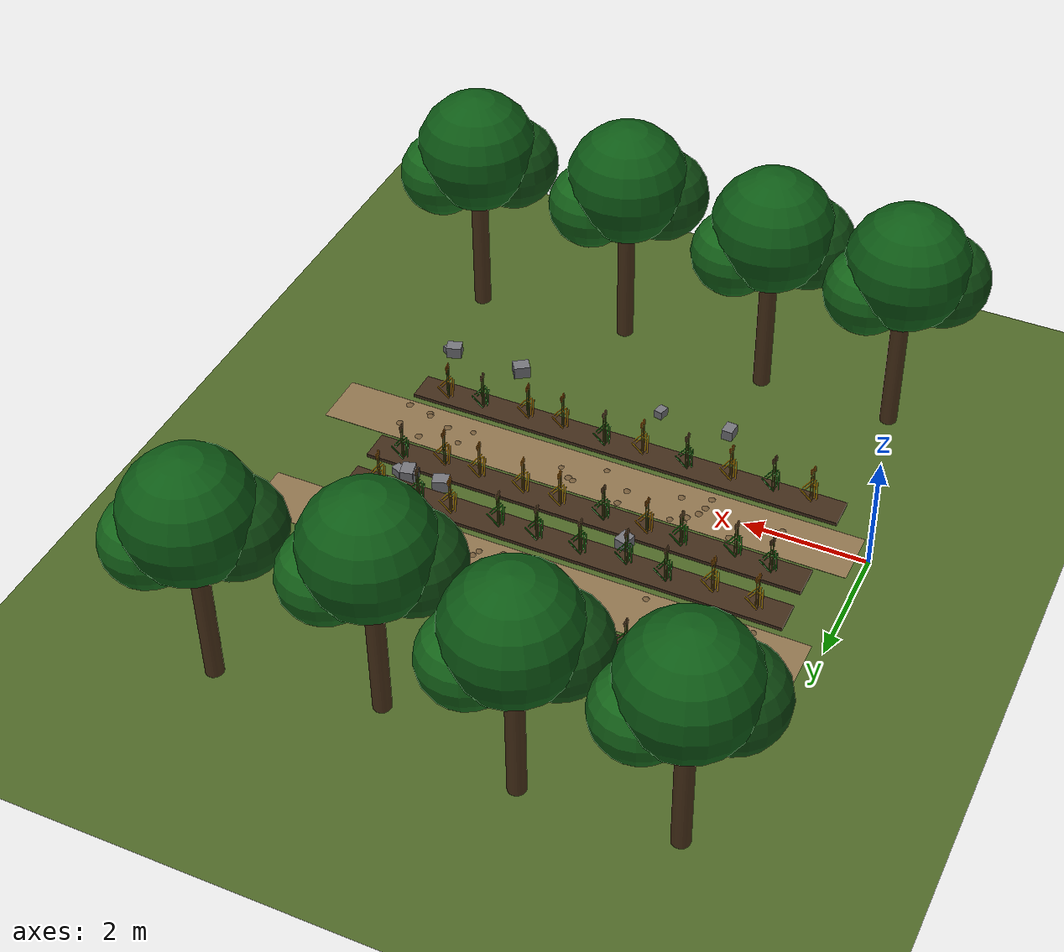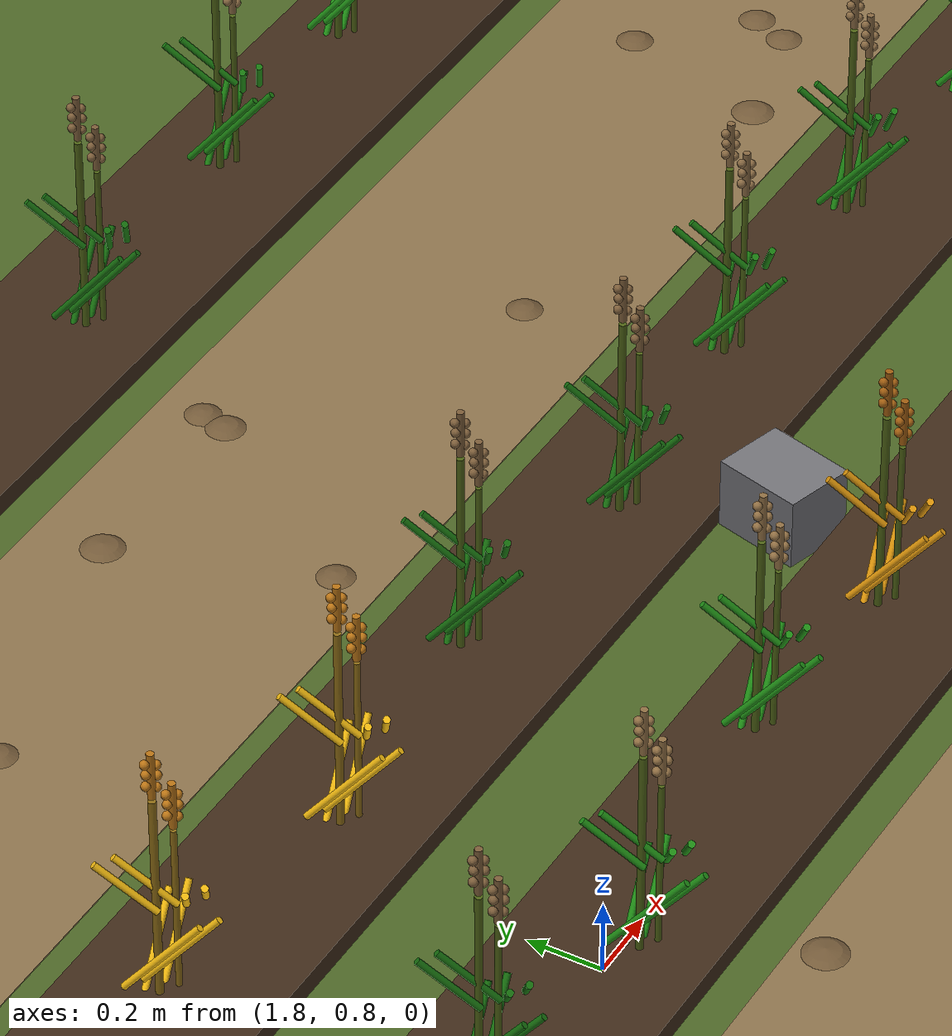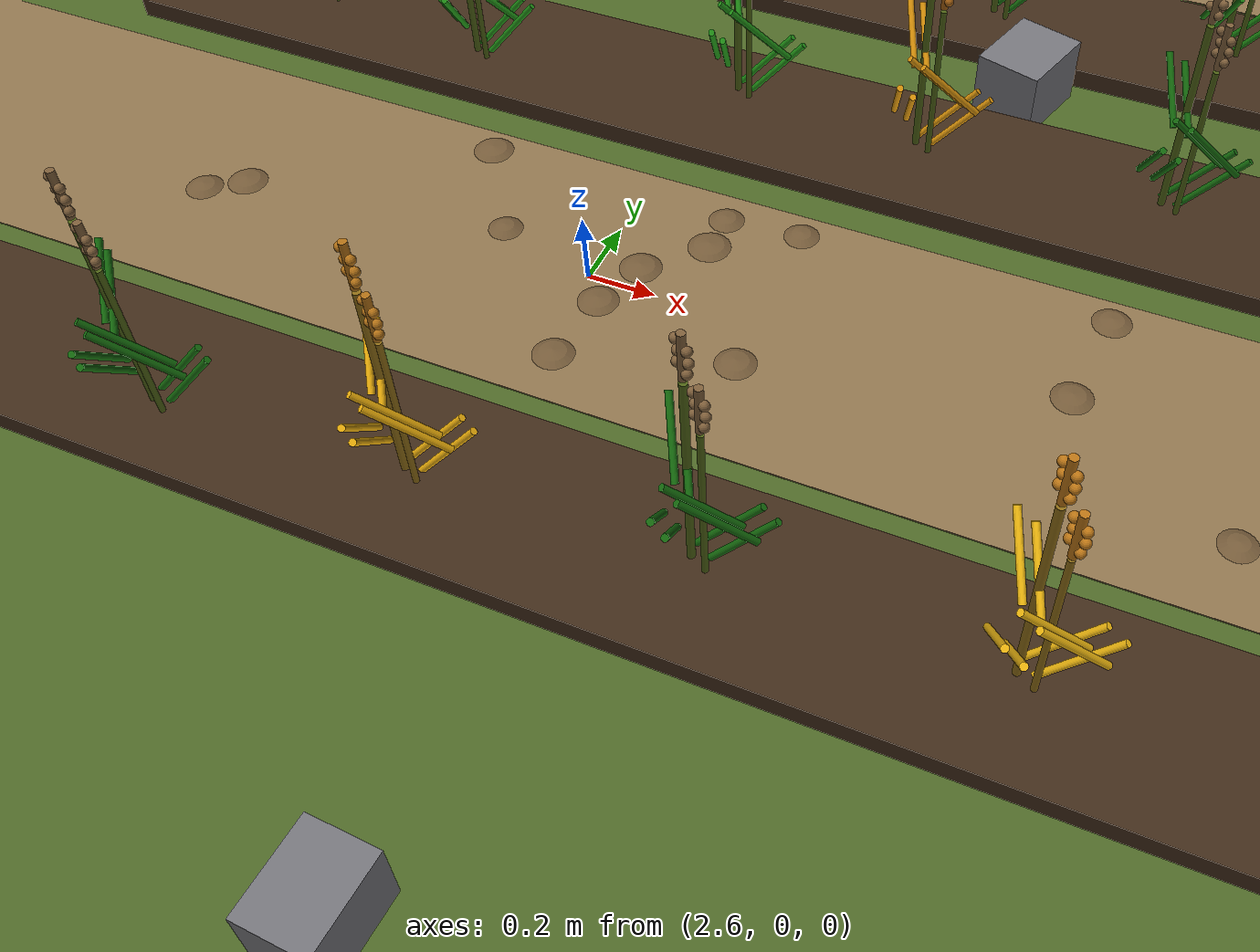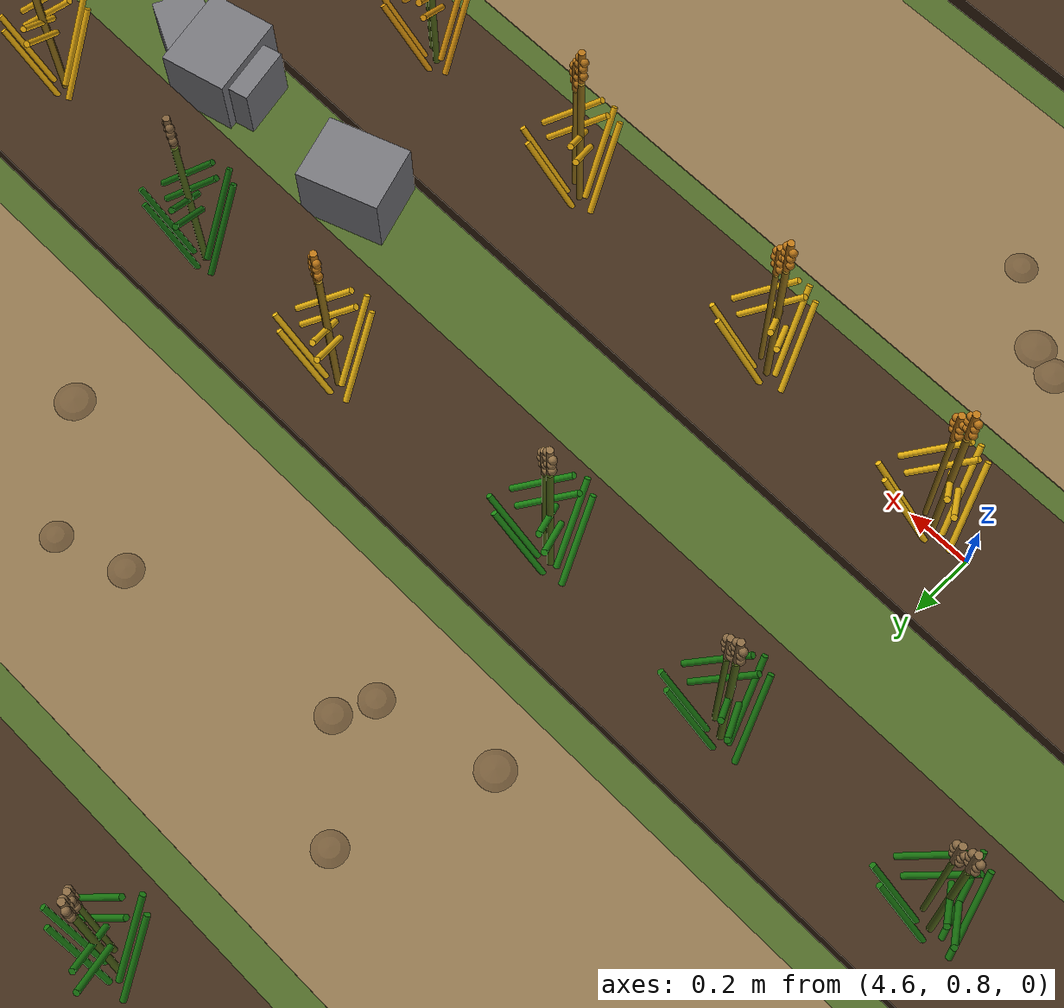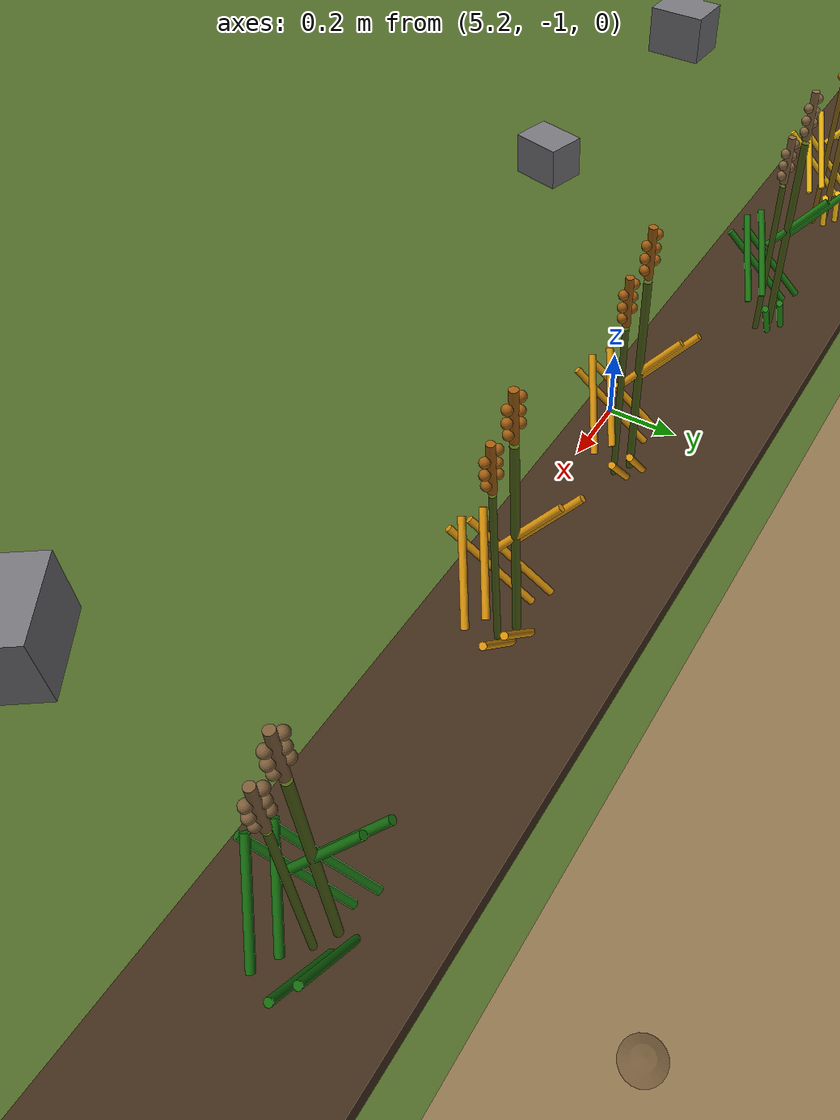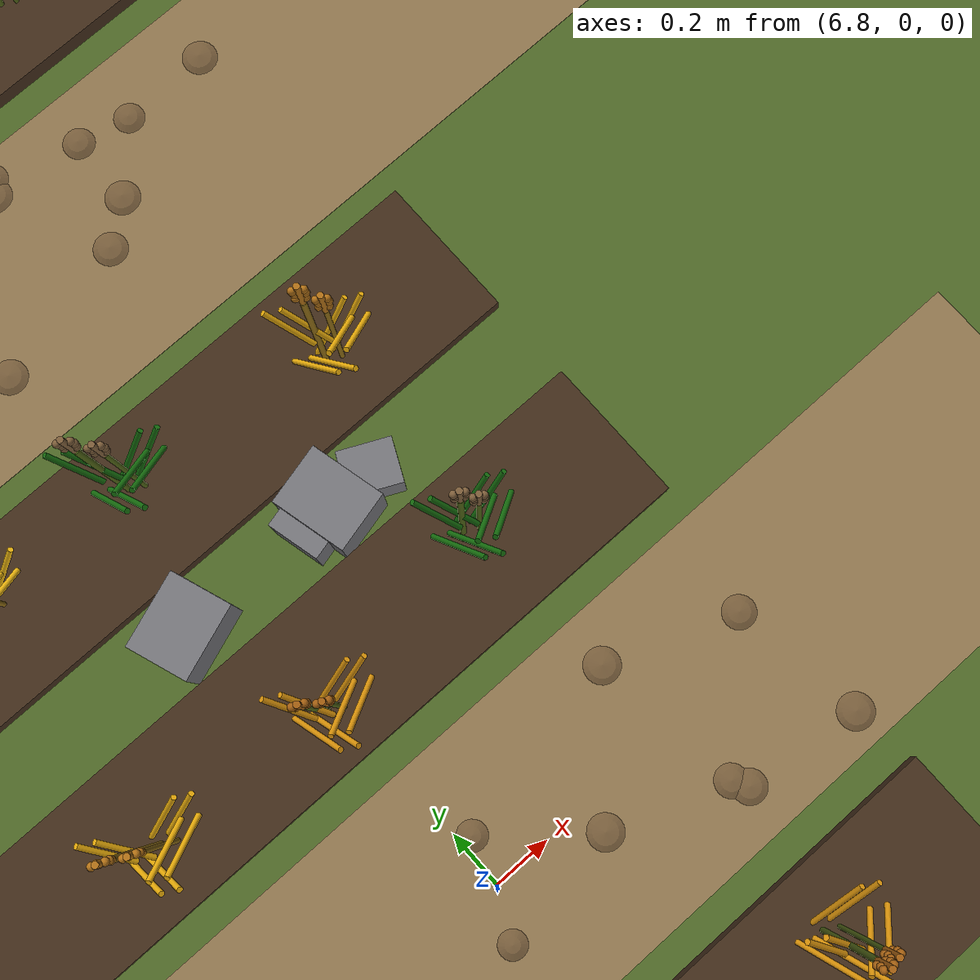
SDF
<?xml version="1.0"?>
<sdf version="1.6">
  <world name="default">
    <plugin filename="gz-sim-physics-system" name="gz::sim::systems::Physics"/>
    <plugin filename="gz-sim-user-commands-system" name="gz::sim::systems::UserCommands"/>
    <plugin filename="gz-sim-scene-broadcaster-system" name="gz::sim::systems::SceneBroadcaster"/>
    <plugin filename="gz-sim-sensors-system" name="gz::sim::systems::Sensors">
      <render_engine>ogre2</render_engine>
    </plugin>
    <plugin filename="gz-sim-imu-system" name="gz::sim::systems::Imu"/>

    <scene>
      <ambient>0.6 0.6 0.6 1</ambient>
      <background>0.5 0.7 0.9 1</background>
      <shadows>false</shadows>
    </scene>

    <physics type="ode">
      <real_time_update_rate>1000.0</real_time_update_rate>
      <max_step_size>0.001</max_step_size>
      <real_time_factor>1</real_time_factor>
    </physics>

    <light type="directional" name="sun">
      <cast_shadows>false</cast_shadows>
      <pose>0 0 10 0 0 0</pose>
      <diffuse>0.9 0.9 0.9 1</diffuse>
      <specular>0.2 0.2 0.2 1</specular>
      <direction>-0.5 0.1 -0.9</direction>
    </light>

    <model name="ground">
      <static>true</static>
      <link name="link">
        <collision name="col">
          <geometry><plane><normal>0 0 1</normal><size>40 40</size></plane></geometry>
        </collision>
        <visual name="vis">
          <geometry><plane><normal>0 0 1</normal><size>40 40</size></plane></geometry>
          <material><ambient>0.30 0.40 0.15 1</ambient><diffuse>0.30 0.40 0.15 1</diffuse></material>
        </visual>
      </link>
    </model>
    <model name="path_1">
      <static>true</static>
      <pose>4.65 0.00 0.002 0 0 0.00</pose>
      <link name="link">
        <visual name="v">
          <geometry><box><size>8.90 0.90 0.004</size></box></geometry>
          <material><ambient>0.55 0.45 0.30 1</ambient><diffuse>0.55 0.45 0.30 1</diffuse></material>
        </visual>
      </link>
    </model>
    <model name="bed_1a">
      <static>true</static>
      <pose>4.35 -0.80 0.030 0 0 0.00</pose>
      <link name="link">
        <visual name="v">
          <geometry><box><size>7.30 0.50 0.060</size></box></geometry>
          <material><ambient>0.25 0.17 0.10 1</ambient><diffuse>0.25 0.17 0.10 1</diffuse></material>
        </visual>
      </link>
    </model>
    <model name="plant_01">\n      <static>true</static>\n      <pose>1.22 -0.88 0 0 0 0</pose>\n      <link name="link">\n        <visual name="stem_0">\n          <pose>0.000 0.000 0.320 0.000 0.000 0.000</pose>\n          <geometry><cylinder><radius>0.01</radius><length>0.64</length></cylinder></geometry>\n          <material><ambient>0.55 0.42 0.08 1</ambient><diffuse>0.55 0.42 0.08 1</diffuse></material>\n        </visual>\n        <visual name="leaf_0_0">\n          <pose>0.055 0.045 0.130 0.000 0.700 0.150</pose>\n          <geometry><cylinder><radius>0.009</radius><length>0.3</length></cylinder></geometry>\n          <material><ambient>0.92 0.68 0.04 1</ambient><diffuse>0.92 0.68 0.04 1</diffuse></material>\n        </visual>\n        <visual name="leaf_0_1">\n          <pose>-0.055 -0.045 0.230 0.000 -0.720 1.900</pose>\n          <geometry><cylinder><radius>0.009</radius><length>0.28</length></cylinder></geometry>\n          <material><ambient>0.92 0.68 0.04 1</ambient><diffuse>0.92 0.68 0.04 1</diffuse></material>\n        </visual>\n        <visual name="leaf_0_2">\n          <pose>0.055 -0.045 0.320 0.000 0.780 3.700</pose>\n          <geometry><cylinder><radius>0.009</radius><length>0.24</length></cylinder></geometry>\n          <material><ambient>0.92 0.68 0.04 1</ambient><diffuse>0.92 0.68 0.04 1</diffuse></material>\n        </visual>\n        <visual name="leaf_0_3">\n          <pose>-0.055 0.045 0.400 0.000 -0.800 5.200</pose>\n          <geometry><cylinder><radius>0.009</radius><length>0.2</length></cylinder></geometry>\n          <material><ambient>0.92 0.68 0.04 1</ambient><diffuse>0.92 0.68 0.04 1</diffuse></material>\n        </visual>\n        <visual name="stem_1">\n          <pose>0.045 -0.025 0.265 0.000 0.000 0.000</pose>\n          <geometry><cylinder><radius>0.008</radius><length>0.53</length></cylinder></geometry>\n          <material><ambient>0.55 0.42 0.08 1</ambient><diffuse>0.55 0.42 0.08 1</diffuse></material>\n        </visual>\n        <visual name="leaf_1_0">\n          <pose>0.100 0.020 0.130 0.000 0.700 0.150</pose>\n          <geometry><cylinder><radius>0.009</radius><length>0.3</length></cylinder></geometry>\n          <material><ambient>0.92 0.68 0.04 1</ambient><diffuse>0.92 0.68 0.04 1</diffuse></material>\n        </visual>\n        <visual name="leaf_1_1">\n          <pose>-0.010 -0.070 0.230 0.000 -0.720 1.900</pose>\n          <geometry><cylinder><radius>0.009</radius><length>0.28</length></cylinder></geometry>\n          <material><ambient>0.92 0.68 0.04 1</ambient><diffuse>0.92 0.68 0.04 1</diffuse></material>\n        </visual>\n        <visual name="leaf_1_2">\n          <pose>0.100 -0.070 0.320 0.000 0.780 3.700</pose>\n          <geometry><cylinder><radius>0.009</radius><length>0.24</length></cylinder></geometry>\n          <material><ambient>0.92 0.68 0.04 1</ambient><diffuse>0.92 0.68 0.04 1</diffuse></material>\n        </visual>\n        <visual name="leaf_1_3">\n          <pose>-0.010 0.020 0.400 0.000 -0.800 5.200</pose>\n          <geometry><cylinder><radius>0.009</radius><length>0.2</length></cylinder></geometry>\n          <material><ambient>0.92 0.68 0.04 1</ambient><diffuse>0.92 0.68 0.04 1</diffuse></material>\n        </visual>\n        <visual name="ear_axis_0">\n          <pose>0.000 0.000 0.715 0.000 0.000 0.000</pose>\n          <geometry><cylinder><radius>0.010</radius><length>0.13</length></cylinder></geometry>\n          <material><ambient>0.68 0.43 0.08 1</ambient><diffuse>0.68 0.43 0.08 1</diffuse></material>\n        </visual>\n        <visual name="grain_0_0">\n          <pose>0.012 -0.006 0.675 0.000 0.000 0.000</pose>\n          <geometry><sphere><radius>0.012</radius></sphere></geometry>\n          <material><ambient>0.68 0.43 0.08 1</ambient><diffuse>0.68 0.43 0.08 1</diffuse></material>\n        </visual>\n        <visual name="grain_0_1">\n          <pose>-0.014 0.006 0.691 0.000 0.000 0.000</pose>\n          <geometry><sphere><radius>0.012</radius></sphere></geometry>\n          <material><ambient>0.68 0.43 0.08 1</ambient><diffuse>0.68 0.43 0.08 1</diffuse></material>\n        </visual>\n        <visual name="grain_0_2">\n          <pose>0.016 -0.006 0.707 0.000 0.000 0.000</pose>\n          <geometry><sphere><radius>0.012</radius></sphere></geometry>\n          <material><ambient>0.68 0.43 0.08 1</ambient><diffuse>0.68 0.43 0.08 1</diffuse></material>\n        </visual>\n        <visual name="grain_0_3">\n          <pose>-0.012 0.006 0.723 0.000 0.000 0.000</pose>\n          <geometry><sphere><radius>0.012</radius></sphere></geometry>\n          <material><ambient>0.68 0.43 0.08 1</ambient><diffuse>0.68 0.43 0.08 1</diffuse></material>\n        </visual>\n        <visual name="grain_0_4">\n          <pose>0.014 -0.006 0.739 0.000 0.000 0.000</pose>\n          <geometry><sphere><radius>0.012</radius></sphere></geometry>\n          <material><ambient>0.68 0.43 0.08 1</ambient><diffuse>0.68 0.43 0.08 1</diffuse></material>\n        </visual>\n        <visual name="grain_0_5">\n          <pose>-0.016 0.006 0.755 0.000 0.000 0.000</pose>\n          <geometry><sphere><radius>0.012</radius></sphere></geometry>\n          <material><ambient>0.68 0.43 0.08 1</ambient><diffuse>0.68 0.43 0.08 1</diffuse></material>\n        </visual>\n        <visual name="ear_axis_1">\n          <pose>0.045 -0.025 0.605 0.000 0.000 0.000</pose>\n          <geometry><cylinder><radius>0.010</radius><length>0.13</length></cylinder></geometry>\n          <material><ambient>0.68 0.43 0.08 1</ambient><diffuse>0.68 0.43 0.08 1</diffuse></material>\n        </visual>\n        <visual name="grain_1_0">\n          <pose>0.057 -0.031 0.565 0.000 0.000 0.000</pose>\n          <geometry><sphere><radius>0.012</radius></sphere></geometry>\n          <material><ambient>0.68 0.43 0.08 1</ambient><diffuse>0.68 0.43 0.08 1</diffuse></material>\n        </visual>\n        <visual name="grain_1_1">\n          <pose>0.031 -0.019 0.581 0.000 0.000 0.000</pose>\n          <geometry><sphere><radius>0.012</radius></sphere></geometry>\n          <material><ambient>0.68 0.43 0.08 1</ambient><diffuse>0.68 0.43 0.08 1</diffuse></material>\n        </visual>\n        <visual name="grain_1_2">\n          <pose>0.061 -0.031 0.597 0.000 0.000 0.000</pose>\n          <geometry><sphere><radius>0.012</radius></sphere></geometry>\n          <material><ambient>0.68 0.43 0.08 1</ambient><diffuse>0.68 0.43 0.08 1</diffuse></material>\n        </visual>\n        <visual name="grain_1_3">\n          <pose>0.033 -0.019 0.613 0.000 0.000 0.000</pose>\n          <geometry><sphere><radius>0.012</radius></sphere></geometry>\n          <material><ambient>0.68 0.43 0.08 1</ambient><diffuse>0.68 0.43 0.08 1</diffuse></material>\n        </visual>\n        <visual name="grain_1_4">\n          <pose>0.059 -0.031 0.629 0.000 0.000 0.000</pose>\n          <geometry><sphere><radius>0.012</radius></sphere></geometry>\n          <material><ambient>0.68 0.43 0.08 1</ambient><diffuse>0.68 0.43 0.08 1</diffuse></material>\n        </visual>\n        <visual name="grain_1_5">\n          <pose>0.029 -0.019 0.645 0.000 0.000 0.000</pose>\n          <geometry><sphere><radius>0.012</radius></sphere></geometry>\n          <material><ambient>0.68 0.43 0.08 1</ambient><diffuse>0.68 0.43 0.08 1</diffuse></material>\n        </visual>\n      </link>\n    </model>\n    <model name="plant_02">\n      <static>true</static>\n      <pose>1.84 -0.86 0 0 0 0</pose>\n      <link name="link">\n        <visual name="stem_0">\n          <pose>0.000 0.000 0.320 0.000 0.000 0.000</pose>\n          <geometry><cylinder><radius>0.01</radius><length>0.64</length></cylinder></geometry>\n          <material><ambient>0.30 0.38 0.08 1</ambient><diffuse>0.30 0.38 0.08 1</diffuse></material>\n        </visual>\n        <visual name="leaf_0_0">\n          <pose>0.055 0.045 0.130 0.000 0.700 0.150</pose>\n          <geometry><cylinder><radius>0.009</radius><length>0.3</length></cylinder></geometry>\n          <material><ambient>0.08 0.42 0.05 1</ambient><diffuse>0.08 0.42 0.05 1</diffuse></material>\n        </visual>\n        <visual name="leaf_0_1">\n          <pose>-0.055 -0.045 0.230 0.000 -0.720 1.900</pose>\n          <geometry><cylinder><radius>0.009</radius><length>0.28</length></cylinder></geometry>\n          <material><ambient>0.08 0.42 0.05 1</ambient><diffuse>0.08 0.42 0.05 1</diffuse></material>\n        </visual>\n        <visual name="leaf_0_2">\n          <pose>0.055 -0.045 0.320 0.000 0.780 3.700</pose>\n          <geometry><cylinder><radius>0.009</radius><length>0.24</length></cylinder></geometry>\n          <material><ambient>0.08 0.42 0.05 1</ambient><diffuse>0.08 0.42 0.05 1</diffuse></material>\n        </visual>\n        <visual name="leaf_0_3">\n          <pose>-0.055 0.045 0.400 0.000 -0.800 5.200</pose>\n          <geometry><cylinder><radius>0.009</radius><length>0.2</length></cylinder></geometry>\n          <material><ambient>0.08 0.42 0.05 1</ambient><diffuse>0.08 0.42 0.05 1</diffuse></material>\n        </visual>\n        <visual name="stem_1">\n          <pose>0.045 -0.025 0.265 0.000 0.000 0.000</pose>\n          <geometry><cylinder><radius>0.008</radius><length>0.53</length></cylinder></geometry>\n          <material><ambient>0.30 0.38 0.08 1</ambient><diffuse>0.30 0.38 0.08 1</diffuse></material>\n        </visual>\n        <visual name="leaf_1_0">\n          <pose>0.100 0.020 0.130 0.000 0.700 0.150</pose>\n          <geometry><cylinder><radius>0.009</radius><length>0.3</length></cylinder></geometry>\n          <material><ambient>0.08 0.42 0.05 1</ambient><diffuse>0.08 0.42 0.05 1</diffuse></material>\n        </visual>\n        <visual name="leaf_1_1">\n          <pose>-0.010 -0.070 0.230 0.000 -0.720 1.900</pose>\n          <geometry><cylinder><radius>0.009</radius><length>0.28</length></cylinder></geometry>\n          <material><ambient>0.08 0.42 0.05 1</ambient><diffuse>0.08 0.42 0.05 1</diffuse></material>\n        </visual>\n        <visual name="leaf_1_2">\n          <pose>0.100 -0.070 0.320 0.000 0.780 3.700</pose>\n          <geometry><cylinder><radius>0.009</radius><length>0.24</length></cylinder></geometry>\n          <material><ambient>0.08 0.42 0.05 1</ambient><diffuse>0.08 0.42 0.05 1</diffuse></material>\n        </visual>\n        <visual name="leaf_1_3">\n          <pose>-0.010 0.020 0.400 0.000 -0.800 5.200</pose>\n          <geometry><cylinder><radius>0.009</radius><length>0.2</length></cylinder></geometry>\n          <material><ambient>0.08 0.42 0.05 1</ambient><diffuse>0.08 0.42 0.05 1</diffuse></material>\n        </visual>\n        <visual name="ear_axis_0">\n          <pose>0.000 0.000 0.715 0.000 0.000 0.000</pose>\n          <geometry><cylinder><radius>0.010</radius><length>0.13</length></cylinder></geometry>\n          <material><ambient>0.48 0.36 0.22 1</ambient><diffuse>0.48 0.36 0.22 1</diffuse></material>\n        </visual>\n        <visual name="grain_0_0">\n          <pose>0.012 -0.006 0.675 0.000 0.000 0.000</pose>\n          <geometry><sphere><radius>0.012</radius></sphere></geometry>\n          <material><ambient>0.48 0.36 0.22 1</ambient><diffuse>0.48 0.36 0.22 1</diffuse></material>\n        </visual>\n        <visual name="grain_0_1">\n          <pose>-0.014 0.006 0.691 0.000 0.000 0.000</pose>\n          <geometry><sphere><radius>0.012</radius></sphere></geometry>\n          <material><ambient>0.48 0.36 0.22 1</ambient><diffuse>0.48 0.36 0.22 1</diffuse></material>\n        </visual>\n        <visual name="grain_0_2">\n          <pose>0.016 -0.006 0.707 0.000 0.000 0.000</pose>\n          <geometry><sphere><radius>0.012</radius></sphere></geometry>\n          <material><ambient>0.48 0.36 0.22 1</ambient><diffuse>0.48 0.36 0.22 1</diffuse></material>\n        </visual>\n        <visual name="grain_0_3">\n          <pose>-0.012 0.006 0.723 0.000 0.000 0.000</pose>\n          <geometry><sphere><radius>0.012</radius></sphere></geometry>\n          <material><ambient>0.48 0.36 0.22 1</ambient><diffuse>0.48 0.36 0.22 1</diffuse></material>\n        </visual>\n        <visual name="grain_0_4">\n          <pose>0.014 -0.006 0.739 0.000 0.000 0.000</pose>\n          <geometry><sphere><radius>0.012</radius></sphere></geometry>\n          <material><ambient>0.48 0.36 0.22 1</ambient><diffuse>0.48 0.36 0.22 1</diffuse></material>\n        </visual>\n        <visual name="grain_0_5">\n          <pose>-0.016 0.006 0.755 0.000 0.000 0.000</pose>\n          <geometry><sphere><radius>0.012</radius></sphere></geometry>\n          <material><ambient>0.48 0.36 0.22 1</ambient><diffuse>0.48 0.36 0.22 1</diffuse></material>\n        </visual>\n        <visual name="ear_axis_1">\n          <pose>0.045 -0.025 0.605 0.000 0.000 0.000</pose>\n          <geometry><cylinder><radius>0.010</radius><length>0.13</length></cylinder></geometry>\n          <material><ambient>0.48 0.36 0.22 1</ambient><diffuse>0.48 0.36 0.22 1</diffuse></material>\n        </visual>\n        <visual name="grain_1_0">\n          <pose>0.057 -0.031 0.565 0.000 0.000 0.000</pose>\n          <geometry><sphere><radius>0.012</radius></sphere></geometry>\n          <material><ambient>0.48 0.36 0.22 1</ambient><diffuse>0.48 0.36 0.22 1</diffuse></material>\n        </visual>\n        <visual name="grain_1_1">\n          <pose>0.031 -0.019 0.581 0.000 0.000 0.000</pose>\n          <geometry><sphere><radius>0.012</radius></sphere></geometry>\n          <material><ambient>0.48 0.36 0.22 1</ambient><diffuse>0.48 0.36 0.22 1</diffuse></material>\n        </visual>\n        <visual name="grain_1_2">\n          <pose>0.061 -0.031 0.597 0.000 0.000 0.000</pose>\n          <geometry><sphere><radius>0.012</radius></sphere></geometry>\n          <material><ambient>0.48 0.36 0.22 1</ambient><diffuse>0.48 0.36 0.22 1</diffuse></material>\n        </visual>\n        <visual name="grain_1_3">\n          <pose>0.033 -0.019 0.613 0.000 0.000 0.000</pose>\n          <geometry><sphere><radius>0.012</radius></sphere></geometry>\n          <material><ambient>0.48 0.36 0.22 1</ambient><diffuse>0.48 0.36 0.22 1</diffuse></material>\n        </visual>\n        <visual name="grain_1_4">\n          <pose>0.059 -0.031 0.629 0.000 0.000 0.000</pose>\n          <geometry><sphere><radius>0.012</radius></sphere></geometry>\n          <material><ambient>0.48 0.36 0.22 1</ambient><diffuse>0.48 0.36 0.22 1</diffuse></material>\n        </visual>\n        <visual name="grain_1_5">\n          <pose>0.029 -0.019 0.645 0.000 0.000 0.000</pose>\n          <geometry><sphere><radius>0.012</radius></sphere></geometry>\n          <material><ambient>0.48 0.36 0.22 1</ambient><diffuse>0.48 0.36 0.22 1</diffuse></material>\n        </visual>\n      </link>\n    </model>\n    <model name="plant_03">\n      <static>true</static>\n      <pose>2.53 -0.81 0 0 0 0</pose>\n      <link name="link">\n        <visual name="stem_0">\n          <pose>0.000 0.000 0.320 0.000 0.000 0.000</pose>\n          <geometry><cylinder><radius>0.01</radius><length>0.64</length></cylinder></geometry>\n          <material><ambient>0.55 0.42 0.08 1</ambient><diffuse>0.55 0.42 0.08 1</diffuse></material>\n        </visual>\n        <visual name="leaf_0_0">\n          <pose>0.055 0.045 0.130 0.000 0.700 0.150</pose>\n          <geometry><cylinder><radius>0.009</radius><length>0.3</length></cylinder></geometry>\n          <material><ambient>0.92 0.68 0.04 1</ambient><diffuse>0.92 0.68 0.04 1</diffuse></material>\n        </visual>\n        <visual name="leaf_0_1">\n          <pose>-0.055 -0.045 0.230 0.000 -0.720 1.900</pose>\n          <geometry><cylinder><radius>0.009</radius><length>0.28</length></cylinder></geometry>\n          <material><ambient>0.92 0.68 0.04 1</ambient><diffuse>0.92 0.68 0.04 1</diffuse></material>\n        </visual>\n        <visual name="leaf_0_2">\n          <pose>0.055 -0.045 0.320 0.000 0.780 3.700</pose>\n          <geometry><cylinder><radius>0.009</radius><length>0.24</length></cylinder></geometry>\n          <material><ambient>0.92 0.68 0.04 1</ambient><diffuse>0.92 0.68 0.04 1</diffuse></material>\n        </visual>\n        <visual name="leaf_0_3">\n          <pose>-0.055 0.045 0.400 0.000 -0.800 5.200</pose>\n          <geometry><cylinder><radius>0.009</radius><length>0.2</length></cylinder></geometry>\n          <material><ambient>0.92 0.68 0.04 1</ambient><diffuse>0.92 0.68 0.04 1</diffuse></material>\n        </visual>\n        <visual name="stem_1">\n          <pose>0.045 -0.025 0.265 0.000 0.000 0.000</pose>\n          <geometry><cylinder><radius>0.008</radius><length>0.53</length></cylinder></geometry>\n          <material><ambient>0.55 0.42 0.08 1</ambient><diffuse>0.55 0.42 0.08 1</diffuse></material>\n        </visual>\n        <visual name="leaf_1_0">\n          <pose>0.100 0.020 0.130 0.000 0.700 0.150</pose>\n          <geometry><cylinder><radius>0.009</radius><length>0.3</length></cylinder></geometry>\n          <material><ambient>0.92 0.68 0.04 1</ambient><diffuse>0.92 0.68 0.04 1</diffuse></material>\n        </visual>\n        <visual name="leaf_1_1">\n          <pose>-0.010 -0.070 0.230 0.000 -0.720 1.900</pose>\n          <geometry><cylinder><radius>0.009</radius><length>0.28</length></cylinder></geometry>\n          <material><ambient>0.92 0.68 0.04 1</ambient><diffuse>0.92 0.68 0.04 1</diffuse></material>\n        </visual>\n        <visual name="leaf_1_2">\n          <pose>0.100 -0.070 0.320 0.000 0.780 3.700</pose>\n          <geometry><cylinder><radius>0.009</radius><length>0.24</length></cylinder></geometry>\n          <material><ambient>0.92 0.68 0.04 1</ambient><diffuse>0.92 0.68 0.04 1</diffuse></material>\n        </visual>\n        <visual name="leaf_1_3">\n          <pose>-0.010 0.020 0.400 0.000 -0.800 5.200</pose>\n          <geometry><cylinder><radius>0.009</radius><length>0.2</length></cylinder></geometry>\n          <material><ambient>0.92 0.68 0.04 1</ambient><diffuse>0.92 0.68 0.04 1</diffuse></material>\n        </visual>\n        <visual name="ear_axis_0">\n          <pose>0.000 0.000 0.715 0.000 0.000 0.000</pose>\n          <geometry><cylinder><radius>0.010</radius><length>0.13</length></cylinder></geometry>\n          <material><ambient>0.68 0.43 0.08 1</ambient><diffuse>0.68 0.43 0.08 1</diffuse></material>\n        </visual>\n        <visual name="grain_0_0">\n          <pose>0.012 -0.006 0.675 0.000 0.000 0.000</pose>\n          <geometry><sphere><radius>0.012</radius></sphere></geometry>\n          <material><ambient>0.68 0.43 0.08 1</ambient><diffuse>0.68 0.43 0.08 1</diffuse></material>\n        </visual>\n        <visual name="grain_0_1">\n          <pose>-0.014 0.006 0.691 0.000 0.000 0.000</pose>\n          <geometry><sphere><radius>0.012</radius></sphere></geometry>\n          <material><ambient>0.68 0.43 0.08 1</ambient><diffuse>0.68 0.43 0.08 1</diffuse></material>\n        </visual>\n        <visual name="grain_0_2">\n          <pose>0.016 -0.006 0.707 0.000 0.000 0.000</pose>\n          <geometry><sphere><radius>0.012</radius></sphere></geometry>\n          <material><ambient>0.68 0.43 0.08 1</ambient><diffuse>0.68 0.43 0.08 1</diffuse></material>\n        </visual>\n        <visual name="grain_0_3">\n          <pose>-0.012 0.006 0.723 0.000 0.000 0.000</pose>\n          <geometry><sphere><radius>0.012</radius></sphere></geometry>\n          <material><ambient>0.68 0.43 0.08 1</ambient><diffuse>0.68 0.43 0.08 1</diffuse></material>\n        </visual>\n        <visual name="grain_0_4">\n          <pose>0.014 -0.006 0.739 0.000 0.000 0.000</pose>\n          <geometry><sphere><radius>0.012</radius></sphere></geometry>\n          <material><ambient>0.68 0.43 0.08 1</ambient><diffuse>0.68 0.43 0.08 1</diffuse></material>\n        </visual>\n        <visual name="grain_0_5">\n          <pose>-0.016 0.006 0.755 0.000 0.000 0.000</pose>\n          <geometry><sphere><radius>0.012</radius></sphere></geometry>\n          <material><ambient>0.68 0.43 0.08 1</ambient><diffuse>0.68 0.43 0.08 1</diffuse></material>\n        </visual>\n        <visual name="ear_axis_1">\n          <pose>0.045 -0.025 0.605 0.000 0.000 0.000</pose>\n          <geometry><cylinder><radius>0.010</radius><length>0.13</length></cylinder></geometry>\n          <material><ambient>0.68 0.43 0.08 1</ambient><diffuse>0.68 0.43 0.08 1</diffuse></material>\n        </visual>\n        <visual name="grain_1_0">\n          <pose>0.057 -0.031 0.565 0.000 0.000 0.000</pose>\n          <geometry><sphere><radius>0.012</radius></sphere></geometry>\n          <material><ambient>0.68 0.43 0.08 1</ambient><diffuse>0.68 0.43 0.08 1</diffuse></material>\n        </visual>\n        <visual name="grain_1_1">\n          <pose>0.031 -0.019 0.581 0.000 0.000 0.000</pose>\n          <geometry><sphere><radius>0.012</radius></sphere></geometry>\n          <material><ambient>0.68 0.43 0.08 1</ambient><diffuse>0.68 0.43 0.08 1</diffuse></material>\n        </visual>\n        <visual name="grain_1_2">\n          <pose>0.061 -0.031 0.597 0.000 0.000 0.000</pose>\n          <geometry><sphere><radius>0.012</radius></sphere></geometry>\n          <material><ambient>0.68 0.43 0.08 1</ambient><diffuse>0.68 0.43 0.08 1</diffuse></material>\n        </visual>\n        <visual name="grain_1_3">\n          <pose>0.033 -0.019 0.613 0.000 0.000 0.000</pose>\n          <geometry><sphere><radius>0.012</radius></sphere></geometry>\n          <material><ambient>0.68 0.43 0.08 1</ambient><diffuse>0.68 0.43 0.08 1</diffuse></material>\n        </visual>\n        <visual name="grain_1_4">\n          <pose>0.059 -0.031 0.629 0.000 0.000 0.000</pose>\n          <geometry><sphere><radius>0.012</radius></sphere></geometry>\n          <material><ambient>0.68 0.43 0.08 1</ambient><diffuse>0.68 0.43 0.08 1</diffuse></material>\n        </visual>\n        <visual name="grain_1_5">\n          <pose>0.029 -0.019 0.645 0.000 0.000 0.000</pose>\n          <geometry><sphere><radius>0.012</radius></sphere></geometry>\n          <material><ambient>0.68 0.43 0.08 1</ambient><diffuse>0.68 0.43 0.08 1</diffuse></material>\n        </visual>\n      </link>\n    </model>\n    <model name="plant_04">\n      <static>true</static>\n      <pose>3.26 -0.78 0 0 0 0</pose>\n      <link name="link">\n        <visual name="stem_0">\n          <pose>0.000 0.000 0.320 0.000 0.000 0.000</pose>\n          <geometry><cylinder><radius>0.01</radius><length>0.64</length></cylinder></geometry>\n          <material><ambient>0.30 0.38 0.08 1</ambient><diffuse>0.30 0.38 0.08 1</diffuse></material>\n        </visual>\n        <visual name="leaf_0_0">\n          <pose>0.055 0.045 0.130 0.000 0.700 0.150</pose>\n          <geometry><cylinder><radius>0.009</radius><length>0.3</length></cylinder></geometry>\n          <material><ambient>0.08 0.42 0.05 1</ambient><diffuse>0.08 0.42 0.05 1</diffuse></material>\n        </visual>\n        <visual name="leaf_0_1">\n          <pose>-0.055 -0.045 0.230 0.000 -0.720 1.900</pose>\n          <geometry><cylinder><radius>0.009</radius><length>0.28</length></cylinder></geometry>\n          <material><ambient>0.08 0.42 0.05 1</ambient><diffuse>0.08 0.42 0.05 1</diffuse></material>\n        </visual>\n        <visual name="leaf_0_2">\n          <pose>0.055 -0.045 0.320 0.000 0.780 3.700</pose>\n          <geometry><cylinder><radius>0.009</radius><length>0.24</length></cylinder></geometry>\n          <material><ambient>0.08 0.42 0.05 1</ambient><diffuse>0.08 0.42 0.05 1</diffuse></material>\n        </visual>\n        <visual name="leaf_0_3">\n          <pose>-0.055 0.045 0.400 0.000 -0.800 5.200</pose>\n          <geometry><cylinder><radius>0.009</radius><length>0.2</length></cylinder></geometry>\n          <material><ambient>0.08 0.42 0.05 1</ambient><diffuse>0.08 0.42 0.05 1</diffuse></material>\n        </visual>\n        <visual name="stem_1">\n          <pose>0.045 -0.025 0.265 0.000 0.000 0.000</pose>\n          <geometry><cylinder><radius>0.008</radius><length>0.53</length></cylinder></geometry>\n          <material><ambient>0.30 0.38 0.08 1</ambient><diffuse>0.30 0.38 0.08 1</diffuse></material>\n        </visual>\n        <visual name="leaf_1_0">\n          <pose>0.100 0.020 0.130 0.000 0.700 0.150</pose>\n          <geometry><cylinder><radius>0.009</radius><length>0.3</length></cylinder></geometry>\n          <material><ambient>0.08 0.42 0.05 1</ambient><diffuse>0.08 0.42 0.05 1</diffuse></material>\n        </visual>\n        <visual name="leaf_1_1">\n          <pose>-0.010 -0.070 0.230 0.000 -0.720 1.900</pose>\n          <geometry><cylinder><radius>0.009</radius><length>0.28</length></cylinder></geometry>\n          <material><ambient>0.08 0.42 0.05 1</ambient><diffuse>0.08 0.42 0.05 1</diffuse></material>\n        </visual>\n        <visual name="leaf_1_2">\n          <pose>0.100 -0.070 0.320 0.000 0.780 3.700</pose>\n          <geometry><cylinder><radius>0.009</radius><length>0.24</length></cylinder></geometry>\n          <material><ambient>0.08 0.42 0.05 1</ambient><diffuse>0.08 0.42 0.05 1</diffuse></material>\n        </visual>\n        <visual name="leaf_1_3">\n          <pose>-0.010 0.020 0.400 0.000 -0.800 5.200</pose>\n          <geometry><cylinder><radius>0.009</radius><length>0.2</length></cylinder></geometry>\n          <material><ambient>0.08 0.42 0.05 1</ambient><diffuse>0.08 0.42 0.05 1</diffuse></material>\n        </visual>\n        <visual name="ear_axis_0">\n          <pose>0.000 0.000 0.715 0.000 0.000 0.000</pose>\n          <geometry><cylinder><radius>0.010</radius><length>0.13</length></cylinder></geometry>\n          <material><ambient>0.48 0.36 0.22 1</ambient><diffuse>0.48 0.36 0.22 1</diffuse></material>\n        </visual>\n        <visual name="grain_0_0">\n          <pose>0.012 -0.006 0.675 0.000 0.000 0.000</pose>\n          <geometry><sphere><radius>0.012</radius></sphere></geometry>\n          <material><ambient>0.48 0.36 0.22 1</ambient><diffuse>0.48 0.36 0.22 1</diffuse></material>\n        </visual>\n        <visual name="grain_0_1">\n          <pose>-0.014 0.006 0.691 0.000 0.000 0.000</pose>\n          <geometry><sphere><radius>0.012</radius></sphere></geometry>\n          <material><ambient>0.48 0.36 0.22 1</ambient><diffuse>0.48 0.36 0.22 1</diffuse></material>\n        </visual>\n        <visual name="grain_0_2">\n          <pose>0.016 -0.006 0.707 0.000 0.000 0.000</pose>\n          <geometry><sphere><radius>0.012</radius></sphere></geometry>\n          <material><ambient>0.48 0.36 0.22 1</ambient><diffuse>0.48 0.36 0.22 1</diffuse></material>\n        </visual>\n        <visual name="grain_0_3">\n          <pose>-0.012 0.006 0.723 0.000 0.000 0.000</pose>\n          <geometry><sphere><radius>0.012</radius></sphere></geometry>\n          <material><ambient>0.48 0.36 0.22 1</ambient><diffuse>0.48 0.36 0.22 1</diffuse></material>\n        </visual>\n        <visual name="grain_0_4">\n          <pose>0.014 -0.006 0.739 0.000 0.000 0.000</pose>\n          <geometry><sphere><radius>0.012</radius></sphere></geometry>\n          <material><ambient>0.48 0.36 0.22 1</ambient><diffuse>0.48 0.36 0.22 1</diffuse></material>\n        </visual>\n        <visual name="grain_0_5">\n          <pose>-0.016 0.006 0.755 0.000 0.000 0.000</pose>\n          <geometry><sphere><radius>0.012</radius></sphere></geometry>\n          <material><ambient>0.48 0.36 0.22 1</ambient><diffuse>0.48 0.36 0.22 1</diffuse></material>\n        </visual>\n        <visual name="ear_axis_1">\n          <pose>0.045 -0.025 0.605 0.000 0.000 0.000</pose>\n          <geometry><cylinder><radius>0.010</radius><length>0.13</length></cylinder></geometry>\n          <material><ambient>0.48 0.36 0.22 1</ambient><diffuse>0.48 0.36 0.22 1</diffuse></material>\n        </visual>\n        <visual name="grain_1_0">\n          <pose>0.057 -0.031 0.565 0.000 0.000 0.000</pose>\n          <geometry><sphere><radius>0.012</radius></sphere></geometry>\n          <material><ambient>0.48 0.36 0.22 1</ambient><diffuse>0.48 0.36 0.22 1</diffuse></material>\n        </visual>\n        <visual name="grain_1_1">\n          <pose>0.031 -0.019 0.581 0.000 0.000 0.000</pose>\n          <geometry><sphere><radius>0.012</radius></sphere></geometry>\n          <material><ambient>0.48 0.36 0.22 1</ambient><diffuse>0.48 0.36 0.22 1</diffuse></material>\n        </visual>\n        <visual name="grain_1_2">\n          <pose>0.061 -0.031 0.597 0.000 0.000 0.000</pose>\n          <geometry><sphere><radius>0.012</radius></sphere></geometry>\n          <material><ambient>0.48 0.36 0.22 1</ambient><diffuse>0.48 0.36 0.22 1</diffuse></material>\n        </visual>\n        <visual name="grain_1_3">\n          <pose>0.033 -0.019 0.613 0.000 0.000 0.000</pose>\n          <geometry><sphere><radius>0.012</radius></sphere></geometry>\n          <material><ambient>0.48 0.36 0.22 1</ambient><diffuse>0.48 0.36 0.22 1</diffuse></material>\n        </visual>\n        <visual name="grain_1_4">\n          <pose>0.059 -0.031 0.629 0.000 0.000 0.000</pose>\n          <geometry><sphere><radius>0.012</radius></sphere></geometry>\n          <material><ambient>0.48 0.36 0.22 1</ambient><diffuse>0.48 0.36 0.22 1</diffuse></material>\n        </visual>\n        <visual name="grain_1_5">\n          <pose>0.029 -0.019 0.645 0.000 0.000 0.000</pose>\n          <geometry><sphere><radius>0.012</radius></sphere></geometry>\n          <material><ambient>0.48 0.36 0.22 1</ambient><diffuse>0.48 0.36 0.22 1</diffuse></material>\n        </visual>\n      </link>\n    </model>\n    <model name="plant_05">\n      <static>true</static>\n      <pose>4.02 -0.79 0 0 0 0</pose>\n      <link name="link">\n        <visual name="stem_0">\n          <pose>0.000 0.000 0.320 0.000 0.000 0.000</pose>\n          <geometry><cylinder><radius>0.01</radius><length>0.64</length></cylinder></geometry>\n          <material><ambient>0.55 0.42 0.08 1</ambient><diffuse>0.55 0.42 0.08 1</diffuse></material>\n        </visual>\n        <visual name="leaf_0_0">\n          <pose>0.055 0.045 0.130 0.000 0.700 0.150</pose>\n          <geometry><cylinder><radius>0.009</radius><length>0.3</length></cylinder></geometry>\n          <material><ambient>0.95 0.73 0.06 1</ambient><diffuse>0.95 0.73 0.06 1</diffuse></material>\n        </visual>\n        <visual name="leaf_0_1">\n          <pose>-0.055 -0.045 0.230 0.000 -0.720 1.900</pose>\n          <geometry><cylinder><radius>0.009</radius><length>0.28</length></cylinder></geometry>\n          <material><ambient>0.95 0.73 0.06 1</ambient><diffuse>0.95 0.73 0.06 1</diffuse></material>\n        </visual>\n        <visual name="leaf_0_2">\n          <pose>0.055 -0.045 0.320 0.000 0.780 3.700</pose>\n          <geometry><cylinder><radius>0.009</radius><length>0.24</length></cylinder></geometry>\n          <material><ambient>0.95 0.73 0.06 1</ambient><diffuse>0.95 0.73 0.06 1</diffuse></material>\n        </visual>\n        <visual name="leaf_0_3">\n          <pose>-0.055 0.045 0.400 0.000 -0.800 5.200</pose>\n          <geometry><cylinder><radius>0.009</radius><length>0.2</length></cylinder></geometry>\n          <material><ambient>0.95 0.73 0.06 1</ambient><diffuse>0.95 0.73 0.06 1</diffuse></material>\n        </visual>\n        <visual name="stem_1">\n          <pose>0.045 -0.025 0.265 0.000 0.000 0.000</pose>\n          <geometry><cylinder><radius>0.008</radius><length>0.53</length></cylinder></geometry>\n          <material><ambient>0.55 0.42 0.08 1</ambient><diffuse>0.55 0.42 0.08 1</diffuse></material>\n        </visual>\n        <visual name="leaf_1_0">\n          <pose>0.100 0.020 0.130 0.000 0.700 0.150</pose>\n          <geometry><cylinder><radius>0.009</radius><length>0.3</length></cylinder></geometry>\n          <material><ambient>0.95 0.73 0.06 1</ambient><diffuse>0.95 0.73 0.06 1</diffuse></material>\n        </visual>\n        <visual name="leaf_1_1">\n          <pose>-0.010 -0.070 0.230 0.000 -0.720 1.900</pose>\n          <geometry><cylinder><radius>0.009</radius><length>0.28</length></cylinder></geometry>\n          <material><ambient>0.95 0.73 0.06 1</ambient><diffuse>0.95 0.73 0.06 1</diffuse></material>\n        </visual>\n        <visual name="leaf_1_2">\n          <pose>0.100 -0.070 0.320 0.000 0.780 3.700</pose>\n          <geometry><cylinder><radius>0.009</radius><length>0.24</length></cylinder></geometry>\n          <material><ambient>0.95 0.73 0.06 1</ambient><diffuse>0.95 0.73 0.06 1</diffuse></material>\n        </visual>\n        <visual name="leaf_1_3">\n          <pose>-0.010 0.020 0.400 0.000 -0.800 5.200</pose>\n          <geometry><cylinder><radius>0.009</radius><length>0.2</length></cylinder></geometry>\n          <material><ambient>0.95 0.73 0.06 1</ambient><diffuse>0.95 0.73 0.06 1</diffuse></material>\n        </visual>\n        <visual name="ear_axis_0">\n          <pose>0.000 0.000 0.715 0.000 0.000 0.000</pose>\n          <geometry><cylinder><radius>0.010</radius><length>0.13</length></cylinder></geometry>\n          <material><ambient>0.72 0.45 0.08 1</ambient><diffuse>0.72 0.45 0.08 1</diffuse></material>\n        </visual>\n        <visual name="grain_0_0">\n          <pose>0.012 -0.006 0.675 0.000 0.000 0.000</pose>\n          <geometry><sphere><radius>0.012</radius></sphere></geometry>\n          <material><ambient>0.72 0.45 0.08 1</ambient><diffuse>0.72 0.45 0.08 1</diffuse></material>\n        </visual>\n        <visual name="grain_0_1">\n          <pose>-0.014 0.006 0.691 0.000 0.000 0.000</pose>\n          <geometry><sphere><radius>0.012</radius></sphere></geometry>\n          <material><ambient>0.72 0.45 0.08 1</ambient><diffuse>0.72 0.45 0.08 1</diffuse></material>\n        </visual>\n        <visual name="grain_0_2">\n          <pose>0.016 -0.006 0.707 0.000 0.000 0.000</pose>\n          <geometry><sphere><radius>0.012</radius></sphere></geometry>\n          <material><ambient>0.72 0.45 0.08 1</ambient><diffuse>0.72 0.45 0.08 1</diffuse></material>\n        </visual>\n        <visual name="grain_0_3">\n          <pose>-0.012 0.006 0.723 0.000 0.000 0.000</pose>\n          <geometry><sphere><radius>0.012</radius></sphere></geometry>\n          <material><ambient>0.72 0.45 0.08 1</ambient><diffuse>0.72 0.45 0.08 1</diffuse></material>\n        </visual>\n        <visual name="grain_0_4">\n          <pose>0.014 -0.006 0.739 0.000 0.000 0.000</pose>\n          <geometry><sphere><radius>0.012</radius></sphere></geometry>\n          <material><ambient>0.72 0.45 0.08 1</ambient><diffuse>0.72 0.45 0.08 1</diffuse></material>\n        </visual>\n        <visual name="grain_0_5">\n          <pose>-0.016 0.006 0.755 0.000 0.000 0.000</pose>\n          <geometry><sphere><radius>0.012</radius></sphere></geometry>\n          <material><ambient>0.72 0.45 0.08 1</ambient><diffuse>0.72 0.45 0.08 1</diffuse></material>\n        </visual>\n        <visual name="ear_axis_1">\n          <pose>0.045 -0.025 0.605 0.000 0.000 0.000</pose>\n          <geometry><cylinder><radius>0.010</radius><length>0.13</length></cylinder></geometry>\n          <material><ambient>0.72 0.45 0.08 1</ambient><diffuse>0.72 0.45 0.08 1</diffuse></material>\n        </visual>\n        <visual name="grain_1_0">\n          <pose>0.057 -0.031 0.565 0.000 0.000 0.000</pose>\n          <geometry><sphere><radius>0.012</radius></sphere></geometry>\n          <material><ambient>0.72 0.45 0.08 1</ambient><diffuse>0.72 0.45 0.08 1</diffuse></material>\n        </visual>\n        <visual name="grain_1_1">\n          <pose>0.031 -0.019 0.581 0.000 0.000 0.000</pose>\n          <geometry><sphere><radius>0.012</radius></sphere></geometry>\n          <material><ambient>0.72 0.45 0.08 1</ambient><diffuse>0.72 0.45 0.08 1</diffuse></material>\n        </visual>\n        <visual name="grain_1_2">\n          <pose>0.061 -0.031 0.597 0.000 0.000 0.000</pose>\n          <geometry><sphere><radius>0.012</radius></sphere></geometry>\n          <material><ambient>0.72 0.45 0.08 1</ambient><diffuse>0.72 0.45 0.08 1</diffuse></material>\n        </visual>\n        <visual name="grain_1_3">\n          <pose>0.033 -0.019 0.613 0.000 0.000 0.000</pose>\n          <geometry><sphere><radius>0.012</radius></sphere></geometry>\n          <material><ambient>0.72 0.45 0.08 1</ambient><diffuse>0.72 0.45 0.08 1</diffuse></material>\n        </visual>\n        <visual name="grain_1_4">\n          <pose>0.059 -0.031 0.629 0.000 0.000 0.000</pose>\n          <geometry><sphere><radius>0.012</radius></sphere></geometry>\n          <material><ambient>0.72 0.45 0.08 1</ambient><diffuse>0.72 0.45 0.08 1</diffuse></material>\n        </visual>\n        <visual name="grain_1_5">\n          <pose>0.029 -0.019 0.645 0.000 0.000 0.000</pose>\n          <geometry><sphere><radius>0.012</radius></sphere></geometry>\n          <material><ambient>0.72 0.45 0.08 1</ambient><diffuse>0.72 0.45 0.08 1</diffuse></material>\n        </visual>\n      </link>\n    </model>\n    <model name="plant_06">\n      <static>true</static>\n      <pose>4.66 -0.74 0 0 0 0</pose>\n      <link name="link">\n        <visual name="stem_0">\n          <pose>0.000 0.000 0.320 0.000 0.000 0.000</pose>\n          <geometry><cylinder><radius>0.01</radius><length>0.64</length></cylinder></geometry>\n          <material><ambient>0.30 0.38 0.08 1</ambient><diffuse>0.30 0.38 0.08 1</diffuse></material>\n        </visual>\n        <visual name="leaf_0_0">\n          <pose>0.055 0.045 0.130 0.000 0.700 0.150</pose>\n          <geometry><cylinder><radius>0.009</radius><length>0.3</length></cylinder></geometry>\n          <material><ambient>0.10 0.48 0.06 1</ambient><diffuse>0.10 0.48 0.06 1</diffuse></material>\n        </visual>\n        <visual name="leaf_0_1">\n          <pose>-0.055 -0.045 0.230 0.000 -0.720 1.900</pose>\n          <geometry><cylinder><radius>0.009</radius><length>0.28</length></cylinder></geometry>\n          <material><ambient>0.10 0.48 0.06 1</ambient><diffuse>0.10 0.48 0.06 1</diffuse></material>\n        </visual>\n        <visual name="leaf_0_2">\n          <pose>0.055 -0.045 0.320 0.000 0.780 3.700</pose>\n          <geometry><cylinder><radius>0.009</radius><length>0.24</length></cylinder></geometry>\n          <material><ambient>0.10 0.48 0.06 1</ambient><diffuse>0.10 0.48 0.06 1</diffuse></material>\n        </visual>\n        <visual name="leaf_0_3">\n          <pose>-0.055 0.045 0.400 0.000 -0.800 5.200</pose>\n          <geometry><cylinder><radius>0.009</radius><length>0.2</length></cylinder></geometry>\n          <material><ambient>0.10 0.48 0.06 1</ambient><diffuse>0.10 0.48 0.06 1</diffuse></material>\n        </visual>\n        <visual name="stem_1">\n          <pose>0.045 -0.025 0.265 0.000 0.000 0.000</pose>\n          <geometry><cylinder><radius>0.008</radius><length>0.53</length></cylinder></geometry>\n          <material><ambient>0.30 0.38 0.08 1</ambient><diffuse>0.30 0.38 0.08 1</diffuse></material>\n        </visual>\n        <visual name="leaf_1_0">\n          <pose>0.100 0.020 0.130 0.000 0.700 0.150</pose>\n          <geometry><cylinder><radius>0.009</radius><length>0.3</length></cylinder></geometry>\n          <material><ambient>0.10 0.48 0.06 1</ambient><diffuse>0.10 0.48 0.06 1</diffuse></material>\n        </visual>\n        <visual name="leaf_1_1">\n          <pose>-0.010 -0.070 0.230 0.000 -0.720 1.900</pose>\n          <geometry><cylinder><radius>0.009</radius><length>0.28</length></cylinder></geometry>\n          <material><ambient>0.10 0.48 0.06 1</ambient><diffuse>0.10 0.48 0.06 1</diffuse></material>\n        </visual>\n        <visual name="leaf_1_2">\n          <pose>0.100 -0.070 0.320 0.000 0.780 3.700</pose>\n          <geometry><cylinder><radius>0.009</radius><length>0.24</length></cylinder></geometry>\n          <material><ambient>0.10 0.48 0.06 1</ambient><diffuse>0.10 0.48 0.06 1</diffuse></material>\n        </visual>\n        <visual name="leaf_1_3">\n          <pose>-0.010 0.020 0.400 0.000 -0.800 5.200</pose>\n          <geometry><cylinder><radius>0.009</radius><length>0.2</length></cylinder></geometry>\n          <material><ambient>0.10 0.48 0.06 1</ambient><diffuse>0.10 0.48 0.06 1</diffuse></material>\n        </visual>\n        <visual name="ear_axis_0">\n          <pose>0.000 0.000 0.715 0.000 0.000 0.000</pose>\n          <geometry><cylinder><radius>0.010</radius><length>0.13</length></cylinder></geometry>\n          <material><ambient>0.52 0.40 0.25 1</ambient><diffuse>0.52 0.40 0.25 1</diffuse></material>\n        </visual>\n        <visual name="grain_0_0">\n          <pose>0.012 -0.006 0.675 0.000 0.000 0.000</pose>\n          <geometry><sphere><radius>0.012</radius></sphere></geometry>\n          <material><ambient>0.52 0.40 0.25 1</ambient><diffuse>0.52 0.40 0.25 1</diffuse></material>\n        </visual>\n        <visual name="grain_0_1">\n          <pose>-0.014 0.006 0.691 0.000 0.000 0.000</pose>\n          <geometry><sphere><radius>0.012</radius></sphere></geometry>\n          <material><ambient>0.52 0.40 0.25 1</ambient><diffuse>0.52 0.40 0.25 1</diffuse></material>\n        </visual>\n        <visual name="grain_0_2">\n          <pose>0.016 -0.006 0.707 0.000 0.000 0.000</pose>\n          <geometry><sphere><radius>0.012</radius></sphere></geometry>\n          <material><ambient>0.52 0.40 0.25 1</ambient><diffuse>0.52 0.40 0.25 1</diffuse></material>\n        </visual>\n        <visual name="grain_0_3">\n          <pose>-0.012 0.006 0.723 0.000 0.000 0.000</pose>\n          <geometry><sphere><radius>0.012</radius></sphere></geometry>\n          <material><ambient>0.52 0.40 0.25 1</ambient><diffuse>0.52 0.40 0.25 1</diffuse></material>\n        </visual>\n        <visual name="grain_0_4">\n          <pose>0.014 -0.006 0.739 0.000 0.000 0.000</pose>\n          <geometry><sphere><radius>0.012</radius></sphere></geometry>\n          <material><ambient>0.52 0.40 0.25 1</ambient><diffuse>0.52 0.40 0.25 1</diffuse></material>\n        </visual>\n        <visual name="grain_0_5">\n          <pose>-0.016 0.006 0.755 0.000 0.000 0.000</pose>\n          <geometry><sphere><radius>0.012</radius></sphere></geometry>\n          <material><ambient>0.52 0.40 0.25 1</ambient><diffuse>0.52 0.40 0.25 1</diffuse></material>\n        </visual>\n        <visual name="ear_axis_1">\n          <pose>0.045 -0.025 0.605 0.000 0.000 0.000</pose>\n          <geometry><cylinder><radius>0.010</radius><length>0.13</length></cylinder></geometry>\n          <material><ambient>0.52 0.40 0.25 1</ambient><diffuse>0.52 0.40 0.25 1</diffuse></material>\n        </visual>\n        <visual name="grain_1_0">\n          <pose>0.057 -0.031 0.565 0.000 0.000 0.000</pose>\n          <geometry><sphere><radius>0.012</radius></sphere></geometry>\n          <material><ambient>0.52 0.40 0.25 1</ambient><diffuse>0.52 0.40 0.25 1</diffuse></material>\n        </visual>\n        <visual name="grain_1_1">\n          <pose>0.031 -0.019 0.581 0.000 0.000 0.000</pose>\n          <geometry><sphere><radius>0.012</radius></sphere></geometry>\n          <material><ambient>0.52 0.40 0.25 1</ambient><diffuse>0.52 0.40 0.25 1</diffuse></material>\n        </visual>\n        <visual name="grain_1_2">\n          <pose>0.061 -0.031 0.597 0.000 0.000 0.000</pose>\n          <geometry><sphere><radius>0.012</radius></sphere></geometry>\n          <material><ambient>0.52 0.40 0.25 1</ambient><diffuse>0.52 0.40 0.25 1</diffuse></material>\n        </visual>\n        <visual name="grain_1_3">\n          <pose>0.033 -0.019 0.613 0.000 0.000 0.000</pose>\n          <geometry><sphere><radius>0.012</radius></sphere></geometry>\n          <material><ambient>0.52 0.40 0.25 1</ambient><diffuse>0.52 0.40 0.25 1</diffuse></material>\n        </visual>\n        <visual name="grain_1_4">\n          <pose>0.059 -0.031 0.629 0.000 0.000 0.000</pose>\n          <geometry><sphere><radius>0.012</radius></sphere></geometry>\n          <material><ambient>0.52 0.40 0.25 1</ambient><diffuse>0.52 0.40 0.25 1</diffuse></material>\n        </visual>\n        <visual name="grain_1_5">\n          <pose>0.029 -0.019 0.645 0.000 0.000 0.000</pose>\n          <geometry><sphere><radius>0.012</radius></sphere></geometry>\n          <material><ambient>0.52 0.40 0.25 1</ambient><diffuse>0.52 0.40 0.25 1</diffuse></material>\n        </visual>\n      </link>\n    </model>\n    <model name="plant_07">\n      <static>true</static>\n      <pose>5.43 -0.83 0 0 0 0</pose>\n      <link name="link">\n        <visual name="stem_0">\n          <pose>0.000 0.000 0.320 0.000 0.000 0.000</pose>\n          <geometry><cylinder><radius>0.01</radius><length>0.64</length></cylinder></geometry>\n          <material><ambient>0.30 0.38 0.08 1</ambient><diffuse>0.30 0.38 0.08 1</diffuse></material>\n        </visual>\n        <visual name="leaf_0_0">\n          <pose>0.055 0.045 0.130 0.000 0.700 0.150</pose>\n          <geometry><cylinder><radius>0.009</radius><length>0.3</length></cylinder></geometry>\n          <material><ambient>0.86 0.58 0.04 1</ambient><diffuse>0.86 0.58 0.04 1</diffuse></material>\n        </visual>\n        <visual name="leaf_0_1">\n          <pose>-0.055 -0.045 0.230 0.000 -0.720 1.900</pose>\n          <geometry><cylinder><radius>0.009</radius><length>0.28</length></cylinder></geometry>\n          <material><ambient>0.86 0.58 0.04 1</ambient><diffuse>0.86 0.58 0.04 1</diffuse></material>\n        </visual>\n        <visual name="leaf_0_2">\n          <pose>0.055 -0.045 0.320 0.000 0.780 3.700</pose>\n          <geometry><cylinder><radius>0.009</radius><length>0.24</length></cylinder></geometry>\n          <material><ambient>0.86 0.58 0.04 1</ambient><diffuse>0.86 0.58 0.04 1</diffuse></material>\n        </visual>\n        <visual name="leaf_0_3">\n          <pose>-0.055 0.045 0.400 0.000 -0.800 5.200</pose>\n          <geometry><cylinder><radius>0.009</radius><length>0.2</length></cylinder></geometry>\n          <material><ambient>0.86 0.58 0.04 1</ambient><diffuse>0.86 0.58 0.04 1</diffuse></material>\n        </visual>\n        <visual name="stem_1">\n          <pose>0.045 -0.025 0.265 0.000 0.000 0.000</pose>\n          <geometry><cylinder><radius>0.008</radius><length>0.53</length></cylinder></geometry>\n          <material><ambient>0.30 0.38 0.08 1</ambient><diffuse>0.30 0.38 0.08 1</diffuse></material>\n        </visual>\n        <visual name="leaf_1_0">\n          <pose>0.100 0.020 0.130 0.000 0.700 0.150</pose>\n          <geometry><cylinder><radius>0.009</radius><length>0.3</length></cylinder></geometry>\n          <material><ambient>0.86 0.58 0.04 1</ambient><diffuse>0.86 0.58 0.04 1</diffuse></material>\n        </visual>\n        <visual name="leaf_1_1">\n          <pose>-0.010 -0.070 0.230 0.000 -0.720 1.900</pose>\n          <geometry><cylinder><radius>0.009</radius><length>0.28</length></cylinder></geometry>\n          <material><ambient>0.86 0.58 0.04 1</ambient><diffuse>0.86 0.58 0.04 1</diffuse></material>\n        </visual>\n        <visual name="leaf_1_2">\n          <pose>0.100 -0.070 0.320 0.000 0.780 3.700</pose>\n          <geometry><cylinder><radius>0.009</radius><length>0.24</length></cylinder></geometry>\n          <material><ambient>0.86 0.58 0.04 1</ambient><diffuse>0.86 0.58 0.04 1</diffuse></material>\n        </visual>\n        <visual name="leaf_1_3">\n          <pose>-0.010 0.020 0.400 0.000 -0.800 5.200</pose>\n          <geometry><cylinder><radius>0.009</radius><length>0.2</length></cylinder></geometry>\n          <material><ambient>0.86 0.58 0.04 1</ambient><diffuse>0.86 0.58 0.04 1</diffuse></material>\n        </visual>\n        <visual name="ear_axis_0">\n          <pose>0.000 0.000 0.715 0.000 0.000 0.000</pose>\n          <geometry><cylinder><radius>0.010</radius><length>0.13</length></cylinder></geometry>\n          <material><ambient>0.62 0.36 0.06 1</ambient><diffuse>0.62 0.36 0.06 1</diffuse></material>\n        </visual>\n        <visual name="grain_0_0">\n          <pose>0.012 -0.006 0.675 0.000 0.000 0.000</pose>\n          <geometry><sphere><radius>0.012</radius></sphere></geometry>\n          <material><ambient>0.62 0.36 0.06 1</ambient><diffuse>0.62 0.36 0.06 1</diffuse></material>\n        </visual>\n        <visual name="grain_0_1">\n          <pose>-0.014 0.006 0.691 0.000 0.000 0.000</pose>\n          <geometry><sphere><radius>0.012</radius></sphere></geometry>\n          <material><ambient>0.62 0.36 0.06 1</ambient><diffuse>0.62 0.36 0.06 1</diffuse></material>\n        </visual>\n        <visual name="grain_0_2">\n          <pose>0.016 -0.006 0.707 0.000 0.000 0.000</pose>\n          <geometry><sphere><radius>0.012</radius></sphere></geometry>\n          <material><ambient>0.62 0.36 0.06 1</ambient><diffuse>0.62 0.36 0.06 1</diffuse></material>\n        </visual>\n        <visual name="grain_0_3">\n          <pose>-0.012 0.006 0.723 0.000 0.000 0.000</pose>\n          <geometry><sphere><radius>0.012</radius></sphere></geometry>\n          <material><ambient>0.62 0.36 0.06 1</ambient><diffuse>0.62 0.36 0.06 1</diffuse></material>\n        </visual>\n        <visual name="grain_0_4">\n          <pose>0.014 -0.006 0.739 0.000 0.000 0.000</pose>\n          <geometry><sphere><radius>0.012</radius></sphere></geometry>\n          <material><ambient>0.62 0.36 0.06 1</ambient><diffuse>0.62 0.36 0.06 1</diffuse></material>\n        </visual>\n        <visual name="grain_0_5">\n          <pose>-0.016 0.006 0.755 0.000 0.000 0.000</pose>\n          <geometry><sphere><radius>0.012</radius></sphere></geometry>\n          <material><ambient>0.62 0.36 0.06 1</ambient><diffuse>0.62 0.36 0.06 1</diffuse></material>\n        </visual>\n        <visual name="ear_axis_1">\n          <pose>0.045 -0.025 0.605 0.000 0.000 0.000</pose>\n          <geometry><cylinder><radius>0.010</radius><length>0.13</length></cylinder></geometry>\n          <material><ambient>0.62 0.36 0.06 1</ambient><diffuse>0.62 0.36 0.06 1</diffuse></material>\n        </visual>\n        <visual name="grain_1_0">\n          <pose>0.057 -0.031 0.565 0.000 0.000 0.000</pose>\n          <geometry><sphere><radius>0.012</radius></sphere></geometry>\n          <material><ambient>0.62 0.36 0.06 1</ambient><diffuse>0.62 0.36 0.06 1</diffuse></material>\n        </visual>\n        <visual name="grain_1_1">\n          <pose>0.031 -0.019 0.581 0.000 0.000 0.000</pose>\n          <geometry><sphere><radius>0.012</radius></sphere></geometry>\n          <material><ambient>0.62 0.36 0.06 1</ambient><diffuse>0.62 0.36 0.06 1</diffuse></material>\n        </visual>\n        <visual name="grain_1_2">\n          <pose>0.061 -0.031 0.597 0.000 0.000 0.000</pose>\n          <geometry><sphere><radius>0.012</radius></sphere></geometry>\n          <material><ambient>0.62 0.36 0.06 1</ambient><diffuse>0.62 0.36 0.06 1</diffuse></material>\n        </visual>\n        <visual name="grain_1_3">\n          <pose>0.033 -0.019 0.613 0.000 0.000 0.000</pose>\n          <geometry><sphere><radius>0.012</radius></sphere></geometry>\n          <material><ambient>0.62 0.36 0.06 1</ambient><diffuse>0.62 0.36 0.06 1</diffuse></material>\n        </visual>\n        <visual name="grain_1_4">\n          <pose>0.059 -0.031 0.629 0.000 0.000 0.000</pose>\n          <geometry><sphere><radius>0.012</radius></sphere></geometry>\n          <material><ambient>0.62 0.36 0.06 1</ambient><diffuse>0.62 0.36 0.06 1</diffuse></material>\n        </visual>\n        <visual name="grain_1_5">\n          <pose>0.029 -0.019 0.645 0.000 0.000 0.000</pose>\n          <geometry><sphere><radius>0.012</radius></sphere></geometry>\n          <material><ambient>0.62 0.36 0.06 1</ambient><diffuse>0.62 0.36 0.06 1</diffuse></material>\n        </visual>\n      </link>\n    </model>\n    <model name="plant_08">\n      <static>true</static>\n      <pose>6.04 -0.82 0 0 0 0</pose>\n      <link name="link">\n        <visual name="stem_0">\n          <pose>0.000 0.000 0.320 0.000 0.000 0.000</pose>\n          <geometry><cylinder><radius>0.01</radius><length>0.64</length></cylinder></geometry>\n          <material><ambient>0.30 0.38 0.08 1</ambient><diffuse>0.30 0.38 0.08 1</diffuse></material>\n        </visual>\n        <visual name="leaf_0_0">\n          <pose>0.055 0.045 0.130 0.000 0.700 0.150</pose>\n          <geometry><cylinder><radius>0.009</radius><length>0.3</length></cylinder></geometry>\n          <material><ambient>0.86 0.58 0.04 1</ambient><diffuse>0.86 0.58 0.04 1</diffuse></material>\n        </visual>\n        <visual name="leaf_0_1">\n          <pose>-0.055 -0.045 0.230 0.000 -0.720 1.900</pose>\n          <geometry><cylinder><radius>0.009</radius><length>0.28</length></cylinder></geometry>\n          <material><ambient>0.86 0.58 0.04 1</ambient><diffuse>0.86 0.58 0.04 1</diffuse></material>\n        </visual>\n        <visual name="leaf_0_2">\n          <pose>0.055 -0.045 0.320 0.000 0.780 3.700</pose>\n          <geometry><cylinder><radius>0.009</radius><length>0.24</length></cylinder></geometry>\n          <material><ambient>0.86 0.58 0.04 1</ambient><diffuse>0.86 0.58 0.04 1</diffuse></material>\n        </visual>\n        <visual name="leaf_0_3">\n          <pose>-0.055 0.045 0.400 0.000 -0.800 5.200</pose>\n          <geometry><cylinder><radius>0.009</radius><length>0.2</length></cylinder></geometry>\n          <material><ambient>0.86 0.58 0.04 1</ambient><diffuse>0.86 0.58 0.04 1</diffuse></material>\n        </visual>\n        <visual name="stem_1">\n          <pose>0.045 -0.025 0.265 0.000 0.000 0.000</pose>\n          <geometry><cylinder><radius>0.008</radius><length>0.53</length></cylinder></geometry>\n          <material><ambient>0.30 0.38 0.08 1</ambient><diffuse>0.30 0.38 0.08 1</diffuse></material>\n        </visual>\n        <visual name="leaf_1_0">\n          <pose>0.100 0.020 0.130 0.000 0.700 0.150</pose>\n          <geometry><cylinder><radius>0.009</radius><length>0.3</length></cylinder></geometry>\n          <material><ambient>0.86 0.58 0.04 1</ambient><diffuse>0.86 0.58 0.04 1</diffuse></material>\n        </visual>\n        <visual name="leaf_1_1">\n          <pose>-0.010 -0.070 0.230 0.000 -0.720 1.900</pose>\n          <geometry><cylinder><radius>0.009</radius><length>0.28</length></cylinder></geometry>\n          <material><ambient>0.86 0.58 0.04 1</ambient><diffuse>0.86 0.58 0.04 1</diffuse></material>\n        </visual>\n        <visual name="leaf_1_2">\n          <pose>0.100 -0.070 0.320 0.000 0.780 3.700</pose>\n          <geometry><cylinder><radius>0.009</radius><length>0.24</length></cylinder></geometry>\n          <material><ambient>0.86 0.58 0.04 1</ambient><diffuse>0.86 0.58 0.04 1</diffuse></material>\n        </visual>\n        <visual name="leaf_1_3">\n          <pose>-0.010 0.020 0.400 0.000 -0.800 5.200</pose>\n          <geometry><cylinder><radius>0.009</radius><length>0.2</length></cylinder></geometry>\n          <material><ambient>0.86 0.58 0.04 1</ambient><diffuse>0.86 0.58 0.04 1</diffuse></material>\n        </visual>\n        <visual name="ear_axis_0">\n          <pose>0.000 0.000 0.715 0.000 0.000 0.000</pose>\n          <geometry><cylinder><radius>0.010</radius><length>0.13</length></cylinder></geometry>\n          <material><ambient>0.62 0.36 0.06 1</ambient><diffuse>0.62 0.36 0.06 1</diffuse></material>\n        </visual>\n        <visual name="grain_0_0">\n          <pose>0.012 -0.006 0.675 0.000 0.000 0.000</pose>\n          <geometry><sphere><radius>0.012</radius></sphere></geometry>\n          <material><ambient>0.62 0.36 0.06 1</ambient><diffuse>0.62 0.36 0.06 1</diffuse></material>\n        </visual>\n        <visual name="grain_0_1">\n          <pose>-0.014 0.006 0.691 0.000 0.000 0.000</pose>\n          <geometry><sphere><radius>0.012</radius></sphere></geometry>\n          <material><ambient>0.62 0.36 0.06 1</ambient><diffuse>0.62 0.36 0.06 1</diffuse></material>\n        </visual>\n        <visual name="grain_0_2">\n          <pose>0.016 -0.006 0.707 0.000 0.000 0.000</pose>\n          <geometry><sphere><radius>0.012</radius></sphere></geometry>\n          <material><ambient>0.62 0.36 0.06 1</ambient><diffuse>0.62 0.36 0.06 1</diffuse></material>\n        </visual>\n        <visual name="grain_0_3">\n          <pose>-0.012 0.006 0.723 0.000 0.000 0.000</pose>\n          <geometry><sphere><radius>0.012</radius></sphere></geometry>\n          <material><ambient>0.62 0.36 0.06 1</ambient><diffuse>0.62 0.36 0.06 1</diffuse></material>\n        </visual>\n        <visual name="grain_0_4">\n          <pose>0.014 -0.006 0.739 0.000 0.000 0.000</pose>\n          <geometry><sphere><radius>0.012</radius></sphere></geometry>\n          <material><ambient>0.62 0.36 0.06 1</ambient><diffuse>0.62 0.36 0.06 1</diffuse></material>\n        </visual>\n        <visual name="grain_0_5">\n          <pose>-0.016 0.006 0.755 0.000 0.000 0.000</pose>\n          <geometry><sphere><radius>0.012</radius></sphere></geometry>\n          <material><ambient>0.62 0.36 0.06 1</ambient><diffuse>0.62 0.36 0.06 1</diffuse></material>\n        </visual>\n        <visual name="ear_axis_1">\n          <pose>0.045 -0.025 0.605 0.000 0.000 0.000</pose>\n          <geometry><cylinder><radius>0.010</radius><length>0.13</length></cylinder></geometry>\n          <material><ambient>0.62 0.36 0.06 1</ambient><diffuse>0.62 0.36 0.06 1</diffuse></material>\n        </visual>\n        <visual name="grain_1_0">\n          <pose>0.057 -0.031 0.565 0.000 0.000 0.000</pose>\n          <geometry><sphere><radius>0.012</radius></sphere></geometry>\n          <material><ambient>0.62 0.36 0.06 1</ambient><diffuse>0.62 0.36 0.06 1</diffuse></material>\n        </visual>\n        <visual name="grain_1_1">\n          <pose>0.031 -0.019 0.581 0.000 0.000 0.000</pose>\n          <geometry><sphere><radius>0.012</radius></sphere></geometry>\n          <material><ambient>0.62 0.36 0.06 1</ambient><diffuse>0.62 0.36 0.06 1</diffuse></material>\n        </visual>\n        <visual name="grain_1_2">\n          <pose>0.061 -0.031 0.597 0.000 0.000 0.000</pose>\n          <geometry><sphere><radius>0.012</radius></sphere></geometry>\n          <material><ambient>0.62 0.36 0.06 1</ambient><diffuse>0.62 0.36 0.06 1</diffuse></material>\n        </visual>\n        <visual name="grain_1_3">\n          <pose>0.033 -0.019 0.613 0.000 0.000 0.000</pose>\n          <geometry><sphere><radius>0.012</radius></sphere></geometry>\n          <material><ambient>0.62 0.36 0.06 1</ambient><diffuse>0.62 0.36 0.06 1</diffuse></material>\n        </visual>\n        <visual name="grain_1_4">\n          <pose>0.059 -0.031 0.629 0.000 0.000 0.000</pose>\n          <geometry><sphere><radius>0.012</radius></sphere></geometry>\n          <material><ambient>0.62 0.36 0.06 1</ambient><diffuse>0.62 0.36 0.06 1</diffuse></material>\n        </visual>\n        <visual name="grain_1_5">\n          <pose>0.029 -0.019 0.645 0.000 0.000 0.000</pose>\n          <geometry><sphere><radius>0.012</radius></sphere></geometry>\n          <material><ambient>0.62 0.36 0.06 1</ambient><diffuse>0.62 0.36 0.06 1</diffuse></material>\n        </visual>\n      </link>\n    </model>\n    <model name="plant_09">\n      <static>true</static>\n      <pose>6.82 -0.75 0 0 0 0</pose>\n      <link name="link">\n        <visual name="stem_0">\n          <pose>0.000 0.000 0.320 0.000 0.000 0.000</pose>\n          <geometry><cylinder><radius>0.01</radius><length>0.64</length></cylinder></geometry>\n          <material><ambient>0.30 0.38 0.08 1</ambient><diffuse>0.30 0.38 0.08 1</diffuse></material>\n        </visual>\n        <visual name="leaf_0_0">\n          <pose>0.055 0.045 0.130 0.000 0.700 0.150</pose>\n          <geometry><cylinder><radius>0.009</radius><length>0.3</length></cylinder></geometry>\n          <material><ambient>0.08 0.42 0.05 1</ambient><diffuse>0.08 0.42 0.05 1</diffuse></material>\n        </visual>\n        <visual name="leaf_0_1">\n          <pose>-0.055 -0.045 0.230 0.000 -0.720 1.900</pose>\n          <geometry><cylinder><radius>0.009</radius><length>0.28</length></cylinder></geometry>\n          <material><ambient>0.08 0.42 0.05 1</ambient><diffuse>0.08 0.42 0.05 1</diffuse></material>\n        </visual>\n        <visual name="leaf_0_2">\n          <pose>0.055 -0.045 0.320 0.000 0.780 3.700</pose>\n          <geometry><cylinder><radius>0.009</radius><length>0.24</length></cylinder></geometry>\n          <material><ambient>0.08 0.42 0.05 1</ambient><diffuse>0.08 0.42 0.05 1</diffuse></material>\n        </visual>\n        <visual name="leaf_0_3">\n          <pose>-0.055 0.045 0.400 0.000 -0.800 5.200</pose>\n          <geometry><cylinder><radius>0.009</radius><length>0.2</length></cylinder></geometry>\n          <material><ambient>0.08 0.42 0.05 1</ambient><diffuse>0.08 0.42 0.05 1</diffuse></material>\n        </visual>\n        <visual name="stem_1">\n          <pose>0.045 -0.025 0.265 0.000 0.000 0.000</pose>\n          <geometry><cylinder><radius>0.008</radius><length>0.53</length></cylinder></geometry>\n          <material><ambient>0.30 0.38 0.08 1</ambient><diffuse>0.30 0.38 0.08 1</diffuse></material>\n        </visual>\n        <visual name="leaf_1_0">\n          <pose>0.100 0.020 0.130 0.000 0.700 0.150</pose>\n          <geometry><cylinder><radius>0.009</radius><length>0.3</length></cylinder></geometry>\n          <material><ambient>0.08 0.42 0.05 1</ambient><diffuse>0.08 0.42 0.05 1</diffuse></material>\n        </visual>\n        <visual name="leaf_1_1">\n          <pose>-0.010 -0.070 0.230 0.000 -0.720 1.900</pose>\n          <geometry><cylinder><radius>0.009</radius><length>0.28</length></cylinder></geometry>\n          <material><ambient>0.08 0.42 0.05 1</ambient><diffuse>0.08 0.42 0.05 1</diffuse></material>\n        </visual>\n        <visual name="leaf_1_2">\n          <pose>0.100 -0.070 0.320 0.000 0.780 3.700</pose>\n          <geometry><cylinder><radius>0.009</radius><length>0.24</length></cylinder></geometry>\n          <material><ambient>0.08 0.42 0.05 1</ambient><diffuse>0.08 0.42 0.05 1</diffuse></material>\n        </visual>\n        <visual name="leaf_1_3">\n          <pose>-0.010 0.020 0.400 0.000 -0.800 5.200</pose>\n          <geometry><cylinder><radius>0.009</radius><length>0.2</length></cylinder></geometry>\n          <material><ambient>0.08 0.42 0.05 1</ambient><diffuse>0.08 0.42 0.05 1</diffuse></material>\n        </visual>\n        <visual name="ear_axis_0">\n          <pose>0.000 0.000 0.715 0.000 0.000 0.000</pose>\n          <geometry><cylinder><radius>0.010</radius><length>0.13</length></cylinder></geometry>\n          <material><ambient>0.48 0.36 0.22 1</ambient><diffuse>0.48 0.36 0.22 1</diffuse></material>\n        </visual>\n        <visual name="grain_0_0">\n          <pose>0.012 -0.006 0.675 0.000 0.000 0.000</pose>\n          <geometry><sphere><radius>0.012</radius></sphere></geometry>\n          <material><ambient>0.48 0.36 0.22 1</ambient><diffuse>0.48 0.36 0.22 1</diffuse></material>\n        </visual>\n        <visual name="grain_0_1">\n          <pose>-0.014 0.006 0.691 0.000 0.000 0.000</pose>\n          <geometry><sphere><radius>0.012</radius></sphere></geometry>\n          <material><ambient>0.48 0.36 0.22 1</ambient><diffuse>0.48 0.36 0.22 1</diffuse></material>\n        </visual>\n        <visual name="grain_0_2">\n          <pose>0.016 -0.006 0.707 0.000 0.000 0.000</pose>\n          <geometry><sphere><radius>0.012</radius></sphere></geometry>\n          <material><ambient>0.48 0.36 0.22 1</ambient><diffuse>0.48 0.36 0.22 1</diffuse></material>\n        </visual>\n        <visual name="grain_0_3">\n          <pose>-0.012 0.006 0.723 0.000 0.000 0.000</pose>\n          <geometry><sphere><radius>0.012</radius></sphere></geometry>\n          <material><ambient>0.48 0.36 0.22 1</ambient><diffuse>0.48 0.36 0.22 1</diffuse></material>\n        </visual>\n        <visual name="grain_0_4">\n          <pose>0.014 -0.006 0.739 0.000 0.000 0.000</pose>\n          <geometry><sphere><radius>0.012</radius></sphere></geometry>\n          <material><ambient>0.48 0.36 0.22 1</ambient><diffuse>0.48 0.36 0.22 1</diffuse></material>\n        </visual>\n        <visual name="grain_0_5">\n          <pose>-0.016 0.006 0.755 0.000 0.000 0.000</pose>\n          <geometry><sphere><radius>0.012</radius></sphere></geometry>\n          <material><ambient>0.48 0.36 0.22 1</ambient><diffuse>0.48 0.36 0.22 1</diffuse></material>\n        </visual>\n        <visual name="ear_axis_1">\n          <pose>0.045 -0.025 0.605 0.000 0.000 0.000</pose>\n          <geometry><cylinder><radius>0.010</radius><length>0.13</length></cylinder></geometry>\n          <material><ambient>0.48 0.36 0.22 1</ambient><diffuse>0.48 0.36 0.22 1</diffuse></material>\n        </visual>\n        <visual name="grain_1_0">\n          <pose>0.057 -0.031 0.565 0.000 0.000 0.000</pose>\n          <geometry><sphere><radius>0.012</radius></sphere></geometry>\n          <material><ambient>0.48 0.36 0.22 1</ambient><diffuse>0.48 0.36 0.22 1</diffuse></material>\n        </visual>\n        <visual name="grain_1_1">\n          <pose>0.031 -0.019 0.581 0.000 0.000 0.000</pose>\n          <geometry><sphere><radius>0.012</radius></sphere></geometry>\n          <material><ambient>0.48 0.36 0.22 1</ambient><diffuse>0.48 0.36 0.22 1</diffuse></material>\n        </visual>\n        <visual name="grain_1_2">\n          <pose>0.061 -0.031 0.597 0.000 0.000 0.000</pose>\n          <geometry><sphere><radius>0.012</radius></sphere></geometry>\n          <material><ambient>0.48 0.36 0.22 1</ambient><diffuse>0.48 0.36 0.22 1</diffuse></material>\n        </visual>\n        <visual name="grain_1_3">\n          <pose>0.033 -0.019 0.613 0.000 0.000 0.000</pose>\n          <geometry><sphere><radius>0.012</radius></sphere></geometry>\n          <material><ambient>0.48 0.36 0.22 1</ambient><diffuse>0.48 0.36 0.22 1</diffuse></material>\n        </visual>\n        <visual name="grain_1_4">\n          <pose>0.059 -0.031 0.629 0.000 0.000 0.000</pose>\n          <geometry><sphere><radius>0.012</radius></sphere></geometry>\n          <material><ambient>0.48 0.36 0.22 1</ambient><diffuse>0.48 0.36 0.22 1</diffuse></material>\n        </visual>\n        <visual name="grain_1_5">\n          <pose>0.029 -0.019 0.645 0.000 0.000 0.000</pose>\n          <geometry><sphere><radius>0.012</radius></sphere></geometry>\n          <material><ambient>0.48 0.36 0.22 1</ambient><diffuse>0.48 0.36 0.22 1</diffuse></material>\n        </visual>\n      </link>\n    </model>\n    <model name="plant_10">\n      <static>true</static>\n      <pose>7.44 -0.73 0 0 0 0</pose>\n      <link name="link">\n        <visual name="stem_0">\n          <pose>0.000 0.000 0.320 0.000 0.000 0.000</pose>\n          <geometry><cylinder><radius>0.01</radius><length>0.64</length></cylinder></geometry>\n          <material><ambient>0.30 0.38 0.08 1</ambient><diffuse>0.30 0.38 0.08 1</diffuse></material>\n        </visual>\n        <visual name="leaf_0_0">\n          <pose>0.055 0.045 0.130 0.000 0.700 0.150</pose>\n          <geometry><cylinder><radius>0.009</radius><length>0.3</length></cylinder></geometry>\n          <material><ambient>0.86 0.58 0.04 1</ambient><diffuse>0.86 0.58 0.04 1</diffuse></material>\n        </visual>\n        <visual name="leaf_0_1">\n          <pose>-0.055 -0.045 0.230 0.000 -0.720 1.900</pose>\n          <geometry><cylinder><radius>0.009</radius><length>0.28</length></cylinder></geometry>\n          <material><ambient>0.86 0.58 0.04 1</ambient><diffuse>0.86 0.58 0.04 1</diffuse></material>\n        </visual>\n        <visual name="leaf_0_2">\n          <pose>0.055 -0.045 0.320 0.000 0.780 3.700</pose>\n          <geometry><cylinder><radius>0.009</radius><length>0.24</length></cylinder></geometry>\n          <material><ambient>0.86 0.58 0.04 1</ambient><diffuse>0.86 0.58 0.04 1</diffuse></material>\n        </visual>\n        <visual name="leaf_0_3">\n          <pose>-0.055 0.045 0.400 0.000 -0.800 5.200</pose>\n          <geometry><cylinder><radius>0.009</radius><length>0.2</length></cylinder></geometry>\n          <material><ambient>0.86 0.58 0.04 1</ambient><diffuse>0.86 0.58 0.04 1</diffuse></material>\n        </visual>\n        <visual name="stem_1">\n          <pose>0.045 -0.025 0.265 0.000 0.000 0.000</pose>\n          <geometry><cylinder><radius>0.008</radius><length>0.53</length></cylinder></geometry>\n          <material><ambient>0.30 0.38 0.08 1</ambient><diffuse>0.30 0.38 0.08 1</diffuse></material>\n        </visual>\n        <visual name="leaf_1_0">\n          <pose>0.100 0.020 0.130 0.000 0.700 0.150</pose>\n          <geometry><cylinder><radius>0.009</radius><length>0.3</length></cylinder></geometry>\n          <material><ambient>0.86 0.58 0.04 1</ambient><diffuse>0.86 0.58 0.04 1</diffuse></material>\n        </visual>\n        <visual name="leaf_1_1">\n          <pose>-0.010 -0.070 0.230 0.000 -0.720 1.900</pose>\n          <geometry><cylinder><radius>0.009</radius><length>0.28</length></cylinder></geometry>\n          <material><ambient>0.86 0.58 0.04 1</ambient><diffuse>0.86 0.58 0.04 1</diffuse></material>\n        </visual>\n        <visual name="leaf_1_2">\n          <pose>0.100 -0.070 0.320 0.000 0.780 3.700</pose>\n          <geometry><cylinder><radius>0.009</radius><length>0.24</length></cylinder></geometry>\n          <material><ambient>0.86 0.58 0.04 1</ambient><diffuse>0.86 0.58 0.04 1</diffuse></material>\n        </visual>\n        <visual name="leaf_1_3">\n          <pose>-0.010 0.020 0.400 0.000 -0.800 5.200</pose>\n          <geometry><cylinder><radius>0.009</radius><length>0.2</length></cylinder></geometry>\n          <material><ambient>0.86 0.58 0.04 1</ambient><diffuse>0.86 0.58 0.04 1</diffuse></material>\n        </visual>\n        <visual name="ear_axis_0">\n          <pose>0.000 0.000 0.715 0.000 0.000 0.000</pose>\n          <geometry><cylinder><radius>0.010</radius><length>0.13</length></cylinder></geometry>\n          <material><ambient>0.62 0.36 0.06 1</ambient><diffuse>0.62 0.36 0.06 1</diffuse></material>\n        </visual>\n        <visual name="grain_0_0">\n          <pose>0.012 -0.006 0.675 0.000 0.000 0.000</pose>\n          <geometry><sphere><radius>0.012</radius></sphere></geometry>\n          <material><ambient>0.62 0.36 0.06 1</ambient><diffuse>0.62 0.36 0.06 1</diffuse></material>\n        </visual>\n        <visual name="grain_0_1">\n          <pose>-0.014 0.006 0.691 0.000 0.000 0.000</pose>\n          <geometry><sphere><radius>0.012</radius></sphere></geometry>\n          <material><ambient>0.62 0.36 0.06 1</ambient><diffuse>0.62 0.36 0.06 1</diffuse></material>\n        </visual>\n        <visual name="grain_0_2">\n          <pose>0.016 -0.006 0.707 0.000 0.000 0.000</pose>\n          <geometry><sphere><radius>0.012</radius></sphere></geometry>\n          <material><ambient>0.62 0.36 0.06 1</ambient><diffuse>0.62 0.36 0.06 1</diffuse></material>\n        </visual>\n        <visual name="grain_0_3">\n          <pose>-0.012 0.006 0.723 0.000 0.000 0.000</pose>\n          <geometry><sphere><radius>0.012</radius></sphere></geometry>\n          <material><ambient>0.62 0.36 0.06 1</ambient><diffuse>0.62 0.36 0.06 1</diffuse></material>\n        </visual>\n        <visual name="grain_0_4">\n          <pose>0.014 -0.006 0.739 0.000 0.000 0.000</pose>\n          <geometry><sphere><radius>0.012</radius></sphere></geometry>\n          <material><ambient>0.62 0.36 0.06 1</ambient><diffuse>0.62 0.36 0.06 1</diffuse></material>\n        </visual>\n        <visual name="grain_0_5">\n          <pose>-0.016 0.006 0.755 0.000 0.000 0.000</pose>\n          <geometry><sphere><radius>0.012</radius></sphere></geometry>\n          <material><ambient>0.62 0.36 0.06 1</ambient><diffuse>0.62 0.36 0.06 1</diffuse></material>\n        </visual>\n        <visual name="ear_axis_1">\n          <pose>0.045 -0.025 0.605 0.000 0.000 0.000</pose>\n          <geometry><cylinder><radius>0.010</radius><length>0.13</length></cylinder></geometry>\n          <material><ambient>0.62 0.36 0.06 1</ambient><diffuse>0.62 0.36 0.06 1</diffuse></material>\n        </visual>\n        <visual name="grain_1_0">\n          <pose>0.057 -0.031 0.565 0.000 0.000 0.000</pose>\n          <geometry><sphere><radius>0.012</radius></sphere></geometry>\n          <material><ambient>0.62 0.36 0.06 1</ambient><diffuse>0.62 0.36 0.06 1</diffuse></material>\n        </visual>\n        <visual name="grain_1_1">\n          <pose>0.031 -0.019 0.581 0.000 0.000 0.000</pose>\n          <geometry><sphere><radius>0.012</radius></sphere></geometry>\n          <material><ambient>0.62 0.36 0.06 1</ambient><diffuse>0.62 0.36 0.06 1</diffuse></material>\n        </visual>\n        <visual name="grain_1_2">\n          <pose>0.061 -0.031 0.597 0.000 0.000 0.000</pose>\n          <geometry><sphere><radius>0.012</radius></sphere></geometry>\n          <material><ambient>0.62 0.36 0.06 1</ambient><diffuse>0.62 0.36 0.06 1</diffuse></material>\n        </visual>\n        <visual name="grain_1_3">\n          <pose>0.033 -0.019 0.613 0.000 0.000 0.000</pose>\n          <geometry><sphere><radius>0.012</radius></sphere></geometry>\n          <material><ambient>0.62 0.36 0.06 1</ambient><diffuse>0.62 0.36 0.06 1</diffuse></material>\n        </visual>\n        <visual name="grain_1_4">\n          <pose>0.059 -0.031 0.629 0.000 0.000 0.000</pose>\n          <geometry><sphere><radius>0.012</radius></sphere></geometry>\n          <material><ambient>0.62 0.36 0.06 1</ambient><diffuse>0.62 0.36 0.06 1</diffuse></material>\n        </visual>\n        <visual name="grain_1_5">\n          <pose>0.029 -0.019 0.645 0.000 0.000 0.000</pose>\n          <geometry><sphere><radius>0.012</radius></sphere></geometry>\n          <material><ambient>0.62 0.36 0.06 1</ambient><diffuse>0.62 0.36 0.06 1</diffuse></material>\n        </visual>\n      </link>\n    </model>\n    <model name="bed_1b">
      <static>true</static>
      <pose>4.35 0.80 0.030 0 0 0.00</pose>
      <link name="link">
        <visual name="v">
          <geometry><box><size>7.30 0.50 0.060</size></box></geometry>
          <material><ambient>0.25 0.17 0.10 1</ambient><diffuse>0.25 0.17 0.10 1</diffuse></material>
        </visual>
      </link>
    </model>
    <model name="plant_11">\n      <static>true</static>\n      <pose>1.25 0.82 0 0 0 0</pose>\n      <link name="link">\n        <visual name="stem_0">\n          <pose>0.000 0.000 0.320 0.000 0.000 0.000</pose>\n          <geometry><cylinder><radius>0.01</radius><length>0.64</length></cylinder></geometry>\n          <material><ambient>0.30 0.38 0.08 1</ambient><diffuse>0.30 0.38 0.08 1</diffuse></material>\n        </visual>\n        <visual name="leaf_0_0">\n          <pose>0.055 0.045 0.130 0.000 0.700 0.150</pose>\n          <geometry><cylinder><radius>0.009</radius><length>0.3</length></cylinder></geometry>\n          <material><ambient>0.08 0.42 0.05 1</ambient><diffuse>0.08 0.42 0.05 1</diffuse></material>\n        </visual>\n        <visual name="leaf_0_1">\n          <pose>-0.055 -0.045 0.230 0.000 -0.720 1.900</pose>\n          <geometry><cylinder><radius>0.009</radius><length>0.28</length></cylinder></geometry>\n          <material><ambient>0.08 0.42 0.05 1</ambient><diffuse>0.08 0.42 0.05 1</diffuse></material>\n        </visual>\n        <visual name="leaf_0_2">\n          <pose>0.055 -0.045 0.320 0.000 0.780 3.700</pose>\n          <geometry><cylinder><radius>0.009</radius><length>0.24</length></cylinder></geometry>\n          <material><ambient>0.08 0.42 0.05 1</ambient><diffuse>0.08 0.42 0.05 1</diffuse></material>\n        </visual>\n        <visual name="leaf_0_3">\n          <pose>-0.055 0.045 0.400 0.000 -0.800 5.200</pose>\n          <geometry><cylinder><radius>0.009</radius><length>0.2</length></cylinder></geometry>\n          <material><ambient>0.08 0.42 0.05 1</ambient><diffuse>0.08 0.42 0.05 1</diffuse></material>\n        </visual>\n        <visual name="stem_1">\n          <pose>0.045 -0.025 0.265 0.000 0.000 0.000</pose>\n          <geometry><cylinder><radius>0.008</radius><length>0.53</length></cylinder></geometry>\n          <material><ambient>0.30 0.38 0.08 1</ambient><diffuse>0.30 0.38 0.08 1</diffuse></material>\n        </visual>\n        <visual name="leaf_1_0">\n          <pose>0.100 0.020 0.130 0.000 0.700 0.150</pose>\n          <geometry><cylinder><radius>0.009</radius><length>0.3</length></cylinder></geometry>\n          <material><ambient>0.08 0.42 0.05 1</ambient><diffuse>0.08 0.42 0.05 1</diffuse></material>\n        </visual>\n        <visual name="leaf_1_1">\n          <pose>-0.010 -0.070 0.230 0.000 -0.720 1.900</pose>\n          <geometry><cylinder><radius>0.009</radius><length>0.28</length></cylinder></geometry>\n          <material><ambient>0.08 0.42 0.05 1</ambient><diffuse>0.08 0.42 0.05 1</diffuse></material>\n        </visual>\n        <visual name="leaf_1_2">\n          <pose>0.100 -0.070 0.320 0.000 0.780 3.700</pose>\n          <geometry><cylinder><radius>0.009</radius><length>0.24</length></cylinder></geometry>\n          <material><ambient>0.08 0.42 0.05 1</ambient><diffuse>0.08 0.42 0.05 1</diffuse></material>\n        </visual>\n        <visual name="leaf_1_3">\n          <pose>-0.010 0.020 0.400 0.000 -0.800 5.200</pose>\n          <geometry><cylinder><radius>0.009</radius><length>0.2</length></cylinder></geometry>\n          <material><ambient>0.08 0.42 0.05 1</ambient><diffuse>0.08 0.42 0.05 1</diffuse></material>\n        </visual>\n        <visual name="ear_axis_0">\n          <pose>0.000 0.000 0.715 0.000 0.000 0.000</pose>\n          <geometry><cylinder><radius>0.010</radius><length>0.13</length></cylinder></geometry>\n          <material><ambient>0.48 0.36 0.22 1</ambient><diffuse>0.48 0.36 0.22 1</diffuse></material>\n        </visual>\n        <visual name="grain_0_0">\n          <pose>0.012 -0.006 0.675 0.000 0.000 0.000</pose>\n          <geometry><sphere><radius>0.012</radius></sphere></geometry>\n          <material><ambient>0.48 0.36 0.22 1</ambient><diffuse>0.48 0.36 0.22 1</diffuse></material>\n        </visual>\n        <visual name="grain_0_1">\n          <pose>-0.014 0.006 0.691 0.000 0.000 0.000</pose>\n          <geometry><sphere><radius>0.012</radius></sphere></geometry>\n          <material><ambient>0.48 0.36 0.22 1</ambient><diffuse>0.48 0.36 0.22 1</diffuse></material>\n        </visual>\n        <visual name="grain_0_2">\n          <pose>0.016 -0.006 0.707 0.000 0.000 0.000</pose>\n          <geometry><sphere><radius>0.012</radius></sphere></geometry>\n          <material><ambient>0.48 0.36 0.22 1</ambient><diffuse>0.48 0.36 0.22 1</diffuse></material>\n        </visual>\n        <visual name="grain_0_3">\n          <pose>-0.012 0.006 0.723 0.000 0.000 0.000</pose>\n          <geometry><sphere><radius>0.012</radius></sphere></geometry>\n          <material><ambient>0.48 0.36 0.22 1</ambient><diffuse>0.48 0.36 0.22 1</diffuse></material>\n        </visual>\n        <visual name="grain_0_4">\n          <pose>0.014 -0.006 0.739 0.000 0.000 0.000</pose>\n          <geometry><sphere><radius>0.012</radius></sphere></geometry>\n          <material><ambient>0.48 0.36 0.22 1</ambient><diffuse>0.48 0.36 0.22 1</diffuse></material>\n        </visual>\n        <visual name="grain_0_5">\n          <pose>-0.016 0.006 0.755 0.000 0.000 0.000</pose>\n          <geometry><sphere><radius>0.012</radius></sphere></geometry>\n          <material><ambient>0.48 0.36 0.22 1</ambient><diffuse>0.48 0.36 0.22 1</diffuse></material>\n        </visual>\n        <visual name="ear_axis_1">\n          <pose>0.045 -0.025 0.605 0.000 0.000 0.000</pose>\n          <geometry><cylinder><radius>0.010</radius><length>0.13</length></cylinder></geometry>\n          <material><ambient>0.48 0.36 0.22 1</ambient><diffuse>0.48 0.36 0.22 1</diffuse></material>\n        </visual>\n        <visual name="grain_1_0">\n          <pose>0.057 -0.031 0.565 0.000 0.000 0.000</pose>\n          <geometry><sphere><radius>0.012</radius></sphere></geometry>\n          <material><ambient>0.48 0.36 0.22 1</ambient><diffuse>0.48 0.36 0.22 1</diffuse></material>\n        </visual>\n        <visual name="grain_1_1">\n          <pose>0.031 -0.019 0.581 0.000 0.000 0.000</pose>\n          <geometry><sphere><radius>0.012</radius></sphere></geometry>\n          <material><ambient>0.48 0.36 0.22 1</ambient><diffuse>0.48 0.36 0.22 1</diffuse></material>\n        </visual>\n        <visual name="grain_1_2">\n          <pose>0.061 -0.031 0.597 0.000 0.000 0.000</pose>\n          <geometry><sphere><radius>0.012</radius></sphere></geometry>\n          <material><ambient>0.48 0.36 0.22 1</ambient><diffuse>0.48 0.36 0.22 1</diffuse></material>\n        </visual>\n        <visual name="grain_1_3">\n          <pose>0.033 -0.019 0.613 0.000 0.000 0.000</pose>\n          <geometry><sphere><radius>0.012</radius></sphere></geometry>\n          <material><ambient>0.48 0.36 0.22 1</ambient><diffuse>0.48 0.36 0.22 1</diffuse></material>\n        </visual>\n        <visual name="grain_1_4">\n          <pose>0.059 -0.031 0.629 0.000 0.000 0.000</pose>\n          <geometry><sphere><radius>0.012</radius></sphere></geometry>\n          <material><ambient>0.48 0.36 0.22 1</ambient><diffuse>0.48 0.36 0.22 1</diffuse></material>\n        </visual>\n        <visual name="grain_1_5">\n          <pose>0.029 -0.019 0.645 0.000 0.000 0.000</pose>\n          <geometry><sphere><radius>0.012</radius></sphere></geometry>\n          <material><ambient>0.48 0.36 0.22 1</ambient><diffuse>0.48 0.36 0.22 1</diffuse></material>\n        </visual>\n      </link>\n    </model>\n    <model name="plant_12">\n      <static>true</static>\n      <pose>1.85 0.73 0 0 0 0</pose>\n      <link name="link">\n        <visual name="stem_0">\n          <pose>0.000 0.000 0.320 0.000 0.000 0.000</pose>\n          <geometry><cylinder><radius>0.01</radius><length>0.64</length></cylinder></geometry>\n          <material><ambient>0.30 0.38 0.08 1</ambient><diffuse>0.30 0.38 0.08 1</diffuse></material>\n        </visual>\n        <visual name="leaf_0_0">\n          <pose>0.055 0.045 0.130 0.000 0.700 0.150</pose>\n          <geometry><cylinder><radius>0.009</radius><length>0.3</length></cylinder></geometry>\n          <material><ambient>0.12 0.55 0.08 1</ambient><diffuse>0.12 0.55 0.08 1</diffuse></material>\n        </visual>\n        <visual name="leaf_0_1">\n          <pose>-0.055 -0.045 0.230 0.000 -0.720 1.900</pose>\n          <geometry><cylinder><radius>0.009</radius><length>0.28</length></cylinder></geometry>\n          <material><ambient>0.12 0.55 0.08 1</ambient><diffuse>0.12 0.55 0.08 1</diffuse></material>\n        </visual>\n        <visual name="leaf_0_2">\n          <pose>0.055 -0.045 0.320 0.000 0.780 3.700</pose>\n          <geometry><cylinder><radius>0.009</radius><length>0.24</length></cylinder></geometry>\n          <material><ambient>0.12 0.55 0.08 1</ambient><diffuse>0.12 0.55 0.08 1</diffuse></material>\n        </visual>\n        <visual name="leaf_0_3">\n          <pose>-0.055 0.045 0.400 0.000 -0.800 5.200</pose>\n          <geometry><cylinder><radius>0.009</radius><length>0.2</length></cylinder></geometry>\n          <material><ambient>0.12 0.55 0.08 1</ambient><diffuse>0.12 0.55 0.08 1</diffuse></material>\n        </visual>\n        <visual name="stem_1">\n          <pose>0.045 -0.025 0.265 0.000 0.000 0.000</pose>\n          <geometry><cylinder><radius>0.008</radius><length>0.53</length></cylinder></geometry>\n          <material><ambient>0.30 0.38 0.08 1</ambient><diffuse>0.30 0.38 0.08 1</diffuse></material>\n        </visual>\n        <visual name="leaf_1_0">\n          <pose>0.100 0.020 0.130 0.000 0.700 0.150</pose>\n          <geometry><cylinder><radius>0.009</radius><length>0.3</length></cylinder></geometry>\n          <material><ambient>0.12 0.55 0.08 1</ambient><diffuse>0.12 0.55 0.08 1</diffuse></material>\n        </visual>\n        <visual name="leaf_1_1">\n          <pose>-0.010 -0.070 0.230 0.000 -0.720 1.900</pose>\n          <geometry><cylinder><radius>0.009</radius><length>0.28</length></cylinder></geometry>\n          <material><ambient>0.12 0.55 0.08 1</ambient><diffuse>0.12 0.55 0.08 1</diffuse></material>\n        </visual>\n        <visual name="leaf_1_2">\n          <pose>0.100 -0.070 0.320 0.000 0.780 3.700</pose>\n          <geometry><cylinder><radius>0.009</radius><length>0.24</length></cylinder></geometry>\n          <material><ambient>0.12 0.55 0.08 1</ambient><diffuse>0.12 0.55 0.08 1</diffuse></material>\n        </visual>\n        <visual name="leaf_1_3">\n          <pose>-0.010 0.020 0.400 0.000 -0.800 5.200</pose>\n          <geometry><cylinder><radius>0.009</radius><length>0.2</length></cylinder></geometry>\n          <material><ambient>0.12 0.55 0.08 1</ambient><diffuse>0.12 0.55 0.08 1</diffuse></material>\n        </visual>\n        <visual name="ear_axis_0">\n          <pose>0.000 0.000 0.715 0.000 0.000 0.000</pose>\n          <geometry><cylinder><radius>0.010</radius><length>0.13</length></cylinder></geometry>\n          <material><ambient>0.56 0.43 0.26 1</ambient><diffuse>0.56 0.43 0.26 1</diffuse></material>\n        </visual>\n        <visual name="grain_0_0">\n          <pose>0.012 -0.006 0.675 0.000 0.000 0.000</pose>\n          <geometry><sphere><radius>0.012</radius></sphere></geometry>\n          <material><ambient>0.56 0.43 0.26 1</ambient><diffuse>0.56 0.43 0.26 1</diffuse></material>\n        </visual>\n        <visual name="grain_0_1">\n          <pose>-0.014 0.006 0.691 0.000 0.000 0.000</pose>\n          <geometry><sphere><radius>0.012</radius></sphere></geometry>\n          <material><ambient>0.56 0.43 0.26 1</ambient><diffuse>0.56 0.43 0.26 1</diffuse></material>\n        </visual>\n        <visual name="grain_0_2">\n          <pose>0.016 -0.006 0.707 0.000 0.000 0.000</pose>\n          <geometry><sphere><radius>0.012</radius></sphere></geometry>\n          <material><ambient>0.56 0.43 0.26 1</ambient><diffuse>0.56 0.43 0.26 1</diffuse></material>\n        </visual>\n        <visual name="grain_0_3">\n          <pose>-0.012 0.006 0.723 0.000 0.000 0.000</pose>\n          <geometry><sphere><radius>0.012</radius></sphere></geometry>\n          <material><ambient>0.56 0.43 0.26 1</ambient><diffuse>0.56 0.43 0.26 1</diffuse></material>\n        </visual>\n        <visual name="grain_0_4">\n          <pose>0.014 -0.006 0.739 0.000 0.000 0.000</pose>\n          <geometry><sphere><radius>0.012</radius></sphere></geometry>\n          <material><ambient>0.56 0.43 0.26 1</ambient><diffuse>0.56 0.43 0.26 1</diffuse></material>\n        </visual>\n        <visual name="grain_0_5">\n          <pose>-0.016 0.006 0.755 0.000 0.000 0.000</pose>\n          <geometry><sphere><radius>0.012</radius></sphere></geometry>\n          <material><ambient>0.56 0.43 0.26 1</ambient><diffuse>0.56 0.43 0.26 1</diffuse></material>\n        </visual>\n        <visual name="ear_axis_1">\n          <pose>0.045 -0.025 0.605 0.000 0.000 0.000</pose>\n          <geometry><cylinder><radius>0.010</radius><length>0.13</length></cylinder></geometry>\n          <material><ambient>0.56 0.43 0.26 1</ambient><diffuse>0.56 0.43 0.26 1</diffuse></material>\n        </visual>\n        <visual name="grain_1_0">\n          <pose>0.057 -0.031 0.565 0.000 0.000 0.000</pose>\n          <geometry><sphere><radius>0.012</radius></sphere></geometry>\n          <material><ambient>0.56 0.43 0.26 1</ambient><diffuse>0.56 0.43 0.26 1</diffuse></material>\n        </visual>\n        <visual name="grain_1_1">\n          <pose>0.031 -0.019 0.581 0.000 0.000 0.000</pose>\n          <geometry><sphere><radius>0.012</radius></sphere></geometry>\n          <material><ambient>0.56 0.43 0.26 1</ambient><diffuse>0.56 0.43 0.26 1</diffuse></material>\n        </visual>\n        <visual name="grain_1_2">\n          <pose>0.061 -0.031 0.597 0.000 0.000 0.000</pose>\n          <geometry><sphere><radius>0.012</radius></sphere></geometry>\n          <material><ambient>0.56 0.43 0.26 1</ambient><diffuse>0.56 0.43 0.26 1</diffuse></material>\n        </visual>\n        <visual name="grain_1_3">\n          <pose>0.033 -0.019 0.613 0.000 0.000 0.000</pose>\n          <geometry><sphere><radius>0.012</radius></sphere></geometry>\n          <material><ambient>0.56 0.43 0.26 1</ambient><diffuse>0.56 0.43 0.26 1</diffuse></material>\n        </visual>\n        <visual name="grain_1_4">\n          <pose>0.059 -0.031 0.629 0.000 0.000 0.000</pose>\n          <geometry><sphere><radius>0.012</radius></sphere></geometry>\n          <material><ambient>0.56 0.43 0.26 1</ambient><diffuse>0.56 0.43 0.26 1</diffuse></material>\n        </visual>\n        <visual name="grain_1_5">\n          <pose>0.029 -0.019 0.645 0.000 0.000 0.000</pose>\n          <geometry><sphere><radius>0.012</radius></sphere></geometry>\n          <material><ambient>0.56 0.43 0.26 1</ambient><diffuse>0.56 0.43 0.26 1</diffuse></material>\n        </visual>\n      </link>\n    </model>\n    <model name="plant_13">\n      <static>true</static>\n      <pose>2.68 0.86 0 0 0 0</pose>\n      <link name="link">\n        <visual name="stem_0">\n          <pose>0.000 0.000 0.320 0.000 0.000 0.000</pose>\n          <geometry><cylinder><radius>0.01</radius><length>0.64</length></cylinder></geometry>\n          <material><ambient>0.30 0.38 0.08 1</ambient><diffuse>0.30 0.38 0.08 1</diffuse></material>\n        </visual>\n        <visual name="leaf_0_0">\n          <pose>0.055 0.045 0.130 0.000 0.700 0.150</pose>\n          <geometry><cylinder><radius>0.009</radius><length>0.3</length></cylinder></geometry>\n          <material><ambient>0.12 0.55 0.08 1</ambient><diffuse>0.12 0.55 0.08 1</diffuse></material>\n        </visual>\n        <visual name="leaf_0_1">\n          <pose>-0.055 -0.045 0.230 0.000 -0.720 1.900</pose>\n          <geometry><cylinder><radius>0.009</radius><length>0.28</length></cylinder></geometry>\n          <material><ambient>0.12 0.55 0.08 1</ambient><diffuse>0.12 0.55 0.08 1</diffuse></material>\n        </visual>\n        <visual name="leaf_0_2">\n          <pose>0.055 -0.045 0.320 0.000 0.780 3.700</pose>\n          <geometry><cylinder><radius>0.009</radius><length>0.24</length></cylinder></geometry>\n          <material><ambient>0.12 0.55 0.08 1</ambient><diffuse>0.12 0.55 0.08 1</diffuse></material>\n        </visual>\n        <visual name="leaf_0_3">\n          <pose>-0.055 0.045 0.400 0.000 -0.800 5.200</pose>\n          <geometry><cylinder><radius>0.009</radius><length>0.2</length></cylinder></geometry>\n          <material><ambient>0.12 0.55 0.08 1</ambient><diffuse>0.12 0.55 0.08 1</diffuse></material>\n        </visual>\n        <visual name="stem_1">\n          <pose>0.045 -0.025 0.265 0.000 0.000 0.000</pose>\n          <geometry><cylinder><radius>0.008</radius><length>0.53</length></cylinder></geometry>\n          <material><ambient>0.30 0.38 0.08 1</ambient><diffuse>0.30 0.38 0.08 1</diffuse></material>\n        </visual>\n        <visual name="leaf_1_0">\n          <pose>0.100 0.020 0.130 0.000 0.700 0.150</pose>\n          <geometry><cylinder><radius>0.009</radius><length>0.3</length></cylinder></geometry>\n          <material><ambient>0.12 0.55 0.08 1</ambient><diffuse>0.12 0.55 0.08 1</diffuse></material>\n        </visual>\n        <visual name="leaf_1_1">\n          <pose>-0.010 -0.070 0.230 0.000 -0.720 1.900</pose>\n          <geometry><cylinder><radius>0.009</radius><length>0.28</length></cylinder></geometry>\n          <material><ambient>0.12 0.55 0.08 1</ambient><diffuse>0.12 0.55 0.08 1</diffuse></material>\n        </visual>\n        <visual name="leaf_1_2">\n          <pose>0.100 -0.070 0.320 0.000 0.780 3.700</pose>\n          <geometry><cylinder><radius>0.009</radius><length>0.24</length></cylinder></geometry>\n          <material><ambient>0.12 0.55 0.08 1</ambient><diffuse>0.12 0.55 0.08 1</diffuse></material>\n        </visual>\n        <visual name="leaf_1_3">\n          <pose>-0.010 0.020 0.400 0.000 -0.800 5.200</pose>\n          <geometry><cylinder><radius>0.009</radius><length>0.2</length></cylinder></geometry>\n          <material><ambient>0.12 0.55 0.08 1</ambient><diffuse>0.12 0.55 0.08 1</diffuse></material>\n        </visual>\n        <visual name="ear_axis_0">\n          <pose>0.000 0.000 0.715 0.000 0.000 0.000</pose>\n          <geometry><cylinder><radius>0.010</radius><length>0.13</length></cylinder></geometry>\n          <material><ambient>0.56 0.43 0.26 1</ambient><diffuse>0.56 0.43 0.26 1</diffuse></material>\n        </visual>\n        <visual name="grain_0_0">\n          <pose>0.012 -0.006 0.675 0.000 0.000 0.000</pose>\n          <geometry><sphere><radius>0.012</radius></sphere></geometry>\n          <material><ambient>0.56 0.43 0.26 1</ambient><diffuse>0.56 0.43 0.26 1</diffuse></material>\n        </visual>\n        <visual name="grain_0_1">\n          <pose>-0.014 0.006 0.691 0.000 0.000 0.000</pose>\n          <geometry><sphere><radius>0.012</radius></sphere></geometry>\n          <material><ambient>0.56 0.43 0.26 1</ambient><diffuse>0.56 0.43 0.26 1</diffuse></material>\n        </visual>\n        <visual name="grain_0_2">\n          <pose>0.016 -0.006 0.707 0.000 0.000 0.000</pose>\n          <geometry><sphere><radius>0.012</radius></sphere></geometry>\n          <material><ambient>0.56 0.43 0.26 1</ambient><diffuse>0.56 0.43 0.26 1</diffuse></material>\n        </visual>\n        <visual name="grain_0_3">\n          <pose>-0.012 0.006 0.723 0.000 0.000 0.000</pose>\n          <geometry><sphere><radius>0.012</radius></sphere></geometry>\n          <material><ambient>0.56 0.43 0.26 1</ambient><diffuse>0.56 0.43 0.26 1</diffuse></material>\n        </visual>\n        <visual name="grain_0_4">\n          <pose>0.014 -0.006 0.739 0.000 0.000 0.000</pose>\n          <geometry><sphere><radius>0.012</radius></sphere></geometry>\n          <material><ambient>0.56 0.43 0.26 1</ambient><diffuse>0.56 0.43 0.26 1</diffuse></material>\n        </visual>\n        <visual name="grain_0_5">\n          <pose>-0.016 0.006 0.755 0.000 0.000 0.000</pose>\n          <geometry><sphere><radius>0.012</radius></sphere></geometry>\n          <material><ambient>0.56 0.43 0.26 1</ambient><diffuse>0.56 0.43 0.26 1</diffuse></material>\n        </visual>\n        <visual name="ear_axis_1">\n          <pose>0.045 -0.025 0.605 0.000 0.000 0.000</pose>\n          <geometry><cylinder><radius>0.010</radius><length>0.13</length></cylinder></geometry>\n          <material><ambient>0.56 0.43 0.26 1</ambient><diffuse>0.56 0.43 0.26 1</diffuse></material>\n        </visual>\n        <visual name="grain_1_0">\n          <pose>0.057 -0.031 0.565 0.000 0.000 0.000</pose>\n          <geometry><sphere><radius>0.012</radius></sphere></geometry>\n          <material><ambient>0.56 0.43 0.26 1</ambient><diffuse>0.56 0.43 0.26 1</diffuse></material>\n        </visual>\n        <visual name="grain_1_1">\n          <pose>0.031 -0.019 0.581 0.000 0.000 0.000</pose>\n          <geometry><sphere><radius>0.012</radius></sphere></geometry>\n          <material><ambient>0.56 0.43 0.26 1</ambient><diffuse>0.56 0.43 0.26 1</diffuse></material>\n        </visual>\n        <visual name="grain_1_2">\n          <pose>0.061 -0.031 0.597 0.000 0.000 0.000</pose>\n          <geometry><sphere><radius>0.012</radius></sphere></geometry>\n          <material><ambient>0.56 0.43 0.26 1</ambient><diffuse>0.56 0.43 0.26 1</diffuse></material>\n        </visual>\n        <visual name="grain_1_3">\n          <pose>0.033 -0.019 0.613 0.000 0.000 0.000</pose>\n          <geometry><sphere><radius>0.012</radius></sphere></geometry>\n          <material><ambient>0.56 0.43 0.26 1</ambient><diffuse>0.56 0.43 0.26 1</diffuse></material>\n        </visual>\n        <visual name="grain_1_4">\n          <pose>0.059 -0.031 0.629 0.000 0.000 0.000</pose>\n          <geometry><sphere><radius>0.012</radius></sphere></geometry>\n          <material><ambient>0.56 0.43 0.26 1</ambient><diffuse>0.56 0.43 0.26 1</diffuse></material>\n        </visual>\n        <visual name="grain_1_5">\n          <pose>0.029 -0.019 0.645 0.000 0.000 0.000</pose>\n          <geometry><sphere><radius>0.012</radius></sphere></geometry>\n          <material><ambient>0.56 0.43 0.26 1</ambient><diffuse>0.56 0.43 0.26 1</diffuse></material>\n        </visual>\n      </link>\n    </model>\n    <model name="plant_14">\n      <static>true</static>\n      <pose>3.26 0.82 0 0 0 0</pose>\n      <link name="link">\n        <visual name="stem_0">\n          <pose>0.000 0.000 0.320 0.000 0.000 0.000</pose>\n          <geometry><cylinder><radius>0.01</radius><length>0.64</length></cylinder></geometry>\n          <material><ambient>0.30 0.38 0.08 1</ambient><diffuse>0.30 0.38 0.08 1</diffuse></material>\n        </visual>\n        <visual name="leaf_0_0">\n          <pose>0.055 0.045 0.130 0.000 0.700 0.150</pose>\n          <geometry><cylinder><radius>0.009</radius><length>0.3</length></cylinder></geometry>\n          <material><ambient>0.86 0.58 0.04 1</ambient><diffuse>0.86 0.58 0.04 1</diffuse></material>\n        </visual>\n        <visual name="leaf_0_1">\n          <pose>-0.055 -0.045 0.230 0.000 -0.720 1.900</pose>\n          <geometry><cylinder><radius>0.009</radius><length>0.28</length></cylinder></geometry>\n          <material><ambient>0.86 0.58 0.04 1</ambient><diffuse>0.86 0.58 0.04 1</diffuse></material>\n        </visual>\n        <visual name="leaf_0_2">\n          <pose>0.055 -0.045 0.320 0.000 0.780 3.700</pose>\n          <geometry><cylinder><radius>0.009</radius><length>0.24</length></cylinder></geometry>\n          <material><ambient>0.86 0.58 0.04 1</ambient><diffuse>0.86 0.58 0.04 1</diffuse></material>\n        </visual>\n        <visual name="leaf_0_3">\n          <pose>-0.055 0.045 0.400 0.000 -0.800 5.200</pose>\n          <geometry><cylinder><radius>0.009</radius><length>0.2</length></cylinder></geometry>\n          <material><ambient>0.86 0.58 0.04 1</ambient><diffuse>0.86 0.58 0.04 1</diffuse></material>\n        </visual>\n        <visual name="stem_1">\n          <pose>0.045 -0.025 0.265 0.000 0.000 0.000</pose>\n          <geometry><cylinder><radius>0.008</radius><length>0.53</length></cylinder></geometry>\n          <material><ambient>0.30 0.38 0.08 1</ambient><diffuse>0.30 0.38 0.08 1</diffuse></material>\n        </visual>\n        <visual name="leaf_1_0">\n          <pose>0.100 0.020 0.130 0.000 0.700 0.150</pose>\n          <geometry><cylinder><radius>0.009</radius><length>0.3</length></cylinder></geometry>\n          <material><ambient>0.86 0.58 0.04 1</ambient><diffuse>0.86 0.58 0.04 1</diffuse></material>\n        </visual>\n        <visual name="leaf_1_1">\n          <pose>-0.010 -0.070 0.230 0.000 -0.720 1.900</pose>\n          <geometry><cylinder><radius>0.009</radius><length>0.28</length></cylinder></geometry>\n          <material><ambient>0.86 0.58 0.04 1</ambient><diffuse>0.86 0.58 0.04 1</diffuse></material>\n        </visual>\n        <visual name="leaf_1_2">\n          <pose>0.100 -0.070 0.320 0.000 0.780 3.700</pose>\n          <geometry><cylinder><radius>0.009</radius><length>0.24</length></cylinder></geometry>\n          <material><ambient>0.86 0.58 0.04 1</ambient><diffuse>0.86 0.58 0.04 1</diffuse></material>\n        </visual>\n        <visual name="leaf_1_3">\n          <pose>-0.010 0.020 0.400 0.000 -0.800 5.200</pose>\n          <geometry><cylinder><radius>0.009</radius><length>0.2</length></cylinder></geometry>\n          <material><ambient>0.86 0.58 0.04 1</ambient><diffuse>0.86 0.58 0.04 1</diffuse></material>\n        </visual>\n        <visual name="ear_axis_0">\n          <pose>0.000 0.000 0.715 0.000 0.000 0.000</pose>\n          <geometry><cylinder><radius>0.010</radius><length>0.13</length></cylinder></geometry>\n          <material><ambient>0.62 0.36 0.06 1</ambient><diffuse>0.62 0.36 0.06 1</diffuse></material>\n        </visual>\n        <visual name="grain_0_0">\n          <pose>0.012 -0.006 0.675 0.000 0.000 0.000</pose>\n          <geometry><sphere><radius>0.012</radius></sphere></geometry>\n          <material><ambient>0.62 0.36 0.06 1</ambient><diffuse>0.62 0.36 0.06 1</diffuse></material>\n        </visual>\n        <visual name="grain_0_1">\n          <pose>-0.014 0.006 0.691 0.000 0.000 0.000</pose>\n          <geometry><sphere><radius>0.012</radius></sphere></geometry>\n          <material><ambient>0.62 0.36 0.06 1</ambient><diffuse>0.62 0.36 0.06 1</diffuse></material>\n        </visual>\n        <visual name="grain_0_2">\n          <pose>0.016 -0.006 0.707 0.000 0.000 0.000</pose>\n          <geometry><sphere><radius>0.012</radius></sphere></geometry>\n          <material><ambient>0.62 0.36 0.06 1</ambient><diffuse>0.62 0.36 0.06 1</diffuse></material>\n        </visual>\n        <visual name="grain_0_3">\n          <pose>-0.012 0.006 0.723 0.000 0.000 0.000</pose>\n          <geometry><sphere><radius>0.012</radius></sphere></geometry>\n          <material><ambient>0.62 0.36 0.06 1</ambient><diffuse>0.62 0.36 0.06 1</diffuse></material>\n        </visual>\n        <visual name="grain_0_4">\n          <pose>0.014 -0.006 0.739 0.000 0.000 0.000</pose>\n          <geometry><sphere><radius>0.012</radius></sphere></geometry>\n          <material><ambient>0.62 0.36 0.06 1</ambient><diffuse>0.62 0.36 0.06 1</diffuse></material>\n        </visual>\n        <visual name="grain_0_5">\n          <pose>-0.016 0.006 0.755 0.000 0.000 0.000</pose>\n          <geometry><sphere><radius>0.012</radius></sphere></geometry>\n          <material><ambient>0.62 0.36 0.06 1</ambient><diffuse>0.62 0.36 0.06 1</diffuse></material>\n        </visual>\n        <visual name="ear_axis_1">\n          <pose>0.045 -0.025 0.605 0.000 0.000 0.000</pose>\n          <geometry><cylinder><radius>0.010</radius><length>0.13</length></cylinder></geometry>\n          <material><ambient>0.62 0.36 0.06 1</ambient><diffuse>0.62 0.36 0.06 1</diffuse></material>\n        </visual>\n        <visual name="grain_1_0">\n          <pose>0.057 -0.031 0.565 0.000 0.000 0.000</pose>\n          <geometry><sphere><radius>0.012</radius></sphere></geometry>\n          <material><ambient>0.62 0.36 0.06 1</ambient><diffuse>0.62 0.36 0.06 1</diffuse></material>\n        </visual>\n        <visual name="grain_1_1">\n          <pose>0.031 -0.019 0.581 0.000 0.000 0.000</pose>\n          <geometry><sphere><radius>0.012</radius></sphere></geometry>\n          <material><ambient>0.62 0.36 0.06 1</ambient><diffuse>0.62 0.36 0.06 1</diffuse></material>\n        </visual>\n        <visual name="grain_1_2">\n          <pose>0.061 -0.031 0.597 0.000 0.000 0.000</pose>\n          <geometry><sphere><radius>0.012</radius></sphere></geometry>\n          <material><ambient>0.62 0.36 0.06 1</ambient><diffuse>0.62 0.36 0.06 1</diffuse></material>\n        </visual>\n        <visual name="grain_1_3">\n          <pose>0.033 -0.019 0.613 0.000 0.000 0.000</pose>\n          <geometry><sphere><radius>0.012</radius></sphere></geometry>\n          <material><ambient>0.62 0.36 0.06 1</ambient><diffuse>0.62 0.36 0.06 1</diffuse></material>\n        </visual>\n        <visual name="grain_1_4">\n          <pose>0.059 -0.031 0.629 0.000 0.000 0.000</pose>\n          <geometry><sphere><radius>0.012</radius></sphere></geometry>\n          <material><ambient>0.62 0.36 0.06 1</ambient><diffuse>0.62 0.36 0.06 1</diffuse></material>\n        </visual>\n        <visual name="grain_1_5">\n          <pose>0.029 -0.019 0.645 0.000 0.000 0.000</pose>\n          <geometry><sphere><radius>0.012</radius></sphere></geometry>\n          <material><ambient>0.62 0.36 0.06 1</ambient><diffuse>0.62 0.36 0.06 1</diffuse></material>\n        </visual>\n      </link>\n    </model>\n    <model name="plant_15">\n      <static>true</static>\n      <pose>3.98 0.83 0 0 0 0</pose>\n      <link name="link">\n        <visual name="stem_0">\n          <pose>0.000 0.000 0.320 0.000 0.000 0.000</pose>\n          <geometry><cylinder><radius>0.01</radius><length>0.64</length></cylinder></geometry>\n          <material><ambient>0.30 0.38 0.08 1</ambient><diffuse>0.30 0.38 0.08 1</diffuse></material>\n        </visual>\n        <visual name="leaf_0_0">\n          <pose>0.055 0.045 0.130 0.000 0.700 0.150</pose>\n          <geometry><cylinder><radius>0.009</radius><length>0.3</length></cylinder></geometry>\n          <material><ambient>0.08 0.42 0.05 1</ambient><diffuse>0.08 0.42 0.05 1</diffuse></material>\n        </visual>\n        <visual name="leaf_0_1">\n          <pose>-0.055 -0.045 0.230 0.000 -0.720 1.900</pose>\n          <geometry><cylinder><radius>0.009</radius><length>0.28</length></cylinder></geometry>\n          <material><ambient>0.08 0.42 0.05 1</ambient><diffuse>0.08 0.42 0.05 1</diffuse></material>\n        </visual>\n        <visual name="leaf_0_2">\n          <pose>0.055 -0.045 0.320 0.000 0.780 3.700</pose>\n          <geometry><cylinder><radius>0.009</radius><length>0.24</length></cylinder></geometry>\n          <material><ambient>0.08 0.42 0.05 1</ambient><diffuse>0.08 0.42 0.05 1</diffuse></material>\n        </visual>\n        <visual name="leaf_0_3">\n          <pose>-0.055 0.045 0.400 0.000 -0.800 5.200</pose>\n          <geometry><cylinder><radius>0.009</radius><length>0.2</length></cylinder></geometry>\n          <material><ambient>0.08 0.42 0.05 1</ambient><diffuse>0.08 0.42 0.05 1</diffuse></material>\n        </visual>\n        <visual name="stem_1">\n          <pose>0.045 -0.025 0.265 0.000 0.000 0.000</pose>\n          <geometry><cylinder><radius>0.008</radius><length>0.53</length></cylinder></geometry>\n          <material><ambient>0.30 0.38 0.08 1</ambient><diffuse>0.30 0.38 0.08 1</diffuse></material>\n        </visual>\n        <visual name="leaf_1_0">\n          <pose>0.100 0.020 0.130 0.000 0.700 0.150</pose>\n          <geometry><cylinder><radius>0.009</radius><length>0.3</length></cylinder></geometry>\n          <material><ambient>0.08 0.42 0.05 1</ambient><diffuse>0.08 0.42 0.05 1</diffuse></material>\n        </visual>\n        <visual name="leaf_1_1">\n          <pose>-0.010 -0.070 0.230 0.000 -0.720 1.900</pose>\n          <geometry><cylinder><radius>0.009</radius><length>0.28</length></cylinder></geometry>\n          <material><ambient>0.08 0.42 0.05 1</ambient><diffuse>0.08 0.42 0.05 1</diffuse></material>\n        </visual>\n        <visual name="leaf_1_2">\n          <pose>0.100 -0.070 0.320 0.000 0.780 3.700</pose>\n          <geometry><cylinder><radius>0.009</radius><length>0.24</length></cylinder></geometry>\n          <material><ambient>0.08 0.42 0.05 1</ambient><diffuse>0.08 0.42 0.05 1</diffuse></material>\n        </visual>\n        <visual name="leaf_1_3">\n          <pose>-0.010 0.020 0.400 0.000 -0.800 5.200</pose>\n          <geometry><cylinder><radius>0.009</radius><length>0.2</length></cylinder></geometry>\n          <material><ambient>0.08 0.42 0.05 1</ambient><diffuse>0.08 0.42 0.05 1</diffuse></material>\n        </visual>\n        <visual name="ear_axis_0">\n          <pose>0.000 0.000 0.715 0.000 0.000 0.000</pose>\n          <geometry><cylinder><radius>0.010</radius><length>0.13</length></cylinder></geometry>\n          <material><ambient>0.48 0.36 0.22 1</ambient><diffuse>0.48 0.36 0.22 1</diffuse></material>\n        </visual>\n        <visual name="grain_0_0">\n          <pose>0.012 -0.006 0.675 0.000 0.000 0.000</pose>\n          <geometry><sphere><radius>0.012</radius></sphere></geometry>\n          <material><ambient>0.48 0.36 0.22 1</ambient><diffuse>0.48 0.36 0.22 1</diffuse></material>\n        </visual>\n        <visual name="grain_0_1">\n          <pose>-0.014 0.006 0.691 0.000 0.000 0.000</pose>\n          <geometry><sphere><radius>0.012</radius></sphere></geometry>\n          <material><ambient>0.48 0.36 0.22 1</ambient><diffuse>0.48 0.36 0.22 1</diffuse></material>\n        </visual>\n        <visual name="grain_0_2">\n          <pose>0.016 -0.006 0.707 0.000 0.000 0.000</pose>\n          <geometry><sphere><radius>0.012</radius></sphere></geometry>\n          <material><ambient>0.48 0.36 0.22 1</ambient><diffuse>0.48 0.36 0.22 1</diffuse></material>\n        </visual>\n        <visual name="grain_0_3">\n          <pose>-0.012 0.006 0.723 0.000 0.000 0.000</pose>\n          <geometry><sphere><radius>0.012</radius></sphere></geometry>\n          <material><ambient>0.48 0.36 0.22 1</ambient><diffuse>0.48 0.36 0.22 1</diffuse></material>\n        </visual>\n        <visual name="grain_0_4">\n          <pose>0.014 -0.006 0.739 0.000 0.000 0.000</pose>\n          <geometry><sphere><radius>0.012</radius></sphere></geometry>\n          <material><ambient>0.48 0.36 0.22 1</ambient><diffuse>0.48 0.36 0.22 1</diffuse></material>\n        </visual>\n        <visual name="grain_0_5">\n          <pose>-0.016 0.006 0.755 0.000 0.000 0.000</pose>\n          <geometry><sphere><radius>0.012</radius></sphere></geometry>\n          <material><ambient>0.48 0.36 0.22 1</ambient><diffuse>0.48 0.36 0.22 1</diffuse></material>\n        </visual>\n        <visual name="ear_axis_1">\n          <pose>0.045 -0.025 0.605 0.000 0.000 0.000</pose>\n          <geometry><cylinder><radius>0.010</radius><length>0.13</length></cylinder></geometry>\n          <material><ambient>0.48 0.36 0.22 1</ambient><diffuse>0.48 0.36 0.22 1</diffuse></material>\n        </visual>\n        <visual name="grain_1_0">\n          <pose>0.057 -0.031 0.565 0.000 0.000 0.000</pose>\n          <geometry><sphere><radius>0.012</radius></sphere></geometry>\n          <material><ambient>0.48 0.36 0.22 1</ambient><diffuse>0.48 0.36 0.22 1</diffuse></material>\n        </visual>\n        <visual name="grain_1_1">\n          <pose>0.031 -0.019 0.581 0.000 0.000 0.000</pose>\n          <geometry><sphere><radius>0.012</radius></sphere></geometry>\n          <material><ambient>0.48 0.36 0.22 1</ambient><diffuse>0.48 0.36 0.22 1</diffuse></material>\n        </visual>\n        <visual name="grain_1_2">\n          <pose>0.061 -0.031 0.597 0.000 0.000 0.000</pose>\n          <geometry><sphere><radius>0.012</radius></sphere></geometry>\n          <material><ambient>0.48 0.36 0.22 1</ambient><diffuse>0.48 0.36 0.22 1</diffuse></material>\n        </visual>\n        <visual name="grain_1_3">\n          <pose>0.033 -0.019 0.613 0.000 0.000 0.000</pose>\n          <geometry><sphere><radius>0.012</radius></sphere></geometry>\n          <material><ambient>0.48 0.36 0.22 1</ambient><diffuse>0.48 0.36 0.22 1</diffuse></material>\n        </visual>\n        <visual name="grain_1_4">\n          <pose>0.059 -0.031 0.629 0.000 0.000 0.000</pose>\n          <geometry><sphere><radius>0.012</radius></sphere></geometry>\n          <material><ambient>0.48 0.36 0.22 1</ambient><diffuse>0.48 0.36 0.22 1</diffuse></material>\n        </visual>\n        <visual name="grain_1_5">\n          <pose>0.029 -0.019 0.645 0.000 0.000 0.000</pose>\n          <geometry><sphere><radius>0.012</radius></sphere></geometry>\n          <material><ambient>0.48 0.36 0.22 1</ambient><diffuse>0.48 0.36 0.22 1</diffuse></material>\n        </visual>\n      </link>\n    </model>\n    <model name="plant_16">\n      <static>true</static>\n      <pose>4.72 0.82 0 0 0 0</pose>\n      <link name="link">\n        <visual name="stem_0">\n          <pose>0.000 0.000 0.320 0.000 0.000 0.000</pose>\n          <geometry><cylinder><radius>0.01</radius><length>0.64</length></cylinder></geometry>\n          <material><ambient>0.55 0.42 0.08 1</ambient><diffuse>0.55 0.42 0.08 1</diffuse></material>\n        </visual>\n        <visual name="leaf_0_0">\n          <pose>0.055 0.045 0.130 0.000 0.700 0.150</pose>\n          <geometry><cylinder><radius>0.009</radius><length>0.3</length></cylinder></geometry>\n          <material><ambient>0.95 0.73 0.06 1</ambient><diffuse>0.95 0.73 0.06 1</diffuse></material>\n        </visual>\n        <visual name="leaf_0_1">\n          <pose>-0.055 -0.045 0.230 0.000 -0.720 1.900</pose>\n          <geometry><cylinder><radius>0.009</radius><length>0.28</length></cylinder></geometry>\n          <material><ambient>0.95 0.73 0.06 1</ambient><diffuse>0.95 0.73 0.06 1</diffuse></material>\n        </visual>\n        <visual name="leaf_0_2">\n          <pose>0.055 -0.045 0.320 0.000 0.780 3.700</pose>\n          <geometry><cylinder><radius>0.009</radius><length>0.24</length></cylinder></geometry>\n          <material><ambient>0.95 0.73 0.06 1</ambient><diffuse>0.95 0.73 0.06 1</diffuse></material>\n        </visual>\n        <visual name="leaf_0_3">\n          <pose>-0.055 0.045 0.400 0.000 -0.800 5.200</pose>\n          <geometry><cylinder><radius>0.009</radius><length>0.2</length></cylinder></geometry>\n          <material><ambient>0.95 0.73 0.06 1</ambient><diffuse>0.95 0.73 0.06 1</diffuse></material>\n        </visual>\n        <visual name="stem_1">\n          <pose>0.045 -0.025 0.265 0.000 0.000 0.000</pose>\n          <geometry><cylinder><radius>0.008</radius><length>0.53</length></cylinder></geometry>\n          <material><ambient>0.55 0.42 0.08 1</ambient><diffuse>0.55 0.42 0.08 1</diffuse></material>\n        </visual>\n        <visual name="leaf_1_0">\n          <pose>0.100 0.020 0.130 0.000 0.700 0.150</pose>\n          <geometry><cylinder><radius>0.009</radius><length>0.3</length></cylinder></geometry>\n          <material><ambient>0.95 0.73 0.06 1</ambient><diffuse>0.95 0.73 0.06 1</diffuse></material>\n        </visual>\n        <visual name="leaf_1_1">\n          <pose>-0.010 -0.070 0.230 0.000 -0.720 1.900</pose>\n          <geometry><cylinder><radius>0.009</radius><length>0.28</length></cylinder></geometry>\n          <material><ambient>0.95 0.73 0.06 1</ambient><diffuse>0.95 0.73 0.06 1</diffuse></material>\n        </visual>\n        <visual name="leaf_1_2">\n          <pose>0.100 -0.070 0.320 0.000 0.780 3.700</pose>\n          <geometry><cylinder><radius>0.009</radius><length>0.24</length></cylinder></geometry>\n          <material><ambient>0.95 0.73 0.06 1</ambient><diffuse>0.95 0.73 0.06 1</diffuse></material>\n        </visual>\n        <visual name="leaf_1_3">\n          <pose>-0.010 0.020 0.400 0.000 -0.800 5.200</pose>\n          <geometry><cylinder><radius>0.009</radius><length>0.2</length></cylinder></geometry>\n          <material><ambient>0.95 0.73 0.06 1</ambient><diffuse>0.95 0.73 0.06 1</diffuse></material>\n        </visual>\n        <visual name="ear_axis_0">\n          <pose>0.000 0.000 0.715 0.000 0.000 0.000</pose>\n          <geometry><cylinder><radius>0.010</radius><length>0.13</length></cylinder></geometry>\n          <material><ambient>0.72 0.45 0.08 1</ambient><diffuse>0.72 0.45 0.08 1</diffuse></material>\n        </visual>\n        <visual name="grain_0_0">\n          <pose>0.012 -0.006 0.675 0.000 0.000 0.000</pose>\n          <geometry><sphere><radius>0.012</radius></sphere></geometry>\n          <material><ambient>0.72 0.45 0.08 1</ambient><diffuse>0.72 0.45 0.08 1</diffuse></material>\n        </visual>\n        <visual name="grain_0_1">\n          <pose>-0.014 0.006 0.691 0.000 0.000 0.000</pose>\n          <geometry><sphere><radius>0.012</radius></sphere></geometry>\n          <material><ambient>0.72 0.45 0.08 1</ambient><diffuse>0.72 0.45 0.08 1</diffuse></material>\n        </visual>\n        <visual name="grain_0_2">\n          <pose>0.016 -0.006 0.707 0.000 0.000 0.000</pose>\n          <geometry><sphere><radius>0.012</radius></sphere></geometry>\n          <material><ambient>0.72 0.45 0.08 1</ambient><diffuse>0.72 0.45 0.08 1</diffuse></material>\n        </visual>\n        <visual name="grain_0_3">\n          <pose>-0.012 0.006 0.723 0.000 0.000 0.000</pose>\n          <geometry><sphere><radius>0.012</radius></sphere></geometry>\n          <material><ambient>0.72 0.45 0.08 1</ambient><diffuse>0.72 0.45 0.08 1</diffuse></material>\n        </visual>\n        <visual name="grain_0_4">\n          <pose>0.014 -0.006 0.739 0.000 0.000 0.000</pose>\n          <geometry><sphere><radius>0.012</radius></sphere></geometry>\n          <material><ambient>0.72 0.45 0.08 1</ambient><diffuse>0.72 0.45 0.08 1</diffuse></material>\n        </visual>\n        <visual name="grain_0_5">\n          <pose>-0.016 0.006 0.755 0.000 0.000 0.000</pose>\n          <geometry><sphere><radius>0.012</radius></sphere></geometry>\n          <material><ambient>0.72 0.45 0.08 1</ambient><diffuse>0.72 0.45 0.08 1</diffuse></material>\n        </visual>\n        <visual name="ear_axis_1">\n          <pose>0.045 -0.025 0.605 0.000 0.000 0.000</pose>\n          <geometry><cylinder><radius>0.010</radius><length>0.13</length></cylinder></geometry>\n          <material><ambient>0.72 0.45 0.08 1</ambient><diffuse>0.72 0.45 0.08 1</diffuse></material>\n        </visual>\n        <visual name="grain_1_0">\n          <pose>0.057 -0.031 0.565 0.000 0.000 0.000</pose>\n          <geometry><sphere><radius>0.012</radius></sphere></geometry>\n          <material><ambient>0.72 0.45 0.08 1</ambient><diffuse>0.72 0.45 0.08 1</diffuse></material>\n        </visual>\n        <visual name="grain_1_1">\n          <pose>0.031 -0.019 0.581 0.000 0.000 0.000</pose>\n          <geometry><sphere><radius>0.012</radius></sphere></geometry>\n          <material><ambient>0.72 0.45 0.08 1</ambient><diffuse>0.72 0.45 0.08 1</diffuse></material>\n        </visual>\n        <visual name="grain_1_2">\n          <pose>0.061 -0.031 0.597 0.000 0.000 0.000</pose>\n          <geometry><sphere><radius>0.012</radius></sphere></geometry>\n          <material><ambient>0.72 0.45 0.08 1</ambient><diffuse>0.72 0.45 0.08 1</diffuse></material>\n        </visual>\n        <visual name="grain_1_3">\n          <pose>0.033 -0.019 0.613 0.000 0.000 0.000</pose>\n          <geometry><sphere><radius>0.012</radius></sphere></geometry>\n          <material><ambient>0.72 0.45 0.08 1</ambient><diffuse>0.72 0.45 0.08 1</diffuse></material>\n        </visual>\n        <visual name="grain_1_4">\n          <pose>0.059 -0.031 0.629 0.000 0.000 0.000</pose>\n          <geometry><sphere><radius>0.012</radius></sphere></geometry>\n          <material><ambient>0.72 0.45 0.08 1</ambient><diffuse>0.72 0.45 0.08 1</diffuse></material>\n        </visual>\n        <visual name="grain_1_5">\n          <pose>0.029 -0.019 0.645 0.000 0.000 0.000</pose>\n          <geometry><sphere><radius>0.012</radius></sphere></geometry>\n          <material><ambient>0.72 0.45 0.08 1</ambient><diffuse>0.72 0.45 0.08 1</diffuse></material>\n        </visual>\n      </link>\n    </model>\n    <model name="plant_17">\n      <static>true</static>\n      <pose>5.36 0.79 0 0 0 0</pose>\n      <link name="link">\n        <visual name="stem_0">\n          <pose>0.000 0.000 0.320 0.000 0.000 0.000</pose>\n          <geometry><cylinder><radius>0.01</radius><length>0.64</length></cylinder></geometry>\n          <material><ambient>0.55 0.42 0.08 1</ambient><diffuse>0.55 0.42 0.08 1</diffuse></material>\n        </visual>\n        <visual name="leaf_0_0">\n          <pose>0.055 0.045 0.130 0.000 0.700 0.150</pose>\n          <geometry><cylinder><radius>0.009</radius><length>0.3</length></cylinder></geometry>\n          <material><ambient>0.95 0.73 0.06 1</ambient><diffuse>0.95 0.73 0.06 1</diffuse></material>\n        </visual>\n        <visual name="leaf_0_1">\n          <pose>-0.055 -0.045 0.230 0.000 -0.720 1.900</pose>\n          <geometry><cylinder><radius>0.009</radius><length>0.28</length></cylinder></geometry>\n          <material><ambient>0.95 0.73 0.06 1</ambient><diffuse>0.95 0.73 0.06 1</diffuse></material>\n        </visual>\n        <visual name="leaf_0_2">\n          <pose>0.055 -0.045 0.320 0.000 0.780 3.700</pose>\n          <geometry><cylinder><radius>0.009</radius><length>0.24</length></cylinder></geometry>\n          <material><ambient>0.95 0.73 0.06 1</ambient><diffuse>0.95 0.73 0.06 1</diffuse></material>\n        </visual>\n        <visual name="leaf_0_3">\n          <pose>-0.055 0.045 0.400 0.000 -0.800 5.200</pose>\n          <geometry><cylinder><radius>0.009</radius><length>0.2</length></cylinder></geometry>\n          <material><ambient>0.95 0.73 0.06 1</ambient><diffuse>0.95 0.73 0.06 1</diffuse></material>\n        </visual>\n        <visual name="stem_1">\n          <pose>0.045 -0.025 0.265 0.000 0.000 0.000</pose>\n          <geometry><cylinder><radius>0.008</radius><length>0.53</length></cylinder></geometry>\n          <material><ambient>0.55 0.42 0.08 1</ambient><diffuse>0.55 0.42 0.08 1</diffuse></material>\n        </visual>\n        <visual name="leaf_1_0">\n          <pose>0.100 0.020 0.130 0.000 0.700 0.150</pose>\n          <geometry><cylinder><radius>0.009</radius><length>0.3</length></cylinder></geometry>\n          <material><ambient>0.95 0.73 0.06 1</ambient><diffuse>0.95 0.73 0.06 1</diffuse></material>\n        </visual>\n        <visual name="leaf_1_1">\n          <pose>-0.010 -0.070 0.230 0.000 -0.720 1.900</pose>\n          <geometry><cylinder><radius>0.009</radius><length>0.28</length></cylinder></geometry>\n          <material><ambient>0.95 0.73 0.06 1</ambient><diffuse>0.95 0.73 0.06 1</diffuse></material>\n        </visual>\n        <visual name="leaf_1_2">\n          <pose>0.100 -0.070 0.320 0.000 0.780 3.700</pose>\n          <geometry><cylinder><radius>0.009</radius><length>0.24</length></cylinder></geometry>\n          <material><ambient>0.95 0.73 0.06 1</ambient><diffuse>0.95 0.73 0.06 1</diffuse></material>\n        </visual>\n        <visual name="leaf_1_3">\n          <pose>-0.010 0.020 0.400 0.000 -0.800 5.200</pose>\n          <geometry><cylinder><radius>0.009</radius><length>0.2</length></cylinder></geometry>\n          <material><ambient>0.95 0.73 0.06 1</ambient><diffuse>0.95 0.73 0.06 1</diffuse></material>\n        </visual>\n        <visual name="ear_axis_0">\n          <pose>0.000 0.000 0.715 0.000 0.000 0.000</pose>\n          <geometry><cylinder><radius>0.010</radius><length>0.13</length></cylinder></geometry>\n          <material><ambient>0.72 0.45 0.08 1</ambient><diffuse>0.72 0.45 0.08 1</diffuse></material>\n        </visual>\n        <visual name="grain_0_0">\n          <pose>0.012 -0.006 0.675 0.000 0.000 0.000</pose>\n          <geometry><sphere><radius>0.012</radius></sphere></geometry>\n          <material><ambient>0.72 0.45 0.08 1</ambient><diffuse>0.72 0.45 0.08 1</diffuse></material>\n        </visual>\n        <visual name="grain_0_1">\n          <pose>-0.014 0.006 0.691 0.000 0.000 0.000</pose>\n          <geometry><sphere><radius>0.012</radius></sphere></geometry>\n          <material><ambient>0.72 0.45 0.08 1</ambient><diffuse>0.72 0.45 0.08 1</diffuse></material>\n        </visual>\n        <visual name="grain_0_2">\n          <pose>0.016 -0.006 0.707 0.000 0.000 0.000</pose>\n          <geometry><sphere><radius>0.012</radius></sphere></geometry>\n          <material><ambient>0.72 0.45 0.08 1</ambient><diffuse>0.72 0.45 0.08 1</diffuse></material>\n        </visual>\n        <visual name="grain_0_3">\n          <pose>-0.012 0.006 0.723 0.000 0.000 0.000</pose>\n          <geometry><sphere><radius>0.012</radius></sphere></geometry>\n          <material><ambient>0.72 0.45 0.08 1</ambient><diffuse>0.72 0.45 0.08 1</diffuse></material>\n        </visual>\n        <visual name="grain_0_4">\n          <pose>0.014 -0.006 0.739 0.000 0.000 0.000</pose>\n          <geometry><sphere><radius>0.012</radius></sphere></geometry>\n          <material><ambient>0.72 0.45 0.08 1</ambient><diffuse>0.72 0.45 0.08 1</diffuse></material>\n        </visual>\n        <visual name="grain_0_5">\n          <pose>-0.016 0.006 0.755 0.000 0.000 0.000</pose>\n          <geometry><sphere><radius>0.012</radius></sphere></geometry>\n          <material><ambient>0.72 0.45 0.08 1</ambient><diffuse>0.72 0.45 0.08 1</diffuse></material>\n        </visual>\n        <visual name="ear_axis_1">\n          <pose>0.045 -0.025 0.605 0.000 0.000 0.000</pose>\n          <geometry><cylinder><radius>0.010</radius><length>0.13</length></cylinder></geometry>\n          <material><ambient>0.72 0.45 0.08 1</ambient><diffuse>0.72 0.45 0.08 1</diffuse></material>\n        </visual>\n        <visual name="grain_1_0">\n          <pose>0.057 -0.031 0.565 0.000 0.000 0.000</pose>\n          <geometry><sphere><radius>0.012</radius></sphere></geometry>\n          <material><ambient>0.72 0.45 0.08 1</ambient><diffuse>0.72 0.45 0.08 1</diffuse></material>\n        </visual>\n        <visual name="grain_1_1">\n          <pose>0.031 -0.019 0.581 0.000 0.000 0.000</pose>\n          <geometry><sphere><radius>0.012</radius></sphere></geometry>\n          <material><ambient>0.72 0.45 0.08 1</ambient><diffuse>0.72 0.45 0.08 1</diffuse></material>\n        </visual>\n        <visual name="grain_1_2">\n          <pose>0.061 -0.031 0.597 0.000 0.000 0.000</pose>\n          <geometry><sphere><radius>0.012</radius></sphere></geometry>\n          <material><ambient>0.72 0.45 0.08 1</ambient><diffuse>0.72 0.45 0.08 1</diffuse></material>\n        </visual>\n        <visual name="grain_1_3">\n          <pose>0.033 -0.019 0.613 0.000 0.000 0.000</pose>\n          <geometry><sphere><radius>0.012</radius></sphere></geometry>\n          <material><ambient>0.72 0.45 0.08 1</ambient><diffuse>0.72 0.45 0.08 1</diffuse></material>\n        </visual>\n        <visual name="grain_1_4">\n          <pose>0.059 -0.031 0.629 0.000 0.000 0.000</pose>\n          <geometry><sphere><radius>0.012</radius></sphere></geometry>\n          <material><ambient>0.72 0.45 0.08 1</ambient><diffuse>0.72 0.45 0.08 1</diffuse></material>\n        </visual>\n        <visual name="grain_1_5">\n          <pose>0.029 -0.019 0.645 0.000 0.000 0.000</pose>\n          <geometry><sphere><radius>0.012</radius></sphere></geometry>\n          <material><ambient>0.72 0.45 0.08 1</ambient><diffuse>0.72 0.45 0.08 1</diffuse></material>\n        </visual>\n      </link>\n    </model>\n    <model name="plant_18">\n      <static>true</static>\n      <pose>6.13 0.76 0 0 0 0</pose>\n      <link name="link">\n        <visual name="stem_0">\n          <pose>0.000 0.000 0.320 0.000 0.000 0.000</pose>\n          <geometry><cylinder><radius>0.01</radius><length>0.64</length></cylinder></geometry>\n          <material><ambient>0.55 0.42 0.08 1</ambient><diffuse>0.55 0.42 0.08 1</diffuse></material>\n        </visual>\n        <visual name="leaf_0_0">\n          <pose>0.055 0.045 0.130 0.000 0.700 0.150</pose>\n          <geometry><cylinder><radius>0.009</radius><length>0.3</length></cylinder></geometry>\n          <material><ambient>0.92 0.68 0.04 1</ambient><diffuse>0.92 0.68 0.04 1</diffuse></material>\n        </visual>\n        <visual name="leaf_0_1">\n          <pose>-0.055 -0.045 0.230 0.000 -0.720 1.900</pose>\n          <geometry><cylinder><radius>0.009</radius><length>0.28</length></cylinder></geometry>\n          <material><ambient>0.92 0.68 0.04 1</ambient><diffuse>0.92 0.68 0.04 1</diffuse></material>\n        </visual>\n        <visual name="leaf_0_2">\n          <pose>0.055 -0.045 0.320 0.000 0.780 3.700</pose>\n          <geometry><cylinder><radius>0.009</radius><length>0.24</length></cylinder></geometry>\n          <material><ambient>0.92 0.68 0.04 1</ambient><diffuse>0.92 0.68 0.04 1</diffuse></material>\n        </visual>\n        <visual name="leaf_0_3">\n          <pose>-0.055 0.045 0.400 0.000 -0.800 5.200</pose>\n          <geometry><cylinder><radius>0.009</radius><length>0.2</length></cylinder></geometry>\n          <material><ambient>0.92 0.68 0.04 1</ambient><diffuse>0.92 0.68 0.04 1</diffuse></material>\n        </visual>\n        <visual name="stem_1">\n          <pose>0.045 -0.025 0.265 0.000 0.000 0.000</pose>\n          <geometry><cylinder><radius>0.008</radius><length>0.53</length></cylinder></geometry>\n          <material><ambient>0.55 0.42 0.08 1</ambient><diffuse>0.55 0.42 0.08 1</diffuse></material>\n        </visual>\n        <visual name="leaf_1_0">\n          <pose>0.100 0.020 0.130 0.000 0.700 0.150</pose>\n          <geometry><cylinder><radius>0.009</radius><length>0.3</length></cylinder></geometry>\n          <material><ambient>0.92 0.68 0.04 1</ambient><diffuse>0.92 0.68 0.04 1</diffuse></material>\n        </visual>\n        <visual name="leaf_1_1">\n          <pose>-0.010 -0.070 0.230 0.000 -0.720 1.900</pose>\n          <geometry><cylinder><radius>0.009</radius><length>0.28</length></cylinder></geometry>\n          <material><ambient>0.92 0.68 0.04 1</ambient><diffuse>0.92 0.68 0.04 1</diffuse></material>\n        </visual>\n        <visual name="leaf_1_2">\n          <pose>0.100 -0.070 0.320 0.000 0.780 3.700</pose>\n          <geometry><cylinder><radius>0.009</radius><length>0.24</length></cylinder></geometry>\n          <material><ambient>0.92 0.68 0.04 1</ambient><diffuse>0.92 0.68 0.04 1</diffuse></material>\n        </visual>\n        <visual name="leaf_1_3">\n          <pose>-0.010 0.020 0.400 0.000 -0.800 5.200</pose>\n          <geometry><cylinder><radius>0.009</radius><length>0.2</length></cylinder></geometry>\n          <material><ambient>0.92 0.68 0.04 1</ambient><diffuse>0.92 0.68 0.04 1</diffuse></material>\n        </visual>\n        <visual name="ear_axis_0">\n          <pose>0.000 0.000 0.715 0.000 0.000 0.000</pose>\n          <geometry><cylinder><radius>0.010</radius><length>0.13</length></cylinder></geometry>\n          <material><ambient>0.68 0.43 0.08 1</ambient><diffuse>0.68 0.43 0.08 1</diffuse></material>\n        </visual>\n        <visual name="grain_0_0">\n          <pose>0.012 -0.006 0.675 0.000 0.000 0.000</pose>\n          <geometry><sphere><radius>0.012</radius></sphere></geometry>\n          <material><ambient>0.68 0.43 0.08 1</ambient><diffuse>0.68 0.43 0.08 1</diffuse></material>\n        </visual>\n        <visual name="grain_0_1">\n          <pose>-0.014 0.006 0.691 0.000 0.000 0.000</pose>\n          <geometry><sphere><radius>0.012</radius></sphere></geometry>\n          <material><ambient>0.68 0.43 0.08 1</ambient><diffuse>0.68 0.43 0.08 1</diffuse></material>\n        </visual>\n        <visual name="grain_0_2">\n          <pose>0.016 -0.006 0.707 0.000 0.000 0.000</pose>\n          <geometry><sphere><radius>0.012</radius></sphere></geometry>\n          <material><ambient>0.68 0.43 0.08 1</ambient><diffuse>0.68 0.43 0.08 1</diffuse></material>\n        </visual>\n        <visual name="grain_0_3">\n          <pose>-0.012 0.006 0.723 0.000 0.000 0.000</pose>\n          <geometry><sphere><radius>0.012</radius></sphere></geometry>\n          <material><ambient>0.68 0.43 0.08 1</ambient><diffuse>0.68 0.43 0.08 1</diffuse></material>\n        </visual>\n        <visual name="grain_0_4">\n          <pose>0.014 -0.006 0.739 0.000 0.000 0.000</pose>\n          <geometry><sphere><radius>0.012</radius></sphere></geometry>\n          <material><ambient>0.68 0.43 0.08 1</ambient><diffuse>0.68 0.43 0.08 1</diffuse></material>\n        </visual>\n        <visual name="grain_0_5">\n          <pose>-0.016 0.006 0.755 0.000 0.000 0.000</pose>\n          <geometry><sphere><radius>0.012</radius></sphere></geometry>\n          <material><ambient>0.68 0.43 0.08 1</ambient><diffuse>0.68 0.43 0.08 1</diffuse></material>\n        </visual>\n        <visual name="ear_axis_1">\n          <pose>0.045 -0.025 0.605 0.000 0.000 0.000</pose>\n          <geometry><cylinder><radius>0.010</radius><length>0.13</length></cylinder></geometry>\n          <material><ambient>0.68 0.43 0.08 1</ambient><diffuse>0.68 0.43 0.08 1</diffuse></material>\n        </visual>\n        <visual name="grain_1_0">\n          <pose>0.057 -0.031 0.565 0.000 0.000 0.000</pose>\n          <geometry><sphere><radius>0.012</radius></sphere></geometry>\n          <material><ambient>0.68 0.43 0.08 1</ambient><diffuse>0.68 0.43 0.08 1</diffuse></material>\n        </visual>\n        <visual name="grain_1_1">\n          <pose>0.031 -0.019 0.581 0.000 0.000 0.000</pose>\n          <geometry><sphere><radius>0.012</radius></sphere></geometry>\n          <material><ambient>0.68 0.43 0.08 1</ambient><diffuse>0.68 0.43 0.08 1</diffuse></material>\n        </visual>\n        <visual name="grain_1_2">\n          <pose>0.061 -0.031 0.597 0.000 0.000 0.000</pose>\n          <geometry><sphere><radius>0.012</radius></sphere></geometry>\n          <material><ambient>0.68 0.43 0.08 1</ambient><diffuse>0.68 0.43 0.08 1</diffuse></material>\n        </visual>\n        <visual name="grain_1_3">\n          <pose>0.033 -0.019 0.613 0.000 0.000 0.000</pose>\n          <geometry><sphere><radius>0.012</radius></sphere></geometry>\n          <material><ambient>0.68 0.43 0.08 1</ambient><diffuse>0.68 0.43 0.08 1</diffuse></material>\n        </visual>\n        <visual name="grain_1_4">\n          <pose>0.059 -0.031 0.629 0.000 0.000 0.000</pose>\n          <geometry><sphere><radius>0.012</radius></sphere></geometry>\n          <material><ambient>0.68 0.43 0.08 1</ambient><diffuse>0.68 0.43 0.08 1</diffuse></material>\n        </visual>\n        <visual name="grain_1_5">\n          <pose>0.029 -0.019 0.645 0.000 0.000 0.000</pose>\n          <geometry><sphere><radius>0.012</radius></sphere></geometry>\n          <material><ambient>0.68 0.43 0.08 1</ambient><diffuse>0.68 0.43 0.08 1</diffuse></material>\n        </visual>\n      </link>\n    </model>\n    <model name="plant_19">\n      <static>true</static>\n      <pose>6.76 0.73 0 0 0 0</pose>\n      <link name="link">\n        <visual name="stem_0">\n          <pose>0.000 0.000 0.320 0.000 0.000 0.000</pose>\n          <geometry><cylinder><radius>0.01</radius><length>0.64</length></cylinder></geometry>\n          <material><ambient>0.30 0.38 0.08 1</ambient><diffuse>0.30 0.38 0.08 1</diffuse></material>\n        </visual>\n        <visual name="leaf_0_0">\n          <pose>0.055 0.045 0.130 0.000 0.700 0.150</pose>\n          <geometry><cylinder><radius>0.009</radius><length>0.3</length></cylinder></geometry>\n          <material><ambient>0.86 0.58 0.04 1</ambient><diffuse>0.86 0.58 0.04 1</diffuse></material>\n        </visual>\n        <visual name="leaf_0_1">\n          <pose>-0.055 -0.045 0.230 0.000 -0.720 1.900</pose>\n          <geometry><cylinder><radius>0.009</radius><length>0.28</length></cylinder></geometry>\n          <material><ambient>0.86 0.58 0.04 1</ambient><diffuse>0.86 0.58 0.04 1</diffuse></material>\n        </visual>\n        <visual name="leaf_0_2">\n          <pose>0.055 -0.045 0.320 0.000 0.780 3.700</pose>\n          <geometry><cylinder><radius>0.009</radius><length>0.24</length></cylinder></geometry>\n          <material><ambient>0.86 0.58 0.04 1</ambient><diffuse>0.86 0.58 0.04 1</diffuse></material>\n        </visual>\n        <visual name="leaf_0_3">\n          <pose>-0.055 0.045 0.400 0.000 -0.800 5.200</pose>\n          <geometry><cylinder><radius>0.009</radius><length>0.2</length></cylinder></geometry>\n          <material><ambient>0.86 0.58 0.04 1</ambient><diffuse>0.86 0.58 0.04 1</diffuse></material>\n        </visual>\n        <visual name="stem_1">\n          <pose>0.045 -0.025 0.265 0.000 0.000 0.000</pose>\n          <geometry><cylinder><radius>0.008</radius><length>0.53</length></cylinder></geometry>\n          <material><ambient>0.30 0.38 0.08 1</ambient><diffuse>0.30 0.38 0.08 1</diffuse></material>\n        </visual>\n        <visual name="leaf_1_0">\n          <pose>0.100 0.020 0.130 0.000 0.700 0.150</pose>\n          <geometry><cylinder><radius>0.009</radius><length>0.3</length></cylinder></geometry>\n          <material><ambient>0.86 0.58 0.04 1</ambient><diffuse>0.86 0.58 0.04 1</diffuse></material>\n        </visual>\n        <visual name="leaf_1_1">\n          <pose>-0.010 -0.070 0.230 0.000 -0.720 1.900</pose>\n          <geometry><cylinder><radius>0.009</radius><length>0.28</length></cylinder></geometry>\n          <material><ambient>0.86 0.58 0.04 1</ambient><diffuse>0.86 0.58 0.04 1</diffuse></material>\n        </visual>\n        <visual name="leaf_1_2">\n          <pose>0.100 -0.070 0.320 0.000 0.780 3.700</pose>\n          <geometry><cylinder><radius>0.009</radius><length>0.24</length></cylinder></geometry>\n          <material><ambient>0.86 0.58 0.04 1</ambient><diffuse>0.86 0.58 0.04 1</diffuse></material>\n        </visual>\n        <visual name="leaf_1_3">\n          <pose>-0.010 0.020 0.400 0.000 -0.800 5.200</pose>\n          <geometry><cylinder><radius>0.009</radius><length>0.2</length></cylinder></geometry>\n          <material><ambient>0.86 0.58 0.04 1</ambient><diffuse>0.86 0.58 0.04 1</diffuse></material>\n        </visual>\n        <visual name="ear_axis_0">\n          <pose>0.000 0.000 0.715 0.000 0.000 0.000</pose>\n          <geometry><cylinder><radius>0.010</radius><length>0.13</length></cylinder></geometry>\n          <material><ambient>0.62 0.36 0.06 1</ambient><diffuse>0.62 0.36 0.06 1</diffuse></material>\n        </visual>\n        <visual name="grain_0_0">\n          <pose>0.012 -0.006 0.675 0.000 0.000 0.000</pose>\n          <geometry><sphere><radius>0.012</radius></sphere></geometry>\n          <material><ambient>0.62 0.36 0.06 1</ambient><diffuse>0.62 0.36 0.06 1</diffuse></material>\n        </visual>\n        <visual name="grain_0_1">\n          <pose>-0.014 0.006 0.691 0.000 0.000 0.000</pose>\n          <geometry><sphere><radius>0.012</radius></sphere></geometry>\n          <material><ambient>0.62 0.36 0.06 1</ambient><diffuse>0.62 0.36 0.06 1</diffuse></material>\n        </visual>\n        <visual name="grain_0_2">\n          <pose>0.016 -0.006 0.707 0.000 0.000 0.000</pose>\n          <geometry><sphere><radius>0.012</radius></sphere></geometry>\n          <material><ambient>0.62 0.36 0.06 1</ambient><diffuse>0.62 0.36 0.06 1</diffuse></material>\n        </visual>\n        <visual name="grain_0_3">\n          <pose>-0.012 0.006 0.723 0.000 0.000 0.000</pose>\n          <geometry><sphere><radius>0.012</radius></sphere></geometry>\n          <material><ambient>0.62 0.36 0.06 1</ambient><diffuse>0.62 0.36 0.06 1</diffuse></material>\n        </visual>\n        <visual name="grain_0_4">\n          <pose>0.014 -0.006 0.739 0.000 0.000 0.000</pose>\n          <geometry><sphere><radius>0.012</radius></sphere></geometry>\n          <material><ambient>0.62 0.36 0.06 1</ambient><diffuse>0.62 0.36 0.06 1</diffuse></material>\n        </visual>\n        <visual name="grain_0_5">\n          <pose>-0.016 0.006 0.755 0.000 0.000 0.000</pose>\n          <geometry><sphere><radius>0.012</radius></sphere></geometry>\n          <material><ambient>0.62 0.36 0.06 1</ambient><diffuse>0.62 0.36 0.06 1</diffuse></material>\n        </visual>\n        <visual name="ear_axis_1">\n          <pose>0.045 -0.025 0.605 0.000 0.000 0.000</pose>\n          <geometry><cylinder><radius>0.010</radius><length>0.13</length></cylinder></geometry>\n          <material><ambient>0.62 0.36 0.06 1</ambient><diffuse>0.62 0.36 0.06 1</diffuse></material>\n        </visual>\n        <visual name="grain_1_0">\n          <pose>0.057 -0.031 0.565 0.000 0.000 0.000</pose>\n          <geometry><sphere><radius>0.012</radius></sphere></geometry>\n          <material><ambient>0.62 0.36 0.06 1</ambient><diffuse>0.62 0.36 0.06 1</diffuse></material>\n        </visual>\n        <visual name="grain_1_1">\n          <pose>0.031 -0.019 0.581 0.000 0.000 0.000</pose>\n          <geometry><sphere><radius>0.012</radius></sphere></geometry>\n          <material><ambient>0.62 0.36 0.06 1</ambient><diffuse>0.62 0.36 0.06 1</diffuse></material>\n        </visual>\n        <visual name="grain_1_2">\n          <pose>0.061 -0.031 0.597 0.000 0.000 0.000</pose>\n          <geometry><sphere><radius>0.012</radius></sphere></geometry>\n          <material><ambient>0.62 0.36 0.06 1</ambient><diffuse>0.62 0.36 0.06 1</diffuse></material>\n        </visual>\n        <visual name="grain_1_3">\n          <pose>0.033 -0.019 0.613 0.000 0.000 0.000</pose>\n          <geometry><sphere><radius>0.012</radius></sphere></geometry>\n          <material><ambient>0.62 0.36 0.06 1</ambient><diffuse>0.62 0.36 0.06 1</diffuse></material>\n        </visual>\n        <visual name="grain_1_4">\n          <pose>0.059 -0.031 0.629 0.000 0.000 0.000</pose>\n          <geometry><sphere><radius>0.012</radius></sphere></geometry>\n          <material><ambient>0.62 0.36 0.06 1</ambient><diffuse>0.62 0.36 0.06 1</diffuse></material>\n        </visual>\n        <visual name="grain_1_5">\n          <pose>0.029 -0.019 0.645 0.000 0.000 0.000</pose>\n          <geometry><sphere><radius>0.012</radius></sphere></geometry>\n          <material><ambient>0.62 0.36 0.06 1</ambient><diffuse>0.62 0.36 0.06 1</diffuse></material>\n        </visual>\n      </link>\n    </model>\n    <model name="plant_20">\n      <static>true</static>\n      <pose>7.43 0.87 0 0 0 0</pose>\n      <link name="link">\n        <visual name="stem_0">\n          <pose>0.000 0.000 0.320 0.000 0.000 0.000</pose>\n          <geometry><cylinder><radius>0.01</radius><length>0.64</length></cylinder></geometry>\n          <material><ambient>0.30 0.38 0.08 1</ambient><diffuse>0.30 0.38 0.08 1</diffuse></material>\n        </visual>\n        <visual name="leaf_0_0">\n          <pose>0.055 0.045 0.130 0.000 0.700 0.150</pose>\n          <geometry><cylinder><radius>0.009</radius><length>0.3</length></cylinder></geometry>\n          <material><ambient>0.08 0.42 0.05 1</ambient><diffuse>0.08 0.42 0.05 1</diffuse></material>\n        </visual>\n        <visual name="leaf_0_1">\n          <pose>-0.055 -0.045 0.230 0.000 -0.720 1.900</pose>\n          <geometry><cylinder><radius>0.009</radius><length>0.28</length></cylinder></geometry>\n          <material><ambient>0.08 0.42 0.05 1</ambient><diffuse>0.08 0.42 0.05 1</diffuse></material>\n        </visual>\n        <visual name="leaf_0_2">\n          <pose>0.055 -0.045 0.320 0.000 0.780 3.700</pose>\n          <geometry><cylinder><radius>0.009</radius><length>0.24</length></cylinder></geometry>\n          <material><ambient>0.08 0.42 0.05 1</ambient><diffuse>0.08 0.42 0.05 1</diffuse></material>\n        </visual>\n        <visual name="leaf_0_3">\n          <pose>-0.055 0.045 0.400 0.000 -0.800 5.200</pose>\n          <geometry><cylinder><radius>0.009</radius><length>0.2</length></cylinder></geometry>\n          <material><ambient>0.08 0.42 0.05 1</ambient><diffuse>0.08 0.42 0.05 1</diffuse></material>\n        </visual>\n        <visual name="stem_1">\n          <pose>0.045 -0.025 0.265 0.000 0.000 0.000</pose>\n          <geometry><cylinder><radius>0.008</radius><length>0.53</length></cylinder></geometry>\n          <material><ambient>0.30 0.38 0.08 1</ambient><diffuse>0.30 0.38 0.08 1</diffuse></material>\n        </visual>\n        <visual name="leaf_1_0">\n          <pose>0.100 0.020 0.130 0.000 0.700 0.150</pose>\n          <geometry><cylinder><radius>0.009</radius><length>0.3</length></cylinder></geometry>\n          <material><ambient>0.08 0.42 0.05 1</ambient><diffuse>0.08 0.42 0.05 1</diffuse></material>\n        </visual>\n        <visual name="leaf_1_1">\n          <pose>-0.010 -0.070 0.230 0.000 -0.720 1.900</pose>\n          <geometry><cylinder><radius>0.009</radius><length>0.28</length></cylinder></geometry>\n          <material><ambient>0.08 0.42 0.05 1</ambient><diffuse>0.08 0.42 0.05 1</diffuse></material>\n        </visual>\n        <visual name="leaf_1_2">\n          <pose>0.100 -0.070 0.320 0.000 0.780 3.700</pose>\n          <geometry><cylinder><radius>0.009</radius><length>0.24</length></cylinder></geometry>\n          <material><ambient>0.08 0.42 0.05 1</ambient><diffuse>0.08 0.42 0.05 1</diffuse></material>\n        </visual>\n        <visual name="leaf_1_3">\n          <pose>-0.010 0.020 0.400 0.000 -0.800 5.200</pose>\n          <geometry><cylinder><radius>0.009</radius><length>0.2</length></cylinder></geometry>\n          <material><ambient>0.08 0.42 0.05 1</ambient><diffuse>0.08 0.42 0.05 1</diffuse></material>\n        </visual>\n        <visual name="ear_axis_0">\n          <pose>0.000 0.000 0.715 0.000 0.000 0.000</pose>\n          <geometry><cylinder><radius>0.010</radius><length>0.13</length></cylinder></geometry>\n          <material><ambient>0.48 0.36 0.22 1</ambient><diffuse>0.48 0.36 0.22 1</diffuse></material>\n        </visual>\n        <visual name="grain_0_0">\n          <pose>0.012 -0.006 0.675 0.000 0.000 0.000</pose>\n          <geometry><sphere><radius>0.012</radius></sphere></geometry>\n          <material><ambient>0.48 0.36 0.22 1</ambient><diffuse>0.48 0.36 0.22 1</diffuse></material>\n        </visual>\n        <visual name="grain_0_1">\n          <pose>-0.014 0.006 0.691 0.000 0.000 0.000</pose>\n          <geometry><sphere><radius>0.012</radius></sphere></geometry>\n          <material><ambient>0.48 0.36 0.22 1</ambient><diffuse>0.48 0.36 0.22 1</diffuse></material>\n        </visual>\n        <visual name="grain_0_2">\n          <pose>0.016 -0.006 0.707 0.000 0.000 0.000</pose>\n          <geometry><sphere><radius>0.012</radius></sphere></geometry>\n          <material><ambient>0.48 0.36 0.22 1</ambient><diffuse>0.48 0.36 0.22 1</diffuse></material>\n        </visual>\n        <visual name="grain_0_3">\n          <pose>-0.012 0.006 0.723 0.000 0.000 0.000</pose>\n          <geometry><sphere><radius>0.012</radius></sphere></geometry>\n          <material><ambient>0.48 0.36 0.22 1</ambient><diffuse>0.48 0.36 0.22 1</diffuse></material>\n        </visual>\n        <visual name="grain_0_4">\n          <pose>0.014 -0.006 0.739 0.000 0.000 0.000</pose>\n          <geometry><sphere><radius>0.012</radius></sphere></geometry>\n          <material><ambient>0.48 0.36 0.22 1</ambient><diffuse>0.48 0.36 0.22 1</diffuse></material>\n        </visual>\n        <visual name="grain_0_5">\n          <pose>-0.016 0.006 0.755 0.000 0.000 0.000</pose>\n          <geometry><sphere><radius>0.012</radius></sphere></geometry>\n          <material><ambient>0.48 0.36 0.22 1</ambient><diffuse>0.48 0.36 0.22 1</diffuse></material>\n        </visual>\n        <visual name="ear_axis_1">\n          <pose>0.045 -0.025 0.605 0.000 0.000 0.000</pose>\n          <geometry><cylinder><radius>0.010</radius><length>0.13</length></cylinder></geometry>\n          <material><ambient>0.48 0.36 0.22 1</ambient><diffuse>0.48 0.36 0.22 1</diffuse></material>\n        </visual>\n        <visual name="grain_1_0">\n          <pose>0.057 -0.031 0.565 0.000 0.000 0.000</pose>\n          <geometry><sphere><radius>0.012</radius></sphere></geometry>\n          <material><ambient>0.48 0.36 0.22 1</ambient><diffuse>0.48 0.36 0.22 1</diffuse></material>\n        </visual>\n        <visual name="grain_1_1">\n          <pose>0.031 -0.019 0.581 0.000 0.000 0.000</pose>\n          <geometry><sphere><radius>0.012</radius></sphere></geometry>\n          <material><ambient>0.48 0.36 0.22 1</ambient><diffuse>0.48 0.36 0.22 1</diffuse></material>\n        </visual>\n        <visual name="grain_1_2">\n          <pose>0.061 -0.031 0.597 0.000 0.000 0.000</pose>\n          <geometry><sphere><radius>0.012</radius></sphere></geometry>\n          <material><ambient>0.48 0.36 0.22 1</ambient><diffuse>0.48 0.36 0.22 1</diffuse></material>\n        </visual>\n        <visual name="grain_1_3">\n          <pose>0.033 -0.019 0.613 0.000 0.000 0.000</pose>\n          <geometry><sphere><radius>0.012</radius></sphere></geometry>\n          <material><ambient>0.48 0.36 0.22 1</ambient><diffuse>0.48 0.36 0.22 1</diffuse></material>\n        </visual>\n        <visual name="grain_1_4">\n          <pose>0.059 -0.031 0.629 0.000 0.000 0.000</pose>\n          <geometry><sphere><radius>0.012</radius></sphere></geometry>\n          <material><ambient>0.48 0.36 0.22 1</ambient><diffuse>0.48 0.36 0.22 1</diffuse></material>\n        </visual>\n        <visual name="grain_1_5">\n          <pose>0.029 -0.019 0.645 0.000 0.000 0.000</pose>\n          <geometry><sphere><radius>0.012</radius></sphere></geometry>\n          <material><ambient>0.48 0.36 0.22 1</ambient><diffuse>0.48 0.36 0.22 1</diffuse></material>\n        </visual>\n      </link>\n    </model>\n    <model name="path_2">
      <static>true</static>
      <pose>4.65 2.40 0.002 0 0 0.00</pose>
      <link name="link">
        <visual name="v">
          <geometry><box><size>8.90 0.90 0.004</size></box></geometry>
          <material><ambient>0.55 0.45 0.30 1</ambient><diffuse>0.55 0.45 0.30 1</diffuse></material>
        </visual>
      </link>
    </model>
    <model name="bed_2a">
      <static>true</static>
      <pose>4.35 1.60 0.030 0 0 0.00</pose>
      <link name="link">
        <visual name="v">
          <geometry><box><size>7.30 0.50 0.060</size></box></geometry>
          <material><ambient>0.25 0.17 0.10 1</ambient><diffuse>0.25 0.17 0.10 1</diffuse></material>
        </visual>
      </link>
    </model>
    <model name="plant_21">\n      <static>true</static>\n      <pose>1.17 1.62 0 0 0 0</pose>\n      <link name="link">\n        <visual name="stem_0">\n          <pose>0.000 0.000 0.320 0.000 0.000 0.000</pose>\n          <geometry><cylinder><radius>0.01</radius><length>0.64</length></cylinder></geometry>\n          <material><ambient>0.55 0.42 0.08 1</ambient><diffuse>0.55 0.42 0.08 1</diffuse></material>\n        </visual>\n        <visual name="leaf_0_0">\n          <pose>0.055 0.045 0.130 0.000 0.700 0.150</pose>\n          <geometry><cylinder><radius>0.009</radius><length>0.3</length></cylinder></geometry>\n          <material><ambient>0.95 0.73 0.06 1</ambient><diffuse>0.95 0.73 0.06 1</diffuse></material>\n        </visual>\n        <visual name="leaf_0_1">\n          <pose>-0.055 -0.045 0.230 0.000 -0.720 1.900</pose>\n          <geometry><cylinder><radius>0.009</radius><length>0.28</length></cylinder></geometry>\n          <material><ambient>0.95 0.73 0.06 1</ambient><diffuse>0.95 0.73 0.06 1</diffuse></material>\n        </visual>\n        <visual name="leaf_0_2">\n          <pose>0.055 -0.045 0.320 0.000 0.780 3.700</pose>\n          <geometry><cylinder><radius>0.009</radius><length>0.24</length></cylinder></geometry>\n          <material><ambient>0.95 0.73 0.06 1</ambient><diffuse>0.95 0.73 0.06 1</diffuse></material>\n        </visual>\n        <visual name="leaf_0_3">\n          <pose>-0.055 0.045 0.400 0.000 -0.800 5.200</pose>\n          <geometry><cylinder><radius>0.009</radius><length>0.2</length></cylinder></geometry>\n          <material><ambient>0.95 0.73 0.06 1</ambient><diffuse>0.95 0.73 0.06 1</diffuse></material>\n        </visual>\n        <visual name="stem_1">\n          <pose>0.045 -0.025 0.265 0.000 0.000 0.000</pose>\n          <geometry><cylinder><radius>0.008</radius><length>0.53</length></cylinder></geometry>\n          <material><ambient>0.55 0.42 0.08 1</ambient><diffuse>0.55 0.42 0.08 1</diffuse></material>\n        </visual>\n        <visual name="leaf_1_0">\n          <pose>0.100 0.020 0.130 0.000 0.700 0.150</pose>\n          <geometry><cylinder><radius>0.009</radius><length>0.3</length></cylinder></geometry>\n          <material><ambient>0.95 0.73 0.06 1</ambient><diffuse>0.95 0.73 0.06 1</diffuse></material>\n        </visual>\n        <visual name="leaf_1_1">\n          <pose>-0.010 -0.070 0.230 0.000 -0.720 1.900</pose>\n          <geometry><cylinder><radius>0.009</radius><length>0.28</length></cylinder></geometry>\n          <material><ambient>0.95 0.73 0.06 1</ambient><diffuse>0.95 0.73 0.06 1</diffuse></material>\n        </visual>\n        <visual name="leaf_1_2">\n          <pose>0.100 -0.070 0.320 0.000 0.780 3.700</pose>\n          <geometry><cylinder><radius>0.009</radius><length>0.24</length></cylinder></geometry>\n          <material><ambient>0.95 0.73 0.06 1</ambient><diffuse>0.95 0.73 0.06 1</diffuse></material>\n        </visual>\n        <visual name="leaf_1_3">\n          <pose>-0.010 0.020 0.400 0.000 -0.800 5.200</pose>\n          <geometry><cylinder><radius>0.009</radius><length>0.2</length></cylinder></geometry>\n          <material><ambient>0.95 0.73 0.06 1</ambient><diffuse>0.95 0.73 0.06 1</diffuse></material>\n        </visual>\n        <visual name="ear_axis_0">\n          <pose>0.000 0.000 0.715 0.000 0.000 0.000</pose>\n          <geometry><cylinder><radius>0.010</radius><length>0.13</length></cylinder></geometry>\n          <material><ambient>0.72 0.45 0.08 1</ambient><diffuse>0.72 0.45 0.08 1</diffuse></material>\n        </visual>\n        <visual name="grain_0_0">\n          <pose>0.012 -0.006 0.675 0.000 0.000 0.000</pose>\n          <geometry><sphere><radius>0.012</radius></sphere></geometry>\n          <material><ambient>0.72 0.45 0.08 1</ambient><diffuse>0.72 0.45 0.08 1</diffuse></material>\n        </visual>\n        <visual name="grain_0_1">\n          <pose>-0.014 0.006 0.691 0.000 0.000 0.000</pose>\n          <geometry><sphere><radius>0.012</radius></sphere></geometry>\n          <material><ambient>0.72 0.45 0.08 1</ambient><diffuse>0.72 0.45 0.08 1</diffuse></material>\n        </visual>\n        <visual name="grain_0_2">\n          <pose>0.016 -0.006 0.707 0.000 0.000 0.000</pose>\n          <geometry><sphere><radius>0.012</radius></sphere></geometry>\n          <material><ambient>0.72 0.45 0.08 1</ambient><diffuse>0.72 0.45 0.08 1</diffuse></material>\n        </visual>\n        <visual name="grain_0_3">\n          <pose>-0.012 0.006 0.723 0.000 0.000 0.000</pose>\n          <geometry><sphere><radius>0.012</radius></sphere></geometry>\n          <material><ambient>0.72 0.45 0.08 1</ambient><diffuse>0.72 0.45 0.08 1</diffuse></material>\n        </visual>\n        <visual name="grain_0_4">\n          <pose>0.014 -0.006 0.739 0.000 0.000 0.000</pose>\n          <geometry><sphere><radius>0.012</radius></sphere></geometry>\n          <material><ambient>0.72 0.45 0.08 1</ambient><diffuse>0.72 0.45 0.08 1</diffuse></material>\n        </visual>\n        <visual name="grain_0_5">\n          <pose>-0.016 0.006 0.755 0.000 0.000 0.000</pose>\n          <geometry><sphere><radius>0.012</radius></sphere></geometry>\n          <material><ambient>0.72 0.45 0.08 1</ambient><diffuse>0.72 0.45 0.08 1</diffuse></material>\n        </visual>\n        <visual name="ear_axis_1">\n          <pose>0.045 -0.025 0.605 0.000 0.000 0.000</pose>\n          <geometry><cylinder><radius>0.010</radius><length>0.13</length></cylinder></geometry>\n          <material><ambient>0.72 0.45 0.08 1</ambient><diffuse>0.72 0.45 0.08 1</diffuse></material>\n        </visual>\n        <visual name="grain_1_0">\n          <pose>0.057 -0.031 0.565 0.000 0.000 0.000</pose>\n          <geometry><sphere><radius>0.012</radius></sphere></geometry>\n          <material><ambient>0.72 0.45 0.08 1</ambient><diffuse>0.72 0.45 0.08 1</diffuse></material>\n        </visual>\n        <visual name="grain_1_1">\n          <pose>0.031 -0.019 0.581 0.000 0.000 0.000</pose>\n          <geometry><sphere><radius>0.012</radius></sphere></geometry>\n          <material><ambient>0.72 0.45 0.08 1</ambient><diffuse>0.72 0.45 0.08 1</diffuse></material>\n        </visual>\n        <visual name="grain_1_2">\n          <pose>0.061 -0.031 0.597 0.000 0.000 0.000</pose>\n          <geometry><sphere><radius>0.012</radius></sphere></geometry>\n          <material><ambient>0.72 0.45 0.08 1</ambient><diffuse>0.72 0.45 0.08 1</diffuse></material>\n        </visual>\n        <visual name="grain_1_3">\n          <pose>0.033 -0.019 0.613 0.000 0.000 0.000</pose>\n          <geometry><sphere><radius>0.012</radius></sphere></geometry>\n          <material><ambient>0.72 0.45 0.08 1</ambient><diffuse>0.72 0.45 0.08 1</diffuse></material>\n        </visual>\n        <visual name="grain_1_4">\n          <pose>0.059 -0.031 0.629 0.000 0.000 0.000</pose>\n          <geometry><sphere><radius>0.012</radius></sphere></geometry>\n          <material><ambient>0.72 0.45 0.08 1</ambient><diffuse>0.72 0.45 0.08 1</diffuse></material>\n        </visual>\n        <visual name="grain_1_5">\n          <pose>0.029 -0.019 0.645 0.000 0.000 0.000</pose>\n          <geometry><sphere><radius>0.012</radius></sphere></geometry>\n          <material><ambient>0.72 0.45 0.08 1</ambient><diffuse>0.72 0.45 0.08 1</diffuse></material>\n        </visual>\n      </link>\n    </model>\n    <model name="plant_22">\n      <static>true</static>\n      <pose>1.89 1.56 0 0 0 0</pose>\n      <link name="link">\n        <visual name="stem_0">\n          <pose>0.000 0.000 0.320 0.000 0.000 0.000</pose>\n          <geometry><cylinder><radius>0.01</radius><length>0.64</length></cylinder></geometry>\n          <material><ambient>0.55 0.42 0.08 1</ambient><diffuse>0.55 0.42 0.08 1</diffuse></material>\n        </visual>\n        <visual name="leaf_0_0">\n          <pose>0.055 0.045 0.130 0.000 0.700 0.150</pose>\n          <geometry><cylinder><radius>0.009</radius><length>0.3</length></cylinder></geometry>\n          <material><ambient>0.95 0.73 0.06 1</ambient><diffuse>0.95 0.73 0.06 1</diffuse></material>\n        </visual>\n        <visual name="leaf_0_1">\n          <pose>-0.055 -0.045 0.230 0.000 -0.720 1.900</pose>\n          <geometry><cylinder><radius>0.009</radius><length>0.28</length></cylinder></geometry>\n          <material><ambient>0.95 0.73 0.06 1</ambient><diffuse>0.95 0.73 0.06 1</diffuse></material>\n        </visual>\n        <visual name="leaf_0_2">\n          <pose>0.055 -0.045 0.320 0.000 0.780 3.700</pose>\n          <geometry><cylinder><radius>0.009</radius><length>0.24</length></cylinder></geometry>\n          <material><ambient>0.95 0.73 0.06 1</ambient><diffuse>0.95 0.73 0.06 1</diffuse></material>\n        </visual>\n        <visual name="leaf_0_3">\n          <pose>-0.055 0.045 0.400 0.000 -0.800 5.200</pose>\n          <geometry><cylinder><radius>0.009</radius><length>0.2</length></cylinder></geometry>\n          <material><ambient>0.95 0.73 0.06 1</ambient><diffuse>0.95 0.73 0.06 1</diffuse></material>\n        </visual>\n        <visual name="stem_1">\n          <pose>0.045 -0.025 0.265 0.000 0.000 0.000</pose>\n          <geometry><cylinder><radius>0.008</radius><length>0.53</length></cylinder></geometry>\n          <material><ambient>0.55 0.42 0.08 1</ambient><diffuse>0.55 0.42 0.08 1</diffuse></material>\n        </visual>\n        <visual name="leaf_1_0">\n          <pose>0.100 0.020 0.130 0.000 0.700 0.150</pose>\n          <geometry><cylinder><radius>0.009</radius><length>0.3</length></cylinder></geometry>\n          <material><ambient>0.95 0.73 0.06 1</ambient><diffuse>0.95 0.73 0.06 1</diffuse></material>\n        </visual>\n        <visual name="leaf_1_1">\n          <pose>-0.010 -0.070 0.230 0.000 -0.720 1.900</pose>\n          <geometry><cylinder><radius>0.009</radius><length>0.28</length></cylinder></geometry>\n          <material><ambient>0.95 0.73 0.06 1</ambient><diffuse>0.95 0.73 0.06 1</diffuse></material>\n        </visual>\n        <visual name="leaf_1_2">\n          <pose>0.100 -0.070 0.320 0.000 0.780 3.700</pose>\n          <geometry><cylinder><radius>0.009</radius><length>0.24</length></cylinder></geometry>\n          <material><ambient>0.95 0.73 0.06 1</ambient><diffuse>0.95 0.73 0.06 1</diffuse></material>\n        </visual>\n        <visual name="leaf_1_3">\n          <pose>-0.010 0.020 0.400 0.000 -0.800 5.200</pose>\n          <geometry><cylinder><radius>0.009</radius><length>0.2</length></cylinder></geometry>\n          <material><ambient>0.95 0.73 0.06 1</ambient><diffuse>0.95 0.73 0.06 1</diffuse></material>\n        </visual>\n        <visual name="ear_axis_0">\n          <pose>0.000 0.000 0.715 0.000 0.000 0.000</pose>\n          <geometry><cylinder><radius>0.010</radius><length>0.13</length></cylinder></geometry>\n          <material><ambient>0.72 0.45 0.08 1</ambient><diffuse>0.72 0.45 0.08 1</diffuse></material>\n        </visual>\n        <visual name="grain_0_0">\n          <pose>0.012 -0.006 0.675 0.000 0.000 0.000</pose>\n          <geometry><sphere><radius>0.012</radius></sphere></geometry>\n          <material><ambient>0.72 0.45 0.08 1</ambient><diffuse>0.72 0.45 0.08 1</diffuse></material>\n        </visual>\n        <visual name="grain_0_1">\n          <pose>-0.014 0.006 0.691 0.000 0.000 0.000</pose>\n          <geometry><sphere><radius>0.012</radius></sphere></geometry>\n          <material><ambient>0.72 0.45 0.08 1</ambient><diffuse>0.72 0.45 0.08 1</diffuse></material>\n        </visual>\n        <visual name="grain_0_2">\n          <pose>0.016 -0.006 0.707 0.000 0.000 0.000</pose>\n          <geometry><sphere><radius>0.012</radius></sphere></geometry>\n          <material><ambient>0.72 0.45 0.08 1</ambient><diffuse>0.72 0.45 0.08 1</diffuse></material>\n        </visual>\n        <visual name="grain_0_3">\n          <pose>-0.012 0.006 0.723 0.000 0.000 0.000</pose>\n          <geometry><sphere><radius>0.012</radius></sphere></geometry>\n          <material><ambient>0.72 0.45 0.08 1</ambient><diffuse>0.72 0.45 0.08 1</diffuse></material>\n        </visual>\n        <visual name="grain_0_4">\n          <pose>0.014 -0.006 0.739 0.000 0.000 0.000</pose>\n          <geometry><sphere><radius>0.012</radius></sphere></geometry>\n          <material><ambient>0.72 0.45 0.08 1</ambient><diffuse>0.72 0.45 0.08 1</diffuse></material>\n        </visual>\n        <visual name="grain_0_5">\n          <pose>-0.016 0.006 0.755 0.000 0.000 0.000</pose>\n          <geometry><sphere><radius>0.012</radius></sphere></geometry>\n          <material><ambient>0.72 0.45 0.08 1</ambient><diffuse>0.72 0.45 0.08 1</diffuse></material>\n        </visual>\n        <visual name="ear_axis_1">\n          <pose>0.045 -0.025 0.605 0.000 0.000 0.000</pose>\n          <geometry><cylinder><radius>0.010</radius><length>0.13</length></cylinder></geometry>\n          <material><ambient>0.72 0.45 0.08 1</ambient><diffuse>0.72 0.45 0.08 1</diffuse></material>\n        </visual>\n        <visual name="grain_1_0">\n          <pose>0.057 -0.031 0.565 0.000 0.000 0.000</pose>\n          <geometry><sphere><radius>0.012</radius></sphere></geometry>\n          <material><ambient>0.72 0.45 0.08 1</ambient><diffuse>0.72 0.45 0.08 1</diffuse></material>\n        </visual>\n        <visual name="grain_1_1">\n          <pose>0.031 -0.019 0.581 0.000 0.000 0.000</pose>\n          <geometry><sphere><radius>0.012</radius></sphere></geometry>\n          <material><ambient>0.72 0.45 0.08 1</ambient><diffuse>0.72 0.45 0.08 1</diffuse></material>\n        </visual>\n        <visual name="grain_1_2">\n          <pose>0.061 -0.031 0.597 0.000 0.000 0.000</pose>\n          <geometry><sphere><radius>0.012</radius></sphere></geometry>\n          <material><ambient>0.72 0.45 0.08 1</ambient><diffuse>0.72 0.45 0.08 1</diffuse></material>\n        </visual>\n        <visual name="grain_1_3">\n          <pose>0.033 -0.019 0.613 0.000 0.000 0.000</pose>\n          <geometry><sphere><radius>0.012</radius></sphere></geometry>\n          <material><ambient>0.72 0.45 0.08 1</ambient><diffuse>0.72 0.45 0.08 1</diffuse></material>\n        </visual>\n        <visual name="grain_1_4">\n          <pose>0.059 -0.031 0.629 0.000 0.000 0.000</pose>\n          <geometry><sphere><radius>0.012</radius></sphere></geometry>\n          <material><ambient>0.72 0.45 0.08 1</ambient><diffuse>0.72 0.45 0.08 1</diffuse></material>\n        </visual>\n        <visual name="grain_1_5">\n          <pose>0.029 -0.019 0.645 0.000 0.000 0.000</pose>\n          <geometry><sphere><radius>0.012</radius></sphere></geometry>\n          <material><ambient>0.72 0.45 0.08 1</ambient><diffuse>0.72 0.45 0.08 1</diffuse></material>\n        </visual>\n      </link>\n    </model>\n    <model name="plant_23">\n      <static>true</static>\n      <pose>2.61 1.64 0 0 0 0</pose>\n      <link name="link">\n        <visual name="stem_0">\n          <pose>0.000 0.000 0.320 0.000 0.000 0.000</pose>\n          <geometry><cylinder><radius>0.01</radius><length>0.64</length></cylinder></geometry>\n          <material><ambient>0.30 0.38 0.08 1</ambient><diffuse>0.30 0.38 0.08 1</diffuse></material>\n        </visual>\n        <visual name="leaf_0_0">\n          <pose>0.055 0.045 0.130 0.000 0.700 0.150</pose>\n          <geometry><cylinder><radius>0.009</radius><length>0.3</length></cylinder></geometry>\n          <material><ambient>0.08 0.42 0.05 1</ambient><diffuse>0.08 0.42 0.05 1</diffuse></material>\n        </visual>\n        <visual name="leaf_0_1">\n          <pose>-0.055 -0.045 0.230 0.000 -0.720 1.900</pose>\n          <geometry><cylinder><radius>0.009</radius><length>0.28</length></cylinder></geometry>\n          <material><ambient>0.08 0.42 0.05 1</ambient><diffuse>0.08 0.42 0.05 1</diffuse></material>\n        </visual>\n        <visual name="leaf_0_2">\n          <pose>0.055 -0.045 0.320 0.000 0.780 3.700</pose>\n          <geometry><cylinder><radius>0.009</radius><length>0.24</length></cylinder></geometry>\n          <material><ambient>0.08 0.42 0.05 1</ambient><diffuse>0.08 0.42 0.05 1</diffuse></material>\n        </visual>\n        <visual name="leaf_0_3">\n          <pose>-0.055 0.045 0.400 0.000 -0.800 5.200</pose>\n          <geometry><cylinder><radius>0.009</radius><length>0.2</length></cylinder></geometry>\n          <material><ambient>0.08 0.42 0.05 1</ambient><diffuse>0.08 0.42 0.05 1</diffuse></material>\n        </visual>\n        <visual name="stem_1">\n          <pose>0.045 -0.025 0.265 0.000 0.000 0.000</pose>\n          <geometry><cylinder><radius>0.008</radius><length>0.53</length></cylinder></geometry>\n          <material><ambient>0.30 0.38 0.08 1</ambient><diffuse>0.30 0.38 0.08 1</diffuse></material>\n        </visual>\n        <visual name="leaf_1_0">\n          <pose>0.100 0.020 0.130 0.000 0.700 0.150</pose>\n          <geometry><cylinder><radius>0.009</radius><length>0.3</length></cylinder></geometry>\n          <material><ambient>0.08 0.42 0.05 1</ambient><diffuse>0.08 0.42 0.05 1</diffuse></material>\n        </visual>\n        <visual name="leaf_1_1">\n          <pose>-0.010 -0.070 0.230 0.000 -0.720 1.900</pose>\n          <geometry><cylinder><radius>0.009</radius><length>0.28</length></cylinder></geometry>\n          <material><ambient>0.08 0.42 0.05 1</ambient><diffuse>0.08 0.42 0.05 1</diffuse></material>\n        </visual>\n        <visual name="leaf_1_2">\n          <pose>0.100 -0.070 0.320 0.000 0.780 3.700</pose>\n          <geometry><cylinder><radius>0.009</radius><length>0.24</length></cylinder></geometry>\n          <material><ambient>0.08 0.42 0.05 1</ambient><diffuse>0.08 0.42 0.05 1</diffuse></material>\n        </visual>\n        <visual name="leaf_1_3">\n          <pose>-0.010 0.020 0.400 0.000 -0.800 5.200</pose>\n          <geometry><cylinder><radius>0.009</radius><length>0.2</length></cylinder></geometry>\n          <material><ambient>0.08 0.42 0.05 1</ambient><diffuse>0.08 0.42 0.05 1</diffuse></material>\n        </visual>\n        <visual name="ear_axis_0">\n          <pose>0.000 0.000 0.715 0.000 0.000 0.000</pose>\n          <geometry><cylinder><radius>0.010</radius><length>0.13</length></cylinder></geometry>\n          <material><ambient>0.48 0.36 0.22 1</ambient><diffuse>0.48 0.36 0.22 1</diffuse></material>\n        </visual>\n        <visual name="grain_0_0">\n          <pose>0.012 -0.006 0.675 0.000 0.000 0.000</pose>\n          <geometry><sphere><radius>0.012</radius></sphere></geometry>\n          <material><ambient>0.48 0.36 0.22 1</ambient><diffuse>0.48 0.36 0.22 1</diffuse></material>\n        </visual>\n        <visual name="grain_0_1">\n          <pose>-0.014 0.006 0.691 0.000 0.000 0.000</pose>\n          <geometry><sphere><radius>0.012</radius></sphere></geometry>\n          <material><ambient>0.48 0.36 0.22 1</ambient><diffuse>0.48 0.36 0.22 1</diffuse></material>\n        </visual>\n        <visual name="grain_0_2">\n          <pose>0.016 -0.006 0.707 0.000 0.000 0.000</pose>\n          <geometry><sphere><radius>0.012</radius></sphere></geometry>\n          <material><ambient>0.48 0.36 0.22 1</ambient><diffuse>0.48 0.36 0.22 1</diffuse></material>\n        </visual>\n        <visual name="grain_0_3">\n          <pose>-0.012 0.006 0.723 0.000 0.000 0.000</pose>\n          <geometry><sphere><radius>0.012</radius></sphere></geometry>\n          <material><ambient>0.48 0.36 0.22 1</ambient><diffuse>0.48 0.36 0.22 1</diffuse></material>\n        </visual>\n        <visual name="grain_0_4">\n          <pose>0.014 -0.006 0.739 0.000 0.000 0.000</pose>\n          <geometry><sphere><radius>0.012</radius></sphere></geometry>\n          <material><ambient>0.48 0.36 0.22 1</ambient><diffuse>0.48 0.36 0.22 1</diffuse></material>\n        </visual>\n        <visual name="grain_0_5">\n          <pose>-0.016 0.006 0.755 0.000 0.000 0.000</pose>\n          <geometry><sphere><radius>0.012</radius></sphere></geometry>\n          <material><ambient>0.48 0.36 0.22 1</ambient><diffuse>0.48 0.36 0.22 1</diffuse></material>\n        </visual>\n        <visual name="ear_axis_1">\n          <pose>0.045 -0.025 0.605 0.000 0.000 0.000</pose>\n          <geometry><cylinder><radius>0.010</radius><length>0.13</length></cylinder></geometry>\n          <material><ambient>0.48 0.36 0.22 1</ambient><diffuse>0.48 0.36 0.22 1</diffuse></material>\n        </visual>\n        <visual name="grain_1_0">\n          <pose>0.057 -0.031 0.565 0.000 0.000 0.000</pose>\n          <geometry><sphere><radius>0.012</radius></sphere></geometry>\n          <material><ambient>0.48 0.36 0.22 1</ambient><diffuse>0.48 0.36 0.22 1</diffuse></material>\n        </visual>\n        <visual name="grain_1_1">\n          <pose>0.031 -0.019 0.581 0.000 0.000 0.000</pose>\n          <geometry><sphere><radius>0.012</radius></sphere></geometry>\n          <material><ambient>0.48 0.36 0.22 1</ambient><diffuse>0.48 0.36 0.22 1</diffuse></material>\n        </visual>\n        <visual name="grain_1_2">\n          <pose>0.061 -0.031 0.597 0.000 0.000 0.000</pose>\n          <geometry><sphere><radius>0.012</radius></sphere></geometry>\n          <material><ambient>0.48 0.36 0.22 1</ambient><diffuse>0.48 0.36 0.22 1</diffuse></material>\n        </visual>\n        <visual name="grain_1_3">\n          <pose>0.033 -0.019 0.613 0.000 0.000 0.000</pose>\n          <geometry><sphere><radius>0.012</radius></sphere></geometry>\n          <material><ambient>0.48 0.36 0.22 1</ambient><diffuse>0.48 0.36 0.22 1</diffuse></material>\n        </visual>\n        <visual name="grain_1_4">\n          <pose>0.059 -0.031 0.629 0.000 0.000 0.000</pose>\n          <geometry><sphere><radius>0.012</radius></sphere></geometry>\n          <material><ambient>0.48 0.36 0.22 1</ambient><diffuse>0.48 0.36 0.22 1</diffuse></material>\n        </visual>\n        <visual name="grain_1_5">\n          <pose>0.029 -0.019 0.645 0.000 0.000 0.000</pose>\n          <geometry><sphere><radius>0.012</radius></sphere></geometry>\n          <material><ambient>0.48 0.36 0.22 1</ambient><diffuse>0.48 0.36 0.22 1</diffuse></material>\n        </visual>\n      </link>\n    </model>\n    <model name="plant_24">\n      <static>true</static>\n      <pose>3.28 1.56 0 0 0 0</pose>\n      <link name="link">\n        <visual name="stem_0">\n          <pose>0.000 0.000 0.320 0.000 0.000 0.000</pose>\n          <geometry><cylinder><radius>0.01</radius><length>0.64</length></cylinder></geometry>\n          <material><ambient>0.30 0.38 0.08 1</ambient><diffuse>0.30 0.38 0.08 1</diffuse></material>\n        </visual>\n        <visual name="leaf_0_0">\n          <pose>0.055 0.045 0.130 0.000 0.700 0.150</pose>\n          <geometry><cylinder><radius>0.009</radius><length>0.3</length></cylinder></geometry>\n          <material><ambient>0.08 0.42 0.05 1</ambient><diffuse>0.08 0.42 0.05 1</diffuse></material>\n        </visual>\n        <visual name="leaf_0_1">\n          <pose>-0.055 -0.045 0.230 0.000 -0.720 1.900</pose>\n          <geometry><cylinder><radius>0.009</radius><length>0.28</length></cylinder></geometry>\n          <material><ambient>0.08 0.42 0.05 1</ambient><diffuse>0.08 0.42 0.05 1</diffuse></material>\n        </visual>\n        <visual name="leaf_0_2">\n          <pose>0.055 -0.045 0.320 0.000 0.780 3.700</pose>\n          <geometry><cylinder><radius>0.009</radius><length>0.24</length></cylinder></geometry>\n          <material><ambient>0.08 0.42 0.05 1</ambient><diffuse>0.08 0.42 0.05 1</diffuse></material>\n        </visual>\n        <visual name="leaf_0_3">\n          <pose>-0.055 0.045 0.400 0.000 -0.800 5.200</pose>\n          <geometry><cylinder><radius>0.009</radius><length>0.2</length></cylinder></geometry>\n          <material><ambient>0.08 0.42 0.05 1</ambient><diffuse>0.08 0.42 0.05 1</diffuse></material>\n        </visual>\n        <visual name="stem_1">\n          <pose>0.045 -0.025 0.265 0.000 0.000 0.000</pose>\n          <geometry><cylinder><radius>0.008</radius><length>0.53</length></cylinder></geometry>\n          <material><ambient>0.30 0.38 0.08 1</ambient><diffuse>0.30 0.38 0.08 1</diffuse></material>\n        </visual>\n        <visual name="leaf_1_0">\n          <pose>0.100 0.020 0.130 0.000 0.700 0.150</pose>\n          <geometry><cylinder><radius>0.009</radius><length>0.3</length></cylinder></geometry>\n          <material><ambient>0.08 0.42 0.05 1</ambient><diffuse>0.08 0.42 0.05 1</diffuse></material>\n        </visual>\n        <visual name="leaf_1_1">\n          <pose>-0.010 -0.070 0.230 0.000 -0.720 1.900</pose>\n          <geometry><cylinder><radius>0.009</radius><length>0.28</length></cylinder></geometry>\n          <material><ambient>0.08 0.42 0.05 1</ambient><diffuse>0.08 0.42 0.05 1</diffuse></material>\n        </visual>\n        <visual name="leaf_1_2">\n          <pose>0.100 -0.070 0.320 0.000 0.780 3.700</pose>\n          <geometry><cylinder><radius>0.009</radius><length>0.24</length></cylinder></geometry>\n          <material><ambient>0.08 0.42 0.05 1</ambient><diffuse>0.08 0.42 0.05 1</diffuse></material>\n        </visual>\n        <visual name="leaf_1_3">\n          <pose>-0.010 0.020 0.400 0.000 -0.800 5.200</pose>\n          <geometry><cylinder><radius>0.009</radius><length>0.2</length></cylinder></geometry>\n          <material><ambient>0.08 0.42 0.05 1</ambient><diffuse>0.08 0.42 0.05 1</diffuse></material>\n        </visual>\n        <visual name="ear_axis_0">\n          <pose>0.000 0.000 0.715 0.000 0.000 0.000</pose>\n          <geometry><cylinder><radius>0.010</radius><length>0.13</length></cylinder></geometry>\n          <material><ambient>0.48 0.36 0.22 1</ambient><diffuse>0.48 0.36 0.22 1</diffuse></material>\n        </visual>\n        <visual name="grain_0_0">\n          <pose>0.012 -0.006 0.675 0.000 0.000 0.000</pose>\n          <geometry><sphere><radius>0.012</radius></sphere></geometry>\n          <material><ambient>0.48 0.36 0.22 1</ambient><diffuse>0.48 0.36 0.22 1</diffuse></material>\n        </visual>\n        <visual name="grain_0_1">\n          <pose>-0.014 0.006 0.691 0.000 0.000 0.000</pose>\n          <geometry><sphere><radius>0.012</radius></sphere></geometry>\n          <material><ambient>0.48 0.36 0.22 1</ambient><diffuse>0.48 0.36 0.22 1</diffuse></material>\n        </visual>\n        <visual name="grain_0_2">\n          <pose>0.016 -0.006 0.707 0.000 0.000 0.000</pose>\n          <geometry><sphere><radius>0.012</radius></sphere></geometry>\n          <material><ambient>0.48 0.36 0.22 1</ambient><diffuse>0.48 0.36 0.22 1</diffuse></material>\n        </visual>\n        <visual name="grain_0_3">\n          <pose>-0.012 0.006 0.723 0.000 0.000 0.000</pose>\n          <geometry><sphere><radius>0.012</radius></sphere></geometry>\n          <material><ambient>0.48 0.36 0.22 1</ambient><diffuse>0.48 0.36 0.22 1</diffuse></material>\n        </visual>\n        <visual name="grain_0_4">\n          <pose>0.014 -0.006 0.739 0.000 0.000 0.000</pose>\n          <geometry><sphere><radius>0.012</radius></sphere></geometry>\n          <material><ambient>0.48 0.36 0.22 1</ambient><diffuse>0.48 0.36 0.22 1</diffuse></material>\n        </visual>\n        <visual name="grain_0_5">\n          <pose>-0.016 0.006 0.755 0.000 0.000 0.000</pose>\n          <geometry><sphere><radius>0.012</radius></sphere></geometry>\n          <material><ambient>0.48 0.36 0.22 1</ambient><diffuse>0.48 0.36 0.22 1</diffuse></material>\n        </visual>\n        <visual name="ear_axis_1">\n          <pose>0.045 -0.025 0.605 0.000 0.000 0.000</pose>\n          <geometry><cylinder><radius>0.010</radius><length>0.13</length></cylinder></geometry>\n          <material><ambient>0.48 0.36 0.22 1</ambient><diffuse>0.48 0.36 0.22 1</diffuse></material>\n        </visual>\n        <visual name="grain_1_0">\n          <pose>0.057 -0.031 0.565 0.000 0.000 0.000</pose>\n          <geometry><sphere><radius>0.012</radius></sphere></geometry>\n          <material><ambient>0.48 0.36 0.22 1</ambient><diffuse>0.48 0.36 0.22 1</diffuse></material>\n        </visual>\n        <visual name="grain_1_1">\n          <pose>0.031 -0.019 0.581 0.000 0.000 0.000</pose>\n          <geometry><sphere><radius>0.012</radius></sphere></geometry>\n          <material><ambient>0.48 0.36 0.22 1</ambient><diffuse>0.48 0.36 0.22 1</diffuse></material>\n        </visual>\n        <visual name="grain_1_2">\n          <pose>0.061 -0.031 0.597 0.000 0.000 0.000</pose>\n          <geometry><sphere><radius>0.012</radius></sphere></geometry>\n          <material><ambient>0.48 0.36 0.22 1</ambient><diffuse>0.48 0.36 0.22 1</diffuse></material>\n        </visual>\n        <visual name="grain_1_3">\n          <pose>0.033 -0.019 0.613 0.000 0.000 0.000</pose>\n          <geometry><sphere><radius>0.012</radius></sphere></geometry>\n          <material><ambient>0.48 0.36 0.22 1</ambient><diffuse>0.48 0.36 0.22 1</diffuse></material>\n        </visual>\n        <visual name="grain_1_4">\n          <pose>0.059 -0.031 0.629 0.000 0.000 0.000</pose>\n          <geometry><sphere><radius>0.012</radius></sphere></geometry>\n          <material><ambient>0.48 0.36 0.22 1</ambient><diffuse>0.48 0.36 0.22 1</diffuse></material>\n        </visual>\n        <visual name="grain_1_5">\n          <pose>0.029 -0.019 0.645 0.000 0.000 0.000</pose>\n          <geometry><sphere><radius>0.012</radius></sphere></geometry>\n          <material><ambient>0.48 0.36 0.22 1</ambient><diffuse>0.48 0.36 0.22 1</diffuse></material>\n        </visual>\n      </link>\n    </model>\n    <model name="plant_25">\n      <static>true</static>\n      <pose>4.00 1.64 0 0 0 0</pose>\n      <link name="link">\n        <visual name="stem_0">\n          <pose>0.000 0.000 0.320 0.000 0.000 0.000</pose>\n          <geometry><cylinder><radius>0.01</radius><length>0.64</length></cylinder></geometry>\n          <material><ambient>0.30 0.38 0.08 1</ambient><diffuse>0.30 0.38 0.08 1</diffuse></material>\n        </visual>\n        <visual name="leaf_0_0">\n          <pose>0.055 0.045 0.130 0.000 0.700 0.150</pose>\n          <geometry><cylinder><radius>0.009</radius><length>0.3</length></cylinder></geometry>\n          <material><ambient>0.10 0.48 0.06 1</ambient><diffuse>0.10 0.48 0.06 1</diffuse></material>\n        </visual>\n        <visual name="leaf_0_1">\n          <pose>-0.055 -0.045 0.230 0.000 -0.720 1.900</pose>\n          <geometry><cylinder><radius>0.009</radius><length>0.28</length></cylinder></geometry>\n          <material><ambient>0.10 0.48 0.06 1</ambient><diffuse>0.10 0.48 0.06 1</diffuse></material>\n        </visual>\n        <visual name="leaf_0_2">\n          <pose>0.055 -0.045 0.320 0.000 0.780 3.700</pose>\n          <geometry><cylinder><radius>0.009</radius><length>0.24</length></cylinder></geometry>\n          <material><ambient>0.10 0.48 0.06 1</ambient><diffuse>0.10 0.48 0.06 1</diffuse></material>\n        </visual>\n        <visual name="leaf_0_3">\n          <pose>-0.055 0.045 0.400 0.000 -0.800 5.200</pose>\n          <geometry><cylinder><radius>0.009</radius><length>0.2</length></cylinder></geometry>\n          <material><ambient>0.10 0.48 0.06 1</ambient><diffuse>0.10 0.48 0.06 1</diffuse></material>\n        </visual>\n        <visual name="stem_1">\n          <pose>0.045 -0.025 0.265 0.000 0.000 0.000</pose>\n          <geometry><cylinder><radius>0.008</radius><length>0.53</length></cylinder></geometry>\n          <material><ambient>0.30 0.38 0.08 1</ambient><diffuse>0.30 0.38 0.08 1</diffuse></material>\n        </visual>\n        <visual name="leaf_1_0">\n          <pose>0.100 0.020 0.130 0.000 0.700 0.150</pose>\n          <geometry><cylinder><radius>0.009</radius><length>0.3</length></cylinder></geometry>\n          <material><ambient>0.10 0.48 0.06 1</ambient><diffuse>0.10 0.48 0.06 1</diffuse></material>\n        </visual>\n        <visual name="leaf_1_1">\n          <pose>-0.010 -0.070 0.230 0.000 -0.720 1.900</pose>\n          <geometry><cylinder><radius>0.009</radius><length>0.28</length></cylinder></geometry>\n          <material><ambient>0.10 0.48 0.06 1</ambient><diffuse>0.10 0.48 0.06 1</diffuse></material>\n        </visual>\n        <visual name="leaf_1_2">\n          <pose>0.100 -0.070 0.320 0.000 0.780 3.700</pose>\n          <geometry><cylinder><radius>0.009</radius><length>0.24</length></cylinder></geometry>\n          <material><ambient>0.10 0.48 0.06 1</ambient><diffuse>0.10 0.48 0.06 1</diffuse></material>\n        </visual>\n        <visual name="leaf_1_3">\n          <pose>-0.010 0.020 0.400 0.000 -0.800 5.200</pose>\n          <geometry><cylinder><radius>0.009</radius><length>0.2</length></cylinder></geometry>\n          <material><ambient>0.10 0.48 0.06 1</ambient><diffuse>0.10 0.48 0.06 1</diffuse></material>\n        </visual>\n        <visual name="ear_axis_0">\n          <pose>0.000 0.000 0.715 0.000 0.000 0.000</pose>\n          <geometry><cylinder><radius>0.010</radius><length>0.13</length></cylinder></geometry>\n          <material><ambient>0.52 0.40 0.25 1</ambient><diffuse>0.52 0.40 0.25 1</diffuse></material>\n        </visual>\n        <visual name="grain_0_0">\n          <pose>0.012 -0.006 0.675 0.000 0.000 0.000</pose>\n          <geometry><sphere><radius>0.012</radius></sphere></geometry>\n          <material><ambient>0.52 0.40 0.25 1</ambient><diffuse>0.52 0.40 0.25 1</diffuse></material>\n        </visual>\n        <visual name="grain_0_1">\n          <pose>-0.014 0.006 0.691 0.000 0.000 0.000</pose>\n          <geometry><sphere><radius>0.012</radius></sphere></geometry>\n          <material><ambient>0.52 0.40 0.25 1</ambient><diffuse>0.52 0.40 0.25 1</diffuse></material>\n        </visual>\n        <visual name="grain_0_2">\n          <pose>0.016 -0.006 0.707 0.000 0.000 0.000</pose>\n          <geometry><sphere><radius>0.012</radius></sphere></geometry>\n          <material><ambient>0.52 0.40 0.25 1</ambient><diffuse>0.52 0.40 0.25 1</diffuse></material>\n        </visual>\n        <visual name="grain_0_3">\n          <pose>-0.012 0.006 0.723 0.000 0.000 0.000</pose>\n          <geometry><sphere><radius>0.012</radius></sphere></geometry>\n          <material><ambient>0.52 0.40 0.25 1</ambient><diffuse>0.52 0.40 0.25 1</diffuse></material>\n        </visual>\n        <visual name="grain_0_4">\n          <pose>0.014 -0.006 0.739 0.000 0.000 0.000</pose>\n          <geometry><sphere><radius>0.012</radius></sphere></geometry>\n          <material><ambient>0.52 0.40 0.25 1</ambient><diffuse>0.52 0.40 0.25 1</diffuse></material>\n        </visual>\n        <visual name="grain_0_5">\n          <pose>-0.016 0.006 0.755 0.000 0.000 0.000</pose>\n          <geometry><sphere><radius>0.012</radius></sphere></geometry>\n          <material><ambient>0.52 0.40 0.25 1</ambient><diffuse>0.52 0.40 0.25 1</diffuse></material>\n        </visual>\n        <visual name="ear_axis_1">\n          <pose>0.045 -0.025 0.605 0.000 0.000 0.000</pose>\n          <geometry><cylinder><radius>0.010</radius><length>0.13</length></cylinder></geometry>\n          <material><ambient>0.52 0.40 0.25 1</ambient><diffuse>0.52 0.40 0.25 1</diffuse></material>\n        </visual>\n        <visual name="grain_1_0">\n          <pose>0.057 -0.031 0.565 0.000 0.000 0.000</pose>\n          <geometry><sphere><radius>0.012</radius></sphere></geometry>\n          <material><ambient>0.52 0.40 0.25 1</ambient><diffuse>0.52 0.40 0.25 1</diffuse></material>\n        </visual>\n        <visual name="grain_1_1">\n          <pose>0.031 -0.019 0.581 0.000 0.000 0.000</pose>\n          <geometry><sphere><radius>0.012</radius></sphere></geometry>\n          <material><ambient>0.52 0.40 0.25 1</ambient><diffuse>0.52 0.40 0.25 1</diffuse></material>\n        </visual>\n        <visual name="grain_1_2">\n          <pose>0.061 -0.031 0.597 0.000 0.000 0.000</pose>\n          <geometry><sphere><radius>0.012</radius></sphere></geometry>\n          <material><ambient>0.52 0.40 0.25 1</ambient><diffuse>0.52 0.40 0.25 1</diffuse></material>\n        </visual>\n        <visual name="grain_1_3">\n          <pose>0.033 -0.019 0.613 0.000 0.000 0.000</pose>\n          <geometry><sphere><radius>0.012</radius></sphere></geometry>\n          <material><ambient>0.52 0.40 0.25 1</ambient><diffuse>0.52 0.40 0.25 1</diffuse></material>\n        </visual>\n        <visual name="grain_1_4">\n          <pose>0.059 -0.031 0.629 0.000 0.000 0.000</pose>\n          <geometry><sphere><radius>0.012</radius></sphere></geometry>\n          <material><ambient>0.52 0.40 0.25 1</ambient><diffuse>0.52 0.40 0.25 1</diffuse></material>\n        </visual>\n        <visual name="grain_1_5">\n          <pose>0.029 -0.019 0.645 0.000 0.000 0.000</pose>\n          <geometry><sphere><radius>0.012</radius></sphere></geometry>\n          <material><ambient>0.52 0.40 0.25 1</ambient><diffuse>0.52 0.40 0.25 1</diffuse></material>\n        </visual>\n      </link>\n    </model>\n    <model name="plant_26">\n      <static>true</static>\n      <pose>4.72 1.65 0 0 0 0</pose>\n      <link name="link">\n        <visual name="stem_0">\n          <pose>0.000 0.000 0.320 0.000 0.000 0.000</pose>\n          <geometry><cylinder><radius>0.01</radius><length>0.64</length></cylinder></geometry>\n          <material><ambient>0.30 0.38 0.08 1</ambient><diffuse>0.30 0.38 0.08 1</diffuse></material>\n        </visual>\n        <visual name="leaf_0_0">\n          <pose>0.055 0.045 0.130 0.000 0.700 0.150</pose>\n          <geometry><cylinder><radius>0.009</radius><length>0.3</length></cylinder></geometry>\n          <material><ambient>0.10 0.48 0.06 1</ambient><diffuse>0.10 0.48 0.06 1</diffuse></material>\n        </visual>\n        <visual name="leaf_0_1">\n          <pose>-0.055 -0.045 0.230 0.000 -0.720 1.900</pose>\n          <geometry><cylinder><radius>0.009</radius><length>0.28</length></cylinder></geometry>\n          <material><ambient>0.10 0.48 0.06 1</ambient><diffuse>0.10 0.48 0.06 1</diffuse></material>\n        </visual>\n        <visual name="leaf_0_2">\n          <pose>0.055 -0.045 0.320 0.000 0.780 3.700</pose>\n          <geometry><cylinder><radius>0.009</radius><length>0.24</length></cylinder></geometry>\n          <material><ambient>0.10 0.48 0.06 1</ambient><diffuse>0.10 0.48 0.06 1</diffuse></material>\n        </visual>\n        <visual name="leaf_0_3">\n          <pose>-0.055 0.045 0.400 0.000 -0.800 5.200</pose>\n          <geometry><cylinder><radius>0.009</radius><length>0.2</length></cylinder></geometry>\n          <material><ambient>0.10 0.48 0.06 1</ambient><diffuse>0.10 0.48 0.06 1</diffuse></material>\n        </visual>\n        <visual name="stem_1">\n          <pose>0.045 -0.025 0.265 0.000 0.000 0.000</pose>\n          <geometry><cylinder><radius>0.008</radius><length>0.53</length></cylinder></geometry>\n          <material><ambient>0.30 0.38 0.08 1</ambient><diffuse>0.30 0.38 0.08 1</diffuse></material>\n        </visual>\n        <visual name="leaf_1_0">\n          <pose>0.100 0.020 0.130 0.000 0.700 0.150</pose>\n          <geometry><cylinder><radius>0.009</radius><length>0.3</length></cylinder></geometry>\n          <material><ambient>0.10 0.48 0.06 1</ambient><diffuse>0.10 0.48 0.06 1</diffuse></material>\n        </visual>\n        <visual name="leaf_1_1">\n          <pose>-0.010 -0.070 0.230 0.000 -0.720 1.900</pose>\n          <geometry><cylinder><radius>0.009</radius><length>0.28</length></cylinder></geometry>\n          <material><ambient>0.10 0.48 0.06 1</ambient><diffuse>0.10 0.48 0.06 1</diffuse></material>\n        </visual>\n        <visual name="leaf_1_2">\n          <pose>0.100 -0.070 0.320 0.000 0.780 3.700</pose>\n          <geometry><cylinder><radius>0.009</radius><length>0.24</length></cylinder></geometry>\n          <material><ambient>0.10 0.48 0.06 1</ambient><diffuse>0.10 0.48 0.06 1</diffuse></material>\n        </visual>\n        <visual name="leaf_1_3">\n          <pose>-0.010 0.020 0.400 0.000 -0.800 5.200</pose>\n          <geometry><cylinder><radius>0.009</radius><length>0.2</length></cylinder></geometry>\n          <material><ambient>0.10 0.48 0.06 1</ambient><diffuse>0.10 0.48 0.06 1</diffuse></material>\n        </visual>\n        <visual name="ear_axis_0">\n          <pose>0.000 0.000 0.715 0.000 0.000 0.000</pose>\n          <geometry><cylinder><radius>0.010</radius><length>0.13</length></cylinder></geometry>\n          <material><ambient>0.52 0.40 0.25 1</ambient><diffuse>0.52 0.40 0.25 1</diffuse></material>\n        </visual>\n        <visual name="grain_0_0">\n          <pose>0.012 -0.006 0.675 0.000 0.000 0.000</pose>\n          <geometry><sphere><radius>0.012</radius></sphere></geometry>\n          <material><ambient>0.52 0.40 0.25 1</ambient><diffuse>0.52 0.40 0.25 1</diffuse></material>\n        </visual>\n        <visual name="grain_0_1">\n          <pose>-0.014 0.006 0.691 0.000 0.000 0.000</pose>\n          <geometry><sphere><radius>0.012</radius></sphere></geometry>\n          <material><ambient>0.52 0.40 0.25 1</ambient><diffuse>0.52 0.40 0.25 1</diffuse></material>\n        </visual>\n        <visual name="grain_0_2">\n          <pose>0.016 -0.006 0.707 0.000 0.000 0.000</pose>\n          <geometry><sphere><radius>0.012</radius></sphere></geometry>\n          <material><ambient>0.52 0.40 0.25 1</ambient><diffuse>0.52 0.40 0.25 1</diffuse></material>\n        </visual>\n        <visual name="grain_0_3">\n          <pose>-0.012 0.006 0.723 0.000 0.000 0.000</pose>\n          <geometry><sphere><radius>0.012</radius></sphere></geometry>\n          <material><ambient>0.52 0.40 0.25 1</ambient><diffuse>0.52 0.40 0.25 1</diffuse></material>\n        </visual>\n        <visual name="grain_0_4">\n          <pose>0.014 -0.006 0.739 0.000 0.000 0.000</pose>\n          <geometry><sphere><radius>0.012</radius></sphere></geometry>\n          <material><ambient>0.52 0.40 0.25 1</ambient><diffuse>0.52 0.40 0.25 1</diffuse></material>\n        </visual>\n        <visual name="grain_0_5">\n          <pose>-0.016 0.006 0.755 0.000 0.000 0.000</pose>\n          <geometry><sphere><radius>0.012</radius></sphere></geometry>\n          <material><ambient>0.52 0.40 0.25 1</ambient><diffuse>0.52 0.40 0.25 1</diffuse></material>\n        </visual>\n        <visual name="ear_axis_1">\n          <pose>0.045 -0.025 0.605 0.000 0.000 0.000</pose>\n          <geometry><cylinder><radius>0.010</radius><length>0.13</length></cylinder></geometry>\n          <material><ambient>0.52 0.40 0.25 1</ambient><diffuse>0.52 0.40 0.25 1</diffuse></material>\n        </visual>\n        <visual name="grain_1_0">\n          <pose>0.057 -0.031 0.565 0.000 0.000 0.000</pose>\n          <geometry><sphere><radius>0.012</radius></sphere></geometry>\n          <material><ambient>0.52 0.40 0.25 1</ambient><diffuse>0.52 0.40 0.25 1</diffuse></material>\n        </visual>\n        <visual name="grain_1_1">\n          <pose>0.031 -0.019 0.581 0.000 0.000 0.000</pose>\n          <geometry><sphere><radius>0.012</radius></sphere></geometry>\n          <material><ambient>0.52 0.40 0.25 1</ambient><diffuse>0.52 0.40 0.25 1</diffuse></material>\n        </visual>\n        <visual name="grain_1_2">\n          <pose>0.061 -0.031 0.597 0.000 0.000 0.000</pose>\n          <geometry><sphere><radius>0.012</radius></sphere></geometry>\n          <material><ambient>0.52 0.40 0.25 1</ambient><diffuse>0.52 0.40 0.25 1</diffuse></material>\n        </visual>\n        <visual name="grain_1_3">\n          <pose>0.033 -0.019 0.613 0.000 0.000 0.000</pose>\n          <geometry><sphere><radius>0.012</radius></sphere></geometry>\n          <material><ambient>0.52 0.40 0.25 1</ambient><diffuse>0.52 0.40 0.25 1</diffuse></material>\n        </visual>\n        <visual name="grain_1_4">\n          <pose>0.059 -0.031 0.629 0.000 0.000 0.000</pose>\n          <geometry><sphere><radius>0.012</radius></sphere></geometry>\n          <material><ambient>0.52 0.40 0.25 1</ambient><diffuse>0.52 0.40 0.25 1</diffuse></material>\n        </visual>\n        <visual name="grain_1_5">\n          <pose>0.029 -0.019 0.645 0.000 0.000 0.000</pose>\n          <geometry><sphere><radius>0.012</radius></sphere></geometry>\n          <material><ambient>0.52 0.40 0.25 1</ambient><diffuse>0.52 0.40 0.25 1</diffuse></material>\n        </visual>\n      </link>\n    </model>\n    <model name="plant_27">\n      <static>true</static>\n      <pose>5.38 1.62 0 0 0 0</pose>\n      <link name="link">\n        <visual name="stem_0">\n          <pose>0.000 0.000 0.320 0.000 0.000 0.000</pose>\n          <geometry><cylinder><radius>0.01</radius><length>0.64</length></cylinder></geometry>\n          <material><ambient>0.30 0.38 0.08 1</ambient><diffuse>0.30 0.38 0.08 1</diffuse></material>\n        </visual>\n        <visual name="leaf_0_0">\n          <pose>0.055 0.045 0.130 0.000 0.700 0.150</pose>\n          <geometry><cylinder><radius>0.009</radius><length>0.3</length></cylinder></geometry>\n          <material><ambient>0.12 0.55 0.08 1</ambient><diffuse>0.12 0.55 0.08 1</diffuse></material>\n        </visual>\n        <visual name="leaf_0_1">\n          <pose>-0.055 -0.045 0.230 0.000 -0.720 1.900</pose>\n          <geometry><cylinder><radius>0.009</radius><length>0.28</length></cylinder></geometry>\n          <material><ambient>0.12 0.55 0.08 1</ambient><diffuse>0.12 0.55 0.08 1</diffuse></material>\n        </visual>\n        <visual name="leaf_0_2">\n          <pose>0.055 -0.045 0.320 0.000 0.780 3.700</pose>\n          <geometry><cylinder><radius>0.009</radius><length>0.24</length></cylinder></geometry>\n          <material><ambient>0.12 0.55 0.08 1</ambient><diffuse>0.12 0.55 0.08 1</diffuse></material>\n        </visual>\n        <visual name="leaf_0_3">\n          <pose>-0.055 0.045 0.400 0.000 -0.800 5.200</pose>\n          <geometry><cylinder><radius>0.009</radius><length>0.2</length></cylinder></geometry>\n          <material><ambient>0.12 0.55 0.08 1</ambient><diffuse>0.12 0.55 0.08 1</diffuse></material>\n        </visual>\n        <visual name="stem_1">\n          <pose>0.045 -0.025 0.265 0.000 0.000 0.000</pose>\n          <geometry><cylinder><radius>0.008</radius><length>0.53</length></cylinder></geometry>\n          <material><ambient>0.30 0.38 0.08 1</ambient><diffuse>0.30 0.38 0.08 1</diffuse></material>\n        </visual>\n        <visual name="leaf_1_0">\n          <pose>0.100 0.020 0.130 0.000 0.700 0.150</pose>\n          <geometry><cylinder><radius>0.009</radius><length>0.3</length></cylinder></geometry>\n          <material><ambient>0.12 0.55 0.08 1</ambient><diffuse>0.12 0.55 0.08 1</diffuse></material>\n        </visual>\n        <visual name="leaf_1_1">\n          <pose>-0.010 -0.070 0.230 0.000 -0.720 1.900</pose>\n          <geometry><cylinder><radius>0.009</radius><length>0.28</length></cylinder></geometry>\n          <material><ambient>0.12 0.55 0.08 1</ambient><diffuse>0.12 0.55 0.08 1</diffuse></material>\n        </visual>\n        <visual name="leaf_1_2">\n          <pose>0.100 -0.070 0.320 0.000 0.780 3.700</pose>\n          <geometry><cylinder><radius>0.009</radius><length>0.24</length></cylinder></geometry>\n          <material><ambient>0.12 0.55 0.08 1</ambient><diffuse>0.12 0.55 0.08 1</diffuse></material>\n        </visual>\n        <visual name="leaf_1_3">\n          <pose>-0.010 0.020 0.400 0.000 -0.800 5.200</pose>\n          <geometry><cylinder><radius>0.009</radius><length>0.2</length></cylinder></geometry>\n          <material><ambient>0.12 0.55 0.08 1</ambient><diffuse>0.12 0.55 0.08 1</diffuse></material>\n        </visual>\n        <visual name="ear_axis_0">\n          <pose>0.000 0.000 0.715 0.000 0.000 0.000</pose>\n          <geometry><cylinder><radius>0.010</radius><length>0.13</length></cylinder></geometry>\n          <material><ambient>0.56 0.43 0.26 1</ambient><diffuse>0.56 0.43 0.26 1</diffuse></material>\n        </visual>\n        <visual name="grain_0_0">\n          <pose>0.012 -0.006 0.675 0.000 0.000 0.000</pose>\n          <geometry><sphere><radius>0.012</radius></sphere></geometry>\n          <material><ambient>0.56 0.43 0.26 1</ambient><diffuse>0.56 0.43 0.26 1</diffuse></material>\n        </visual>\n        <visual name="grain_0_1">\n          <pose>-0.014 0.006 0.691 0.000 0.000 0.000</pose>\n          <geometry><sphere><radius>0.012</radius></sphere></geometry>\n          <material><ambient>0.56 0.43 0.26 1</ambient><diffuse>0.56 0.43 0.26 1</diffuse></material>\n        </visual>\n        <visual name="grain_0_2">\n          <pose>0.016 -0.006 0.707 0.000 0.000 0.000</pose>\n          <geometry><sphere><radius>0.012</radius></sphere></geometry>\n          <material><ambient>0.56 0.43 0.26 1</ambient><diffuse>0.56 0.43 0.26 1</diffuse></material>\n        </visual>\n        <visual name="grain_0_3">\n          <pose>-0.012 0.006 0.723 0.000 0.000 0.000</pose>\n          <geometry><sphere><radius>0.012</radius></sphere></geometry>\n          <material><ambient>0.56 0.43 0.26 1</ambient><diffuse>0.56 0.43 0.26 1</diffuse></material>\n        </visual>\n        <visual name="grain_0_4">\n          <pose>0.014 -0.006 0.739 0.000 0.000 0.000</pose>\n          <geometry><sphere><radius>0.012</radius></sphere></geometry>\n          <material><ambient>0.56 0.43 0.26 1</ambient><diffuse>0.56 0.43 0.26 1</diffuse></material>\n        </visual>\n        <visual name="grain_0_5">\n          <pose>-0.016 0.006 0.755 0.000 0.000 0.000</pose>\n          <geometry><sphere><radius>0.012</radius></sphere></geometry>\n          <material><ambient>0.56 0.43 0.26 1</ambient><diffuse>0.56 0.43 0.26 1</diffuse></material>\n        </visual>\n        <visual name="ear_axis_1">\n          <pose>0.045 -0.025 0.605 0.000 0.000 0.000</pose>\n          <geometry><cylinder><radius>0.010</radius><length>0.13</length></cylinder></geometry>\n          <material><ambient>0.56 0.43 0.26 1</ambient><diffuse>0.56 0.43 0.26 1</diffuse></material>\n        </visual>\n        <visual name="grain_1_0">\n          <pose>0.057 -0.031 0.565 0.000 0.000 0.000</pose>\n          <geometry><sphere><radius>0.012</radius></sphere></geometry>\n          <material><ambient>0.56 0.43 0.26 1</ambient><diffuse>0.56 0.43 0.26 1</diffuse></material>\n        </visual>\n        <visual name="grain_1_1">\n          <pose>0.031 -0.019 0.581 0.000 0.000 0.000</pose>\n          <geometry><sphere><radius>0.012</radius></sphere></geometry>\n          <material><ambient>0.56 0.43 0.26 1</ambient><diffuse>0.56 0.43 0.26 1</diffuse></material>\n        </visual>\n        <visual name="grain_1_2">\n          <pose>0.061 -0.031 0.597 0.000 0.000 0.000</pose>\n          <geometry><sphere><radius>0.012</radius></sphere></geometry>\n          <material><ambient>0.56 0.43 0.26 1</ambient><diffuse>0.56 0.43 0.26 1</diffuse></material>\n        </visual>\n        <visual name="grain_1_3">\n          <pose>0.033 -0.019 0.613 0.000 0.000 0.000</pose>\n          <geometry><sphere><radius>0.012</radius></sphere></geometry>\n          <material><ambient>0.56 0.43 0.26 1</ambient><diffuse>0.56 0.43 0.26 1</diffuse></material>\n        </visual>\n        <visual name="grain_1_4">\n          <pose>0.059 -0.031 0.629 0.000 0.000 0.000</pose>\n          <geometry><sphere><radius>0.012</radius></sphere></geometry>\n          <material><ambient>0.56 0.43 0.26 1</ambient><diffuse>0.56 0.43 0.26 1</diffuse></material>\n        </visual>\n        <visual name="grain_1_5">\n          <pose>0.029 -0.019 0.645 0.000 0.000 0.000</pose>\n          <geometry><sphere><radius>0.012</radius></sphere></geometry>\n          <material><ambient>0.56 0.43 0.26 1</ambient><diffuse>0.56 0.43 0.26 1</diffuse></material>\n        </visual>\n      </link>\n    </model>\n    <model name="plant_28">\n      <static>true</static>\n      <pose>6.18 1.66 0 0 0 0</pose>\n      <link name="link">\n        <visual name="stem_0">\n          <pose>0.000 0.000 0.320 0.000 0.000 0.000</pose>\n          <geometry><cylinder><radius>0.01</radius><length>0.64</length></cylinder></geometry>\n          <material><ambient>0.55 0.42 0.08 1</ambient><diffuse>0.55 0.42 0.08 1</diffuse></material>\n        </visual>\n        <visual name="leaf_0_0">\n          <pose>0.055 0.045 0.130 0.000 0.700 0.150</pose>\n          <geometry><cylinder><radius>0.009</radius><length>0.3</length></cylinder></geometry>\n          <material><ambient>0.95 0.73 0.06 1</ambient><diffuse>0.95 0.73 0.06 1</diffuse></material>\n        </visual>\n        <visual name="leaf_0_1">\n          <pose>-0.055 -0.045 0.230 0.000 -0.720 1.900</pose>\n          <geometry><cylinder><radius>0.009</radius><length>0.28</length></cylinder></geometry>\n          <material><ambient>0.95 0.73 0.06 1</ambient><diffuse>0.95 0.73 0.06 1</diffuse></material>\n        </visual>\n        <visual name="leaf_0_2">\n          <pose>0.055 -0.045 0.320 0.000 0.780 3.700</pose>\n          <geometry><cylinder><radius>0.009</radius><length>0.24</length></cylinder></geometry>\n          <material><ambient>0.95 0.73 0.06 1</ambient><diffuse>0.95 0.73 0.06 1</diffuse></material>\n        </visual>\n        <visual name="leaf_0_3">\n          <pose>-0.055 0.045 0.400 0.000 -0.800 5.200</pose>\n          <geometry><cylinder><radius>0.009</radius><length>0.2</length></cylinder></geometry>\n          <material><ambient>0.95 0.73 0.06 1</ambient><diffuse>0.95 0.73 0.06 1</diffuse></material>\n        </visual>\n        <visual name="stem_1">\n          <pose>0.045 -0.025 0.265 0.000 0.000 0.000</pose>\n          <geometry><cylinder><radius>0.008</radius><length>0.53</length></cylinder></geometry>\n          <material><ambient>0.55 0.42 0.08 1</ambient><diffuse>0.55 0.42 0.08 1</diffuse></material>\n        </visual>\n        <visual name="leaf_1_0">\n          <pose>0.100 0.020 0.130 0.000 0.700 0.150</pose>\n          <geometry><cylinder><radius>0.009</radius><length>0.3</length></cylinder></geometry>\n          <material><ambient>0.95 0.73 0.06 1</ambient><diffuse>0.95 0.73 0.06 1</diffuse></material>\n        </visual>\n        <visual name="leaf_1_1">\n          <pose>-0.010 -0.070 0.230 0.000 -0.720 1.900</pose>\n          <geometry><cylinder><radius>0.009</radius><length>0.28</length></cylinder></geometry>\n          <material><ambient>0.95 0.73 0.06 1</ambient><diffuse>0.95 0.73 0.06 1</diffuse></material>\n        </visual>\n        <visual name="leaf_1_2">\n          <pose>0.100 -0.070 0.320 0.000 0.780 3.700</pose>\n          <geometry><cylinder><radius>0.009</radius><length>0.24</length></cylinder></geometry>\n          <material><ambient>0.95 0.73 0.06 1</ambient><diffuse>0.95 0.73 0.06 1</diffuse></material>\n        </visual>\n        <visual name="leaf_1_3">\n          <pose>-0.010 0.020 0.400 0.000 -0.800 5.200</pose>\n          <geometry><cylinder><radius>0.009</radius><length>0.2</length></cylinder></geometry>\n          <material><ambient>0.95 0.73 0.06 1</ambient><diffuse>0.95 0.73 0.06 1</diffuse></material>\n        </visual>\n        <visual name="ear_axis_0">\n          <pose>0.000 0.000 0.715 0.000 0.000 0.000</pose>\n          <geometry><cylinder><radius>0.010</radius><length>0.13</length></cylinder></geometry>\n          <material><ambient>0.72 0.45 0.08 1</ambient><diffuse>0.72 0.45 0.08 1</diffuse></material>\n        </visual>\n        <visual name="grain_0_0">\n          <pose>0.012 -0.006 0.675 0.000 0.000 0.000</pose>\n          <geometry><sphere><radius>0.012</radius></sphere></geometry>\n          <material><ambient>0.72 0.45 0.08 1</ambient><diffuse>0.72 0.45 0.08 1</diffuse></material>\n        </visual>\n        <visual name="grain_0_1">\n          <pose>-0.014 0.006 0.691 0.000 0.000 0.000</pose>\n          <geometry><sphere><radius>0.012</radius></sphere></geometry>\n          <material><ambient>0.72 0.45 0.08 1</ambient><diffuse>0.72 0.45 0.08 1</diffuse></material>\n        </visual>\n        <visual name="grain_0_2">\n          <pose>0.016 -0.006 0.707 0.000 0.000 0.000</pose>\n          <geometry><sphere><radius>0.012</radius></sphere></geometry>\n          <material><ambient>0.72 0.45 0.08 1</ambient><diffuse>0.72 0.45 0.08 1</diffuse></material>\n        </visual>\n        <visual name="grain_0_3">\n          <pose>-0.012 0.006 0.723 0.000 0.000 0.000</pose>\n          <geometry><sphere><radius>0.012</radius></sphere></geometry>\n          <material><ambient>0.72 0.45 0.08 1</ambient><diffuse>0.72 0.45 0.08 1</diffuse></material>\n        </visual>\n        <visual name="grain_0_4">\n          <pose>0.014 -0.006 0.739 0.000 0.000 0.000</pose>\n          <geometry><sphere><radius>0.012</radius></sphere></geometry>\n          <material><ambient>0.72 0.45 0.08 1</ambient><diffuse>0.72 0.45 0.08 1</diffuse></material>\n        </visual>\n        <visual name="grain_0_5">\n          <pose>-0.016 0.006 0.755 0.000 0.000 0.000</pose>\n          <geometry><sphere><radius>0.012</radius></sphere></geometry>\n          <material><ambient>0.72 0.45 0.08 1</ambient><diffuse>0.72 0.45 0.08 1</diffuse></material>\n        </visual>\n        <visual name="ear_axis_1">\n          <pose>0.045 -0.025 0.605 0.000 0.000 0.000</pose>\n          <geometry><cylinder><radius>0.010</radius><length>0.13</length></cylinder></geometry>\n          <material><ambient>0.72 0.45 0.08 1</ambient><diffuse>0.72 0.45 0.08 1</diffuse></material>\n        </visual>\n        <visual name="grain_1_0">\n          <pose>0.057 -0.031 0.565 0.000 0.000 0.000</pose>\n          <geometry><sphere><radius>0.012</radius></sphere></geometry>\n          <material><ambient>0.72 0.45 0.08 1</ambient><diffuse>0.72 0.45 0.08 1</diffuse></material>\n        </visual>\n        <visual name="grain_1_1">\n          <pose>0.031 -0.019 0.581 0.000 0.000 0.000</pose>\n          <geometry><sphere><radius>0.012</radius></sphere></geometry>\n          <material><ambient>0.72 0.45 0.08 1</ambient><diffuse>0.72 0.45 0.08 1</diffuse></material>\n        </visual>\n        <visual name="grain_1_2">\n          <pose>0.061 -0.031 0.597 0.000 0.000 0.000</pose>\n          <geometry><sphere><radius>0.012</radius></sphere></geometry>\n          <material><ambient>0.72 0.45 0.08 1</ambient><diffuse>0.72 0.45 0.08 1</diffuse></material>\n        </visual>\n        <visual name="grain_1_3">\n          <pose>0.033 -0.019 0.613 0.000 0.000 0.000</pose>\n          <geometry><sphere><radius>0.012</radius></sphere></geometry>\n          <material><ambient>0.72 0.45 0.08 1</ambient><diffuse>0.72 0.45 0.08 1</diffuse></material>\n        </visual>\n        <visual name="grain_1_4">\n          <pose>0.059 -0.031 0.629 0.000 0.000 0.000</pose>\n          <geometry><sphere><radius>0.012</radius></sphere></geometry>\n          <material><ambient>0.72 0.45 0.08 1</ambient><diffuse>0.72 0.45 0.08 1</diffuse></material>\n        </visual>\n        <visual name="grain_1_5">\n          <pose>0.029 -0.019 0.645 0.000 0.000 0.000</pose>\n          <geometry><sphere><radius>0.012</radius></sphere></geometry>\n          <material><ambient>0.72 0.45 0.08 1</ambient><diffuse>0.72 0.45 0.08 1</diffuse></material>\n        </visual>\n      </link>\n    </model>\n    <model name="plant_29">\n      <static>true</static>\n      <pose>6.74 1.66 0 0 0 0</pose>\n      <link name="link">\n        <visual name="stem_0">\n          <pose>0.000 0.000 0.320 0.000 0.000 0.000</pose>\n          <geometry><cylinder><radius>0.01</radius><length>0.64</length></cylinder></geometry>\n          <material><ambient>0.30 0.38 0.08 1</ambient><diffuse>0.30 0.38 0.08 1</diffuse></material>\n        </visual>\n        <visual name="leaf_0_0">\n          <pose>0.055 0.045 0.130 0.000 0.700 0.150</pose>\n          <geometry><cylinder><radius>0.009</radius><length>0.3</length></cylinder></geometry>\n          <material><ambient>0.08 0.42 0.05 1</ambient><diffuse>0.08 0.42 0.05 1</diffuse></material>\n        </visual>\n        <visual name="leaf_0_1">\n          <pose>-0.055 -0.045 0.230 0.000 -0.720 1.900</pose>\n          <geometry><cylinder><radius>0.009</radius><length>0.28</length></cylinder></geometry>\n          <material><ambient>0.08 0.42 0.05 1</ambient><diffuse>0.08 0.42 0.05 1</diffuse></material>\n        </visual>\n        <visual name="leaf_0_2">\n          <pose>0.055 -0.045 0.320 0.000 0.780 3.700</pose>\n          <geometry><cylinder><radius>0.009</radius><length>0.24</length></cylinder></geometry>\n          <material><ambient>0.08 0.42 0.05 1</ambient><diffuse>0.08 0.42 0.05 1</diffuse></material>\n        </visual>\n        <visual name="leaf_0_3">\n          <pose>-0.055 0.045 0.400 0.000 -0.800 5.200</pose>\n          <geometry><cylinder><radius>0.009</radius><length>0.2</length></cylinder></geometry>\n          <material><ambient>0.08 0.42 0.05 1</ambient><diffuse>0.08 0.42 0.05 1</diffuse></material>\n        </visual>\n        <visual name="stem_1">\n          <pose>0.045 -0.025 0.265 0.000 0.000 0.000</pose>\n          <geometry><cylinder><radius>0.008</radius><length>0.53</length></cylinder></geometry>\n          <material><ambient>0.30 0.38 0.08 1</ambient><diffuse>0.30 0.38 0.08 1</diffuse></material>\n        </visual>\n        <visual name="leaf_1_0">\n          <pose>0.100 0.020 0.130 0.000 0.700 0.150</pose>\n          <geometry><cylinder><radius>0.009</radius><length>0.3</length></cylinder></geometry>\n          <material><ambient>0.08 0.42 0.05 1</ambient><diffuse>0.08 0.42 0.05 1</diffuse></material>\n        </visual>\n        <visual name="leaf_1_1">\n          <pose>-0.010 -0.070 0.230 0.000 -0.720 1.900</pose>\n          <geometry><cylinder><radius>0.009</radius><length>0.28</length></cylinder></geometry>\n          <material><ambient>0.08 0.42 0.05 1</ambient><diffuse>0.08 0.42 0.05 1</diffuse></material>\n        </visual>\n        <visual name="leaf_1_2">\n          <pose>0.100 -0.070 0.320 0.000 0.780 3.700</pose>\n          <geometry><cylinder><radius>0.009</radius><length>0.24</length></cylinder></geometry>\n          <material><ambient>0.08 0.42 0.05 1</ambient><diffuse>0.08 0.42 0.05 1</diffuse></material>\n        </visual>\n        <visual name="leaf_1_3">\n          <pose>-0.010 0.020 0.400 0.000 -0.800 5.200</pose>\n          <geometry><cylinder><radius>0.009</radius><length>0.2</length></cylinder></geometry>\n          <material><ambient>0.08 0.42 0.05 1</ambient><diffuse>0.08 0.42 0.05 1</diffuse></material>\n        </visual>\n        <visual name="ear_axis_0">\n          <pose>0.000 0.000 0.715 0.000 0.000 0.000</pose>\n          <geometry><cylinder><radius>0.010</radius><length>0.13</length></cylinder></geometry>\n          <material><ambient>0.48 0.36 0.22 1</ambient><diffuse>0.48 0.36 0.22 1</diffuse></material>\n        </visual>\n        <visual name="grain_0_0">\n          <pose>0.012 -0.006 0.675 0.000 0.000 0.000</pose>\n          <geometry><sphere><radius>0.012</radius></sphere></geometry>\n          <material><ambient>0.48 0.36 0.22 1</ambient><diffuse>0.48 0.36 0.22 1</diffuse></material>\n        </visual>\n        <visual name="grain_0_1">\n          <pose>-0.014 0.006 0.691 0.000 0.000 0.000</pose>\n          <geometry><sphere><radius>0.012</radius></sphere></geometry>\n          <material><ambient>0.48 0.36 0.22 1</ambient><diffuse>0.48 0.36 0.22 1</diffuse></material>\n        </visual>\n        <visual name="grain_0_2">\n          <pose>0.016 -0.006 0.707 0.000 0.000 0.000</pose>\n          <geometry><sphere><radius>0.012</radius></sphere></geometry>\n          <material><ambient>0.48 0.36 0.22 1</ambient><diffuse>0.48 0.36 0.22 1</diffuse></material>\n        </visual>\n        <visual name="grain_0_3">\n          <pose>-0.012 0.006 0.723 0.000 0.000 0.000</pose>\n          <geometry><sphere><radius>0.012</radius></sphere></geometry>\n          <material><ambient>0.48 0.36 0.22 1</ambient><diffuse>0.48 0.36 0.22 1</diffuse></material>\n        </visual>\n        <visual name="grain_0_4">\n          <pose>0.014 -0.006 0.739 0.000 0.000 0.000</pose>\n          <geometry><sphere><radius>0.012</radius></sphere></geometry>\n          <material><ambient>0.48 0.36 0.22 1</ambient><diffuse>0.48 0.36 0.22 1</diffuse></material>\n        </visual>\n        <visual name="grain_0_5">\n          <pose>-0.016 0.006 0.755 0.000 0.000 0.000</pose>\n          <geometry><sphere><radius>0.012</radius></sphere></geometry>\n          <material><ambient>0.48 0.36 0.22 1</ambient><diffuse>0.48 0.36 0.22 1</diffuse></material>\n        </visual>\n        <visual name="ear_axis_1">\n          <pose>0.045 -0.025 0.605 0.000 0.000 0.000</pose>\n          <geometry><cylinder><radius>0.010</radius><length>0.13</length></cylinder></geometry>\n          <material><ambient>0.48 0.36 0.22 1</ambient><diffuse>0.48 0.36 0.22 1</diffuse></material>\n        </visual>\n        <visual name="grain_1_0">\n          <pose>0.057 -0.031 0.565 0.000 0.000 0.000</pose>\n          <geometry><sphere><radius>0.012</radius></sphere></geometry>\n          <material><ambient>0.48 0.36 0.22 1</ambient><diffuse>0.48 0.36 0.22 1</diffuse></material>\n        </visual>\n        <visual name="grain_1_1">\n          <pose>0.031 -0.019 0.581 0.000 0.000 0.000</pose>\n          <geometry><sphere><radius>0.012</radius></sphere></geometry>\n          <material><ambient>0.48 0.36 0.22 1</ambient><diffuse>0.48 0.36 0.22 1</diffuse></material>\n        </visual>\n        <visual name="grain_1_2">\n          <pose>0.061 -0.031 0.597 0.000 0.000 0.000</pose>\n          <geometry><sphere><radius>0.012</radius></sphere></geometry>\n          <material><ambient>0.48 0.36 0.22 1</ambient><diffuse>0.48 0.36 0.22 1</diffuse></material>\n        </visual>\n        <visual name="grain_1_3">\n          <pose>0.033 -0.019 0.613 0.000 0.000 0.000</pose>\n          <geometry><sphere><radius>0.012</radius></sphere></geometry>\n          <material><ambient>0.48 0.36 0.22 1</ambient><diffuse>0.48 0.36 0.22 1</diffuse></material>\n        </visual>\n        <visual name="grain_1_4">\n          <pose>0.059 -0.031 0.629 0.000 0.000 0.000</pose>\n          <geometry><sphere><radius>0.012</radius></sphere></geometry>\n          <material><ambient>0.48 0.36 0.22 1</ambient><diffuse>0.48 0.36 0.22 1</diffuse></material>\n        </visual>\n        <visual name="grain_1_5">\n          <pose>0.029 -0.019 0.645 0.000 0.000 0.000</pose>\n          <geometry><sphere><radius>0.012</radius></sphere></geometry>\n          <material><ambient>0.48 0.36 0.22 1</ambient><diffuse>0.48 0.36 0.22 1</diffuse></material>\n        </visual>\n      </link>\n    </model>\n    <model name="plant_30">\n      <static>true</static>\n      <pose>7.47 1.57 0 0 0 0</pose>\n      <link name="link">\n        <visual name="stem_0">\n          <pose>0.000 0.000 0.320 0.000 0.000 0.000</pose>\n          <geometry><cylinder><radius>0.01</radius><length>0.64</length></cylinder></geometry>\n          <material><ambient>0.55 0.42 0.08 1</ambient><diffuse>0.55 0.42 0.08 1</diffuse></material>\n        </visual>\n        <visual name="leaf_0_0">\n          <pose>0.055 0.045 0.130 0.000 0.700 0.150</pose>\n          <geometry><cylinder><radius>0.009</radius><length>0.3</length></cylinder></geometry>\n          <material><ambient>0.92 0.68 0.04 1</ambient><diffuse>0.92 0.68 0.04 1</diffuse></material>\n        </visual>\n        <visual name="leaf_0_1">\n          <pose>-0.055 -0.045 0.230 0.000 -0.720 1.900</pose>\n          <geometry><cylinder><radius>0.009</radius><length>0.28</length></cylinder></geometry>\n          <material><ambient>0.92 0.68 0.04 1</ambient><diffuse>0.92 0.68 0.04 1</diffuse></material>\n        </visual>\n        <visual name="leaf_0_2">\n          <pose>0.055 -0.045 0.320 0.000 0.780 3.700</pose>\n          <geometry><cylinder><radius>0.009</radius><length>0.24</length></cylinder></geometry>\n          <material><ambient>0.92 0.68 0.04 1</ambient><diffuse>0.92 0.68 0.04 1</diffuse></material>\n        </visual>\n        <visual name="leaf_0_3">\n          <pose>-0.055 0.045 0.400 0.000 -0.800 5.200</pose>\n          <geometry><cylinder><radius>0.009</radius><length>0.2</length></cylinder></geometry>\n          <material><ambient>0.92 0.68 0.04 1</ambient><diffuse>0.92 0.68 0.04 1</diffuse></material>\n        </visual>\n        <visual name="stem_1">\n          <pose>0.045 -0.025 0.265 0.000 0.000 0.000</pose>\n          <geometry><cylinder><radius>0.008</radius><length>0.53</length></cylinder></geometry>\n          <material><ambient>0.55 0.42 0.08 1</ambient><diffuse>0.55 0.42 0.08 1</diffuse></material>\n        </visual>\n        <visual name="leaf_1_0">\n          <pose>0.100 0.020 0.130 0.000 0.700 0.150</pose>\n          <geometry><cylinder><radius>0.009</radius><length>0.3</length></cylinder></geometry>\n          <material><ambient>0.92 0.68 0.04 1</ambient><diffuse>0.92 0.68 0.04 1</diffuse></material>\n        </visual>\n        <visual name="leaf_1_1">\n          <pose>-0.010 -0.070 0.230 0.000 -0.720 1.900</pose>\n          <geometry><cylinder><radius>0.009</radius><length>0.28</length></cylinder></geometry>\n          <material><ambient>0.92 0.68 0.04 1</ambient><diffuse>0.92 0.68 0.04 1</diffuse></material>\n        </visual>\n        <visual name="leaf_1_2">\n          <pose>0.100 -0.070 0.320 0.000 0.780 3.700</pose>\n          <geometry><cylinder><radius>0.009</radius><length>0.24</length></cylinder></geometry>\n          <material><ambient>0.92 0.68 0.04 1</ambient><diffuse>0.92 0.68 0.04 1</diffuse></material>\n        </visual>\n        <visual name="leaf_1_3">\n          <pose>-0.010 0.020 0.400 0.000 -0.800 5.200</pose>\n          <geometry><cylinder><radius>0.009</radius><length>0.2</length></cylinder></geometry>\n          <material><ambient>0.92 0.68 0.04 1</ambient><diffuse>0.92 0.68 0.04 1</diffuse></material>\n        </visual>\n        <visual name="ear_axis_0">\n          <pose>0.000 0.000 0.715 0.000 0.000 0.000</pose>\n          <geometry><cylinder><radius>0.010</radius><length>0.13</length></cylinder></geometry>\n          <material><ambient>0.68 0.43 0.08 1</ambient><diffuse>0.68 0.43 0.08 1</diffuse></material>\n        </visual>\n        <visual name="grain_0_0">\n          <pose>0.012 -0.006 0.675 0.000 0.000 0.000</pose>\n          <geometry><sphere><radius>0.012</radius></sphere></geometry>\n          <material><ambient>0.68 0.43 0.08 1</ambient><diffuse>0.68 0.43 0.08 1</diffuse></material>\n        </visual>\n        <visual name="grain_0_1">\n          <pose>-0.014 0.006 0.691 0.000 0.000 0.000</pose>\n          <geometry><sphere><radius>0.012</radius></sphere></geometry>\n          <material><ambient>0.68 0.43 0.08 1</ambient><diffuse>0.68 0.43 0.08 1</diffuse></material>\n        </visual>\n        <visual name="grain_0_2">\n          <pose>0.016 -0.006 0.707 0.000 0.000 0.000</pose>\n          <geometry><sphere><radius>0.012</radius></sphere></geometry>\n          <material><ambient>0.68 0.43 0.08 1</ambient><diffuse>0.68 0.43 0.08 1</diffuse></material>\n        </visual>\n        <visual name="grain_0_3">\n          <pose>-0.012 0.006 0.723 0.000 0.000 0.000</pose>\n          <geometry><sphere><radius>0.012</radius></sphere></geometry>\n          <material><ambient>0.68 0.43 0.08 1</ambient><diffuse>0.68 0.43 0.08 1</diffuse></material>\n        </visual>\n        <visual name="grain_0_4">\n          <pose>0.014 -0.006 0.739 0.000 0.000 0.000</pose>\n          <geometry><sphere><radius>0.012</radius></sphere></geometry>\n          <material><ambient>0.68 0.43 0.08 1</ambient><diffuse>0.68 0.43 0.08 1</diffuse></material>\n        </visual>\n        <visual name="grain_0_5">\n          <pose>-0.016 0.006 0.755 0.000 0.000 0.000</pose>\n          <geometry><sphere><radius>0.012</radius></sphere></geometry>\n          <material><ambient>0.68 0.43 0.08 1</ambient><diffuse>0.68 0.43 0.08 1</diffuse></material>\n        </visual>\n        <visual name="ear_axis_1">\n          <pose>0.045 -0.025 0.605 0.000 0.000 0.000</pose>\n          <geometry><cylinder><radius>0.010</radius><length>0.13</length></cylinder></geometry>\n          <material><ambient>0.68 0.43 0.08 1</ambient><diffuse>0.68 0.43 0.08 1</diffuse></material>\n        </visual>\n        <visual name="grain_1_0">\n          <pose>0.057 -0.031 0.565 0.000 0.000 0.000</pose>\n          <geometry><sphere><radius>0.012</radius></sphere></geometry>\n          <material><ambient>0.68 0.43 0.08 1</ambient><diffuse>0.68 0.43 0.08 1</diffuse></material>\n        </visual>\n        <visual name="grain_1_1">\n          <pose>0.031 -0.019 0.581 0.000 0.000 0.000</pose>\n          <geometry><sphere><radius>0.012</radius></sphere></geometry>\n          <material><ambient>0.68 0.43 0.08 1</ambient><diffuse>0.68 0.43 0.08 1</diffuse></material>\n        </visual>\n        <visual name="grain_1_2">\n          <pose>0.061 -0.031 0.597 0.000 0.000 0.000</pose>\n          <geometry><sphere><radius>0.012</radius></sphere></geometry>\n          <material><ambient>0.68 0.43 0.08 1</ambient><diffuse>0.68 0.43 0.08 1</diffuse></material>\n        </visual>\n        <visual name="grain_1_3">\n          <pose>0.033 -0.019 0.613 0.000 0.000 0.000</pose>\n          <geometry><sphere><radius>0.012</radius></sphere></geometry>\n          <material><ambient>0.68 0.43 0.08 1</ambient><diffuse>0.68 0.43 0.08 1</diffuse></material>\n        </visual>\n        <visual name="grain_1_4">\n          <pose>0.059 -0.031 0.629 0.000 0.000 0.000</pose>\n          <geometry><sphere><radius>0.012</radius></sphere></geometry>\n          <material><ambient>0.68 0.43 0.08 1</ambient><diffuse>0.68 0.43 0.08 1</diffuse></material>\n        </visual>\n        <visual name="grain_1_5">\n          <pose>0.029 -0.019 0.645 0.000 0.000 0.000</pose>\n          <geometry><sphere><radius>0.012</radius></sphere></geometry>\n          <material><ambient>0.68 0.43 0.08 1</ambient><diffuse>0.68 0.43 0.08 1</diffuse></material>\n        </visual>\n      </link>\n    </model>\n    <model name="bed_2b">
      <static>true</static>
      <pose>4.35 3.20 0.030 0 0 0.00</pose>
      <link name="link">
        <visual name="v">
          <geometry><box><size>7.30 0.50 0.060</size></box></geometry>
          <material><ambient>0.25 0.17 0.10 1</ambient><diffuse>0.25 0.17 0.10 1</diffuse></material>
        </visual>
      </link>
    </model>
    <model name="plant_31">\n      <static>true</static>\n      <pose>1.27 3.26 0 0 0 0</pose>\n      <link name="link">\n        <visual name="stem_0">\n          <pose>0.000 0.000 0.320 0.000 0.000 0.000</pose>\n          <geometry><cylinder><radius>0.01</radius><length>0.64</length></cylinder></geometry>\n          <material><ambient>0.55 0.42 0.08 1</ambient><diffuse>0.55 0.42 0.08 1</diffuse></material>\n        </visual>\n        <visual name="leaf_0_0">\n          <pose>0.055 0.045 0.130 0.000 0.700 0.150</pose>\n          <geometry><cylinder><radius>0.009</radius><length>0.3</length></cylinder></geometry>\n          <material><ambient>0.95 0.73 0.06 1</ambient><diffuse>0.95 0.73 0.06 1</diffuse></material>\n        </visual>\n        <visual name="leaf_0_1">\n          <pose>-0.055 -0.045 0.230 0.000 -0.720 1.900</pose>\n          <geometry><cylinder><radius>0.009</radius><length>0.28</length></cylinder></geometry>\n          <material><ambient>0.95 0.73 0.06 1</ambient><diffuse>0.95 0.73 0.06 1</diffuse></material>\n        </visual>\n        <visual name="leaf_0_2">\n          <pose>0.055 -0.045 0.320 0.000 0.780 3.700</pose>\n          <geometry><cylinder><radius>0.009</radius><length>0.24</length></cylinder></geometry>\n          <material><ambient>0.95 0.73 0.06 1</ambient><diffuse>0.95 0.73 0.06 1</diffuse></material>\n        </visual>\n        <visual name="leaf_0_3">\n          <pose>-0.055 0.045 0.400 0.000 -0.800 5.200</pose>\n          <geometry><cylinder><radius>0.009</radius><length>0.2</length></cylinder></geometry>\n          <material><ambient>0.95 0.73 0.06 1</ambient><diffuse>0.95 0.73 0.06 1</diffuse></material>\n        </visual>\n        <visual name="stem_1">\n          <pose>0.045 -0.025 0.265 0.000 0.000 0.000</pose>\n          <geometry><cylinder><radius>0.008</radius><length>0.53</length></cylinder></geometry>\n          <material><ambient>0.55 0.42 0.08 1</ambient><diffuse>0.55 0.42 0.08 1</diffuse></material>\n        </visual>\n        <visual name="leaf_1_0">\n          <pose>0.100 0.020 0.130 0.000 0.700 0.150</pose>\n          <geometry><cylinder><radius>0.009</radius><length>0.3</length></cylinder></geometry>\n          <material><ambient>0.95 0.73 0.06 1</ambient><diffuse>0.95 0.73 0.06 1</diffuse></material>\n        </visual>\n        <visual name="leaf_1_1">\n          <pose>-0.010 -0.070 0.230 0.000 -0.720 1.900</pose>\n          <geometry><cylinder><radius>0.009</radius><length>0.28</length></cylinder></geometry>\n          <material><ambient>0.95 0.73 0.06 1</ambient><diffuse>0.95 0.73 0.06 1</diffuse></material>\n        </visual>\n        <visual name="leaf_1_2">\n          <pose>0.100 -0.070 0.320 0.000 0.780 3.700</pose>\n          <geometry><cylinder><radius>0.009</radius><length>0.24</length></cylinder></geometry>\n          <material><ambient>0.95 0.73 0.06 1</ambient><diffuse>0.95 0.73 0.06 1</diffuse></material>\n        </visual>\n        <visual name="leaf_1_3">\n          <pose>-0.010 0.020 0.400 0.000 -0.800 5.200</pose>\n          <geometry><cylinder><radius>0.009</radius><length>0.2</length></cylinder></geometry>\n          <material><ambient>0.95 0.73 0.06 1</ambient><diffuse>0.95 0.73 0.06 1</diffuse></material>\n        </visual>\n        <visual name="ear_axis_0">\n          <pose>0.000 0.000 0.715 0.000 0.000 0.000</pose>\n          <geometry><cylinder><radius>0.010</radius><length>0.13</length></cylinder></geometry>\n          <material><ambient>0.72 0.45 0.08 1</ambient><diffuse>0.72 0.45 0.08 1</diffuse></material>\n        </visual>\n        <visual name="grain_0_0">\n          <pose>0.012 -0.006 0.675 0.000 0.000 0.000</pose>\n          <geometry><sphere><radius>0.012</radius></sphere></geometry>\n          <material><ambient>0.72 0.45 0.08 1</ambient><diffuse>0.72 0.45 0.08 1</diffuse></material>\n        </visual>\n        <visual name="grain_0_1">\n          <pose>-0.014 0.006 0.691 0.000 0.000 0.000</pose>\n          <geometry><sphere><radius>0.012</radius></sphere></geometry>\n          <material><ambient>0.72 0.45 0.08 1</ambient><diffuse>0.72 0.45 0.08 1</diffuse></material>\n        </visual>\n        <visual name="grain_0_2">\n          <pose>0.016 -0.006 0.707 0.000 0.000 0.000</pose>\n          <geometry><sphere><radius>0.012</radius></sphere></geometry>\n          <material><ambient>0.72 0.45 0.08 1</ambient><diffuse>0.72 0.45 0.08 1</diffuse></material>\n        </visual>\n        <visual name="grain_0_3">\n          <pose>-0.012 0.006 0.723 0.000 0.000 0.000</pose>\n          <geometry><sphere><radius>0.012</radius></sphere></geometry>\n          <material><ambient>0.72 0.45 0.08 1</ambient><diffuse>0.72 0.45 0.08 1</diffuse></material>\n        </visual>\n        <visual name="grain_0_4">\n          <pose>0.014 -0.006 0.739 0.000 0.000 0.000</pose>\n          <geometry><sphere><radius>0.012</radius></sphere></geometry>\n          <material><ambient>0.72 0.45 0.08 1</ambient><diffuse>0.72 0.45 0.08 1</diffuse></material>\n        </visual>\n        <visual name="grain_0_5">\n          <pose>-0.016 0.006 0.755 0.000 0.000 0.000</pose>\n          <geometry><sphere><radius>0.012</radius></sphere></geometry>\n          <material><ambient>0.72 0.45 0.08 1</ambient><diffuse>0.72 0.45 0.08 1</diffuse></material>\n        </visual>\n        <visual name="ear_axis_1">\n          <pose>0.045 -0.025 0.605 0.000 0.000 0.000</pose>\n          <geometry><cylinder><radius>0.010</radius><length>0.13</length></cylinder></geometry>\n          <material><ambient>0.72 0.45 0.08 1</ambient><diffuse>0.72 0.45 0.08 1</diffuse></material>\n        </visual>\n        <visual name="grain_1_0">\n          <pose>0.057 -0.031 0.565 0.000 0.000 0.000</pose>\n          <geometry><sphere><radius>0.012</radius></sphere></geometry>\n          <material><ambient>0.72 0.45 0.08 1</ambient><diffuse>0.72 0.45 0.08 1</diffuse></material>\n        </visual>\n        <visual name="grain_1_1">\n          <pose>0.031 -0.019 0.581 0.000 0.000 0.000</pose>\n          <geometry><sphere><radius>0.012</radius></sphere></geometry>\n          <material><ambient>0.72 0.45 0.08 1</ambient><diffuse>0.72 0.45 0.08 1</diffuse></material>\n        </visual>\n        <visual name="grain_1_2">\n          <pose>0.061 -0.031 0.597 0.000 0.000 0.000</pose>\n          <geometry><sphere><radius>0.012</radius></sphere></geometry>\n          <material><ambient>0.72 0.45 0.08 1</ambient><diffuse>0.72 0.45 0.08 1</diffuse></material>\n        </visual>\n        <visual name="grain_1_3">\n          <pose>0.033 -0.019 0.613 0.000 0.000 0.000</pose>\n          <geometry><sphere><radius>0.012</radius></sphere></geometry>\n          <material><ambient>0.72 0.45 0.08 1</ambient><diffuse>0.72 0.45 0.08 1</diffuse></material>\n        </visual>\n        <visual name="grain_1_4">\n          <pose>0.059 -0.031 0.629 0.000 0.000 0.000</pose>\n          <geometry><sphere><radius>0.012</radius></sphere></geometry>\n          <material><ambient>0.72 0.45 0.08 1</ambient><diffuse>0.72 0.45 0.08 1</diffuse></material>\n        </visual>\n        <visual name="grain_1_5">\n          <pose>0.029 -0.019 0.645 0.000 0.000 0.000</pose>\n          <geometry><sphere><radius>0.012</radius></sphere></geometry>\n          <material><ambient>0.72 0.45 0.08 1</ambient><diffuse>0.72 0.45 0.08 1</diffuse></material>\n        </visual>\n      </link>\n    </model>\n    <model name="plant_32">\n      <static>true</static>\n      <pose>1.94 3.20 0 0 0 0</pose>\n      <link name="link">\n        <visual name="stem_0">\n          <pose>0.000 0.000 0.320 0.000 0.000 0.000</pose>\n          <geometry><cylinder><radius>0.01</radius><length>0.64</length></cylinder></geometry>\n          <material><ambient>0.55 0.42 0.08 1</ambient><diffuse>0.55 0.42 0.08 1</diffuse></material>\n        </visual>\n        <visual name="leaf_0_0">\n          <pose>0.055 0.045 0.130 0.000 0.700 0.150</pose>\n          <geometry><cylinder><radius>0.009</radius><length>0.3</length></cylinder></geometry>\n          <material><ambient>0.95 0.73 0.06 1</ambient><diffuse>0.95 0.73 0.06 1</diffuse></material>\n        </visual>\n        <visual name="leaf_0_1">\n          <pose>-0.055 -0.045 0.230 0.000 -0.720 1.900</pose>\n          <geometry><cylinder><radius>0.009</radius><length>0.28</length></cylinder></geometry>\n          <material><ambient>0.95 0.73 0.06 1</ambient><diffuse>0.95 0.73 0.06 1</diffuse></material>\n        </visual>\n        <visual name="leaf_0_2">\n          <pose>0.055 -0.045 0.320 0.000 0.780 3.700</pose>\n          <geometry><cylinder><radius>0.009</radius><length>0.24</length></cylinder></geometry>\n          <material><ambient>0.95 0.73 0.06 1</ambient><diffuse>0.95 0.73 0.06 1</diffuse></material>\n        </visual>\n        <visual name="leaf_0_3">\n          <pose>-0.055 0.045 0.400 0.000 -0.800 5.200</pose>\n          <geometry><cylinder><radius>0.009</radius><length>0.2</length></cylinder></geometry>\n          <material><ambient>0.95 0.73 0.06 1</ambient><diffuse>0.95 0.73 0.06 1</diffuse></material>\n        </visual>\n        <visual name="stem_1">\n          <pose>0.045 -0.025 0.265 0.000 0.000 0.000</pose>\n          <geometry><cylinder><radius>0.008</radius><length>0.53</length></cylinder></geometry>\n          <material><ambient>0.55 0.42 0.08 1</ambient><diffuse>0.55 0.42 0.08 1</diffuse></material>\n        </visual>\n        <visual name="leaf_1_0">\n          <pose>0.100 0.020 0.130 0.000 0.700 0.150</pose>\n          <geometry><cylinder><radius>0.009</radius><length>0.3</length></cylinder></geometry>\n          <material><ambient>0.95 0.73 0.06 1</ambient><diffuse>0.95 0.73 0.06 1</diffuse></material>\n        </visual>\n        <visual name="leaf_1_1">\n          <pose>-0.010 -0.070 0.230 0.000 -0.720 1.900</pose>\n          <geometry><cylinder><radius>0.009</radius><length>0.28</length></cylinder></geometry>\n          <material><ambient>0.95 0.73 0.06 1</ambient><diffuse>0.95 0.73 0.06 1</diffuse></material>\n        </visual>\n        <visual name="leaf_1_2">\n          <pose>0.100 -0.070 0.320 0.000 0.780 3.700</pose>\n          <geometry><cylinder><radius>0.009</radius><length>0.24</length></cylinder></geometry>\n          <material><ambient>0.95 0.73 0.06 1</ambient><diffuse>0.95 0.73 0.06 1</diffuse></material>\n        </visual>\n        <visual name="leaf_1_3">\n          <pose>-0.010 0.020 0.400 0.000 -0.800 5.200</pose>\n          <geometry><cylinder><radius>0.009</radius><length>0.2</length></cylinder></geometry>\n          <material><ambient>0.95 0.73 0.06 1</ambient><diffuse>0.95 0.73 0.06 1</diffuse></material>\n        </visual>\n        <visual name="ear_axis_0">\n          <pose>0.000 0.000 0.715 0.000 0.000 0.000</pose>\n          <geometry><cylinder><radius>0.010</radius><length>0.13</length></cylinder></geometry>\n          <material><ambient>0.72 0.45 0.08 1</ambient><diffuse>0.72 0.45 0.08 1</diffuse></material>\n        </visual>\n        <visual name="grain_0_0">\n          <pose>0.012 -0.006 0.675 0.000 0.000 0.000</pose>\n          <geometry><sphere><radius>0.012</radius></sphere></geometry>\n          <material><ambient>0.72 0.45 0.08 1</ambient><diffuse>0.72 0.45 0.08 1</diffuse></material>\n        </visual>\n        <visual name="grain_0_1">\n          <pose>-0.014 0.006 0.691 0.000 0.000 0.000</pose>\n          <geometry><sphere><radius>0.012</radius></sphere></geometry>\n          <material><ambient>0.72 0.45 0.08 1</ambient><diffuse>0.72 0.45 0.08 1</diffuse></material>\n        </visual>\n        <visual name="grain_0_2">\n          <pose>0.016 -0.006 0.707 0.000 0.000 0.000</pose>\n          <geometry><sphere><radius>0.012</radius></sphere></geometry>\n          <material><ambient>0.72 0.45 0.08 1</ambient><diffuse>0.72 0.45 0.08 1</diffuse></material>\n        </visual>\n        <visual name="grain_0_3">\n          <pose>-0.012 0.006 0.723 0.000 0.000 0.000</pose>\n          <geometry><sphere><radius>0.012</radius></sphere></geometry>\n          <material><ambient>0.72 0.45 0.08 1</ambient><diffuse>0.72 0.45 0.08 1</diffuse></material>\n        </visual>\n        <visual name="grain_0_4">\n          <pose>0.014 -0.006 0.739 0.000 0.000 0.000</pose>\n          <geometry><sphere><radius>0.012</radius></sphere></geometry>\n          <material><ambient>0.72 0.45 0.08 1</ambient><diffuse>0.72 0.45 0.08 1</diffuse></material>\n        </visual>\n        <visual name="grain_0_5">\n          <pose>-0.016 0.006 0.755 0.000 0.000 0.000</pose>\n          <geometry><sphere><radius>0.012</radius></sphere></geometry>\n          <material><ambient>0.72 0.45 0.08 1</ambient><diffuse>0.72 0.45 0.08 1</diffuse></material>\n        </visual>\n        <visual name="ear_axis_1">\n          <pose>0.045 -0.025 0.605 0.000 0.000 0.000</pose>\n          <geometry><cylinder><radius>0.010</radius><length>0.13</length></cylinder></geometry>\n          <material><ambient>0.72 0.45 0.08 1</ambient><diffuse>0.72 0.45 0.08 1</diffuse></material>\n        </visual>\n        <visual name="grain_1_0">\n          <pose>0.057 -0.031 0.565 0.000 0.000 0.000</pose>\n          <geometry><sphere><radius>0.012</radius></sphere></geometry>\n          <material><ambient>0.72 0.45 0.08 1</ambient><diffuse>0.72 0.45 0.08 1</diffuse></material>\n        </visual>\n        <visual name="grain_1_1">\n          <pose>0.031 -0.019 0.581 0.000 0.000 0.000</pose>\n          <geometry><sphere><radius>0.012</radius></sphere></geometry>\n          <material><ambient>0.72 0.45 0.08 1</ambient><diffuse>0.72 0.45 0.08 1</diffuse></material>\n        </visual>\n        <visual name="grain_1_2">\n          <pose>0.061 -0.031 0.597 0.000 0.000 0.000</pose>\n          <geometry><sphere><radius>0.012</radius></sphere></geometry>\n          <material><ambient>0.72 0.45 0.08 1</ambient><diffuse>0.72 0.45 0.08 1</diffuse></material>\n        </visual>\n        <visual name="grain_1_3">\n          <pose>0.033 -0.019 0.613 0.000 0.000 0.000</pose>\n          <geometry><sphere><radius>0.012</radius></sphere></geometry>\n          <material><ambient>0.72 0.45 0.08 1</ambient><diffuse>0.72 0.45 0.08 1</diffuse></material>\n        </visual>\n        <visual name="grain_1_4">\n          <pose>0.059 -0.031 0.629 0.000 0.000 0.000</pose>\n          <geometry><sphere><radius>0.012</radius></sphere></geometry>\n          <material><ambient>0.72 0.45 0.08 1</ambient><diffuse>0.72 0.45 0.08 1</diffuse></material>\n        </visual>\n        <visual name="grain_1_5">\n          <pose>0.029 -0.019 0.645 0.000 0.000 0.000</pose>\n          <geometry><sphere><radius>0.012</radius></sphere></geometry>\n          <material><ambient>0.72 0.45 0.08 1</ambient><diffuse>0.72 0.45 0.08 1</diffuse></material>\n        </visual>\n      </link>\n    </model>\n    <model name="plant_33">\n      <static>true</static>\n      <pose>2.57 3.22 0 0 0 0</pose>\n      <link name="link">\n        <visual name="stem_0">\n          <pose>0.000 0.000 0.320 0.000 0.000 0.000</pose>\n          <geometry><cylinder><radius>0.01</radius><length>0.64</length></cylinder></geometry>\n          <material><ambient>0.30 0.38 0.08 1</ambient><diffuse>0.30 0.38 0.08 1</diffuse></material>\n        </visual>\n        <visual name="leaf_0_0">\n          <pose>0.055 0.045 0.130 0.000 0.700 0.150</pose>\n          <geometry><cylinder><radius>0.009</radius><length>0.3</length></cylinder></geometry>\n          <material><ambient>0.10 0.48 0.06 1</ambient><diffuse>0.10 0.48 0.06 1</diffuse></material>\n        </visual>\n        <visual name="leaf_0_1">\n          <pose>-0.055 -0.045 0.230 0.000 -0.720 1.900</pose>\n          <geometry><cylinder><radius>0.009</radius><length>0.28</length></cylinder></geometry>\n          <material><ambient>0.10 0.48 0.06 1</ambient><diffuse>0.10 0.48 0.06 1</diffuse></material>\n        </visual>\n        <visual name="leaf_0_2">\n          <pose>0.055 -0.045 0.320 0.000 0.780 3.700</pose>\n          <geometry><cylinder><radius>0.009</radius><length>0.24</length></cylinder></geometry>\n          <material><ambient>0.10 0.48 0.06 1</ambient><diffuse>0.10 0.48 0.06 1</diffuse></material>\n        </visual>\n        <visual name="leaf_0_3">\n          <pose>-0.055 0.045 0.400 0.000 -0.800 5.200</pose>\n          <geometry><cylinder><radius>0.009</radius><length>0.2</length></cylinder></geometry>\n          <material><ambient>0.10 0.48 0.06 1</ambient><diffuse>0.10 0.48 0.06 1</diffuse></material>\n        </visual>\n        <visual name="stem_1">\n          <pose>0.045 -0.025 0.265 0.000 0.000 0.000</pose>\n          <geometry><cylinder><radius>0.008</radius><length>0.53</length></cylinder></geometry>\n          <material><ambient>0.30 0.38 0.08 1</ambient><diffuse>0.30 0.38 0.08 1</diffuse></material>\n        </visual>\n        <visual name="leaf_1_0">\n          <pose>0.100 0.020 0.130 0.000 0.700 0.150</pose>\n          <geometry><cylinder><radius>0.009</radius><length>0.3</length></cylinder></geometry>\n          <material><ambient>0.10 0.48 0.06 1</ambient><diffuse>0.10 0.48 0.06 1</diffuse></material>\n        </visual>\n        <visual name="leaf_1_1">\n          <pose>-0.010 -0.070 0.230 0.000 -0.720 1.900</pose>\n          <geometry><cylinder><radius>0.009</radius><length>0.28</length></cylinder></geometry>\n          <material><ambient>0.10 0.48 0.06 1</ambient><diffuse>0.10 0.48 0.06 1</diffuse></material>\n        </visual>\n        <visual name="leaf_1_2">\n          <pose>0.100 -0.070 0.320 0.000 0.780 3.700</pose>\n          <geometry><cylinder><radius>0.009</radius><length>0.24</length></cylinder></geometry>\n          <material><ambient>0.10 0.48 0.06 1</ambient><diffuse>0.10 0.48 0.06 1</diffuse></material>\n        </visual>\n        <visual name="leaf_1_3">\n          <pose>-0.010 0.020 0.400 0.000 -0.800 5.200</pose>\n          <geometry><cylinder><radius>0.009</radius><length>0.2</length></cylinder></geometry>\n          <material><ambient>0.10 0.48 0.06 1</ambient><diffuse>0.10 0.48 0.06 1</diffuse></material>\n        </visual>\n        <visual name="ear_axis_0">\n          <pose>0.000 0.000 0.715 0.000 0.000 0.000</pose>\n          <geometry><cylinder><radius>0.010</radius><length>0.13</length></cylinder></geometry>\n          <material><ambient>0.52 0.40 0.25 1</ambient><diffuse>0.52 0.40 0.25 1</diffuse></material>\n        </visual>\n        <visual name="grain_0_0">\n          <pose>0.012 -0.006 0.675 0.000 0.000 0.000</pose>\n          <geometry><sphere><radius>0.012</radius></sphere></geometry>\n          <material><ambient>0.52 0.40 0.25 1</ambient><diffuse>0.52 0.40 0.25 1</diffuse></material>\n        </visual>\n        <visual name="grain_0_1">\n          <pose>-0.014 0.006 0.691 0.000 0.000 0.000</pose>\n          <geometry><sphere><radius>0.012</radius></sphere></geometry>\n          <material><ambient>0.52 0.40 0.25 1</ambient><diffuse>0.52 0.40 0.25 1</diffuse></material>\n        </visual>\n        <visual name="grain_0_2">\n          <pose>0.016 -0.006 0.707 0.000 0.000 0.000</pose>\n          <geometry><sphere><radius>0.012</radius></sphere></geometry>\n          <material><ambient>0.52 0.40 0.25 1</ambient><diffuse>0.52 0.40 0.25 1</diffuse></material>\n        </visual>\n        <visual name="grain_0_3">\n          <pose>-0.012 0.006 0.723 0.000 0.000 0.000</pose>\n          <geometry><sphere><radius>0.012</radius></sphere></geometry>\n          <material><ambient>0.52 0.40 0.25 1</ambient><diffuse>0.52 0.40 0.25 1</diffuse></material>\n        </visual>\n        <visual name="grain_0_4">\n          <pose>0.014 -0.006 0.739 0.000 0.000 0.000</pose>\n          <geometry><sphere><radius>0.012</radius></sphere></geometry>\n          <material><ambient>0.52 0.40 0.25 1</ambient><diffuse>0.52 0.40 0.25 1</diffuse></material>\n        </visual>\n        <visual name="grain_0_5">\n          <pose>-0.016 0.006 0.755 0.000 0.000 0.000</pose>\n          <geometry><sphere><radius>0.012</radius></sphere></geometry>\n          <material><ambient>0.52 0.40 0.25 1</ambient><diffuse>0.52 0.40 0.25 1</diffuse></material>\n        </visual>\n        <visual name="ear_axis_1">\n          <pose>0.045 -0.025 0.605 0.000 0.000 0.000</pose>\n          <geometry><cylinder><radius>0.010</radius><length>0.13</length></cylinder></geometry>\n          <material><ambient>0.52 0.40 0.25 1</ambient><diffuse>0.52 0.40 0.25 1</diffuse></material>\n        </visual>\n        <visual name="grain_1_0">\n          <pose>0.057 -0.031 0.565 0.000 0.000 0.000</pose>\n          <geometry><sphere><radius>0.012</radius></sphere></geometry>\n          <material><ambient>0.52 0.40 0.25 1</ambient><diffuse>0.52 0.40 0.25 1</diffuse></material>\n        </visual>\n        <visual name="grain_1_1">\n          <pose>0.031 -0.019 0.581 0.000 0.000 0.000</pose>\n          <geometry><sphere><radius>0.012</radius></sphere></geometry>\n          <material><ambient>0.52 0.40 0.25 1</ambient><diffuse>0.52 0.40 0.25 1</diffuse></material>\n        </visual>\n        <visual name="grain_1_2">\n          <pose>0.061 -0.031 0.597 0.000 0.000 0.000</pose>\n          <geometry><sphere><radius>0.012</radius></sphere></geometry>\n          <material><ambient>0.52 0.40 0.25 1</ambient><diffuse>0.52 0.40 0.25 1</diffuse></material>\n        </visual>\n        <visual name="grain_1_3">\n          <pose>0.033 -0.019 0.613 0.000 0.000 0.000</pose>\n          <geometry><sphere><radius>0.012</radius></sphere></geometry>\n          <material><ambient>0.52 0.40 0.25 1</ambient><diffuse>0.52 0.40 0.25 1</diffuse></material>\n        </visual>\n        <visual name="grain_1_4">\n          <pose>0.059 -0.031 0.629 0.000 0.000 0.000</pose>\n          <geometry><sphere><radius>0.012</radius></sphere></geometry>\n          <material><ambient>0.52 0.40 0.25 1</ambient><diffuse>0.52 0.40 0.25 1</diffuse></material>\n        </visual>\n        <visual name="grain_1_5">\n          <pose>0.029 -0.019 0.645 0.000 0.000 0.000</pose>\n          <geometry><sphere><radius>0.012</radius></sphere></geometry>\n          <material><ambient>0.52 0.40 0.25 1</ambient><diffuse>0.52 0.40 0.25 1</diffuse></material>\n        </visual>\n      </link>\n    </model>\n    <model name="plant_34">\n      <static>true</static>\n      <pose>3.28 3.15 0 0 0 0</pose>\n      <link name="link">\n        <visual name="stem_0">\n          <pose>0.000 0.000 0.320 0.000 0.000 0.000</pose>\n          <geometry><cylinder><radius>0.01</radius><length>0.64</length></cylinder></geometry>\n          <material><ambient>0.30 0.38 0.08 1</ambient><diffuse>0.30 0.38 0.08 1</diffuse></material>\n        </visual>\n        <visual name="leaf_0_0">\n          <pose>0.055 0.045 0.130 0.000 0.700 0.150</pose>\n          <geometry><cylinder><radius>0.009</radius><length>0.3</length></cylinder></geometry>\n          <material><ambient>0.08 0.42 0.05 1</ambient><diffuse>0.08 0.42 0.05 1</diffuse></material>\n        </visual>\n        <visual name="leaf_0_1">\n          <pose>-0.055 -0.045 0.230 0.000 -0.720 1.900</pose>\n          <geometry><cylinder><radius>0.009</radius><length>0.28</length></cylinder></geometry>\n          <material><ambient>0.08 0.42 0.05 1</ambient><diffuse>0.08 0.42 0.05 1</diffuse></material>\n        </visual>\n        <visual name="leaf_0_2">\n          <pose>0.055 -0.045 0.320 0.000 0.780 3.700</pose>\n          <geometry><cylinder><radius>0.009</radius><length>0.24</length></cylinder></geometry>\n          <material><ambient>0.08 0.42 0.05 1</ambient><diffuse>0.08 0.42 0.05 1</diffuse></material>\n        </visual>\n        <visual name="leaf_0_3">\n          <pose>-0.055 0.045 0.400 0.000 -0.800 5.200</pose>\n          <geometry><cylinder><radius>0.009</radius><length>0.2</length></cylinder></geometry>\n          <material><ambient>0.08 0.42 0.05 1</ambient><diffuse>0.08 0.42 0.05 1</diffuse></material>\n        </visual>\n        <visual name="stem_1">\n          <pose>0.045 -0.025 0.265 0.000 0.000 0.000</pose>\n          <geometry><cylinder><radius>0.008</radius><length>0.53</length></cylinder></geometry>\n          <material><ambient>0.30 0.38 0.08 1</ambient><diffuse>0.30 0.38 0.08 1</diffuse></material>\n        </visual>\n        <visual name="leaf_1_0">\n          <pose>0.100 0.020 0.130 0.000 0.700 0.150</pose>\n          <geometry><cylinder><radius>0.009</radius><length>0.3</length></cylinder></geometry>\n          <material><ambient>0.08 0.42 0.05 1</ambient><diffuse>0.08 0.42 0.05 1</diffuse></material>\n        </visual>\n        <visual name="leaf_1_1">\n          <pose>-0.010 -0.070 0.230 0.000 -0.720 1.900</pose>\n          <geometry><cylinder><radius>0.009</radius><length>0.28</length></cylinder></geometry>\n          <material><ambient>0.08 0.42 0.05 1</ambient><diffuse>0.08 0.42 0.05 1</diffuse></material>\n        </visual>\n        <visual name="leaf_1_2">\n          <pose>0.100 -0.070 0.320 0.000 0.780 3.700</pose>\n          <geometry><cylinder><radius>0.009</radius><length>0.24</length></cylinder></geometry>\n          <material><ambient>0.08 0.42 0.05 1</ambient><diffuse>0.08 0.42 0.05 1</diffuse></material>\n        </visual>\n        <visual name="leaf_1_3">\n          <pose>-0.010 0.020 0.400 0.000 -0.800 5.200</pose>\n          <geometry><cylinder><radius>0.009</radius><length>0.2</length></cylinder></geometry>\n          <material><ambient>0.08 0.42 0.05 1</ambient><diffuse>0.08 0.42 0.05 1</diffuse></material>\n        </visual>\n        <visual name="ear_axis_0">\n          <pose>0.000 0.000 0.715 0.000 0.000 0.000</pose>\n          <geometry><cylinder><radius>0.010</radius><length>0.13</length></cylinder></geometry>\n          <material><ambient>0.48 0.36 0.22 1</ambient><diffuse>0.48 0.36 0.22 1</diffuse></material>\n        </visual>\n        <visual name="grain_0_0">\n          <pose>0.012 -0.006 0.675 0.000 0.000 0.000</pose>\n          <geometry><sphere><radius>0.012</radius></sphere></geometry>\n          <material><ambient>0.48 0.36 0.22 1</ambient><diffuse>0.48 0.36 0.22 1</diffuse></material>\n        </visual>\n        <visual name="grain_0_1">\n          <pose>-0.014 0.006 0.691 0.000 0.000 0.000</pose>\n          <geometry><sphere><radius>0.012</radius></sphere></geometry>\n          <material><ambient>0.48 0.36 0.22 1</ambient><diffuse>0.48 0.36 0.22 1</diffuse></material>\n        </visual>\n        <visual name="grain_0_2">\n          <pose>0.016 -0.006 0.707 0.000 0.000 0.000</pose>\n          <geometry><sphere><radius>0.012</radius></sphere></geometry>\n          <material><ambient>0.48 0.36 0.22 1</ambient><diffuse>0.48 0.36 0.22 1</diffuse></material>\n        </visual>\n        <visual name="grain_0_3">\n          <pose>-0.012 0.006 0.723 0.000 0.000 0.000</pose>\n          <geometry><sphere><radius>0.012</radius></sphere></geometry>\n          <material><ambient>0.48 0.36 0.22 1</ambient><diffuse>0.48 0.36 0.22 1</diffuse></material>\n        </visual>\n        <visual name="grain_0_4">\n          <pose>0.014 -0.006 0.739 0.000 0.000 0.000</pose>\n          <geometry><sphere><radius>0.012</radius></sphere></geometry>\n          <material><ambient>0.48 0.36 0.22 1</ambient><diffuse>0.48 0.36 0.22 1</diffuse></material>\n        </visual>\n        <visual name="grain_0_5">\n          <pose>-0.016 0.006 0.755 0.000 0.000 0.000</pose>\n          <geometry><sphere><radius>0.012</radius></sphere></geometry>\n          <material><ambient>0.48 0.36 0.22 1</ambient><diffuse>0.48 0.36 0.22 1</diffuse></material>\n        </visual>\n        <visual name="ear_axis_1">\n          <pose>0.045 -0.025 0.605 0.000 0.000 0.000</pose>\n          <geometry><cylinder><radius>0.010</radius><length>0.13</length></cylinder></geometry>\n          <material><ambient>0.48 0.36 0.22 1</ambient><diffuse>0.48 0.36 0.22 1</diffuse></material>\n        </visual>\n        <visual name="grain_1_0">\n          <pose>0.057 -0.031 0.565 0.000 0.000 0.000</pose>\n          <geometry><sphere><radius>0.012</radius></sphere></geometry>\n          <material><ambient>0.48 0.36 0.22 1</ambient><diffuse>0.48 0.36 0.22 1</diffuse></material>\n        </visual>\n        <visual name="grain_1_1">\n          <pose>0.031 -0.019 0.581 0.000 0.000 0.000</pose>\n          <geometry><sphere><radius>0.012</radius></sphere></geometry>\n          <material><ambient>0.48 0.36 0.22 1</ambient><diffuse>0.48 0.36 0.22 1</diffuse></material>\n        </visual>\n        <visual name="grain_1_2">\n          <pose>0.061 -0.031 0.597 0.000 0.000 0.000</pose>\n          <geometry><sphere><radius>0.012</radius></sphere></geometry>\n          <material><ambient>0.48 0.36 0.22 1</ambient><diffuse>0.48 0.36 0.22 1</diffuse></material>\n        </visual>\n        <visual name="grain_1_3">\n          <pose>0.033 -0.019 0.613 0.000 0.000 0.000</pose>\n          <geometry><sphere><radius>0.012</radius></sphere></geometry>\n          <material><ambient>0.48 0.36 0.22 1</ambient><diffuse>0.48 0.36 0.22 1</diffuse></material>\n        </visual>\n        <visual name="grain_1_4">\n          <pose>0.059 -0.031 0.629 0.000 0.000 0.000</pose>\n          <geometry><sphere><radius>0.012</radius></sphere></geometry>\n          <material><ambient>0.48 0.36 0.22 1</ambient><diffuse>0.48 0.36 0.22 1</diffuse></material>\n        </visual>\n        <visual name="grain_1_5">\n          <pose>0.029 -0.019 0.645 0.000 0.000 0.000</pose>\n          <geometry><sphere><radius>0.012</radius></sphere></geometry>\n          <material><ambient>0.48 0.36 0.22 1</ambient><diffuse>0.48 0.36 0.22 1</diffuse></material>\n        </visual>\n      </link>\n    </model>\n    <model name="plant_35">\n      <static>true</static>\n      <pose>4.07 3.22 0 0 0 0</pose>\n      <link name="link">\n        <visual name="stem_0">\n          <pose>0.000 0.000 0.320 0.000 0.000 0.000</pose>\n          <geometry><cylinder><radius>0.01</radius><length>0.64</length></cylinder></geometry>\n          <material><ambient>0.30 0.38 0.08 1</ambient><diffuse>0.30 0.38 0.08 1</diffuse></material>\n        </visual>\n        <visual name="leaf_0_0">\n          <pose>0.055 0.045 0.130 0.000 0.700 0.150</pose>\n          <geometry><cylinder><radius>0.009</radius><length>0.3</length></cylinder></geometry>\n          <material><ambient>0.10 0.48 0.06 1</ambient><diffuse>0.10 0.48 0.06 1</diffuse></material>\n        </visual>\n        <visual name="leaf_0_1">\n          <pose>-0.055 -0.045 0.230 0.000 -0.720 1.900</pose>\n          <geometry><cylinder><radius>0.009</radius><length>0.28</length></cylinder></geometry>\n          <material><ambient>0.10 0.48 0.06 1</ambient><diffuse>0.10 0.48 0.06 1</diffuse></material>\n        </visual>\n        <visual name="leaf_0_2">\n          <pose>0.055 -0.045 0.320 0.000 0.780 3.700</pose>\n          <geometry><cylinder><radius>0.009</radius><length>0.24</length></cylinder></geometry>\n          <material><ambient>0.10 0.48 0.06 1</ambient><diffuse>0.10 0.48 0.06 1</diffuse></material>\n        </visual>\n        <visual name="leaf_0_3">\n          <pose>-0.055 0.045 0.400 0.000 -0.800 5.200</pose>\n          <geometry><cylinder><radius>0.009</radius><length>0.2</length></cylinder></geometry>\n          <material><ambient>0.10 0.48 0.06 1</ambient><diffuse>0.10 0.48 0.06 1</diffuse></material>\n        </visual>\n        <visual name="stem_1">\n          <pose>0.045 -0.025 0.265 0.000 0.000 0.000</pose>\n          <geometry><cylinder><radius>0.008</radius><length>0.53</length></cylinder></geometry>\n          <material><ambient>0.30 0.38 0.08 1</ambient><diffuse>0.30 0.38 0.08 1</diffuse></material>\n        </visual>\n        <visual name="leaf_1_0">\n          <pose>0.100 0.020 0.130 0.000 0.700 0.150</pose>\n          <geometry><cylinder><radius>0.009</radius><length>0.3</length></cylinder></geometry>\n          <material><ambient>0.10 0.48 0.06 1</ambient><diffuse>0.10 0.48 0.06 1</diffuse></material>\n        </visual>\n        <visual name="leaf_1_1">\n          <pose>-0.010 -0.070 0.230 0.000 -0.720 1.900</pose>\n          <geometry><cylinder><radius>0.009</radius><length>0.28</length></cylinder></geometry>\n          <material><ambient>0.10 0.48 0.06 1</ambient><diffuse>0.10 0.48 0.06 1</diffuse></material>\n        </visual>\n        <visual name="leaf_1_2">\n          <pose>0.100 -0.070 0.320 0.000 0.780 3.700</pose>\n          <geometry><cylinder><radius>0.009</radius><length>0.24</length></cylinder></geometry>\n          <material><ambient>0.10 0.48 0.06 1</ambient><diffuse>0.10 0.48 0.06 1</diffuse></material>\n        </visual>\n        <visual name="leaf_1_3">\n          <pose>-0.010 0.020 0.400 0.000 -0.800 5.200</pose>\n          <geometry><cylinder><radius>0.009</radius><length>0.2</length></cylinder></geometry>\n          <material><ambient>0.10 0.48 0.06 1</ambient><diffuse>0.10 0.48 0.06 1</diffuse></material>\n        </visual>\n        <visual name="ear_axis_0">\n          <pose>0.000 0.000 0.715 0.000 0.000 0.000</pose>\n          <geometry><cylinder><radius>0.010</radius><length>0.13</length></cylinder></geometry>\n          <material><ambient>0.52 0.40 0.25 1</ambient><diffuse>0.52 0.40 0.25 1</diffuse></material>\n        </visual>\n        <visual name="grain_0_0">\n          <pose>0.012 -0.006 0.675 0.000 0.000 0.000</pose>\n          <geometry><sphere><radius>0.012</radius></sphere></geometry>\n          <material><ambient>0.52 0.40 0.25 1</ambient><diffuse>0.52 0.40 0.25 1</diffuse></material>\n        </visual>\n        <visual name="grain_0_1">\n          <pose>-0.014 0.006 0.691 0.000 0.000 0.000</pose>\n          <geometry><sphere><radius>0.012</radius></sphere></geometry>\n          <material><ambient>0.52 0.40 0.25 1</ambient><diffuse>0.52 0.40 0.25 1</diffuse></material>\n        </visual>\n        <visual name="grain_0_2">\n          <pose>0.016 -0.006 0.707 0.000 0.000 0.000</pose>\n          <geometry><sphere><radius>0.012</radius></sphere></geometry>\n          <material><ambient>0.52 0.40 0.25 1</ambient><diffuse>0.52 0.40 0.25 1</diffuse></material>\n        </visual>\n        <visual name="grain_0_3">\n          <pose>-0.012 0.006 0.723 0.000 0.000 0.000</pose>\n          <geometry><sphere><radius>0.012</radius></sphere></geometry>\n          <material><ambient>0.52 0.40 0.25 1</ambient><diffuse>0.52 0.40 0.25 1</diffuse></material>\n        </visual>\n        <visual name="grain_0_4">\n          <pose>0.014 -0.006 0.739 0.000 0.000 0.000</pose>\n          <geometry><sphere><radius>0.012</radius></sphere></geometry>\n          <material><ambient>0.52 0.40 0.25 1</ambient><diffuse>0.52 0.40 0.25 1</diffuse></material>\n        </visual>\n        <visual name="grain_0_5">\n          <pose>-0.016 0.006 0.755 0.000 0.000 0.000</pose>\n          <geometry><sphere><radius>0.012</radius></sphere></geometry>\n          <material><ambient>0.52 0.40 0.25 1</ambient><diffuse>0.52 0.40 0.25 1</diffuse></material>\n        </visual>\n        <visual name="ear_axis_1">\n          <pose>0.045 -0.025 0.605 0.000 0.000 0.000</pose>\n          <geometry><cylinder><radius>0.010</radius><length>0.13</length></cylinder></geometry>\n          <material><ambient>0.52 0.40 0.25 1</ambient><diffuse>0.52 0.40 0.25 1</diffuse></material>\n        </visual>\n        <visual name="grain_1_0">\n          <pose>0.057 -0.031 0.565 0.000 0.000 0.000</pose>\n          <geometry><sphere><radius>0.012</radius></sphere></geometry>\n          <material><ambient>0.52 0.40 0.25 1</ambient><diffuse>0.52 0.40 0.25 1</diffuse></material>\n        </visual>\n        <visual name="grain_1_1">\n          <pose>0.031 -0.019 0.581 0.000 0.000 0.000</pose>\n          <geometry><sphere><radius>0.012</radius></sphere></geometry>\n          <material><ambient>0.52 0.40 0.25 1</ambient><diffuse>0.52 0.40 0.25 1</diffuse></material>\n        </visual>\n        <visual name="grain_1_2">\n          <pose>0.061 -0.031 0.597 0.000 0.000 0.000</pose>\n          <geometry><sphere><radius>0.012</radius></sphere></geometry>\n          <material><ambient>0.52 0.40 0.25 1</ambient><diffuse>0.52 0.40 0.25 1</diffuse></material>\n        </visual>\n        <visual name="grain_1_3">\n          <pose>0.033 -0.019 0.613 0.000 0.000 0.000</pose>\n          <geometry><sphere><radius>0.012</radius></sphere></geometry>\n          <material><ambient>0.52 0.40 0.25 1</ambient><diffuse>0.52 0.40 0.25 1</diffuse></material>\n        </visual>\n        <visual name="grain_1_4">\n          <pose>0.059 -0.031 0.629 0.000 0.000 0.000</pose>\n          <geometry><sphere><radius>0.012</radius></sphere></geometry>\n          <material><ambient>0.52 0.40 0.25 1</ambient><diffuse>0.52 0.40 0.25 1</diffuse></material>\n        </visual>\n        <visual name="grain_1_5">\n          <pose>0.029 -0.019 0.645 0.000 0.000 0.000</pose>\n          <geometry><sphere><radius>0.012</radius></sphere></geometry>\n          <material><ambient>0.52 0.40 0.25 1</ambient><diffuse>0.52 0.40 0.25 1</diffuse></material>\n        </visual>\n      </link>\n    </model>\n    <model name="plant_36">\n      <static>true</static>\n      <pose>4.77 3.26 0 0 0 0</pose>\n      <link name="link">\n        <visual name="stem_0">\n          <pose>0.000 0.000 0.320 0.000 0.000 0.000</pose>\n          <geometry><cylinder><radius>0.01</radius><length>0.64</length></cylinder></geometry>\n          <material><ambient>0.30 0.38 0.08 1</ambient><diffuse>0.30 0.38 0.08 1</diffuse></material>\n        </visual>\n        <visual name="leaf_0_0">\n          <pose>0.055 0.045 0.130 0.000 0.700 0.150</pose>\n          <geometry><cylinder><radius>0.009</radius><length>0.3</length></cylinder></geometry>\n          <material><ambient>0.12 0.55 0.08 1</ambient><diffuse>0.12 0.55 0.08 1</diffuse></material>\n        </visual>\n        <visual name="leaf_0_1">\n          <pose>-0.055 -0.045 0.230 0.000 -0.720 1.900</pose>\n          <geometry><cylinder><radius>0.009</radius><length>0.28</length></cylinder></geometry>\n          <material><ambient>0.12 0.55 0.08 1</ambient><diffuse>0.12 0.55 0.08 1</diffuse></material>\n        </visual>\n        <visual name="leaf_0_2">\n          <pose>0.055 -0.045 0.320 0.000 0.780 3.700</pose>\n          <geometry><cylinder><radius>0.009</radius><length>0.24</length></cylinder></geometry>\n          <material><ambient>0.12 0.55 0.08 1</ambient><diffuse>0.12 0.55 0.08 1</diffuse></material>\n        </visual>\n        <visual name="leaf_0_3">\n          <pose>-0.055 0.045 0.400 0.000 -0.800 5.200</pose>\n          <geometry><cylinder><radius>0.009</radius><length>0.2</length></cylinder></geometry>\n          <material><ambient>0.12 0.55 0.08 1</ambient><diffuse>0.12 0.55 0.08 1</diffuse></material>\n        </visual>\n        <visual name="stem_1">\n          <pose>0.045 -0.025 0.265 0.000 0.000 0.000</pose>\n          <geometry><cylinder><radius>0.008</radius><length>0.53</length></cylinder></geometry>\n          <material><ambient>0.30 0.38 0.08 1</ambient><diffuse>0.30 0.38 0.08 1</diffuse></material>\n        </visual>\n        <visual name="leaf_1_0">\n          <pose>0.100 0.020 0.130 0.000 0.700 0.150</pose>\n          <geometry><cylinder><radius>0.009</radius><length>0.3</length></cylinder></geometry>\n          <material><ambient>0.12 0.55 0.08 1</ambient><diffuse>0.12 0.55 0.08 1</diffuse></material>\n        </visual>\n        <visual name="leaf_1_1">\n          <pose>-0.010 -0.070 0.230 0.000 -0.720 1.900</pose>\n          <geometry><cylinder><radius>0.009</radius><length>0.28</length></cylinder></geometry>\n          <material><ambient>0.12 0.55 0.08 1</ambient><diffuse>0.12 0.55 0.08 1</diffuse></material>\n        </visual>\n        <visual name="leaf_1_2">\n          <pose>0.100 -0.070 0.320 0.000 0.780 3.700</pose>\n          <geometry><cylinder><radius>0.009</radius><length>0.24</length></cylinder></geometry>\n          <material><ambient>0.12 0.55 0.08 1</ambient><diffuse>0.12 0.55 0.08 1</diffuse></material>\n        </visual>\n        <visual name="leaf_1_3">\n          <pose>-0.010 0.020 0.400 0.000 -0.800 5.200</pose>\n          <geometry><cylinder><radius>0.009</radius><length>0.2</length></cylinder></geometry>\n          <material><ambient>0.12 0.55 0.08 1</ambient><diffuse>0.12 0.55 0.08 1</diffuse></material>\n        </visual>\n        <visual name="ear_axis_0">\n          <pose>0.000 0.000 0.715 0.000 0.000 0.000</pose>\n          <geometry><cylinder><radius>0.010</radius><length>0.13</length></cylinder></geometry>\n          <material><ambient>0.56 0.43 0.26 1</ambient><diffuse>0.56 0.43 0.26 1</diffuse></material>\n        </visual>\n        <visual name="grain_0_0">\n          <pose>0.012 -0.006 0.675 0.000 0.000 0.000</pose>\n          <geometry><sphere><radius>0.012</radius></sphere></geometry>\n          <material><ambient>0.56 0.43 0.26 1</ambient><diffuse>0.56 0.43 0.26 1</diffuse></material>\n        </visual>\n        <visual name="grain_0_1">\n          <pose>-0.014 0.006 0.691 0.000 0.000 0.000</pose>\n          <geometry><sphere><radius>0.012</radius></sphere></geometry>\n          <material><ambient>0.56 0.43 0.26 1</ambient><diffuse>0.56 0.43 0.26 1</diffuse></material>\n        </visual>\n        <visual name="grain_0_2">\n          <pose>0.016 -0.006 0.707 0.000 0.000 0.000</pose>\n          <geometry><sphere><radius>0.012</radius></sphere></geometry>\n          <material><ambient>0.56 0.43 0.26 1</ambient><diffuse>0.56 0.43 0.26 1</diffuse></material>\n        </visual>\n        <visual name="grain_0_3">\n          <pose>-0.012 0.006 0.723 0.000 0.000 0.000</pose>\n          <geometry><sphere><radius>0.012</radius></sphere></geometry>\n          <material><ambient>0.56 0.43 0.26 1</ambient><diffuse>0.56 0.43 0.26 1</diffuse></material>\n        </visual>\n        <visual name="grain_0_4">\n          <pose>0.014 -0.006 0.739 0.000 0.000 0.000</pose>\n          <geometry><sphere><radius>0.012</radius></sphere></geometry>\n          <material><ambient>0.56 0.43 0.26 1</ambient><diffuse>0.56 0.43 0.26 1</diffuse></material>\n        </visual>\n        <visual name="grain_0_5">\n          <pose>-0.016 0.006 0.755 0.000 0.000 0.000</pose>\n          <geometry><sphere><radius>0.012</radius></sphere></geometry>\n          <material><ambient>0.56 0.43 0.26 1</ambient><diffuse>0.56 0.43 0.26 1</diffuse></material>\n        </visual>\n        <visual name="ear_axis_1">\n          <pose>0.045 -0.025 0.605 0.000 0.000 0.000</pose>\n          <geometry><cylinder><radius>0.010</radius><length>0.13</length></cylinder></geometry>\n          <material><ambient>0.56 0.43 0.26 1</ambient><diffuse>0.56 0.43 0.26 1</diffuse></material>\n        </visual>\n        <visual name="grain_1_0">\n          <pose>0.057 -0.031 0.565 0.000 0.000 0.000</pose>\n          <geometry><sphere><radius>0.012</radius></sphere></geometry>\n          <material><ambient>0.56 0.43 0.26 1</ambient><diffuse>0.56 0.43 0.26 1</diffuse></material>\n        </visual>\n        <visual name="grain_1_1">\n          <pose>0.031 -0.019 0.581 0.000 0.000 0.000</pose>\n          <geometry><sphere><radius>0.012</radius></sphere></geometry>\n          <material><ambient>0.56 0.43 0.26 1</ambient><diffuse>0.56 0.43 0.26 1</diffuse></material>\n        </visual>\n        <visual name="grain_1_2">\n          <pose>0.061 -0.031 0.597 0.000 0.000 0.000</pose>\n          <geometry><sphere><radius>0.012</radius></sphere></geometry>\n          <material><ambient>0.56 0.43 0.26 1</ambient><diffuse>0.56 0.43 0.26 1</diffuse></material>\n        </visual>\n        <visual name="grain_1_3">\n          <pose>0.033 -0.019 0.613 0.000 0.000 0.000</pose>\n          <geometry><sphere><radius>0.012</radius></sphere></geometry>\n          <material><ambient>0.56 0.43 0.26 1</ambient><diffuse>0.56 0.43 0.26 1</diffuse></material>\n        </visual>\n        <visual name="grain_1_4">\n          <pose>0.059 -0.031 0.629 0.000 0.000 0.000</pose>\n          <geometry><sphere><radius>0.012</radius></sphere></geometry>\n          <material><ambient>0.56 0.43 0.26 1</ambient><diffuse>0.56 0.43 0.26 1</diffuse></material>\n        </visual>\n        <visual name="grain_1_5">\n          <pose>0.029 -0.019 0.645 0.000 0.000 0.000</pose>\n          <geometry><sphere><radius>0.012</radius></sphere></geometry>\n          <material><ambient>0.56 0.43 0.26 1</ambient><diffuse>0.56 0.43 0.26 1</diffuse></material>\n        </visual>\n      </link>\n    </model>\n    <model name="plant_37">\n      <static>true</static>\n      <pose>5.36 3.16 0 0 0 0</pose>\n      <link name="link">\n        <visual name="stem_0">\n          <pose>0.000 0.000 0.320 0.000 0.000 0.000</pose>\n          <geometry><cylinder><radius>0.01</radius><length>0.64</length></cylinder></geometry>\n          <material><ambient>0.30 0.38 0.08 1</ambient><diffuse>0.30 0.38 0.08 1</diffuse></material>\n        </visual>\n        <visual name="leaf_0_0">\n          <pose>0.055 0.045 0.130 0.000 0.700 0.150</pose>\n          <geometry><cylinder><radius>0.009</radius><length>0.3</length></cylinder></geometry>\n          <material><ambient>0.10 0.48 0.06 1</ambient><diffuse>0.10 0.48 0.06 1</diffuse></material>\n        </visual>\n        <visual name="leaf_0_1">\n          <pose>-0.055 -0.045 0.230 0.000 -0.720 1.900</pose>\n          <geometry><cylinder><radius>0.009</radius><length>0.28</length></cylinder></geometry>\n          <material><ambient>0.10 0.48 0.06 1</ambient><diffuse>0.10 0.48 0.06 1</diffuse></material>\n        </visual>\n        <visual name="leaf_0_2">\n          <pose>0.055 -0.045 0.320 0.000 0.780 3.700</pose>\n          <geometry><cylinder><radius>0.009</radius><length>0.24</length></cylinder></geometry>\n          <material><ambient>0.10 0.48 0.06 1</ambient><diffuse>0.10 0.48 0.06 1</diffuse></material>\n        </visual>\n        <visual name="leaf_0_3">\n          <pose>-0.055 0.045 0.400 0.000 -0.800 5.200</pose>\n          <geometry><cylinder><radius>0.009</radius><length>0.2</length></cylinder></geometry>\n          <material><ambient>0.10 0.48 0.06 1</ambient><diffuse>0.10 0.48 0.06 1</diffuse></material>\n        </visual>\n        <visual name="stem_1">\n          <pose>0.045 -0.025 0.265 0.000 0.000 0.000</pose>\n          <geometry><cylinder><radius>0.008</radius><length>0.53</length></cylinder></geometry>\n          <material><ambient>0.30 0.38 0.08 1</ambient><diffuse>0.30 0.38 0.08 1</diffuse></material>\n        </visual>\n        <visual name="leaf_1_0">\n          <pose>0.100 0.020 0.130 0.000 0.700 0.150</pose>\n          <geometry><cylinder><radius>0.009</radius><length>0.3</length></cylinder></geometry>\n          <material><ambient>0.10 0.48 0.06 1</ambient><diffuse>0.10 0.48 0.06 1</diffuse></material>\n        </visual>\n        <visual name="leaf_1_1">\n          <pose>-0.010 -0.070 0.230 0.000 -0.720 1.900</pose>\n          <geometry><cylinder><radius>0.009</radius><length>0.28</length></cylinder></geometry>\n          <material><ambient>0.10 0.48 0.06 1</ambient><diffuse>0.10 0.48 0.06 1</diffuse></material>\n        </visual>\n        <visual name="leaf_1_2">\n          <pose>0.100 -0.070 0.320 0.000 0.780 3.700</pose>\n          <geometry><cylinder><radius>0.009</radius><length>0.24</length></cylinder></geometry>\n          <material><ambient>0.10 0.48 0.06 1</ambient><diffuse>0.10 0.48 0.06 1</diffuse></material>\n        </visual>\n        <visual name="leaf_1_3">\n          <pose>-0.010 0.020 0.400 0.000 -0.800 5.200</pose>\n          <geometry><cylinder><radius>0.009</radius><length>0.2</length></cylinder></geometry>\n          <material><ambient>0.10 0.48 0.06 1</ambient><diffuse>0.10 0.48 0.06 1</diffuse></material>\n        </visual>\n        <visual name="ear_axis_0">\n          <pose>0.000 0.000 0.715 0.000 0.000 0.000</pose>\n          <geometry><cylinder><radius>0.010</radius><length>0.13</length></cylinder></geometry>\n          <material><ambient>0.52 0.40 0.25 1</ambient><diffuse>0.52 0.40 0.25 1</diffuse></material>\n        </visual>\n        <visual name="grain_0_0">\n          <pose>0.012 -0.006 0.675 0.000 0.000 0.000</pose>\n          <geometry><sphere><radius>0.012</radius></sphere></geometry>\n          <material><ambient>0.52 0.40 0.25 1</ambient><diffuse>0.52 0.40 0.25 1</diffuse></material>\n        </visual>\n        <visual name="grain_0_1">\n          <pose>-0.014 0.006 0.691 0.000 0.000 0.000</pose>\n          <geometry><sphere><radius>0.012</radius></sphere></geometry>\n          <material><ambient>0.52 0.40 0.25 1</ambient><diffuse>0.52 0.40 0.25 1</diffuse></material>\n        </visual>\n        <visual name="grain_0_2">\n          <pose>0.016 -0.006 0.707 0.000 0.000 0.000</pose>\n          <geometry><sphere><radius>0.012</radius></sphere></geometry>\n          <material><ambient>0.52 0.40 0.25 1</ambient><diffuse>0.52 0.40 0.25 1</diffuse></material>\n        </visual>\n        <visual name="grain_0_3">\n          <pose>-0.012 0.006 0.723 0.000 0.000 0.000</pose>\n          <geometry><sphere><radius>0.012</radius></sphere></geometry>\n          <material><ambient>0.52 0.40 0.25 1</ambient><diffuse>0.52 0.40 0.25 1</diffuse></material>\n        </visual>\n        <visual name="grain_0_4">\n          <pose>0.014 -0.006 0.739 0.000 0.000 0.000</pose>\n          <geometry><sphere><radius>0.012</radius></sphere></geometry>\n          <material><ambient>0.52 0.40 0.25 1</ambient><diffuse>0.52 0.40 0.25 1</diffuse></material>\n        </visual>\n        <visual name="grain_0_5">\n          <pose>-0.016 0.006 0.755 0.000 0.000 0.000</pose>\n          <geometry><sphere><radius>0.012</radius></sphere></geometry>\n          <material><ambient>0.52 0.40 0.25 1</ambient><diffuse>0.52 0.40 0.25 1</diffuse></material>\n        </visual>\n        <visual name="ear_axis_1">\n          <pose>0.045 -0.025 0.605 0.000 0.000 0.000</pose>\n          <geometry><cylinder><radius>0.010</radius><length>0.13</length></cylinder></geometry>\n          <material><ambient>0.52 0.40 0.25 1</ambient><diffuse>0.52 0.40 0.25 1</diffuse></material>\n        </visual>\n        <visual name="grain_1_0">\n          <pose>0.057 -0.031 0.565 0.000 0.000 0.000</pose>\n          <geometry><sphere><radius>0.012</radius></sphere></geometry>\n          <material><ambient>0.52 0.40 0.25 1</ambient><diffuse>0.52 0.40 0.25 1</diffuse></material>\n        </visual>\n        <visual name="grain_1_1">\n          <pose>0.031 -0.019 0.581 0.000 0.000 0.000</pose>\n          <geometry><sphere><radius>0.012</radius></sphere></geometry>\n          <material><ambient>0.52 0.40 0.25 1</ambient><diffuse>0.52 0.40 0.25 1</diffuse></material>\n        </visual>\n        <visual name="grain_1_2">\n          <pose>0.061 -0.031 0.597 0.000 0.000 0.000</pose>\n          <geometry><sphere><radius>0.012</radius></sphere></geometry>\n          <material><ambient>0.52 0.40 0.25 1</ambient><diffuse>0.52 0.40 0.25 1</diffuse></material>\n        </visual>\n        <visual name="grain_1_3">\n          <pose>0.033 -0.019 0.613 0.000 0.000 0.000</pose>\n          <geometry><sphere><radius>0.012</radius></sphere></geometry>\n          <material><ambient>0.52 0.40 0.25 1</ambient><diffuse>0.52 0.40 0.25 1</diffuse></material>\n        </visual>\n        <visual name="grain_1_4">\n          <pose>0.059 -0.031 0.629 0.000 0.000 0.000</pose>\n          <geometry><sphere><radius>0.012</radius></sphere></geometry>\n          <material><ambient>0.52 0.40 0.25 1</ambient><diffuse>0.52 0.40 0.25 1</diffuse></material>\n        </visual>\n        <visual name="grain_1_5">\n          <pose>0.029 -0.019 0.645 0.000 0.000 0.000</pose>\n          <geometry><sphere><radius>0.012</radius></sphere></geometry>\n          <material><ambient>0.52 0.40 0.25 1</ambient><diffuse>0.52 0.40 0.25 1</diffuse></material>\n        </visual>\n      </link>\n    </model>\n    <model name="plant_38">\n      <static>true</static>\n      <pose>6.03 3.20 0 0 0 0</pose>\n      <link name="link">\n        <visual name="stem_0">\n          <pose>0.000 0.000 0.320 0.000 0.000 0.000</pose>\n          <geometry><cylinder><radius>0.01</radius><length>0.64</length></cylinder></geometry>\n          <material><ambient>0.55 0.42 0.08 1</ambient><diffuse>0.55 0.42 0.08 1</diffuse></material>\n        </visual>\n        <visual name="leaf_0_0">\n          <pose>0.055 0.045 0.130 0.000 0.700 0.150</pose>\n          <geometry><cylinder><radius>0.009</radius><length>0.3</length></cylinder></geometry>\n          <material><ambient>0.95 0.73 0.06 1</ambient><diffuse>0.95 0.73 0.06 1</diffuse></material>\n        </visual>\n        <visual name="leaf_0_1">\n          <pose>-0.055 -0.045 0.230 0.000 -0.720 1.900</pose>\n          <geometry><cylinder><radius>0.009</radius><length>0.28</length></cylinder></geometry>\n          <material><ambient>0.95 0.73 0.06 1</ambient><diffuse>0.95 0.73 0.06 1</diffuse></material>\n        </visual>\n        <visual name="leaf_0_2">\n          <pose>0.055 -0.045 0.320 0.000 0.780 3.700</pose>\n          <geometry><cylinder><radius>0.009</radius><length>0.24</length></cylinder></geometry>\n          <material><ambient>0.95 0.73 0.06 1</ambient><diffuse>0.95 0.73 0.06 1</diffuse></material>\n        </visual>\n        <visual name="leaf_0_3">\n          <pose>-0.055 0.045 0.400 0.000 -0.800 5.200</pose>\n          <geometry><cylinder><radius>0.009</radius><length>0.2</length></cylinder></geometry>\n          <material><ambient>0.95 0.73 0.06 1</ambient><diffuse>0.95 0.73 0.06 1</diffuse></material>\n        </visual>\n        <visual name="stem_1">\n          <pose>0.045 -0.025 0.265 0.000 0.000 0.000</pose>\n          <geometry><cylinder><radius>0.008</radius><length>0.53</length></cylinder></geometry>\n          <material><ambient>0.55 0.42 0.08 1</ambient><diffuse>0.55 0.42 0.08 1</diffuse></material>\n        </visual>\n        <visual name="leaf_1_0">\n          <pose>0.100 0.020 0.130 0.000 0.700 0.150</pose>\n          <geometry><cylinder><radius>0.009</radius><length>0.3</length></cylinder></geometry>\n          <material><ambient>0.95 0.73 0.06 1</ambient><diffuse>0.95 0.73 0.06 1</diffuse></material>\n        </visual>\n        <visual name="leaf_1_1">\n          <pose>-0.010 -0.070 0.230 0.000 -0.720 1.900</pose>\n          <geometry><cylinder><radius>0.009</radius><length>0.28</length></cylinder></geometry>\n          <material><ambient>0.95 0.73 0.06 1</ambient><diffuse>0.95 0.73 0.06 1</diffuse></material>\n        </visual>\n        <visual name="leaf_1_2">\n          <pose>0.100 -0.070 0.320 0.000 0.780 3.700</pose>\n          <geometry><cylinder><radius>0.009</radius><length>0.24</length></cylinder></geometry>\n          <material><ambient>0.95 0.73 0.06 1</ambient><diffuse>0.95 0.73 0.06 1</diffuse></material>\n        </visual>\n        <visual name="leaf_1_3">\n          <pose>-0.010 0.020 0.400 0.000 -0.800 5.200</pose>\n          <geometry><cylinder><radius>0.009</radius><length>0.2</length></cylinder></geometry>\n          <material><ambient>0.95 0.73 0.06 1</ambient><diffuse>0.95 0.73 0.06 1</diffuse></material>\n        </visual>\n        <visual name="ear_axis_0">\n          <pose>0.000 0.000 0.715 0.000 0.000 0.000</pose>\n          <geometry><cylinder><radius>0.010</radius><length>0.13</length></cylinder></geometry>\n          <material><ambient>0.72 0.45 0.08 1</ambient><diffuse>0.72 0.45 0.08 1</diffuse></material>\n        </visual>\n        <visual name="grain_0_0">\n          <pose>0.012 -0.006 0.675 0.000 0.000 0.000</pose>\n          <geometry><sphere><radius>0.012</radius></sphere></geometry>\n          <material><ambient>0.72 0.45 0.08 1</ambient><diffuse>0.72 0.45 0.08 1</diffuse></material>\n        </visual>\n        <visual name="grain_0_1">\n          <pose>-0.014 0.006 0.691 0.000 0.000 0.000</pose>\n          <geometry><sphere><radius>0.012</radius></sphere></geometry>\n          <material><ambient>0.72 0.45 0.08 1</ambient><diffuse>0.72 0.45 0.08 1</diffuse></material>\n        </visual>\n        <visual name="grain_0_2">\n          <pose>0.016 -0.006 0.707 0.000 0.000 0.000</pose>\n          <geometry><sphere><radius>0.012</radius></sphere></geometry>\n          <material><ambient>0.72 0.45 0.08 1</ambient><diffuse>0.72 0.45 0.08 1</diffuse></material>\n        </visual>\n        <visual name="grain_0_3">\n          <pose>-0.012 0.006 0.723 0.000 0.000 0.000</pose>\n          <geometry><sphere><radius>0.012</radius></sphere></geometry>\n          <material><ambient>0.72 0.45 0.08 1</ambient><diffuse>0.72 0.45 0.08 1</diffuse></material>\n        </visual>\n        <visual name="grain_0_4">\n          <pose>0.014 -0.006 0.739 0.000 0.000 0.000</pose>\n          <geometry><sphere><radius>0.012</radius></sphere></geometry>\n          <material><ambient>0.72 0.45 0.08 1</ambient><diffuse>0.72 0.45 0.08 1</diffuse></material>\n        </visual>\n        <visual name="grain_0_5">\n          <pose>-0.016 0.006 0.755 0.000 0.000 0.000</pose>\n          <geometry><sphere><radius>0.012</radius></sphere></geometry>\n          <material><ambient>0.72 0.45 0.08 1</ambient><diffuse>0.72 0.45 0.08 1</diffuse></material>\n        </visual>\n        <visual name="ear_axis_1">\n          <pose>0.045 -0.025 0.605 0.000 0.000 0.000</pose>\n          <geometry><cylinder><radius>0.010</radius><length>0.13</length></cylinder></geometry>\n          <material><ambient>0.72 0.45 0.08 1</ambient><diffuse>0.72 0.45 0.08 1</diffuse></material>\n        </visual>\n        <visual name="grain_1_0">\n          <pose>0.057 -0.031 0.565 0.000 0.000 0.000</pose>\n          <geometry><sphere><radius>0.012</radius></sphere></geometry>\n          <material><ambient>0.72 0.45 0.08 1</ambient><diffuse>0.72 0.45 0.08 1</diffuse></material>\n        </visual>\n        <visual name="grain_1_1">\n          <pose>0.031 -0.019 0.581 0.000 0.000 0.000</pose>\n          <geometry><sphere><radius>0.012</radius></sphere></geometry>\n          <material><ambient>0.72 0.45 0.08 1</ambient><diffuse>0.72 0.45 0.08 1</diffuse></material>\n        </visual>\n        <visual name="grain_1_2">\n          <pose>0.061 -0.031 0.597 0.000 0.000 0.000</pose>\n          <geometry><sphere><radius>0.012</radius></sphere></geometry>\n          <material><ambient>0.72 0.45 0.08 1</ambient><diffuse>0.72 0.45 0.08 1</diffuse></material>\n        </visual>\n        <visual name="grain_1_3">\n          <pose>0.033 -0.019 0.613 0.000 0.000 0.000</pose>\n          <geometry><sphere><radius>0.012</radius></sphere></geometry>\n          <material><ambient>0.72 0.45 0.08 1</ambient><diffuse>0.72 0.45 0.08 1</diffuse></material>\n        </visual>\n        <visual name="grain_1_4">\n          <pose>0.059 -0.031 0.629 0.000 0.000 0.000</pose>\n          <geometry><sphere><radius>0.012</radius></sphere></geometry>\n          <material><ambient>0.72 0.45 0.08 1</ambient><diffuse>0.72 0.45 0.08 1</diffuse></material>\n        </visual>\n        <visual name="grain_1_5">\n          <pose>0.029 -0.019 0.645 0.000 0.000 0.000</pose>\n          <geometry><sphere><radius>0.012</radius></sphere></geometry>\n          <material><ambient>0.72 0.45 0.08 1</ambient><diffuse>0.72 0.45 0.08 1</diffuse></material>\n        </visual>\n      </link>\n    </model>\n    <model name="plant_39">\n      <static>true</static>\n      <pose>6.84 3.14 0 0 0 0</pose>\n      <link name="link">\n        <visual name="stem_0">\n          <pose>0.000 0.000 0.320 0.000 0.000 0.000</pose>\n          <geometry><cylinder><radius>0.01</radius><length>0.64</length></cylinder></geometry>\n          <material><ambient>0.30 0.38 0.08 1</ambient><diffuse>0.30 0.38 0.08 1</diffuse></material>\n        </visual>\n        <visual name="leaf_0_0">\n          <pose>0.055 0.045 0.130 0.000 0.700 0.150</pose>\n          <geometry><cylinder><radius>0.009</radius><length>0.3</length></cylinder></geometry>\n          <material><ambient>0.08 0.42 0.05 1</ambient><diffuse>0.08 0.42 0.05 1</diffuse></material>\n        </visual>\n        <visual name="leaf_0_1">\n          <pose>-0.055 -0.045 0.230 0.000 -0.720 1.900</pose>\n          <geometry><cylinder><radius>0.009</radius><length>0.28</length></cylinder></geometry>\n          <material><ambient>0.08 0.42 0.05 1</ambient><diffuse>0.08 0.42 0.05 1</diffuse></material>\n        </visual>\n        <visual name="leaf_0_2">\n          <pose>0.055 -0.045 0.320 0.000 0.780 3.700</pose>\n          <geometry><cylinder><radius>0.009</radius><length>0.24</length></cylinder></geometry>\n          <material><ambient>0.08 0.42 0.05 1</ambient><diffuse>0.08 0.42 0.05 1</diffuse></material>\n        </visual>\n        <visual name="leaf_0_3">\n          <pose>-0.055 0.045 0.400 0.000 -0.800 5.200</pose>\n          <geometry><cylinder><radius>0.009</radius><length>0.2</length></cylinder></geometry>\n          <material><ambient>0.08 0.42 0.05 1</ambient><diffuse>0.08 0.42 0.05 1</diffuse></material>\n        </visual>\n        <visual name="stem_1">\n          <pose>0.045 -0.025 0.265 0.000 0.000 0.000</pose>\n          <geometry><cylinder><radius>0.008</radius><length>0.53</length></cylinder></geometry>\n          <material><ambient>0.30 0.38 0.08 1</ambient><diffuse>0.30 0.38 0.08 1</diffuse></material>\n        </visual>\n        <visual name="leaf_1_0">\n          <pose>0.100 0.020 0.130 0.000 0.700 0.150</pose>\n          <geometry><cylinder><radius>0.009</radius><length>0.3</length></cylinder></geometry>\n          <material><ambient>0.08 0.42 0.05 1</ambient><diffuse>0.08 0.42 0.05 1</diffuse></material>\n        </visual>\n        <visual name="leaf_1_1">\n          <pose>-0.010 -0.070 0.230 0.000 -0.720 1.900</pose>\n          <geometry><cylinder><radius>0.009</radius><length>0.28</length></cylinder></geometry>\n          <material><ambient>0.08 0.42 0.05 1</ambient><diffuse>0.08 0.42 0.05 1</diffuse></material>\n        </visual>\n        <visual name="leaf_1_2">\n          <pose>0.100 -0.070 0.320 0.000 0.780 3.700</pose>\n          <geometry><cylinder><radius>0.009</radius><length>0.24</length></cylinder></geometry>\n          <material><ambient>0.08 0.42 0.05 1</ambient><diffuse>0.08 0.42 0.05 1</diffuse></material>\n        </visual>\n        <visual name="leaf_1_3">\n          <pose>-0.010 0.020 0.400 0.000 -0.800 5.200</pose>\n          <geometry><cylinder><radius>0.009</radius><length>0.2</length></cylinder></geometry>\n          <material><ambient>0.08 0.42 0.05 1</ambient><diffuse>0.08 0.42 0.05 1</diffuse></material>\n        </visual>\n        <visual name="ear_axis_0">\n          <pose>0.000 0.000 0.715 0.000 0.000 0.000</pose>\n          <geometry><cylinder><radius>0.010</radius><length>0.13</length></cylinder></geometry>\n          <material><ambient>0.48 0.36 0.22 1</ambient><diffuse>0.48 0.36 0.22 1</diffuse></material>\n        </visual>\n        <visual name="grain_0_0">\n          <pose>0.012 -0.006 0.675 0.000 0.000 0.000</pose>\n          <geometry><sphere><radius>0.012</radius></sphere></geometry>\n          <material><ambient>0.48 0.36 0.22 1</ambient><diffuse>0.48 0.36 0.22 1</diffuse></material>\n        </visual>\n        <visual name="grain_0_1">\n          <pose>-0.014 0.006 0.691 0.000 0.000 0.000</pose>\n          <geometry><sphere><radius>0.012</radius></sphere></geometry>\n          <material><ambient>0.48 0.36 0.22 1</ambient><diffuse>0.48 0.36 0.22 1</diffuse></material>\n        </visual>\n        <visual name="grain_0_2">\n          <pose>0.016 -0.006 0.707 0.000 0.000 0.000</pose>\n          <geometry><sphere><radius>0.012</radius></sphere></geometry>\n          <material><ambient>0.48 0.36 0.22 1</ambient><diffuse>0.48 0.36 0.22 1</diffuse></material>\n        </visual>\n        <visual name="grain_0_3">\n          <pose>-0.012 0.006 0.723 0.000 0.000 0.000</pose>\n          <geometry><sphere><radius>0.012</radius></sphere></geometry>\n          <material><ambient>0.48 0.36 0.22 1</ambient><diffuse>0.48 0.36 0.22 1</diffuse></material>\n        </visual>\n        <visual name="grain_0_4">\n          <pose>0.014 -0.006 0.739 0.000 0.000 0.000</pose>\n          <geometry><sphere><radius>0.012</radius></sphere></geometry>\n          <material><ambient>0.48 0.36 0.22 1</ambient><diffuse>0.48 0.36 0.22 1</diffuse></material>\n        </visual>\n        <visual name="grain_0_5">\n          <pose>-0.016 0.006 0.755 0.000 0.000 0.000</pose>\n          <geometry><sphere><radius>0.012</radius></sphere></geometry>\n          <material><ambient>0.48 0.36 0.22 1</ambient><diffuse>0.48 0.36 0.22 1</diffuse></material>\n        </visual>\n        <visual name="ear_axis_1">\n          <pose>0.045 -0.025 0.605 0.000 0.000 0.000</pose>\n          <geometry><cylinder><radius>0.010</radius><length>0.13</length></cylinder></geometry>\n          <material><ambient>0.48 0.36 0.22 1</ambient><diffuse>0.48 0.36 0.22 1</diffuse></material>\n        </visual>\n        <visual name="grain_1_0">\n          <pose>0.057 -0.031 0.565 0.000 0.000 0.000</pose>\n          <geometry><sphere><radius>0.012</radius></sphere></geometry>\n          <material><ambient>0.48 0.36 0.22 1</ambient><diffuse>0.48 0.36 0.22 1</diffuse></material>\n        </visual>\n        <visual name="grain_1_1">\n          <pose>0.031 -0.019 0.581 0.000 0.000 0.000</pose>\n          <geometry><sphere><radius>0.012</radius></sphere></geometry>\n          <material><ambient>0.48 0.36 0.22 1</ambient><diffuse>0.48 0.36 0.22 1</diffuse></material>\n        </visual>\n        <visual name="grain_1_2">\n          <pose>0.061 -0.031 0.597 0.000 0.000 0.000</pose>\n          <geometry><sphere><radius>0.012</radius></sphere></geometry>\n          <material><ambient>0.48 0.36 0.22 1</ambient><diffuse>0.48 0.36 0.22 1</diffuse></material>\n        </visual>\n        <visual name="grain_1_3">\n          <pose>0.033 -0.019 0.613 0.000 0.000 0.000</pose>\n          <geometry><sphere><radius>0.012</radius></sphere></geometry>\n          <material><ambient>0.48 0.36 0.22 1</ambient><diffuse>0.48 0.36 0.22 1</diffuse></material>\n        </visual>\n        <visual name="grain_1_4">\n          <pose>0.059 -0.031 0.629 0.000 0.000 0.000</pose>\n          <geometry><sphere><radius>0.012</radius></sphere></geometry>\n          <material><ambient>0.48 0.36 0.22 1</ambient><diffuse>0.48 0.36 0.22 1</diffuse></material>\n        </visual>\n        <visual name="grain_1_5">\n          <pose>0.029 -0.019 0.645 0.000 0.000 0.000</pose>\n          <geometry><sphere><radius>0.012</radius></sphere></geometry>\n          <material><ambient>0.48 0.36 0.22 1</ambient><diffuse>0.48 0.36 0.22 1</diffuse></material>\n        </visual>\n      </link>\n    </model>\n    <model name="plant_40">\n      <static>true</static>\n      <pose>7.45 3.20 0 0 0 0</pose>\n      <link name="link">\n        <visual name="stem_0">\n          <pose>0.000 0.000 0.320 0.000 0.000 0.000</pose>\n          <geometry><cylinder><radius>0.01</radius><length>0.64</length></cylinder></geometry>\n          <material><ambient>0.30 0.38 0.08 1</ambient><diffuse>0.30 0.38 0.08 1</diffuse></material>\n        </visual>\n        <visual name="leaf_0_0">\n          <pose>0.055 0.045 0.130 0.000 0.700 0.150</pose>\n          <geometry><cylinder><radius>0.009</radius><length>0.3</length></cylinder></geometry>\n          <material><ambient>0.10 0.48 0.06 1</ambient><diffuse>0.10 0.48 0.06 1</diffuse></material>\n        </visual>\n        <visual name="leaf_0_1">\n          <pose>-0.055 -0.045 0.230 0.000 -0.720 1.900</pose>\n          <geometry><cylinder><radius>0.009</radius><length>0.28</length></cylinder></geometry>\n          <material><ambient>0.10 0.48 0.06 1</ambient><diffuse>0.10 0.48 0.06 1</diffuse></material>\n        </visual>\n        <visual name="leaf_0_2">\n          <pose>0.055 -0.045 0.320 0.000 0.780 3.700</pose>\n          <geometry><cylinder><radius>0.009</radius><length>0.24</length></cylinder></geometry>\n          <material><ambient>0.10 0.48 0.06 1</ambient><diffuse>0.10 0.48 0.06 1</diffuse></material>\n        </visual>\n        <visual name="leaf_0_3">\n          <pose>-0.055 0.045 0.400 0.000 -0.800 5.200</pose>\n          <geometry><cylinder><radius>0.009</radius><length>0.2</length></cylinder></geometry>\n          <material><ambient>0.10 0.48 0.06 1</ambient><diffuse>0.10 0.48 0.06 1</diffuse></material>\n        </visual>\n        <visual name="stem_1">\n          <pose>0.045 -0.025 0.265 0.000 0.000 0.000</pose>\n          <geometry><cylinder><radius>0.008</radius><length>0.53</length></cylinder></geometry>\n          <material><ambient>0.30 0.38 0.08 1</ambient><diffuse>0.30 0.38 0.08 1</diffuse></material>\n        </visual>\n        <visual name="leaf_1_0">\n          <pose>0.100 0.020 0.130 0.000 0.700 0.150</pose>\n          <geometry><cylinder><radius>0.009</radius><length>0.3</length></cylinder></geometry>\n          <material><ambient>0.10 0.48 0.06 1</ambient><diffuse>0.10 0.48 0.06 1</diffuse></material>\n        </visual>\n        <visual name="leaf_1_1">\n          <pose>-0.010 -0.070 0.230 0.000 -0.720 1.900</pose>\n          <geometry><cylinder><radius>0.009</radius><length>0.28</length></cylinder></geometry>\n          <material><ambient>0.10 0.48 0.06 1</ambient><diffuse>0.10 0.48 0.06 1</diffuse></material>\n        </visual>\n        <visual name="leaf_1_2">\n          <pose>0.100 -0.070 0.320 0.000 0.780 3.700</pose>\n          <geometry><cylinder><radius>0.009</radius><length>0.24</length></cylinder></geometry>\n          <material><ambient>0.10 0.48 0.06 1</ambient><diffuse>0.10 0.48 0.06 1</diffuse></material>\n        </visual>\n        <visual name="leaf_1_3">\n          <pose>-0.010 0.020 0.400 0.000 -0.800 5.200</pose>\n          <geometry><cylinder><radius>0.009</radius><length>0.2</length></cylinder></geometry>\n          <material><ambient>0.10 0.48 0.06 1</ambient><diffuse>0.10 0.48 0.06 1</diffuse></material>\n        </visual>\n        <visual name="ear_axis_0">\n          <pose>0.000 0.000 0.715 0.000 0.000 0.000</pose>\n          <geometry><cylinder><radius>0.010</radius><length>0.13</length></cylinder></geometry>\n          <material><ambient>0.52 0.40 0.25 1</ambient><diffuse>0.52 0.40 0.25 1</diffuse></material>\n        </visual>\n        <visual name="grain_0_0">\n          <pose>0.012 -0.006 0.675 0.000 0.000 0.000</pose>\n          <geometry><sphere><radius>0.012</radius></sphere></geometry>\n          <material><ambient>0.52 0.40 0.25 1</ambient><diffuse>0.52 0.40 0.25 1</diffuse></material>\n        </visual>\n        <visual name="grain_0_1">\n          <pose>-0.014 0.006 0.691 0.000 0.000 0.000</pose>\n          <geometry><sphere><radius>0.012</radius></sphere></geometry>\n          <material><ambient>0.52 0.40 0.25 1</ambient><diffuse>0.52 0.40 0.25 1</diffuse></material>\n        </visual>\n        <visual name="grain_0_2">\n          <pose>0.016 -0.006 0.707 0.000 0.000 0.000</pose>\n          <geometry><sphere><radius>0.012</radius></sphere></geometry>\n          <material><ambient>0.52 0.40 0.25 1</ambient><diffuse>0.52 0.40 0.25 1</diffuse></material>\n        </visual>\n        <visual name="grain_0_3">\n          <pose>-0.012 0.006 0.723 0.000 0.000 0.000</pose>\n          <geometry><sphere><radius>0.012</radius></sphere></geometry>\n          <material><ambient>0.52 0.40 0.25 1</ambient><diffuse>0.52 0.40 0.25 1</diffuse></material>\n        </visual>\n        <visual name="grain_0_4">\n          <pose>0.014 -0.006 0.739 0.000 0.000 0.000</pose>\n          <geometry><sphere><radius>0.012</radius></sphere></geometry>\n          <material><ambient>0.52 0.40 0.25 1</ambient><diffuse>0.52 0.40 0.25 1</diffuse></material>\n        </visual>\n        <visual name="grain_0_5">\n          <pose>-0.016 0.006 0.755 0.000 0.000 0.000</pose>\n          <geometry><sphere><radius>0.012</radius></sphere></geometry>\n          <material><ambient>0.52 0.40 0.25 1</ambient><diffuse>0.52 0.40 0.25 1</diffuse></material>\n        </visual>\n        <visual name="ear_axis_1">\n          <pose>0.045 -0.025 0.605 0.000 0.000 0.000</pose>\n          <geometry><cylinder><radius>0.010</radius><length>0.13</length></cylinder></geometry>\n          <material><ambient>0.52 0.40 0.25 1</ambient><diffuse>0.52 0.40 0.25 1</diffuse></material>\n        </visual>\n        <visual name="grain_1_0">\n          <pose>0.057 -0.031 0.565 0.000 0.000 0.000</pose>\n          <geometry><sphere><radius>0.012</radius></sphere></geometry>\n          <material><ambient>0.52 0.40 0.25 1</ambient><diffuse>0.52 0.40 0.25 1</diffuse></material>\n        </visual>\n        <visual name="grain_1_1">\n          <pose>0.031 -0.019 0.581 0.000 0.000 0.000</pose>\n          <geometry><sphere><radius>0.012</radius></sphere></geometry>\n          <material><ambient>0.52 0.40 0.25 1</ambient><diffuse>0.52 0.40 0.25 1</diffuse></material>\n        </visual>\n        <visual name="grain_1_2">\n          <pose>0.061 -0.031 0.597 0.000 0.000 0.000</pose>\n          <geometry><sphere><radius>0.012</radius></sphere></geometry>\n          <material><ambient>0.52 0.40 0.25 1</ambient><diffuse>0.52 0.40 0.25 1</diffuse></material>\n        </visual>\n        <visual name="grain_1_3">\n          <pose>0.033 -0.019 0.613 0.000 0.000 0.000</pose>\n          <geometry><sphere><radius>0.012</radius></sphere></geometry>\n          <material><ambient>0.52 0.40 0.25 1</ambient><diffuse>0.52 0.40 0.25 1</diffuse></material>\n        </visual>\n        <visual name="grain_1_4">\n          <pose>0.059 -0.031 0.629 0.000 0.000 0.000</pose>\n          <geometry><sphere><radius>0.012</radius></sphere></geometry>\n          <material><ambient>0.52 0.40 0.25 1</ambient><diffuse>0.52 0.40 0.25 1</diffuse></material>\n        </visual>\n        <visual name="grain_1_5">\n          <pose>0.029 -0.019 0.645 0.000 0.000 0.000</pose>\n          <geometry><sphere><radius>0.012</radius></sphere></geometry>\n          <material><ambient>0.52 0.40 0.25 1</ambient><diffuse>0.52 0.40 0.25 1</diffuse></material>\n        </visual>\n      </link>\n    </model>\n    <model name="tree_s1">
      <static>true</static>
      <pose>0.76 -3.25 0 0 0 0</pose>
      <link name="link">
        <collision name="trunk_col">
          <pose>0 0 1.1 0 0 0</pose>
          <geometry><cylinder><radius>0.16</radius><length>2.2</length></cylinder></geometry>
        </collision>
        <visual name="trunk">
          <pose>0 0 1.1 0 0 0</pose>
          <geometry><cylinder><radius>0.14</radius><length>2.2</length></cylinder></geometry>
          <material><ambient>0.30 0.20 0.10 1</ambient><diffuse>0.30 0.20 0.10 1</diffuse></material>
        </visual>
        <visual name="crown1">
          <pose>0 0 3.1 0 0 0</pose>
          <geometry><sphere><radius>1.0</radius></sphere></geometry>
          <material><ambient>0.05 0.35 0.08 1</ambient><diffuse>0.05 0.35 0.08 1</diffuse></material>
        </visual>
        <visual name="crown2">
          <pose>0.5 0.3 2.7 0 0 0</pose>
          <geometry><sphere><radius>0.7</radius></sphere></geometry>
          <material><ambient>0.08 0.40 0.10 1</ambient><diffuse>0.08 0.40 0.10 1</diffuse></material>
        </visual>
        <visual name="crown3">
          <pose>-0.5 -0.3 2.8 0 0 0</pose>
          <geometry><sphere><radius>0.75</radius></sphere></geometry>
          <material><ambient>0.06 0.30 0.07 1</ambient><diffuse>0.06 0.30 0.07 1</diffuse></material>
        </visual>
      </link>
    </model>
    <model name="tree_n1">
      <static>true</static>
      <pose>0.61 5.93 0 0 0 0</pose>
      <link name="link">
        <collision name="trunk_col">
          <pose>0 0 1.1 0 0 0</pose>
          <geometry><cylinder><radius>0.16</radius><length>2.2</length></cylinder></geometry>
        </collision>
        <visual name="trunk">
          <pose>0 0 1.1 0 0 0</pose>
          <geometry><cylinder><radius>0.14</radius><length>2.2</length></cylinder></geometry>
          <material><ambient>0.30 0.20 0.10 1</ambient><diffuse>0.30 0.20 0.10 1</diffuse></material>
        </visual>
        <visual name="crown1">
          <pose>0 0 3.1 0 0 0</pose>
          <geometry><sphere><radius>1.0</radius></sphere></geometry>
          <material><ambient>0.05 0.35 0.08 1</ambient><diffuse>0.05 0.35 0.08 1</diffuse></material>
        </visual>
        <visual name="crown2">
          <pose>0.5 0.3 2.7 0 0 0</pose>
          <geometry><sphere><radius>0.7</radius></sphere></geometry>
          <material><ambient>0.08 0.40 0.10 1</ambient><diffuse>0.08 0.40 0.10 1</diffuse></material>
        </visual>
        <visual name="crown3">
          <pose>-0.5 -0.3 2.8 0 0 0</pose>
          <geometry><sphere><radius>0.75</radius></sphere></geometry>
          <material><ambient>0.06 0.30 0.07 1</ambient><diffuse>0.06 0.30 0.07 1</diffuse></material>
        </visual>
      </link>
    </model>
    <model name="tree_s2">
      <static>true</static>
      <pose>2.97 -3.30 0 0 0 0</pose>
      <link name="link">
        <collision name="trunk_col">
          <pose>0 0 1.1 0 0 0</pose>
          <geometry><cylinder><radius>0.16</radius><length>2.2</length></cylinder></geometry>
        </collision>
        <visual name="trunk">
          <pose>0 0 1.1 0 0 0</pose>
          <geometry><cylinder><radius>0.14</radius><length>2.2</length></cylinder></geometry>
          <material><ambient>0.30 0.20 0.10 1</ambient><diffuse>0.30 0.20 0.10 1</diffuse></material>
        </visual>
        <visual name="crown1">
          <pose>0 0 3.1 0 0 0</pose>
          <geometry><sphere><radius>1.0</radius></sphere></geometry>
          <material><ambient>0.05 0.35 0.08 1</ambient><diffuse>0.05 0.35 0.08 1</diffuse></material>
        </visual>
        <visual name="crown2">
          <pose>0.5 0.3 2.7 0 0 0</pose>
          <geometry><sphere><radius>0.7</radius></sphere></geometry>
          <material><ambient>0.08 0.40 0.10 1</ambient><diffuse>0.08 0.40 0.10 1</diffuse></material>
        </visual>
        <visual name="crown3">
          <pose>-0.5 -0.3 2.8 0 0 0</pose>
          <geometry><sphere><radius>0.75</radius></sphere></geometry>
          <material><ambient>0.06 0.30 0.07 1</ambient><diffuse>0.06 0.30 0.07 1</diffuse></material>
        </visual>
      </link>
    </model>
    <model name="tree_n2">
      <static>true</static>
      <pose>2.96 6.04 0 0 0 0</pose>
      <link name="link">
        <collision name="trunk_col">
          <pose>0 0 1.1 0 0 0</pose>
          <geometry><cylinder><radius>0.16</radius><length>2.2</length></cylinder></geometry>
        </collision>
        <visual name="trunk">
          <pose>0 0 1.1 0 0 0</pose>
          <geometry><cylinder><radius>0.14</radius><length>2.2</length></cylinder></geometry>
          <material><ambient>0.30 0.20 0.10 1</ambient><diffuse>0.30 0.20 0.10 1</diffuse></material>
        </visual>
        <visual name="crown1">
          <pose>0 0 3.1 0 0 0</pose>
          <geometry><sphere><radius>1.0</radius></sphere></geometry>
          <material><ambient>0.05 0.35 0.08 1</ambient><diffuse>0.05 0.35 0.08 1</diffuse></material>
        </visual>
        <visual name="crown2">
          <pose>0.5 0.3 2.7 0 0 0</pose>
          <geometry><sphere><radius>0.7</radius></sphere></geometry>
          <material><ambient>0.08 0.40 0.10 1</ambient><diffuse>0.08 0.40 0.10 1</diffuse></material>
        </visual>
        <visual name="crown3">
          <pose>-0.5 -0.3 2.8 0 0 0</pose>
          <geometry><sphere><radius>0.75</radius></sphere></geometry>
          <material><ambient>0.06 0.30 0.07 1</ambient><diffuse>0.06 0.30 0.07 1</diffuse></material>
        </visual>
      </link>
    </model>
    <model name="tree_s3">
      <static>true</static>
      <pose>5.54 -3.55 0 0 0 0</pose>
      <link name="link">
        <collision name="trunk_col">
          <pose>0 0 1.1 0 0 0</pose>
          <geometry><cylinder><radius>0.16</radius><length>2.2</length></cylinder></geometry>
        </collision>
        <visual name="trunk">
          <pose>0 0 1.1 0 0 0</pose>
          <geometry><cylinder><radius>0.14</radius><length>2.2</length></cylinder></geometry>
          <material><ambient>0.30 0.20 0.10 1</ambient><diffuse>0.30 0.20 0.10 1</diffuse></material>
        </visual>
        <visual name="crown1">
          <pose>0 0 3.1 0 0 0</pose>
          <geometry><sphere><radius>1.0</radius></sphere></geometry>
          <material><ambient>0.05 0.35 0.08 1</ambient><diffuse>0.05 0.35 0.08 1</diffuse></material>
        </visual>
        <visual name="crown2">
          <pose>0.5 0.3 2.7 0 0 0</pose>
          <geometry><sphere><radius>0.7</radius></sphere></geometry>
          <material><ambient>0.08 0.40 0.10 1</ambient><diffuse>0.08 0.40 0.10 1</diffuse></material>
        </visual>
        <visual name="crown3">
          <pose>-0.5 -0.3 2.8 0 0 0</pose>
          <geometry><sphere><radius>0.75</radius></sphere></geometry>
          <material><ambient>0.06 0.30 0.07 1</ambient><diffuse>0.06 0.30 0.07 1</diffuse></material>
        </visual>
      </link>
    </model>
    <model name="tree_n3">
      <static>true</static>
      <pose>5.31 5.51 0 0 0 0</pose>
      <link name="link">
        <collision name="trunk_col">
          <pose>0 0 1.1 0 0 0</pose>
          <geometry><cylinder><radius>0.16</radius><length>2.2</length></cylinder></geometry>
        </collision>
        <visual name="trunk">
          <pose>0 0 1.1 0 0 0</pose>
          <geometry><cylinder><radius>0.14</radius><length>2.2</length></cylinder></geometry>
          <material><ambient>0.30 0.20 0.10 1</ambient><diffuse>0.30 0.20 0.10 1</diffuse></material>
        </visual>
        <visual name="crown1">
          <pose>0 0 3.1 0 0 0</pose>
          <geometry><sphere><radius>1.0</radius></sphere></geometry>
          <material><ambient>0.05 0.35 0.08 1</ambient><diffuse>0.05 0.35 0.08 1</diffuse></material>
        </visual>
        <visual name="crown2">
          <pose>0.5 0.3 2.7 0 0 0</pose>
          <geometry><sphere><radius>0.7</radius></sphere></geometry>
          <material><ambient>0.08 0.40 0.10 1</ambient><diffuse>0.08 0.40 0.10 1</diffuse></material>
        </visual>
        <visual name="crown3">
          <pose>-0.5 -0.3 2.8 0 0 0</pose>
          <geometry><sphere><radius>0.75</radius></sphere></geometry>
          <material><ambient>0.06 0.30 0.07 1</ambient><diffuse>0.06 0.30 0.07 1</diffuse></material>
        </visual>
      </link>
    </model>
    <model name="tree_s4">
      <static>true</static>
      <pose>8.13 -3.35 0 0 0 0</pose>
      <link name="link">
        <collision name="trunk_col">
          <pose>0 0 1.1 0 0 0</pose>
          <geometry><cylinder><radius>0.16</radius><length>2.2</length></cylinder></geometry>
        </collision>
        <visual name="trunk">
          <pose>0 0 1.1 0 0 0</pose>
          <geometry><cylinder><radius>0.14</radius><length>2.2</length></cylinder></geometry>
          <material><ambient>0.30 0.20 0.10 1</ambient><diffuse>0.30 0.20 0.10 1</diffuse></material>
        </visual>
        <visual name="crown1">
          <pose>0 0 3.1 0 0 0</pose>
          <geometry><sphere><radius>1.0</radius></sphere></geometry>
          <material><ambient>0.05 0.35 0.08 1</ambient><diffuse>0.05 0.35 0.08 1</diffuse></material>
        </visual>
        <visual name="crown2">
          <pose>0.5 0.3 2.7 0 0 0</pose>
          <geometry><sphere><radius>0.7</radius></sphere></geometry>
          <material><ambient>0.08 0.40 0.10 1</ambient><diffuse>0.08 0.40 0.10 1</diffuse></material>
        </visual>
        <visual name="crown3">
          <pose>-0.5 -0.3 2.8 0 0 0</pose>
          <geometry><sphere><radius>0.75</radius></sphere></geometry>
          <material><ambient>0.06 0.30 0.07 1</ambient><diffuse>0.06 0.30 0.07 1</diffuse></material>
        </visual>
      </link>
    </model>
    <model name="tree_n4">
      <static>true</static>
      <pose>7.80 5.92 0 0 0 0</pose>
      <link name="link">
        <collision name="trunk_col">
          <pose>0 0 1.1 0 0 0</pose>
          <geometry><cylinder><radius>0.16</radius><length>2.2</length></cylinder></geometry>
        </collision>
        <visual name="trunk">
          <pose>0 0 1.1 0 0 0</pose>
          <geometry><cylinder><radius>0.14</radius><length>2.2</length></cylinder></geometry>
          <material><ambient>0.30 0.20 0.10 1</ambient><diffuse>0.30 0.20 0.10 1</diffuse></material>
        </visual>
        <visual name="crown1">
          <pose>0 0 3.1 0 0 0</pose>
          <geometry><sphere><radius>1.0</radius></sphere></geometry>
          <material><ambient>0.05 0.35 0.08 1</ambient><diffuse>0.05 0.35 0.08 1</diffuse></material>
        </visual>
        <visual name="crown2">
          <pose>0.5 0.3 2.7 0 0 0</pose>
          <geometry><sphere><radius>0.7</radius></sphere></geometry>
          <material><ambient>0.08 0.40 0.10 1</ambient><diffuse>0.08 0.40 0.10 1</diffuse></material>
        </visual>
        <visual name="crown3">
          <pose>-0.5 -0.3 2.8 0 0 0</pose>
          <geometry><sphere><radius>0.75</radius></sphere></geometry>
          <material><ambient>0.06 0.30 0.07 1</ambient><diffuse>0.06 0.30 0.07 1</diffuse></material>
        </visual>
      </link>
    </model>
    <model name="rock_01">
      <static>true</static>
      <pose>7.34 1.20 0.074 0 0 2.70</pose>
      <link name="link">
        <collision name="c">
          <geometry><box><size>0.18 0.15 0.147</size></box></geometry>
        </collision>
        <visual name="v">
          <geometry><box><size>0.18 0.15 0.147</size></box></geometry>
          <material><ambient>0.45 0.45 0.47 1</ambient><diffuse>0.45 0.45 0.47 1</diffuse></material>
        </visual>
      </link>
    </model>
    <model name="rock_02">
      <static>true</static>
      <pose>2.95 -1.80 0.091 0 0 1.52</pose>
      <link name="link">
        <collision name="c">
          <geometry><box><size>0.23 0.18 0.182</size></box></geometry>
        </collision>
        <visual name="v">
          <geometry><box><size>0.23 0.18 0.182</size></box></geometry>
          <material><ambient>0.45 0.45 0.47 1</ambient><diffuse>0.45 0.45 0.47 1</diffuse></material>
        </visual>
      </link>
    </model>
    <model name="rock_03">
      <static>true</static>
      <pose>7.18 1.20 0.103 0 0 1.81</pose>
      <link name="link">
        <collision name="c">
          <geometry><box><size>0.26 0.21 0.207</size></box></geometry>
        </collision>
        <visual name="v">
          <geometry><box><size>0.26 0.21 0.207</size></box></geometry>
          <material><ambient>0.45 0.45 0.47 1</ambient><diffuse>0.45 0.45 0.47 1</diffuse></material>
        </visual>
      </link>
    </model>
    <model name="rock_04">
      <static>true</static>
      <pose>6.65 -1.80 0.107 0 0 0.60</pose>
      <link name="link">
        <collision name="c">
          <geometry><box><size>0.27 0.21 0.214</size></box></geometry>
        </collision>
        <visual name="v">
          <geometry><box><size>0.27 0.21 0.214</size></box></geometry>
          <material><ambient>0.45 0.45 0.47 1</ambient><diffuse>0.45 0.45 0.47 1</diffuse></material>
        </visual>
      </link>
    </model>
    <model name="rock_05">
      <static>true</static>
      <pose>3.48 1.20 0.100 0 0 1.29</pose>
      <link name="link">
        <collision name="c">
          <geometry><box><size>0.25 0.20 0.199</size></box></geometry>
        </collision>
        <visual name="v">
          <geometry><box><size>0.25 0.20 0.199</size></box></geometry>
          <material><ambient>0.45 0.45 0.47 1</ambient><diffuse>0.45 0.45 0.47 1</diffuse></material>
        </visual>
      </link>
    </model>
    <model name="rock_06">
      <static>true</static>
      <pose>7.89 -1.80 0.100 0 0 0.31</pose>
      <link name="link">
        <collision name="c">
          <geometry><box><size>0.25 0.20 0.201</size></box></geometry>
        </collision>
        <visual name="v">
          <geometry><box><size>0.25 0.20 0.201</size></box></geometry>
          <material><ambient>0.45 0.45 0.47 1</ambient><diffuse>0.45 0.45 0.47 1</diffuse></material>
        </visual>
      </link>
    </model>
    <model name="rock_07">
      <static>true</static>
      <pose>6.60 1.20 0.104 0 0 0.34</pose>
      <link name="link">
        <collision name="c">
          <geometry><box><size>0.26 0.21 0.207</size></box></geometry>
        </collision>
        <visual name="v">
          <geometry><box><size>0.26 0.21 0.207</size></box></geometry>
          <material><ambient>0.45 0.45 0.47 1</ambient><diffuse>0.45 0.45 0.47 1</diffuse></material>
        </visual>
      </link>
    </model>
    <model name="rock_08">
      <static>true</static>
      <pose>4.14 -1.80 0.071 0 0 1.32</pose>
      <link name="link">
        <collision name="c">
          <geometry><box><size>0.18 0.14 0.143</size></box></geometry>
        </collision>
        <visual name="v">
          <geometry><box><size>0.18 0.14 0.143</size></box></geometry>
          <material><ambient>0.45 0.45 0.47 1</ambient><diffuse>0.45 0.45 0.47 1</diffuse></material>
        </visual>
      </link>
    </model>
    <model name="rock_09">
      <static>true</static>
      <pose>7.12 1.20 0.088 0 0 0.24</pose>
      <link name="link">
        <collision name="c">
          <geometry><box><size>0.22 0.18 0.176</size></box></geometry>
        </collision>
        <visual name="v">
          <geometry><box><size>0.22 0.18 0.176</size></box></geometry>
          <material><ambient>0.45 0.45 0.47 1</ambient><diffuse>0.45 0.45 0.47 1</diffuse></material>
        </visual>
      </link>
    </model>
    <model name="rock_10">
      <static>true</static>
      <pose>7.99 -1.80 0.063 0 0 2.63</pose>
      <link name="link">
        <collision name="c">
          <geometry><box><size>0.16 0.13 0.126</size></box></geometry>
        </collision>
        <visual name="v">
          <geometry><box><size>0.16 0.13 0.126</size></box></geometry>
          <material><ambient>0.45 0.45 0.47 1</ambient><diffuse>0.45 0.45 0.47 1</diffuse></material>
        </visual>
      </link>
    </model>
    <model name="bump_1_01">
      <static>true</static>
      <pose>7.48 0.28 -0.118 0 0 0</pose>
      <link name="link">
        <collision name="c"><geometry><sphere><radius>0.138</radius></sphere></geometry></collision>
        <visual name="v">
          <geometry><sphere><radius>0.138</radius></sphere></geometry>
          <material><ambient>0.45 0.35 0.22 1</ambient><diffuse>0.45 0.35 0.22 1</diffuse></material>
        </visual>
      </link>
    </model>
    <model name="bump_1_02">
      <static>true</static>
      <pose>4.40 -0.23 -0.070 0 0 0</pose>
      <link name="link">
        <collision name="c"><geometry><sphere><radius>0.090</radius></sphere></geometry></collision>
        <visual name="v">
          <geometry><sphere><radius>0.090</radius></sphere></geometry>
          <material><ambient>0.45 0.35 0.22 1</ambient><diffuse>0.45 0.35 0.22 1</diffuse></material>
        </visual>
      </link>
    </model>
    <model name="bump_1_03">
      <static>true</static>
      <pose>1.41 -0.10 -0.084 0 0 0</pose>
      <link name="link">
        <collision name="c"><geometry><sphere><radius>0.104</radius></sphere></geometry></collision>
        <visual name="v">
          <geometry><sphere><radius>0.104</radius></sphere></geometry>
          <material><ambient>0.45 0.35 0.22 1</ambient><diffuse>0.45 0.35 0.22 1</diffuse></material>
        </visual>
      </link>
    </model>
    <model name="bump_1_04">
      <static>true</static>
      <pose>2.86 0.23 -0.119 0 0 0</pose>
      <link name="link">
        <collision name="c"><geometry><sphere><radius>0.139</radius></sphere></geometry></collision>
        <visual name="v">
          <geometry><sphere><radius>0.139</radius></sphere></geometry>
          <material><ambient>0.45 0.35 0.22 1</ambient><diffuse>0.45 0.35 0.22 1</diffuse></material>
        </visual>
      </link>
    </model>
    <model name="bump_1_05">
      <static>true</static>
      <pose>3.96 0.37 -0.087 0 0 0</pose>
      <link name="link">
        <collision name="c"><geometry><sphere><radius>0.107</radius></sphere></geometry></collision>
        <visual name="v">
          <geometry><sphere><radius>0.107</radius></sphere></geometry>
          <material><ambient>0.45 0.35 0.22 1</ambient><diffuse>0.45 0.35 0.22 1</diffuse></material>
        </visual>
      </link>
    </model>
    <model name="bump_1_06">
      <static>true</static>
      <pose>4.89 0.17 -0.120 0 0 0</pose>
      <link name="link">
        <collision name="c"><geometry><sphere><radius>0.140</radius></sphere></geometry></collision>
        <visual name="v">
          <geometry><sphere><radius>0.140</radius></sphere></geometry>
          <material><ambient>0.45 0.35 0.22 1</ambient><diffuse>0.45 0.35 0.22 1</diffuse></material>
        </visual>
      </link>
    </model>
    <model name="bump_1_07">
      <static>true</static>
      <pose>3.08 0.37 -0.069 0 0 0</pose>
      <link name="link">
        <collision name="c"><geometry><sphere><radius>0.089</radius></sphere></geometry></collision>
        <visual name="v">
          <geometry><sphere><radius>0.089</radius></sphere></geometry>
          <material><ambient>0.45 0.35 0.22 1</ambient><diffuse>0.45 0.35 0.22 1</diffuse></material>
        </visual>
      </link>
    </model>
    <model name="bump_1_08">
      <static>true</static>
      <pose>4.80 0.20 -0.095 0 0 0</pose>
      <link name="link">
        <collision name="c"><geometry><sphere><radius>0.115</radius></sphere></geometry></collision>
        <visual name="v">
          <geometry><sphere><radius>0.115</radius></sphere></geometry>
          <material><ambient>0.45 0.35 0.22 1</ambient><diffuse>0.45 0.35 0.22 1</diffuse></material>
        </visual>
      </link>
    </model>
    <model name="bump_1_09">
      <static>true</static>
      <pose>5.09 0.00 -0.063 0 0 0</pose>
      <link name="link">
        <collision name="c"><geometry><sphere><radius>0.083</radius></sphere></geometry></collision>
        <visual name="v">
          <geometry><sphere><radius>0.083</radius></sphere></geometry>
          <material><ambient>0.45 0.35 0.22 1</ambient><diffuse>0.45 0.35 0.22 1</diffuse></material>
        </visual>
      </link>
    </model>
    <model name="bump_1_10">
      <static>true</static>
      <pose>2.10 0.37 -0.111 0 0 0</pose>
      <link name="link">
        <collision name="c"><geometry><sphere><radius>0.131</radius></sphere></geometry></collision>
        <visual name="v">
          <geometry><sphere><radius>0.131</radius></sphere></geometry>
          <material><ambient>0.45 0.35 0.22 1</ambient><diffuse>0.45 0.35 0.22 1</diffuse></material>
        </visual>
      </link>
    </model>
    <model name="bump_1_11">
      <static>true</static>
      <pose>2.30 0.08 -0.065 0 0 0</pose>
      <link name="link">
        <collision name="c"><geometry><sphere><radius>0.085</radius></sphere></geometry></collision>
        <visual name="v">
          <geometry><sphere><radius>0.085</radius></sphere></geometry>
          <material><ambient>0.45 0.35 0.22 1</ambient><diffuse>0.45 0.35 0.22 1</diffuse></material>
        </visual>
      </link>
    </model>
    <model name="bump_1_12">
      <static>true</static>
      <pose>2.65 -0.30 -0.101 0 0 0</pose>
      <link name="link">
        <collision name="c"><geometry><sphere><radius>0.121</radius></sphere></geometry></collision>
        <visual name="v">
          <geometry><sphere><radius>0.121</radius></sphere></geometry>
          <material><ambient>0.45 0.35 0.22 1</ambient><diffuse>0.45 0.35 0.22 1</diffuse></material>
        </visual>
      </link>
    </model>
    <model name="bump_1_13">
      <static>true</static>
      <pose>2.72 0.08 -0.113 0 0 0</pose>
      <link name="link">
        <collision name="c"><geometry><sphere><radius>0.133</radius></sphere></geometry></collision>
        <visual name="v">
          <geometry><sphere><radius>0.133</radius></sphere></geometry>
          <material><ambient>0.45 0.35 0.22 1</ambient><diffuse>0.45 0.35 0.22 1</diffuse></material>
        </visual>
      </link>
    </model>
    <model name="bump_1_14">
      <static>true</static>
      <pose>3.93 0.07 -0.097 0 0 0</pose>
      <link name="link">
        <collision name="c"><geometry><sphere><radius>0.117</radius></sphere></geometry></collision>
        <visual name="v">
          <geometry><sphere><radius>0.117</radius></sphere></geometry>
          <material><ambient>0.45 0.35 0.22 1</ambient><diffuse>0.45 0.35 0.22 1</diffuse></material>
        </visual>
      </link>
    </model>
    <model name="bump_1_15">
      <static>true</static>
      <pose>7.54 -0.24 -0.091 0 0 0</pose>
      <link name="link">
        <collision name="c"><geometry><sphere><radius>0.111</radius></sphere></geometry></collision>
        <visual name="v">
          <geometry><sphere><radius>0.111</radius></sphere></geometry>
          <material><ambient>0.45 0.35 0.22 1</ambient><diffuse>0.45 0.35 0.22 1</diffuse></material>
        </visual>
      </link>
    </model>
    <model name="bump_1_16">
      <static>true</static>
      <pose>2.67 -0.08 -0.103 0 0 0</pose>
      <link name="link">
        <collision name="c"><geometry><sphere><radius>0.123</radius></sphere></geometry></collision>
        <visual name="v">
          <geometry><sphere><radius>0.123</radius></sphere></geometry>
          <material><ambient>0.45 0.35 0.22 1</ambient><diffuse>0.45 0.35 0.22 1</diffuse></material>
        </visual>
      </link>
    </model>
    <model name="bump_1_17">
      <static>true</static>
      <pose>3.10 -0.15 -0.100 0 0 0</pose>
      <link name="link">
        <collision name="c"><geometry><sphere><radius>0.120</radius></sphere></geometry></collision>
        <visual name="v">
          <geometry><sphere><radius>0.120</radius></sphere></geometry>
          <material><ambient>0.45 0.35 0.22 1</ambient><diffuse>0.45 0.35 0.22 1</diffuse></material>
        </visual>
      </link>
    </model>
    <model name="bump_1_18">
      <static>true</static>
      <pose>1.51 -0.03 -0.105 0 0 0</pose>
      <link name="link">
        <collision name="c"><geometry><sphere><radius>0.125</radius></sphere></geometry></collision>
        <visual name="v">
          <geometry><sphere><radius>0.125</radius></sphere></geometry>
          <material><ambient>0.45 0.35 0.22 1</ambient><diffuse>0.45 0.35 0.22 1</diffuse></material>
        </visual>
      </link>
    </model>
    <model name="bump_1_19">
      <static>true</static>
      <pose>7.97 -0.34 -0.120 0 0 0</pose>
      <link name="link">
        <collision name="c"><geometry><sphere><radius>0.140</radius></sphere></geometry></collision>
        <visual name="v">
          <geometry><sphere><radius>0.140</radius></sphere></geometry>
          <material><ambient>0.45 0.35 0.22 1</ambient><diffuse>0.45 0.35 0.22 1</diffuse></material>
        </visual>
      </link>
    </model>
    <model name="bump_1_20">
      <static>true</static>
      <pose>2.86 0.35 -0.073 0 0 0</pose>
      <link name="link">
        <collision name="c"><geometry><sphere><radius>0.093</radius></sphere></geometry></collision>
        <visual name="v">
          <geometry><sphere><radius>0.093</radius></sphere></geometry>
          <material><ambient>0.45 0.35 0.22 1</ambient><diffuse>0.45 0.35 0.22 1</diffuse></material>
        </visual>
      </link>
    </model>
    <model name="bump_1_21">
      <static>true</static>
      <pose>7.15 -0.10 -0.113 0 0 0</pose>
      <link name="link">
        <collision name="c"><geometry><sphere><radius>0.133</radius></sphere></geometry></collision>
        <visual name="v">
          <geometry><sphere><radius>0.133</radius></sphere></geometry>
          <material><ambient>0.45 0.35 0.22 1</ambient><diffuse>0.45 0.35 0.22 1</diffuse></material>
        </visual>
      </link>
    </model>
    <model name="bump_1_22">
      <static>true</static>
      <pose>6.84 0.16 -0.069 0 0 0</pose>
      <link name="link">
        <collision name="c"><geometry><sphere><radius>0.089</radius></sphere></geometry></collision>
        <visual name="v">
          <geometry><sphere><radius>0.089</radius></sphere></geometry>
          <material><ambient>0.45 0.35 0.22 1</ambient><diffuse>0.45 0.35 0.22 1</diffuse></material>
        </visual>
      </link>
    </model>
    <model name="bump_1_23">
      <static>true</static>
      <pose>7.91 0.12 -0.097 0 0 0</pose>
      <link name="link">
        <collision name="c"><geometry><sphere><radius>0.117</radius></sphere></geometry></collision>
        <visual name="v">
          <geometry><sphere><radius>0.117</radius></sphere></geometry>
          <material><ambient>0.45 0.35 0.22 1</ambient><diffuse>0.45 0.35 0.22 1</diffuse></material>
        </visual>
      </link>
    </model>
    <model name="bump_1_24">
      <static>true</static>
      <pose>6.72 -0.16 -0.060 0 0 0</pose>
      <link name="link">
        <collision name="c"><geometry><sphere><radius>0.080</radius></sphere></geometry></collision>
        <visual name="v">
          <geometry><sphere><radius>0.080</radius></sphere></geometry>
          <material><ambient>0.45 0.35 0.22 1</ambient><diffuse>0.45 0.35 0.22 1</diffuse></material>
        </visual>
      </link>
    </model>
    <model name="bump_1_25">
      <static>true</static>
      <pose>7.57 -0.29 -0.100 0 0 0</pose>
      <link name="link">
        <collision name="c"><geometry><sphere><radius>0.120</radius></sphere></geometry></collision>
        <visual name="v">
          <geometry><sphere><radius>0.120</radius></sphere></geometry>
          <material><ambient>0.45 0.35 0.22 1</ambient><diffuse>0.45 0.35 0.22 1</diffuse></material>
        </visual>
      </link>
    </model>
    <model name="bump_2_01">
      <static>true</static>
      <pose>1.75 2.44 -0.067 0 0 0</pose>
      <link name="link">
        <collision name="c"><geometry><sphere><radius>0.087</radius></sphere></geometry></collision>
        <visual name="v">
          <geometry><sphere><radius>0.087</radius></sphere></geometry>
          <material><ambient>0.45 0.35 0.22 1</ambient><diffuse>0.45 0.35 0.22 1</diffuse></material>
        </visual>
      </link>
    </model>
    <model name="bump_2_02">
      <static>true</static>
      <pose>5.23 2.57 -0.076 0 0 0</pose>
      <link name="link">
        <collision name="c"><geometry><sphere><radius>0.096</radius></sphere></geometry></collision>
        <visual name="v">
          <geometry><sphere><radius>0.096</radius></sphere></geometry>
          <material><ambient>0.45 0.35 0.22 1</ambient><diffuse>0.45 0.35 0.22 1</diffuse></material>
        </visual>
      </link>
    </model>
    <model name="bump_2_03">
      <static>true</static>
      <pose>5.44 2.21 -0.072 0 0 0</pose>
      <link name="link">
        <collision name="c"><geometry><sphere><radius>0.092</radius></sphere></geometry></collision>
        <visual name="v">
          <geometry><sphere><radius>0.092</radius></sphere></geometry>
          <material><ambient>0.45 0.35 0.22 1</ambient><diffuse>0.45 0.35 0.22 1</diffuse></material>
        </visual>
      </link>
    </model>
    <model name="bump_2_04">
      <static>true</static>
      <pose>7.34 2.68 -0.089 0 0 0</pose>
      <link name="link">
        <collision name="c"><geometry><sphere><radius>0.109</radius></sphere></geometry></collision>
        <visual name="v">
          <geometry><sphere><radius>0.109</radius></sphere></geometry>
          <material><ambient>0.45 0.35 0.22 1</ambient><diffuse>0.45 0.35 0.22 1</diffuse></material>
        </visual>
      </link>
    </model>
    <model name="bump_2_05">
      <static>true</static>
      <pose>3.97 2.22 -0.066 0 0 0</pose>
      <link name="link">
        <collision name="c"><geometry><sphere><radius>0.086</radius></sphere></geometry></collision>
        <visual name="v">
          <geometry><sphere><radius>0.086</radius></sphere></geometry>
          <material><ambient>0.45 0.35 0.22 1</ambient><diffuse>0.45 0.35 0.22 1</diffuse></material>
        </visual>
      </link>
    </model>
    <model name="bump_2_06">
      <static>true</static>
      <pose>6.40 2.51 -0.060 0 0 0</pose>
      <link name="link">
        <collision name="c"><geometry><sphere><radius>0.080</radius></sphere></geometry></collision>
        <visual name="v">
          <geometry><sphere><radius>0.080</radius></sphere></geometry>
          <material><ambient>0.45 0.35 0.22 1</ambient><diffuse>0.45 0.35 0.22 1</diffuse></material>
        </visual>
      </link>
    </model>
    <model name="bump_2_07">
      <static>true</static>
      <pose>6.19 2.44 -0.076 0 0 0</pose>
      <link name="link">
        <collision name="c"><geometry><sphere><radius>0.096</radius></sphere></geometry></collision>
        <visual name="v">
          <geometry><sphere><radius>0.096</radius></sphere></geometry>
          <material><ambient>0.45 0.35 0.22 1</ambient><diffuse>0.45 0.35 0.22 1</diffuse></material>
        </visual>
      </link>
    </model>
    <model name="bump_2_08">
      <static>true</static>
      <pose>1.07 2.06 -0.086 0 0 0</pose>
      <link name="link">
        <collision name="c"><geometry><sphere><radius>0.106</radius></sphere></geometry></collision>
        <visual name="v">
          <geometry><sphere><radius>0.106</radius></sphere></geometry>
          <material><ambient>0.45 0.35 0.22 1</ambient><diffuse>0.45 0.35 0.22 1</diffuse></material>
        </visual>
      </link>
    </model>
    <model name="bump_2_09">
      <static>true</static>
      <pose>7.33 2.44 -0.113 0 0 0</pose>
      <link name="link">
        <collision name="c"><geometry><sphere><radius>0.133</radius></sphere></geometry></collision>
        <visual name="v">
          <geometry><sphere><radius>0.133</radius></sphere></geometry>
          <material><ambient>0.45 0.35 0.22 1</ambient><diffuse>0.45 0.35 0.22 1</diffuse></material>
        </visual>
      </link>
    </model>
    <model name="bump_2_10">
      <static>true</static>
      <pose>5.08 2.12 -0.110 0 0 0</pose>
      <link name="link">
        <collision name="c"><geometry><sphere><radius>0.130</radius></sphere></geometry></collision>
        <visual name="v">
          <geometry><sphere><radius>0.130</radius></sphere></geometry>
          <material><ambient>0.45 0.35 0.22 1</ambient><diffuse>0.45 0.35 0.22 1</diffuse></material>
        </visual>
      </link>
    </model>
    <model name="bump_2_11">
      <static>true</static>
      <pose>3.16 2.72 -0.068 0 0 0</pose>
      <link name="link">
        <collision name="c"><geometry><sphere><radius>0.088</radius></sphere></geometry></collision>
        <visual name="v">
          <geometry><sphere><radius>0.088</radius></sphere></geometry>
          <material><ambient>0.45 0.35 0.22 1</ambient><diffuse>0.45 0.35 0.22 1</diffuse></material>
        </visual>
      </link>
    </model>
    <model name="bump_2_12">
      <static>true</static>
      <pose>7.02 2.72 -0.108 0 0 0</pose>
      <link name="link">
        <collision name="c"><geometry><sphere><radius>0.128</radius></sphere></geometry></collision>
        <visual name="v">
          <geometry><sphere><radius>0.128</radius></sphere></geometry>
          <material><ambient>0.45 0.35 0.22 1</ambient><diffuse>0.45 0.35 0.22 1</diffuse></material>
        </visual>
      </link>
    </model>
    <model name="bump_2_13">
      <static>true</static>
      <pose>2.75 2.08 -0.073 0 0 0</pose>
      <link name="link">
        <collision name="c"><geometry><sphere><radius>0.093</radius></sphere></geometry></collision>
        <visual name="v">
          <geometry><sphere><radius>0.093</radius></sphere></geometry>
          <material><ambient>0.45 0.35 0.22 1</ambient><diffuse>0.45 0.35 0.22 1</diffuse></material>
        </visual>
      </link>
    </model>
    <model name="bump_2_14">
      <static>true</static>
      <pose>7.19 2.33 -0.107 0 0 0</pose>
      <link name="link">
        <collision name="c"><geometry><sphere><radius>0.127</radius></sphere></geometry></collision>
        <visual name="v">
          <geometry><sphere><radius>0.127</radius></sphere></geometry>
          <material><ambient>0.45 0.35 0.22 1</ambient><diffuse>0.45 0.35 0.22 1</diffuse></material>
        </visual>
      </link>
    </model>
    <model name="bump_2_15">
      <static>true</static>
      <pose>2.08 2.74 -0.097 0 0 0</pose>
      <link name="link">
        <collision name="c"><geometry><sphere><radius>0.117</radius></sphere></geometry></collision>
        <visual name="v">
          <geometry><sphere><radius>0.117</radius></sphere></geometry>
          <material><ambient>0.45 0.35 0.22 1</ambient><diffuse>0.45 0.35 0.22 1</diffuse></material>
        </visual>
      </link>
    </model>
    <model name="bump_2_16">
      <static>true</static>
      <pose>7.83 2.65 -0.112 0 0 0</pose>
      <link name="link">
        <collision name="c"><geometry><sphere><radius>0.132</radius></sphere></geometry></collision>
        <visual name="v">
          <geometry><sphere><radius>0.132</radius></sphere></geometry>
          <material><ambient>0.45 0.35 0.22 1</ambient><diffuse>0.45 0.35 0.22 1</diffuse></material>
        </visual>
      </link>
    </model>
    <model name="bump_2_17">
      <static>true</static>
      <pose>1.17 2.59 -0.113 0 0 0</pose>
      <link name="link">
        <collision name="c"><geometry><sphere><radius>0.133</radius></sphere></geometry></collision>
        <visual name="v">
          <geometry><sphere><radius>0.133</radius></sphere></geometry>
          <material><ambient>0.45 0.35 0.22 1</ambient><diffuse>0.45 0.35 0.22 1</diffuse></material>
        </visual>
      </link>
    </model>
    <model name="bump_2_18">
      <static>true</static>
      <pose>7.52 2.64 -0.080 0 0 0</pose>
      <link name="link">
        <collision name="c"><geometry><sphere><radius>0.100</radius></sphere></geometry></collision>
        <visual name="v">
          <geometry><sphere><radius>0.100</radius></sphere></geometry>
          <material><ambient>0.45 0.35 0.22 1</ambient><diffuse>0.45 0.35 0.22 1</diffuse></material>
        </visual>
      </link>
    </model>
    <model name="bump_2_19">
      <static>true</static>
      <pose>6.68 2.21 -0.112 0 0 0</pose>
      <link name="link">
        <collision name="c"><geometry><sphere><radius>0.132</radius></sphere></geometry></collision>
        <visual name="v">
          <geometry><sphere><radius>0.132</radius></sphere></geometry>
          <material><ambient>0.45 0.35 0.22 1</ambient><diffuse>0.45 0.35 0.22 1</diffuse></material>
        </visual>
      </link>
    </model>
    <model name="bump_2_20">
      <static>true</static>
      <pose>1.76 2.70 -0.107 0 0 0</pose>
      <link name="link">
        <collision name="c"><geometry><sphere><radius>0.127</radius></sphere></geometry></collision>
        <visual name="v">
          <geometry><sphere><radius>0.127</radius></sphere></geometry>
          <material><ambient>0.45 0.35 0.22 1</ambient><diffuse>0.45 0.35 0.22 1</diffuse></material>
        </visual>
      </link>
    </model>
    <model name="bump_2_21">
      <static>true</static>
      <pose>2.56 2.65 -0.112 0 0 0</pose>
      <link name="link">
        <collision name="c"><geometry><sphere><radius>0.132</radius></sphere></geometry></collision>
        <visual name="v">
          <geometry><sphere><radius>0.132</radius></sphere></geometry>
          <material><ambient>0.45 0.35 0.22 1</ambient><diffuse>0.45 0.35 0.22 1</diffuse></material>
        </visual>
      </link>
    </model>
    <model name="bump_2_22">
      <static>true</static>
      <pose>3.14 2.64 -0.088 0 0 0</pose>
      <link name="link">
        <collision name="c"><geometry><sphere><radius>0.108</radius></sphere></geometry></collision>
        <visual name="v">
          <geometry><sphere><radius>0.108</radius></sphere></geometry>
          <material><ambient>0.45 0.35 0.22 1</ambient><diffuse>0.45 0.35 0.22 1</diffuse></material>
        </visual>
      </link>
    </model>
    <model name="bump_2_23">
      <static>true</static>
      <pose>1.17 2.15 -0.074 0 0 0</pose>
      <link name="link">
        <collision name="c"><geometry><sphere><radius>0.094</radius></sphere></geometry></collision>
        <visual name="v">
          <geometry><sphere><radius>0.094</radius></sphere></geometry>
          <material><ambient>0.45 0.35 0.22 1</ambient><diffuse>0.45 0.35 0.22 1</diffuse></material>
        </visual>
      </link>
    </model>
    <model name="bump_2_24">
      <static>true</static>
      <pose>7.05 2.77 -0.080 0 0 0</pose>
      <link name="link">
        <collision name="c"><geometry><sphere><radius>0.100</radius></sphere></geometry></collision>
        <visual name="v">
          <geometry><sphere><radius>0.100</radius></sphere></geometry>
          <material><ambient>0.45 0.35 0.22 1</ambient><diffuse>0.45 0.35 0.22 1</diffuse></material>
        </visual>
      </link>
    </model>
    <model name="bump_2_25">
      <static>true</static>
      <pose>5.49 2.32 -0.077 0 0 0</pose>
      <link name="link">
        <collision name="c"><geometry><sphere><radius>0.097</radius></sphere></geometry></collision>
        <visual name="v">
          <geometry><sphere><radius>0.097</radius></sphere></geometry>
          <material><ambient>0.45 0.35 0.22 1</ambient><diffuse>0.45 0.35 0.22 1</diffuse></material>
        </visual>
      </link>
    </model>
  </world>
</sdf>
